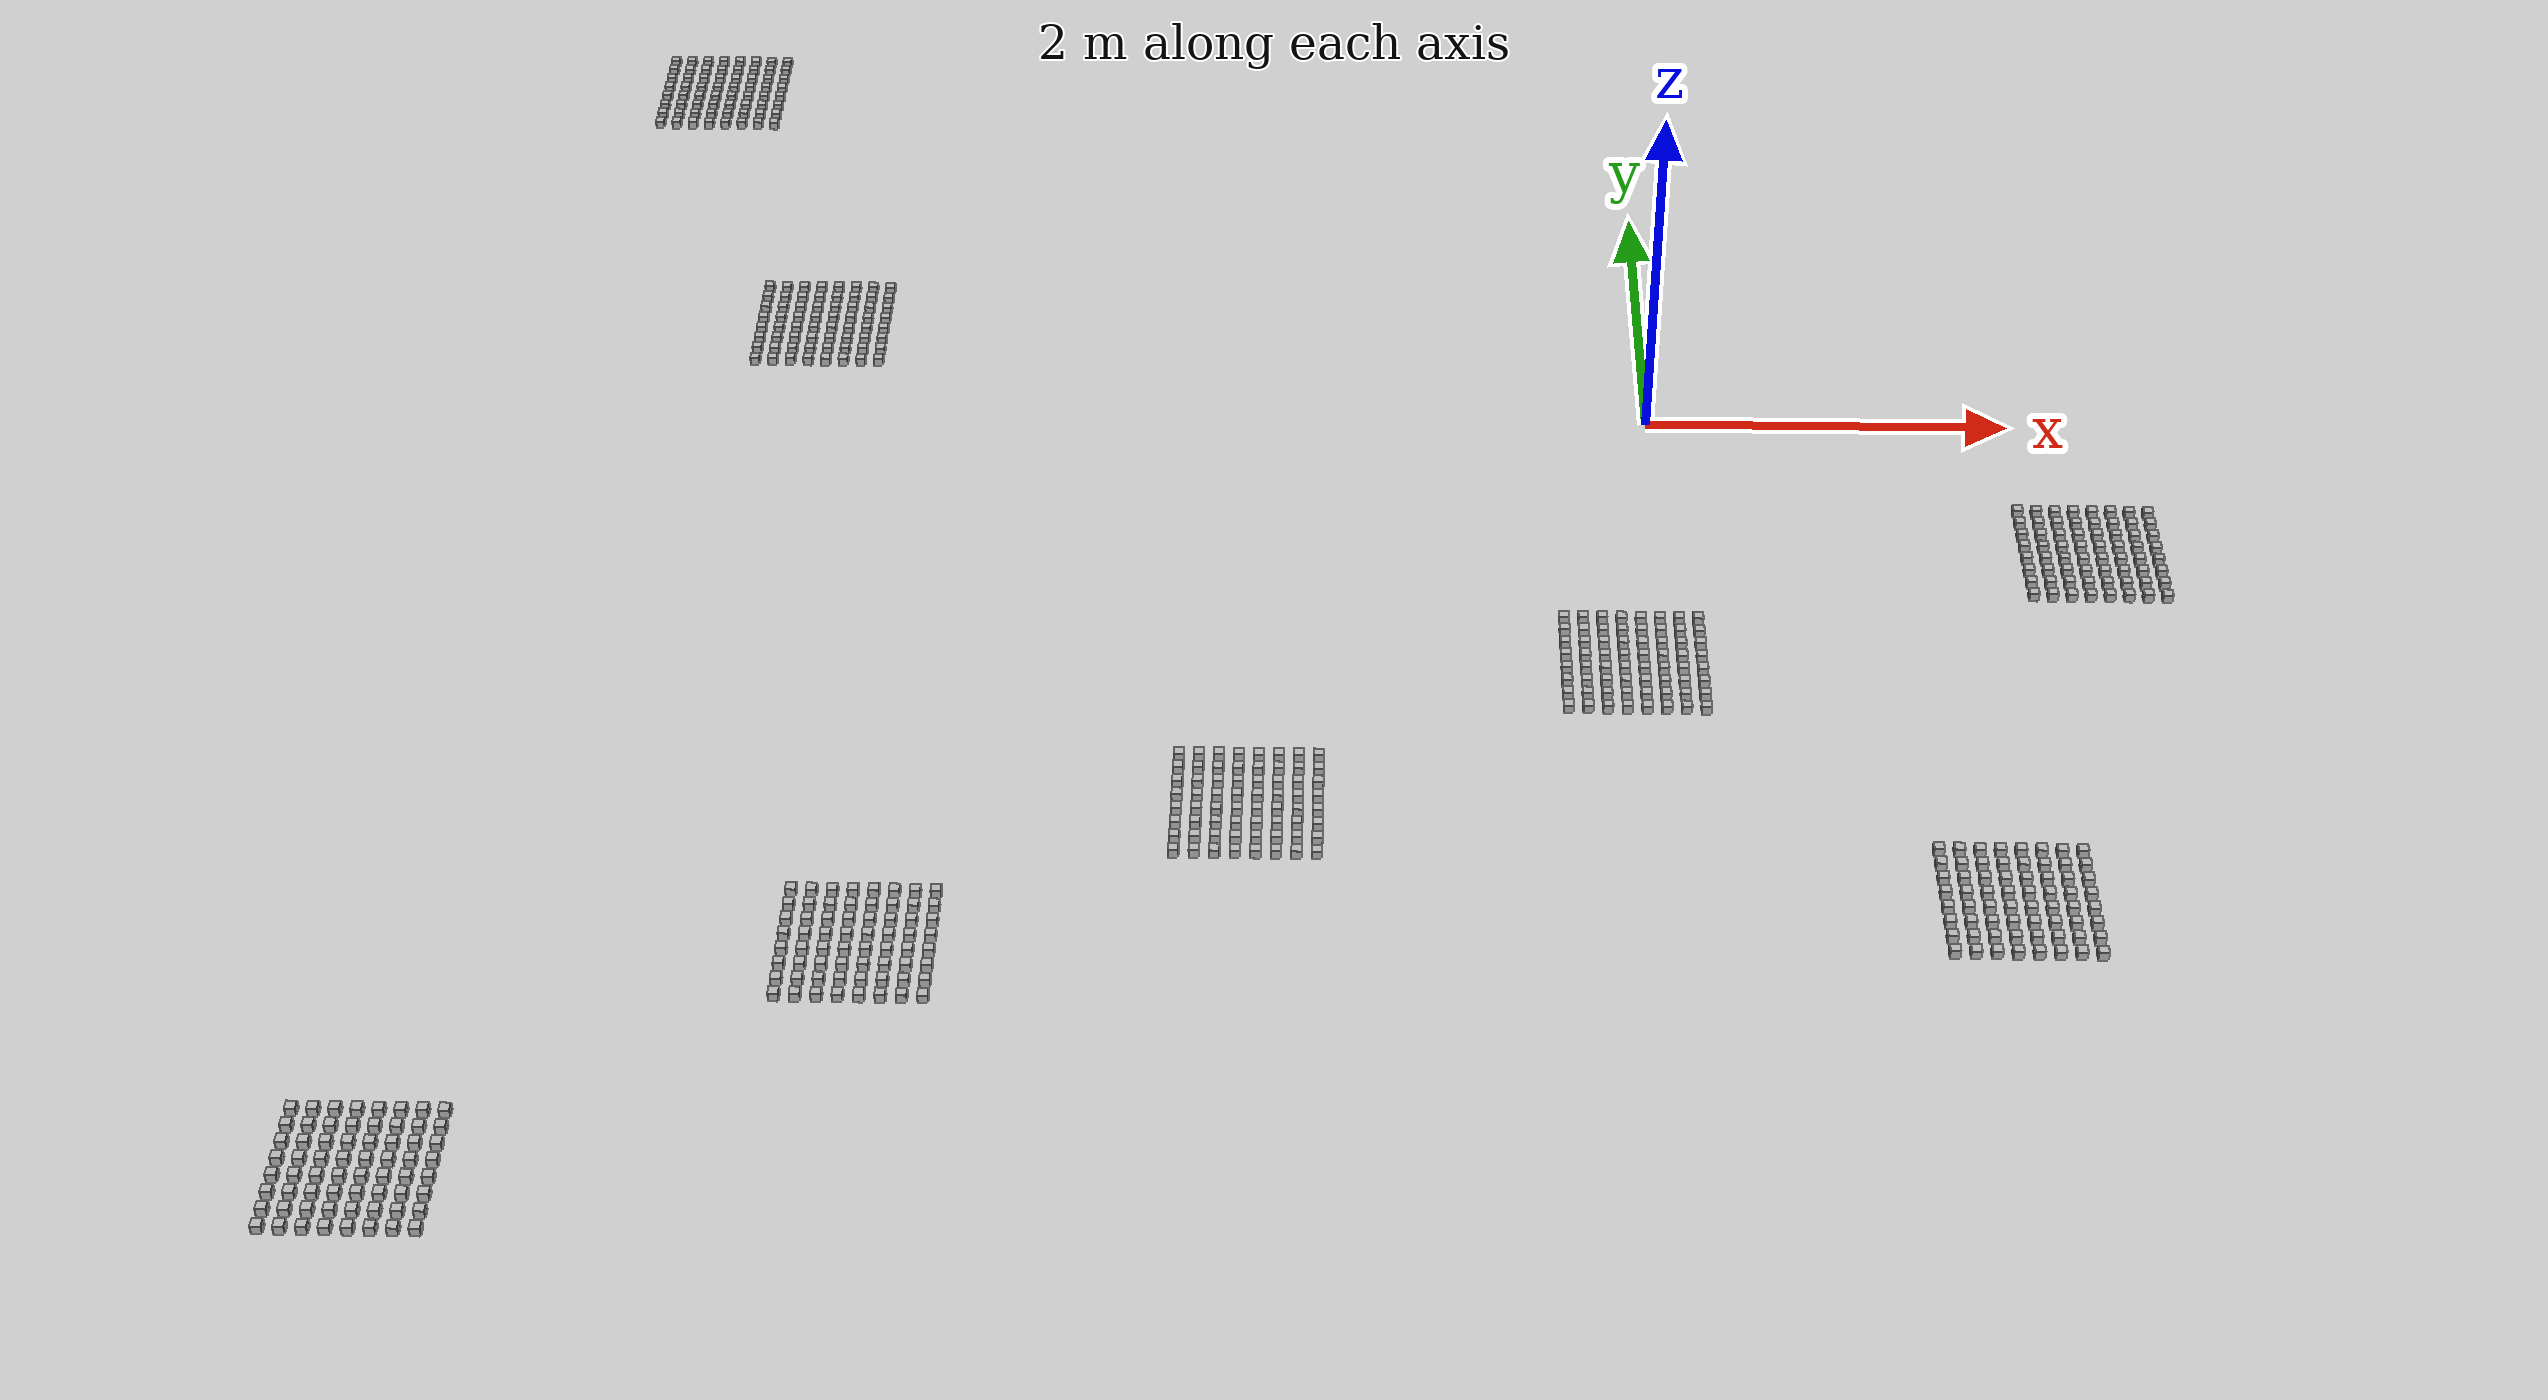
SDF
<sdf version="1.6">
 <world name="default">
  <model name="ground_plane">
   <static>1</static>
   <link name="link">
    <collision name="collision">
     <geometry><plane><normal>0 0 1</normal><size>100 100</size></plane></geometry>
     <surface><friction><ode><mu>100</mu><mu2>50</mu2></ode></friction></surface>
    </collision>
    <visual name="visual">
     <cast_shadows>0</cast_shadows>
     <geometry><plane><normal>0 0 1</normal><size>100 100</size></plane></geometry>
     <material>
      <script><uri>file://media/materials/scripts/gazebo.material</uri><name>Gazebo/Grey</name></script>
     </material>
    </visual>
   </link>
  </model>
  <light name="sun" type="directional">
   <pose>0 0 10 0 -0 0</pose>
   <diffuse>0.8 0.8 0.8 1</diffuse>
   <specular>0.1 0.1 0.1 1</specular>
   <attenuation>
    <range>1000</range>
    <constant>0.9</constant>
    <linear>0.01</linear>
    <quadratic>0.001</quadratic>
   </attenuation>
   <direction>-0.5 0.5 -1</direction>
  </light>
  <plugin name="SetupWorld" filename="libgazebo_plugins.so"/>
  <gravity>0 0 -9.8</gravity>
  <magnetic_field>6e-06 2.3e-05 -4.2e-05</magnetic_field>
  <atmosphere type="adiabatic"/>
  <physics name="default_physics" default="0" type="ode">
   <max_step_size>0.001</max_step_size>
   <real_time_factor>1</real_time_factor>
   <real_time_update_rate>1000</real_time_update_rate>
  </physics>
  <scene><ambient>0.4 0.4 0.4 1</ambient><background>0.7 0.7 0.7 1</background><shadows>1</shadows></scene>
  <spherical_coordinates>
   <surface_model>EARTH_WGS84</surface_model>
   <latitude_deg>0</latitude_deg>
   <longitude_deg>0</longitude_deg>
   <elevation>0</elevation>
   <heading_deg>0</heading_deg>
  </spherical_coordinates>
  <model name="at0">
   <static>0</static>
   <link name="link">
    <inertial>
     <mass>0.01</mass>
     <inertia><ixx>4e-05</ixx><ixy>0</ixy><ixz>0</ixz><iyy>4e-05</iyy><iyz>0</iyz><izz>4e-05</izz></inertia>
    </inertial>
    <visual name="visual">
     <geometry><box><size>0.05 0.05 0.05</size></box></geometry>
     <material>
      <script>
       <uri>model://at0/materials/scripts</uri>
       <uri>model://at0/materials/textures</uri>
       <name>at0/Diffuse</name>
      </script>
     </material>
    </visual>
    <collision name="collision">
     <geometry><box><size>0.05 0.05 0.05</size></box></geometry>
     <surface><friction><ode><mu>0.8</mu><mu2>0.7</mu2></ode></friction></surface>
    </collision>
   </link>
   <pose>-5.01833 0.509652 0.025 0 -0 0</pose>
  </model>
  <model name="at1">
   <static>0</static>
   <link name="link">
    <inertial>
     <mass>0.01</mass>
     <inertia><ixx>4e-05</ixx><ixy>0</ixy><ixz>0</ixz><iyy>4e-05</iyy><iyz>0</iyz><izz>4e-05</izz></inertia>
    </inertial>
    <visual name="visual">
     <geometry><box><size>0.05 0.05 0.05</size></box></geometry>
     <material>
      <script>
       <uri>model://at0/materials/scripts</uri>
       <uri>model://at0/materials/textures</uri>
       <name>at0/Diffuse</name>
      </script>
     </material>
    </visual>
    <collision name="collision">
     <geometry><box><size>0.05 0.05 0.05</size></box></geometry>
     <surface><friction><ode><mu>0.8</mu><mu2>0.7</mu2></ode></friction></surface>
    </collision>
   </link>
   <pose>-4.91833 0.509652 0.025 0 -0 0</pose>
  </model>
  <model name="at2">
   <static>0</static>
   <link name="link">
    <inertial>
     <mass>0.01</mass>
     <inertia><ixx>4e-05</ixx><ixy>0</ixy><ixz>0</ixz><iyy>4e-05</iyy><iyz>0</iyz><izz>4e-05</izz></inertia>
    </inertial>
    <visual name="visual">
     <geometry><box><size>0.05 0.05 0.05</size></box></geometry>
     <material>
      <script>
       <uri>model://at0/materials/scripts</uri>
       <uri>model://at0/materials/textures</uri>
       <name>at0/Diffuse</name>
      </script>
     </material>
    </visual>
    <collision name="collision">
     <geometry><box><size>0.05 0.05 0.05</size></box></geometry>
     <surface><friction><ode><mu>0.8</mu><mu2>0.7</mu2></ode></friction></surface>
    </collision>
   </link>
   <pose>-4.81833 0.509652 0.025 0 -0 0</pose>
  </model>
  <model name="at3">
   <static>0</static>
   <link name="link">
    <inertial>
     <mass>0.01</mass>
     <inertia><ixx>4e-05</ixx><ixy>0</ixy><ixz>0</ixz><iyy>4e-05</iyy><iyz>0</iyz><izz>4e-05</izz></inertia>
    </inertial>
    <visual name="visual">
     <geometry><box><size>0.05 0.05 0.05</size></box></geometry>
     <material>
      <script>
       <uri>model://at0/materials/scripts</uri>
       <uri>model://at0/materials/textures</uri>
       <name>at0/Diffuse</name>
      </script>
     </material>
    </visual>
    <collision name="collision">
     <geometry><box><size>0.05 0.05 0.05</size></box></geometry>
     <surface><friction><ode><mu>0.8</mu><mu2>0.7</mu2></ode></friction></surface>
    </collision>
   </link>
   <pose>-4.71833 0.509652 0.025 0 -0 0</pose>
  </model>
  <model name="at4">
   <static>0</static>
   <link name="link">
    <inertial>
     <mass>0.01</mass>
     <inertia><ixx>4e-05</ixx><ixy>0</ixy><ixz>0</ixz><iyy>4e-05</iyy><iyz>0</iyz><izz>4e-05</izz></inertia>
    </inertial>
    <visual name="visual">
     <geometry><box><size>0.05 0.05 0.05</size></box></geometry>
     <material>
      <script>
       <uri>model://at0/materials/scripts</uri>
       <uri>model://at0/materials/textures</uri>
       <name>at0/Diffuse</name>
      </script>
     </material>
    </visual>
    <collision name="collision">
     <geometry><box><size>0.05 0.05 0.05</size></box></geometry>
     <surface><friction><ode><mu>0.8</mu><mu2>0.7</mu2></ode></friction></surface>
    </collision>
   </link>
   <pose>-4.61833 0.509652 0.025 0 -0 0</pose>
  </model>
  <model name="at5">
   <static>0</static>
   <link name="link">
    <inertial>
     <mass>0.01</mass>
     <inertia><ixx>4e-05</ixx><ixy>0</ixy><ixz>0</ixz><iyy>4e-05</iyy><iyz>0</iyz><izz>4e-05</izz></inertia>
    </inertial>
    <visual name="visual">
     <geometry><box><size>0.05 0.05 0.05</size></box></geometry>
     <material>
      <script>
       <uri>model://at0/materials/scripts</uri>
       <uri>model://at0/materials/textures</uri>
       <name>at0/Diffuse</name>
      </script>
     </material>
    </visual>
    <collision name="collision">
     <geometry><box><size>0.05 0.05 0.05</size></box></geometry>
     <surface><friction><ode><mu>0.8</mu><mu2>0.7</mu2></ode></friction></surface>
    </collision>
   </link>
   <pose>-4.51833 0.509652 0.025 0 -0 0</pose>
  </model>
  <model name="at6">
   <static>0</static>
   <link name="link">
    <inertial>
     <mass>0.01</mass>
     <inertia><ixx>4e-05</ixx><ixy>0</ixy><ixz>0</ixz><iyy>4e-05</iyy><iyz>0</iyz><izz>4e-05</izz></inertia>
    </inertial>
    <visual name="visual">
     <geometry><box><size>0.05 0.05 0.05</size></box></geometry>
     <material>
      <script>
       <uri>model://at0/materials/scripts</uri>
       <uri>model://at0/materials/textures</uri>
       <name>at0/Diffuse</name>
      </script>
     </material>
    </visual>
    <collision name="collision">
     <geometry><box><size>0.05 0.05 0.05</size></box></geometry>
     <surface><friction><ode><mu>0.8</mu><mu2>0.7</mu2></ode></friction></surface>
    </collision>
   </link>
   <pose>-4.41833 0.509652 0.025 0 -0 0</pose>
  </model>
  <model name="at7">
   <static>0</static>
   <link name="link">
    <inertial>
     <mass>0.01</mass>
     <inertia><ixx>4e-05</ixx><ixy>0</ixy><ixz>0</ixz><iyy>4e-05</iyy><iyz>0</iyz><izz>4e-05</izz></inertia>
    </inertial>
    <visual name="visual">
     <geometry><box><size>0.05 0.05 0.05</size></box></geometry>
     <material>
      <script>
       <uri>model://at0/materials/scripts</uri>
       <uri>model://at0/materials/textures</uri>
       <name>at0/Diffuse</name>
      </script>
     </material>
    </visual>
    <collision name="collision">
     <geometry><box><size>0.05 0.05 0.05</size></box></geometry>
     <surface><friction><ode><mu>0.8</mu><mu2>0.7</mu2></ode></friction></surface>
    </collision>
   </link>
   <pose>-4.31833 0.509652 0.025 0 -0 0</pose>
  </model>
  <model name="at8">
   <static>0</static>
   <link name="link">
    <inertial>
     <mass>0.01</mass>
     <inertia><ixx>4e-05</ixx><ixy>0</ixy><ixz>0</ixz><iyy>4e-05</iyy><iyz>0</iyz><izz>4e-05</izz></inertia>
    </inertial>
    <visual name="visual">
     <geometry><box><size>0.05 0.05 0.05</size></box></geometry>
     <material>
      <script>
       <uri>model://at0/materials/scripts</uri>
       <uri>model://at0/materials/textures</uri>
       <name>at0/Diffuse</name>
      </script>
     </material>
    </visual>
    <collision name="collision">
     <geometry><box><size>0.05 0.05 0.05</size></box></geometry>
     <surface><friction><ode><mu>0.8</mu><mu2>0.7</mu2></ode></friction></surface>
    </collision>
   </link>
   <pose>-5.01833 0.609652 0.025 0 -0 0</pose>
  </model>
  <model name="at9">
   <static>0</static>
   <link name="link">
    <inertial>
     <mass>0.01</mass>
     <inertia><ixx>4e-05</ixx><ixy>0</ixy><ixz>0</ixz><iyy>4e-05</iyy><iyz>0</iyz><izz>4e-05</izz></inertia>
    </inertial>
    <visual name="visual">
     <geometry><box><size>0.05 0.05 0.05</size></box></geometry>
     <material>
      <script>
       <uri>model://at0/materials/scripts</uri>
       <uri>model://at0/materials/textures</uri>
       <name>at0/Diffuse</name>
      </script>
     </material>
    </visual>
    <collision name="collision">
     <geometry><box><size>0.05 0.05 0.05</size></box></geometry>
     <surface><friction><ode><mu>0.8</mu><mu2>0.7</mu2></ode></friction></surface>
    </collision>
   </link>
   <pose>-4.91833 0.609652 0.025 0 -0 0</pose>
  </model>
  <model name="at10">
   <static>0</static>
   <link name="link">
    <inertial>
     <mass>0.01</mass>
     <inertia><ixx>4e-05</ixx><ixy>0</ixy><ixz>0</ixz><iyy>4e-05</iyy><iyz>0</iyz><izz>4e-05</izz></inertia>
    </inertial>
    <visual name="visual">
     <geometry><box><size>0.05 0.05 0.05</size></box></geometry>
     <material>
      <script>
       <uri>model://at0/materials/scripts</uri>
       <uri>model://at0/materials/textures</uri>
       <name>at0/Diffuse</name>
      </script>
     </material>
    </visual>
    <collision name="collision">
     <geometry><box><size>0.05 0.05 0.05</size></box></geometry>
     <surface><friction><ode><mu>0.8</mu><mu2>0.7</mu2></ode></friction></surface>
    </collision>
   </link>
   <pose>-4.81833 0.609652 0.025 0 -0 0</pose>
  </model>
  <model name="at11">
   <static>0</static>
   <link name="link">
    <inertial>
     <mass>0.01</mass>
     <inertia><ixx>4e-05</ixx><ixy>0</ixy><ixz>0</ixz><iyy>4e-05</iyy><iyz>0</iyz><izz>4e-05</izz></inertia>
    </inertial>
    <visual name="visual">
     <geometry><box><size>0.05 0.05 0.05</size></box></geometry>
     <material>
      <script>
       <uri>model://at0/materials/scripts</uri>
       <uri>model://at0/materials/textures</uri>
       <name>at0/Diffuse</name>
      </script>
     </material>
    </visual>
    <collision name="collision">
     <geometry><box><size>0.05 0.05 0.05</size></box></geometry>
     <surface><friction><ode><mu>0.8</mu><mu2>0.7</mu2></ode></friction></surface>
    </collision>
   </link>
   <pose>-4.71833 0.609652 0.025 0 -0 0</pose>
  </model>
  <model name="at12">
   <static>0</static>
   <link name="link">
    <inertial>
     <mass>0.01</mass>
     <inertia><ixx>4e-05</ixx><ixy>0</ixy><ixz>0</ixz><iyy>4e-05</iyy><iyz>0</iyz><izz>4e-05</izz></inertia>
    </inertial>
    <visual name="visual">
     <geometry><box><size>0.05 0.05 0.05</size></box></geometry>
     <material>
      <script>
       <uri>model://at0/materials/scripts</uri>
       <uri>model://at0/materials/textures</uri>
       <name>at0/Diffuse</name>
      </script>
     </material>
    </visual>
    <collision name="collision">
     <geometry><box><size>0.05 0.05 0.05</size></box></geometry>
     <surface><friction><ode><mu>0.8</mu><mu2>0.7</mu2></ode></friction></surface>
    </collision>
   </link>
   <pose>-4.61833 0.609652 0.025 0 -0 0</pose>
  </model>
  <model name="at13">
   <static>0</static>
   <link name="link">
    <inertial>
     <mass>0.01</mass>
     <inertia><ixx>4e-05</ixx><ixy>0</ixy><ixz>0</ixz><iyy>4e-05</iyy><iyz>0</iyz><izz>4e-05</izz></inertia>
    </inertial>
    <visual name="visual">
     <geometry><box><size>0.05 0.05 0.05</size></box></geometry>
     <material>
      <script>
       <uri>model://at0/materials/scripts</uri>
       <uri>model://at0/materials/textures</uri>
       <name>at0/Diffuse</name>
      </script>
     </material>
    </visual>
    <collision name="collision">
     <geometry><box><size>0.05 0.05 0.05</size></box></geometry>
     <surface><friction><ode><mu>0.8</mu><mu2>0.7</mu2></ode></friction></surface>
    </collision>
   </link>
   <pose>-4.51833 0.609652 0.025 0 -0 0</pose>
  </model>
  <model name="at14">
   <static>0</static>
   <link name="link">
    <inertial>
     <mass>0.01</mass>
     <inertia><ixx>4e-05</ixx><ixy>0</ixy><ixz>0</ixz><iyy>4e-05</iyy><iyz>0</iyz><izz>4e-05</izz></inertia>
    </inertial>
    <visual name="visual">
     <geometry><box><size>0.05 0.05 0.05</size></box></geometry>
     <material>
      <script>
       <uri>model://at0/materials/scripts</uri>
       <uri>model://at0/materials/textures</uri>
       <name>at0/Diffuse</name>
      </script>
     </material>
    </visual>
    <collision name="collision">
     <geometry><box><size>0.05 0.05 0.05</size></box></geometry>
     <surface><friction><ode><mu>0.8</mu><mu2>0.7</mu2></ode></friction></surface>
    </collision>
   </link>
   <pose>-4.41833 0.609652 0.025 0 -0 0</pose>
  </model>
  <model name="at15">
   <static>0</static>
   <link name="link">
    <inertial>
     <mass>0.01</mass>
     <inertia><ixx>4e-05</ixx><ixy>0</ixy><ixz>0</ixz><iyy>4e-05</iyy><iyz>0</iyz><izz>4e-05</izz></inertia>
    </inertial>
    <visual name="visual">
     <geometry><box><size>0.05 0.05 0.05</size></box></geometry>
     <material>
      <script>
       <uri>model://at0/materials/scripts</uri>
       <uri>model://at0/materials/textures</uri>
       <name>at0/Diffuse</name>
      </script>
     </material>
    </visual>
    <collision name="collision">
     <geometry><box><size>0.05 0.05 0.05</size></box></geometry>
     <surface><friction><ode><mu>0.8</mu><mu2>0.7</mu2></ode></friction></surface>
    </collision>
   </link>
   <pose>-4.31833 0.609652 0.025 0 -0 0</pose>
  </model>
  <model name="at16">
   <static>0</static>
   <link name="link">
    <inertial>
     <mass>0.01</mass>
     <inertia><ixx>4e-05</ixx><ixy>0</ixy><ixz>0</ixz><iyy>4e-05</iyy><iyz>0</iyz><izz>4e-05</izz></inertia>
    </inertial>
    <visual name="visual">
     <geometry><box><size>0.05 0.05 0.05</size></box></geometry>
     <material>
      <script>
       <uri>model://at0/materials/scripts</uri>
       <uri>model://at0/materials/textures</uri>
       <name>at0/Diffuse</name>
      </script>
     </material>
    </visual>
    <collision name="collision">
     <geometry><box><size>0.05 0.05 0.05</size></box></geometry>
     <surface><friction><ode><mu>0.8</mu><mu2>0.7</mu2></ode></friction></surface>
    </collision>
   </link>
   <pose>-5.01833 0.709652 0.025 0 -0 0</pose>
  </model>
  <model name="at17">
   <static>0</static>
   <link name="link">
    <inertial>
     <mass>0.01</mass>
     <inertia><ixx>4e-05</ixx><ixy>0</ixy><ixz>0</ixz><iyy>4e-05</iyy><iyz>0</iyz><izz>4e-05</izz></inertia>
    </inertial>
    <visual name="visual">
     <geometry><box><size>0.05 0.05 0.05</size></box></geometry>
     <material>
      <script>
       <uri>model://at0/materials/scripts</uri>
       <uri>model://at0/materials/textures</uri>
       <name>at0/Diffuse</name>
      </script>
     </material>
    </visual>
    <collision name="collision">
     <geometry><box><size>0.05 0.05 0.05</size></box></geometry>
     <surface><friction><ode><mu>0.8</mu><mu2>0.7</mu2></ode></friction></surface>
    </collision>
   </link>
   <pose>-4.91833 0.709652 0.025 0 -0 0</pose>
  </model>
  <model name="at18">
   <static>0</static>
   <link name="link">
    <inertial>
     <mass>0.01</mass>
     <inertia><ixx>4e-05</ixx><ixy>0</ixy><ixz>0</ixz><iyy>4e-05</iyy><iyz>0</iyz><izz>4e-05</izz></inertia>
    </inertial>
    <visual name="visual">
     <geometry><box><size>0.05 0.05 0.05</size></box></geometry>
     <material>
      <script>
       <uri>model://at0/materials/scripts</uri>
       <uri>model://at0/materials/textures</uri>
       <name>at0/Diffuse</name>
      </script>
     </material>
    </visual>
    <collision name="collision">
     <geometry><box><size>0.05 0.05 0.05</size></box></geometry>
     <surface><friction><ode><mu>0.8</mu><mu2>0.7</mu2></ode></friction></surface>
    </collision>
   </link>
   <pose>-4.81833 0.709652 0.025 0 -0 0</pose>
  </model>
  <model name="at19">
   <static>0</static>
   <link name="link">
    <inertial>
     <mass>0.01</mass>
     <inertia><ixx>4e-05</ixx><ixy>0</ixy><ixz>0</ixz><iyy>4e-05</iyy><iyz>0</iyz><izz>4e-05</izz></inertia>
    </inertial>
    <visual name="visual">
     <geometry><box><size>0.05 0.05 0.05</size></box></geometry>
     <material>
      <script>
       <uri>model://at0/materials/scripts</uri>
       <uri>model://at0/materials/textures</uri>
       <name>at0/Diffuse</name>
      </script>
     </material>
    </visual>
    <collision name="collision">
     <geometry><box><size>0.05 0.05 0.05</size></box></geometry>
     <surface><friction><ode><mu>0.8</mu><mu2>0.7</mu2></ode></friction></surface>
    </collision>
   </link>
   <pose>-4.71833 0.709652 0.025 0 -0 0</pose>
  </model>
  <model name="at20">
   <static>0</static>
   <link name="link">
    <inertial>
     <mass>0.01</mass>
     <inertia><ixx>4e-05</ixx><ixy>0</ixy><ixz>0</ixz><iyy>4e-05</iyy><iyz>0</iyz><izz>4e-05</izz></inertia>
    </inertial>
    <visual name="visual">
     <geometry><box><size>0.05 0.05 0.05</size></box></geometry>
     <material>
      <script>
       <uri>model://at0/materials/scripts</uri>
       <uri>model://at0/materials/textures</uri>
       <name>at0/Diffuse</name>
      </script>
     </material>
    </visual>
    <collision name="collision">
     <geometry><box><size>0.05 0.05 0.05</size></box></geometry>
     <surface><friction><ode><mu>0.8</mu><mu2>0.7</mu2></ode></friction></surface>
    </collision>
   </link>
   <pose>-4.61833 0.709652 0.025 0 -0 0</pose>
  </model>
  <model name="at21">
   <static>0</static>
   <link name="link">
    <inertial>
     <mass>0.01</mass>
     <inertia><ixx>4e-05</ixx><ixy>0</ixy><ixz>0</ixz><iyy>4e-05</iyy><iyz>0</iyz><izz>4e-05</izz></inertia>
    </inertial>
    <visual name="visual">
     <geometry><box><size>0.05 0.05 0.05</size></box></geometry>
     <material>
      <script>
       <uri>model://at0/materials/scripts</uri>
       <uri>model://at0/materials/textures</uri>
       <name>at0/Diffuse</name>
      </script>
     </material>
    </visual>
    <collision name="collision">
     <geometry><box><size>0.05 0.05 0.05</size></box></geometry>
     <surface><friction><ode><mu>0.8</mu><mu2>0.7</mu2></ode></friction></surface>
    </collision>
   </link>
   <pose>-4.51833 0.709652 0.025 0 -0 0</pose>
  </model>
  <model name="at22">
   <static>0</static>
   <link name="link">
    <inertial>
     <mass>0.01</mass>
     <inertia><ixx>4e-05</ixx><ixy>0</ixy><ixz>0</ixz><iyy>4e-05</iyy><iyz>0</iyz><izz>4e-05</izz></inertia>
    </inertial>
    <visual name="visual">
     <geometry><box><size>0.05 0.05 0.05</size></box></geometry>
     <material>
      <script>
       <uri>model://at0/materials/scripts</uri>
       <uri>model://at0/materials/textures</uri>
       <name>at0/Diffuse</name>
      </script>
     </material>
    </visual>
    <collision name="collision">
     <geometry><box><size>0.05 0.05 0.05</size></box></geometry>
     <surface><friction><ode><mu>0.8</mu><mu2>0.7</mu2></ode></friction></surface>
    </collision>
   </link>
   <pose>-4.41833 0.709652 0.025 0 -0 0</pose>
  </model>
  <model name="at23">
   <static>0</static>
   <link name="link">
    <inertial>
     <mass>0.01</mass>
     <inertia><ixx>4e-05</ixx><ixy>0</ixy><ixz>0</ixz><iyy>4e-05</iyy><iyz>0</iyz><izz>4e-05</izz></inertia>
    </inertial>
    <visual name="visual">
     <geometry><box><size>0.05 0.05 0.05</size></box></geometry>
     <material>
      <script>
       <uri>model://at0/materials/scripts</uri>
       <uri>model://at0/materials/textures</uri>
       <name>at0/Diffuse</name>
      </script>
     </material>
    </visual>
    <collision name="collision">
     <geometry><box><size>0.05 0.05 0.05</size></box></geometry>
     <surface><friction><ode><mu>0.8</mu><mu2>0.7</mu2></ode></friction></surface>
    </collision>
   </link>
   <pose>-4.31833 0.709652 0.025 0 -0 0</pose>
  </model>
  <model name="at24">
   <static>0</static>
   <link name="link">
    <inertial>
     <mass>0.01</mass>
     <inertia><ixx>4e-05</ixx><ixy>0</ixy><ixz>0</ixz><iyy>4e-05</iyy><iyz>0</iyz><izz>4e-05</izz></inertia>
    </inertial>
    <visual name="visual">
     <geometry><box><size>0.05 0.05 0.05</size></box></geometry>
     <material>
      <script>
       <uri>model://at0/materials/scripts</uri>
       <uri>model://at0/materials/textures</uri>
       <name>at0/Diffuse</name>
      </script>
     </material>
    </visual>
    <collision name="collision">
     <geometry><box><size>0.05 0.05 0.05</size></box></geometry>
     <surface><friction><ode><mu>0.8</mu><mu2>0.7</mu2></ode></friction></surface>
    </collision>
   </link>
   <pose>-5.01833 0.809652 0.025 0 -0 0</pose>
  </model>
  <model name="at25">
   <static>0</static>
   <link name="link">
    <inertial>
     <mass>0.01</mass>
     <inertia><ixx>4e-05</ixx><ixy>0</ixy><ixz>0</ixz><iyy>4e-05</iyy><iyz>0</iyz><izz>4e-05</izz></inertia>
    </inertial>
    <visual name="visual">
     <geometry><box><size>0.05 0.05 0.05</size></box></geometry>
     <material>
      <script>
       <uri>model://at0/materials/scripts</uri>
       <uri>model://at0/materials/textures</uri>
       <name>at0/Diffuse</name>
      </script>
     </material>
    </visual>
    <collision name="collision">
     <geometry><box><size>0.05 0.05 0.05</size></box></geometry>
     <surface><friction><ode><mu>0.8</mu><mu2>0.7</mu2></ode></friction></surface>
    </collision>
   </link>
   <pose>-4.91833 0.809652 0.025 0 -0 0</pose>
  </model>
  <model name="at26">
   <static>0</static>
   <link name="link">
    <inertial>
     <mass>0.01</mass>
     <inertia><ixx>4e-05</ixx><ixy>0</ixy><ixz>0</ixz><iyy>4e-05</iyy><iyz>0</iyz><izz>4e-05</izz></inertia>
    </inertial>
    <visual name="visual">
     <geometry><box><size>0.05 0.05 0.05</size></box></geometry>
     <material>
      <script>
       <uri>model://at0/materials/scripts</uri>
       <uri>model://at0/materials/textures</uri>
       <name>at0/Diffuse</name>
      </script>
     </material>
    </visual>
    <collision name="collision">
     <geometry><box><size>0.05 0.05 0.05</size></box></geometry>
     <surface><friction><ode><mu>0.8</mu><mu2>0.7</mu2></ode></friction></surface>
    </collision>
   </link>
   <pose>-4.81833 0.809652 0.025 0 -0 0</pose>
  </model>
  <model name="at27">
   <static>0</static>
   <link name="link">
    <inertial>
     <mass>0.01</mass>
     <inertia><ixx>4e-05</ixx><ixy>0</ixy><ixz>0</ixz><iyy>4e-05</iyy><iyz>0</iyz><izz>4e-05</izz></inertia>
    </inertial>
    <visual name="visual">
     <geometry><box><size>0.05 0.05 0.05</size></box></geometry>
     <material>
      <script>
       <uri>model://at0/materials/scripts</uri>
       <uri>model://at0/materials/textures</uri>
       <name>at0/Diffuse</name>
      </script>
     </material>
    </visual>
    <collision name="collision">
     <geometry><box><size>0.05 0.05 0.05</size></box></geometry>
     <surface><friction><ode><mu>0.8</mu><mu2>0.7</mu2></ode></friction></surface>
    </collision>
   </link>
   <pose>-4.71833 0.809652 0.025 0 -0 0</pose>
  </model>
  <model name="at28">
   <static>0</static>
   <link name="link">
    <inertial>
     <mass>0.01</mass>
     <inertia><ixx>4e-05</ixx><ixy>0</ixy><ixz>0</ixz><iyy>4e-05</iyy><iyz>0</iyz><izz>4e-05</izz></inertia>
    </inertial>
    <visual name="visual">
     <geometry><box><size>0.05 0.05 0.05</size></box></geometry>
     <material>
      <script>
       <uri>model://at0/materials/scripts</uri>
       <uri>model://at0/materials/textures</uri>
       <name>at0/Diffuse</name>
      </script>
     </material>
    </visual>
    <collision name="collision">
     <geometry><box><size>0.05 0.05 0.05</size></box></geometry>
     <surface><friction><ode><mu>0.8</mu><mu2>0.7</mu2></ode></friction></surface>
    </collision>
   </link>
   <pose>-4.61833 0.809652 0.025 0 -0 0</pose>
  </model>
  <model name="at29">
   <static>0</static>
   <link name="link">
    <inertial>
     <mass>0.01</mass>
     <inertia><ixx>4e-05</ixx><ixy>0</ixy><ixz>0</ixz><iyy>4e-05</iyy><iyz>0</iyz><izz>4e-05</izz></inertia>
    </inertial>
    <visual name="visual">
     <geometry><box><size>0.05 0.05 0.05</size></box></geometry>
     <material>
      <script>
       <uri>model://at0/materials/scripts</uri>
       <uri>model://at0/materials/textures</uri>
       <name>at0/Diffuse</name>
      </script>
     </material>
    </visual>
    <collision name="collision">
     <geometry><box><size>0.05 0.05 0.05</size></box></geometry>
     <surface><friction><ode><mu>0.8</mu><mu2>0.7</mu2></ode></friction></surface>
    </collision>
   </link>
   <pose>-4.51833 0.809652 0.025 0 -0 0</pose>
  </model>
  <model name="at30">
   <static>0</static>
   <link name="link">
    <inertial>
     <mass>0.01</mass>
     <inertia><ixx>4e-05</ixx><ixy>0</ixy><ixz>0</ixz><iyy>4e-05</iyy><iyz>0</iyz><izz>4e-05</izz></inertia>
    </inertial>
    <visual name="visual">
     <geometry><box><size>0.05 0.05 0.05</size></box></geometry>
     <material>
      <script>
       <uri>model://at0/materials/scripts</uri>
       <uri>model://at0/materials/textures</uri>
       <name>at0/Diffuse</name>
      </script>
     </material>
    </visual>
    <collision name="collision">
     <geometry><box><size>0.05 0.05 0.05</size></box></geometry>
     <surface><friction><ode><mu>0.8</mu><mu2>0.7</mu2></ode></friction></surface>
    </collision>
   </link>
   <pose>-4.41833 0.809652 0.025 0 -0 0</pose>
  </model>
  <model name="at31">
   <static>0</static>
   <link name="link">
    <inertial>
     <mass>0.01</mass>
     <inertia><ixx>4e-05</ixx><ixy>0</ixy><ixz>0</ixz><iyy>4e-05</iyy><iyz>0</iyz><izz>4e-05</izz></inertia>
    </inertial>
    <visual name="visual">
     <geometry><box><size>0.05 0.05 0.05</size></box></geometry>
     <material>
      <script>
       <uri>model://at0/materials/scripts</uri>
       <uri>model://at0/materials/textures</uri>
       <name>at0/Diffuse</name>
      </script>
     </material>
    </visual>
    <collision name="collision">
     <geometry><box><size>0.05 0.05 0.05</size></box></geometry>
     <surface><friction><ode><mu>0.8</mu><mu2>0.7</mu2></ode></friction></surface>
    </collision>
   </link>
   <pose>-4.31833 0.809652 0.025 0 -0 0</pose>
  </model>
  <model name="at32">
   <static>0</static>
   <link name="link">
    <inertial>
     <mass>0.01</mass>
     <inertia><ixx>4e-05</ixx><ixy>0</ixy><ixz>0</ixz><iyy>4e-05</iyy><iyz>0</iyz><izz>4e-05</izz></inertia>
    </inertial>
    <visual name="visual">
     <geometry><box><size>0.05 0.05 0.05</size></box></geometry>
     <material>
      <script>
       <uri>model://at0/materials/scripts</uri>
       <uri>model://at0/materials/textures</uri>
       <name>at0/Diffuse</name>
      </script>
     </material>
    </visual>
    <collision name="collision">
     <geometry><box><size>0.05 0.05 0.05</size></box></geometry>
     <surface><friction><ode><mu>0.8</mu><mu2>0.7</mu2></ode></friction></surface>
    </collision>
   </link>
   <pose>-5.01833 0.909652 0.025 0 -0 0</pose>
  </model>
  <model name="at33">
   <static>0</static>
   <link name="link">
    <inertial>
     <mass>0.01</mass>
     <inertia><ixx>4e-05</ixx><ixy>0</ixy><ixz>0</ixz><iyy>4e-05</iyy><iyz>0</iyz><izz>4e-05</izz></inertia>
    </inertial>
    <visual name="visual">
     <geometry><box><size>0.05 0.05 0.05</size></box></geometry>
     <material>
      <script>
       <uri>model://at0/materials/scripts</uri>
       <uri>model://at0/materials/textures</uri>
       <name>at0/Diffuse</name>
      </script>
     </material>
    </visual>
    <collision name="collision">
     <geometry><box><size>0.05 0.05 0.05</size></box></geometry>
     <surface><friction><ode><mu>0.8</mu><mu2>0.7</mu2></ode></friction></surface>
    </collision>
   </link>
   <pose>-4.91833 0.909652 0.025 0 -0 0</pose>
  </model>
  <model name="at34">
   <static>0</static>
   <link name="link">
    <inertial>
     <mass>0.01</mass>
     <inertia><ixx>4e-05</ixx><ixy>0</ixy><ixz>0</ixz><iyy>4e-05</iyy><iyz>0</iyz><izz>4e-05</izz></inertia>
    </inertial>
    <visual name="visual">
     <geometry><box><size>0.05 0.05 0.05</size></box></geometry>
     <material>
      <script>
       <uri>model://at0/materials/scripts</uri>
       <uri>model://at0/materials/textures</uri>
       <name>at0/Diffuse</name>
      </script>
     </material>
    </visual>
    <collision name="collision">
     <geometry><box><size>0.05 0.05 0.05</size></box></geometry>
     <surface><friction><ode><mu>0.8</mu><mu2>0.7</mu2></ode></friction></surface>
    </collision>
   </link>
   <pose>-4.81833 0.909652 0.025 0 -0 0</pose>
  </model>
  <model name="at35">
   <static>0</static>
   <link name="link">
    <inertial>
     <mass>0.01</mass>
     <inertia><ixx>4e-05</ixx><ixy>0</ixy><ixz>0</ixz><iyy>4e-05</iyy><iyz>0</iyz><izz>4e-05</izz></inertia>
    </inertial>
    <visual name="visual">
     <geometry><box><size>0.05 0.05 0.05</size></box></geometry>
     <material>
      <script>
       <uri>model://at0/materials/scripts</uri>
       <uri>model://at0/materials/textures</uri>
       <name>at0/Diffuse</name>
      </script>
     </material>
    </visual>
    <collision name="collision">
     <geometry><box><size>0.05 0.05 0.05</size></box></geometry>
     <surface><friction><ode><mu>0.8</mu><mu2>0.7</mu2></ode></friction></surface>
    </collision>
   </link>
   <pose>-4.71833 0.909652 0.025 0 -0 0</pose>
  </model>
  <model name="at36">
   <static>0</static>
   <link name="link">
    <inertial>
     <mass>0.01</mass>
     <inertia><ixx>4e-05</ixx><ixy>0</ixy><ixz>0</ixz><iyy>4e-05</iyy><iyz>0</iyz><izz>4e-05</izz></inertia>
    </inertial>
    <visual name="visual">
     <geometry><box><size>0.05 0.05 0.05</size></box></geometry>
     <material>
      <script>
       <uri>model://at0/materials/scripts</uri>
       <uri>model://at0/materials/textures</uri>
       <name>at0/Diffuse</name>
      </script>
     </material>
    </visual>
    <collision name="collision">
     <geometry><box><size>0.05 0.05 0.05</size></box></geometry>
     <surface><friction><ode><mu>0.8</mu><mu2>0.7</mu2></ode></friction></surface>
    </collision>
   </link>
   <pose>-4.61833 0.909652 0.025 0 -0 0</pose>
  </model>
  <model name="at37">
   <static>0</static>
   <link name="link">
    <inertial>
     <mass>0.01</mass>
     <inertia><ixx>4e-05</ixx><ixy>0</ixy><ixz>0</ixz><iyy>4e-05</iyy><iyz>0</iyz><izz>4e-05</izz></inertia>
    </inertial>
    <visual name="visual">
     <geometry><box><size>0.05 0.05 0.05</size></box></geometry>
     <material>
      <script>
       <uri>model://at0/materials/scripts</uri>
       <uri>model://at0/materials/textures</uri>
       <name>at0/Diffuse</name>
      </script>
     </material>
    </visual>
    <collision name="collision">
     <geometry><box><size>0.05 0.05 0.05</size></box></geometry>
     <surface><friction><ode><mu>0.8</mu><mu2>0.7</mu2></ode></friction></surface>
    </collision>
   </link>
   <pose>-4.51833 0.909652 0.025 0 -0 0</pose>
  </model>
  <model name="at38">
   <static>0</static>
   <link name="link">
    <inertial>
     <mass>0.01</mass>
     <inertia><ixx>4e-05</ixx><ixy>0</ixy><ixz>0</ixz><iyy>4e-05</iyy><iyz>0</iyz><izz>4e-05</izz></inertia>
    </inertial>
    <visual name="visual">
     <geometry><box><size>0.05 0.05 0.05</size></box></geometry>
     <material>
      <script>
       <uri>model://at0/materials/scripts</uri>
       <uri>model://at0/materials/textures</uri>
       <name>at0/Diffuse</name>
      </script>
     </material>
    </visual>
    <collision name="collision">
     <geometry><box><size>0.05 0.05 0.05</size></box></geometry>
     <surface><friction><ode><mu>0.8</mu><mu2>0.7</mu2></ode></friction></surface>
    </collision>
   </link>
   <pose>-4.41833 0.909652 0.025 0 -0 0</pose>
  </model>
  <model name="at39">
   <static>0</static>
   <link name="link">
    <inertial>
     <mass>0.01</mass>
     <inertia><ixx>4e-05</ixx><ixy>0</ixy><ixz>0</ixz><iyy>4e-05</iyy><iyz>0</iyz><izz>4e-05</izz></inertia>
    </inertial>
    <visual name="visual">
     <geometry><box><size>0.05 0.05 0.05</size></box></geometry>
     <material>
      <script>
       <uri>model://at0/materials/scripts</uri>
       <uri>model://at0/materials/textures</uri>
       <name>at0/Diffuse</name>
      </script>
     </material>
    </visual>
    <collision name="collision">
     <geometry><box><size>0.05 0.05 0.05</size></box></geometry>
     <surface><friction><ode><mu>0.8</mu><mu2>0.7</mu2></ode></friction></surface>
    </collision>
   </link>
   <pose>-4.31833 0.909652 0.025 0 -0 0</pose>
  </model>
  <model name="at40">
   <static>0</static>
   <link name="link">
    <inertial>
     <mass>0.01</mass>
     <inertia><ixx>4e-05</ixx><ixy>0</ixy><ixz>0</ixz><iyy>4e-05</iyy><iyz>0</iyz><izz>4e-05</izz></inertia>
    </inertial>
    <visual name="visual">
     <geometry><box><size>0.05 0.05 0.05</size></box></geometry>
     <material>
      <script>
       <uri>model://at0/materials/scripts</uri>
       <uri>model://at0/materials/textures</uri>
       <name>at0/Diffuse</name>
      </script>
     </material>
    </visual>
    <collision name="collision">
     <geometry><box><size>0.05 0.05 0.05</size></box></geometry>
     <surface><friction><ode><mu>0.8</mu><mu2>0.7</mu2></ode></friction></surface>
    </collision>
   </link>
   <pose>-5.01833 1.00965 0.025 0 -0 0</pose>
  </model>
  <model name="at41">
   <static>0</static>
   <link name="link">
    <inertial>
     <mass>0.01</mass>
     <inertia><ixx>4e-05</ixx><ixy>0</ixy><ixz>0</ixz><iyy>4e-05</iyy><iyz>0</iyz><izz>4e-05</izz></inertia>
    </inertial>
    <visual name="visual">
     <geometry><box><size>0.05 0.05 0.05</size></box></geometry>
     <material>
      <script>
       <uri>model://at0/materials/scripts</uri>
       <uri>model://at0/materials/textures</uri>
       <name>at0/Diffuse</name>
      </script>
     </material>
    </visual>
    <collision name="collision">
     <geometry><box><size>0.05 0.05 0.05</size></box></geometry>
     <surface><friction><ode><mu>0.8</mu><mu2>0.7</mu2></ode></friction></surface>
    </collision>
   </link>
   <pose>-4.91833 1.00965 0.025 0 -0 0</pose>
  </model>
  <model name="at42">
   <static>0</static>
   <link name="link">
    <inertial>
     <mass>0.01</mass>
     <inertia><ixx>4e-05</ixx><ixy>0</ixy><ixz>0</ixz><iyy>4e-05</iyy><iyz>0</iyz><izz>4e-05</izz></inertia>
    </inertial>
    <visual name="visual">
     <geometry><box><size>0.05 0.05 0.05</size></box></geometry>
     <material>
      <script>
       <uri>model://at0/materials/scripts</uri>
       <uri>model://at0/materials/textures</uri>
       <name>at0/Diffuse</name>
      </script>
     </material>
    </visual>
    <collision name="collision">
     <geometry><box><size>0.05 0.05 0.05</size></box></geometry>
     <surface><friction><ode><mu>0.8</mu><mu2>0.7</mu2></ode></friction></surface>
    </collision>
   </link>
   <pose>-4.81833 1.00965 0.025 0 -0 0</pose>
  </model>
  <model name="at43">
   <static>0</static>
   <link name="link">
    <inertial>
     <mass>0.01</mass>
     <inertia><ixx>4e-05</ixx><ixy>0</ixy><ixz>0</ixz><iyy>4e-05</iyy><iyz>0</iyz><izz>4e-05</izz></inertia>
    </inertial>
    <visual name="visual">
     <geometry><box><size>0.05 0.05 0.05</size></box></geometry>
     <material>
      <script>
       <uri>model://at0/materials/scripts</uri>
       <uri>model://at0/materials/textures</uri>
       <name>at0/Diffuse</name>
      </script>
     </material>
    </visual>
    <collision name="collision">
     <geometry><box><size>0.05 0.05 0.05</size></box></geometry>
     <surface><friction><ode><mu>0.8</mu><mu2>0.7</mu2></ode></friction></surface>
    </collision>
   </link>
   <pose>-4.71833 1.00965 0.025 0 -0 0</pose>
  </model>
  <model name="at44">
   <static>0</static>
   <link name="link">
    <inertial>
     <mass>0.01</mass>
     <inertia><ixx>4e-05</ixx><ixy>0</ixy><ixz>0</ixz><iyy>4e-05</iyy><iyz>0</iyz><izz>4e-05</izz></inertia>
    </inertial>
    <visual name="visual">
     <geometry><box><size>0.05 0.05 0.05</size></box></geometry>
     <material>
      <script>
       <uri>model://at0/materials/scripts</uri>
       <uri>model://at0/materials/textures</uri>
       <name>at0/Diffuse</name>
      </script>
     </material>
    </visual>
    <collision name="collision">
     <geometry><box><size>0.05 0.05 0.05</size></box></geometry>
     <surface><friction><ode><mu>0.8</mu><mu2>0.7</mu2></ode></friction></surface>
    </collision>
   </link>
   <pose>-4.61833 1.00965 0.025 0 -0 0</pose>
  </model>
  <model name="at45">
   <static>0</static>
   <link name="link">
    <inertial>
     <mass>0.01</mass>
     <inertia><ixx>4e-05</ixx><ixy>0</ixy><ixz>0</ixz><iyy>4e-05</iyy><iyz>0</iyz><izz>4e-05</izz></inertia>
    </inertial>
    <visual name="visual">
     <geometry><box><size>0.05 0.05 0.05</size></box></geometry>
     <material>
      <script>
       <uri>model://at0/materials/scripts</uri>
       <uri>model://at0/materials/textures</uri>
       <name>at0/Diffuse</name>
      </script>
     </material>
    </visual>
    <collision name="collision">
     <geometry><box><size>0.05 0.05 0.05</size></box></geometry>
     <surface><friction><ode><mu>0.8</mu><mu2>0.7</mu2></ode></friction></surface>
    </collision>
   </link>
   <pose>-4.51833 1.00965 0.025 0 -0 0</pose>
  </model>
  <model name="at46">
   <static>0</static>
   <link name="link">
    <inertial>
     <mass>0.01</mass>
     <inertia><ixx>4e-05</ixx><ixy>0</ixy><ixz>0</ixz><iyy>4e-05</iyy><iyz>0</iyz><izz>4e-05</izz></inertia>
    </inertial>
    <visual name="visual">
     <geometry><box><size>0.05 0.05 0.05</size></box></geometry>
     <material>
      <script>
       <uri>model://at0/materials/scripts</uri>
       <uri>model://at0/materials/textures</uri>
       <name>at0/Diffuse</name>
      </script>
     </material>
    </visual>
    <collision name="collision">
     <geometry><box><size>0.05 0.05 0.05</size></box></geometry>
     <surface><friction><ode><mu>0.8</mu><mu2>0.7</mu2></ode></friction></surface>
    </collision>
   </link>
   <pose>-4.41833 1.00965 0.025 0 -0 0</pose>
  </model>
  <model name="at47">
   <static>0</static>
   <link name="link">
    <inertial>
     <mass>0.01</mass>
     <inertia><ixx>4e-05</ixx><ixy>0</ixy><ixz>0</ixz><iyy>4e-05</iyy><iyz>0</iyz><izz>4e-05</izz></inertia>
    </inertial>
    <visual name="visual">
     <geometry><box><size>0.05 0.05 0.05</size></box></geometry>
     <material>
      <script>
       <uri>model://at0/materials/scripts</uri>
       <uri>model://at0/materials/textures</uri>
       <name>at0/Diffuse</name>
      </script>
     </material>
    </visual>
    <collision name="collision">
     <geometry><box><size>0.05 0.05 0.05</size></box></geometry>
     <surface><friction><ode><mu>0.8</mu><mu2>0.7</mu2></ode></friction></surface>
    </collision>
   </link>
   <pose>-4.31833 1.00965 0.025 0 -0 0</pose>
  </model>
  <model name="at48">
   <static>0</static>
   <link name="link">
    <inertial>
     <mass>0.01</mass>
     <inertia><ixx>4e-05</ixx><ixy>0</ixy><ixz>0</ixz><iyy>4e-05</iyy><iyz>0</iyz><izz>4e-05</izz></inertia>
    </inertial>
    <visual name="visual">
     <geometry><box><size>0.05 0.05 0.05</size></box></geometry>
     <material>
      <script>
       <uri>model://at0/materials/scripts</uri>
       <uri>model://at0/materials/textures</uri>
       <name>at0/Diffuse</name>
      </script>
     </material>
    </visual>
    <collision name="collision">
     <geometry><box><size>0.05 0.05 0.05</size></box></geometry>
     <surface><friction><ode><mu>0.8</mu><mu2>0.7</mu2></ode></friction></surface>
    </collision>
   </link>
   <pose>-5.01833 1.10965 0.025 0 -0 0</pose>
  </model>
  <model name="at49">
   <static>0</static>
   <link name="link">
    <inertial>
     <mass>0.01</mass>
     <inertia><ixx>4e-05</ixx><ixy>0</ixy><ixz>0</ixz><iyy>4e-05</iyy><iyz>0</iyz><izz>4e-05</izz></inertia>
    </inertial>
    <visual name="visual">
     <geometry><box><size>0.05 0.05 0.05</size></box></geometry>
     <material>
      <script>
       <uri>model://at0/materials/scripts</uri>
       <uri>model://at0/materials/textures</uri>
       <name>at0/Diffuse</name>
      </script>
     </material>
    </visual>
    <collision name="collision">
     <geometry><box><size>0.05 0.05 0.05</size></box></geometry>
     <surface><friction><ode><mu>0.8</mu><mu2>0.7</mu2></ode></friction></surface>
    </collision>
   </link>
   <pose>-4.91833 1.10965 0.025 0 -0 0</pose>
  </model>
  <model name="at50">
   <static>0</static>
   <link name="link">
    <inertial>
     <mass>0.01</mass>
     <inertia><ixx>4e-05</ixx><ixy>0</ixy><ixz>0</ixz><iyy>4e-05</iyy><iyz>0</iyz><izz>4e-05</izz></inertia>
    </inertial>
    <visual name="visual">
     <geometry><box><size>0.05 0.05 0.05</size></box></geometry>
     <material>
      <script>
       <uri>model://at0/materials/scripts</uri>
       <uri>model://at0/materials/textures</uri>
       <name>at0/Diffuse</name>
      </script>
     </material>
    </visual>
    <collision name="collision">
     <geometry><box><size>0.05 0.05 0.05</size></box></geometry>
     <surface><friction><ode><mu>0.8</mu><mu2>0.7</mu2></ode></friction></surface>
    </collision>
   </link>
   <pose>-4.81833 1.10965 0.025 0 -0 0</pose>
  </model>
  <model name="at51">
   <static>0</static>
   <link name="link">
    <inertial>
     <mass>0.01</mass>
     <inertia><ixx>4e-05</ixx><ixy>0</ixy><ixz>0</ixz><iyy>4e-05</iyy><iyz>0</iyz><izz>4e-05</izz></inertia>
    </inertial>
    <visual name="visual">
     <geometry><box><size>0.05 0.05 0.05</size></box></geometry>
     <material>
      <script>
       <uri>model://at0/materials/scripts</uri>
       <uri>model://at0/materials/textures</uri>
       <name>at0/Diffuse</name>
      </script>
     </material>
    </visual>
    <collision name="collision">
     <geometry><box><size>0.05 0.05 0.05</size></box></geometry>
     <surface><friction><ode><mu>0.8</mu><mu2>0.7</mu2></ode></friction></surface>
    </collision>
   </link>
   <pose>-4.71833 1.10965 0.025 0 -0 0</pose>
  </model>
  <model name="at52">
   <static>0</static>
   <link name="link">
    <inertial>
     <mass>0.01</mass>
     <inertia><ixx>4e-05</ixx><ixy>0</ixy><ixz>0</ixz><iyy>4e-05</iyy><iyz>0</iyz><izz>4e-05</izz></inertia>
    </inertial>
    <visual name="visual">
     <geometry><box><size>0.05 0.05 0.05</size></box></geometry>
     <material>
      <script>
       <uri>model://at0/materials/scripts</uri>
       <uri>model://at0/materials/textures</uri>
       <name>at0/Diffuse</name>
      </script>
     </material>
    </visual>
    <collision name="collision">
     <geometry><box><size>0.05 0.05 0.05</size></box></geometry>
     <surface><friction><ode><mu>0.8</mu><mu2>0.7</mu2></ode></friction></surface>
    </collision>
   </link>
   <pose>-4.61833 1.10965 0.025 0 -0 0</pose>
  </model>
  <model name="at53">
   <static>0</static>
   <link name="link">
    <inertial>
     <mass>0.01</mass>
     <inertia><ixx>4e-05</ixx><ixy>0</ixy><ixz>0</ixz><iyy>4e-05</iyy><iyz>0</iyz><izz>4e-05</izz></inertia>
    </inertial>
    <visual name="visual">
     <geometry><box><size>0.05 0.05 0.05</size></box></geometry>
     <material>
      <script>
       <uri>model://at0/materials/scripts</uri>
       <uri>model://at0/materials/textures</uri>
       <name>at0/Diffuse</name>
      </script>
     </material>
    </visual>
    <collision name="collision">
     <geometry><box><size>0.05 0.05 0.05</size></box></geometry>
     <surface><friction><ode><mu>0.8</mu><mu2>0.7</mu2></ode></friction></surface>
    </collision>
   </link>
   <pose>-4.51833 1.10965 0.025 0 -0 0</pose>
  </model>
  <model name="at54">
   <static>0</static>
   <link name="link">
    <inertial>
     <mass>0.01</mass>
     <inertia><ixx>4e-05</ixx><ixy>0</ixy><ixz>0</ixz><iyy>4e-05</iyy><iyz>0</iyz><izz>4e-05</izz></inertia>
    </inertial>
    <visual name="visual">
     <geometry><box><size>0.05 0.05 0.05</size></box></geometry>
     <material>
      <script>
       <uri>model://at0/materials/scripts</uri>
       <uri>model://at0/materials/textures</uri>
       <name>at0/Diffuse</name>
      </script>
     </material>
    </visual>
    <collision name="collision">
     <geometry><box><size>0.05 0.05 0.05</size></box></geometry>
     <surface><friction><ode><mu>0.8</mu><mu2>0.7</mu2></ode></friction></surface>
    </collision>
   </link>
   <pose>-4.41833 1.10965 0.025 0 -0 0</pose>
  </model>
  <model name="at55">
   <static>0</static>
   <link name="link">
    <inertial>
     <mass>0.01</mass>
     <inertia><ixx>4e-05</ixx><ixy>0</ixy><ixz>0</ixz><iyy>4e-05</iyy><iyz>0</iyz><izz>4e-05</izz></inertia>
    </inertial>
    <visual name="visual">
     <geometry><box><size>0.05 0.05 0.05</size></box></geometry>
     <material>
      <script>
       <uri>model://at0/materials/scripts</uri>
       <uri>model://at0/materials/textures</uri>
       <name>at0/Diffuse</name>
      </script>
     </material>
    </visual>
    <collision name="collision">
     <geometry><box><size>0.05 0.05 0.05</size></box></geometry>
     <surface><friction><ode><mu>0.8</mu><mu2>0.7</mu2></ode></friction></surface>
    </collision>
   </link>
   <pose>-4.31833 1.10965 0.025 0 -0 0</pose>
  </model>
  <model name="at56">
   <static>0</static>
   <link name="link">
    <inertial>
     <mass>0.01</mass>
     <inertia><ixx>4e-05</ixx><ixy>0</ixy><ixz>0</ixz><iyy>4e-05</iyy><iyz>0</iyz><izz>4e-05</izz></inertia>
    </inertial>
    <visual name="visual">
     <geometry><box><size>0.05 0.05 0.05</size></box></geometry>
     <material>
      <script>
       <uri>model://at0/materials/scripts</uri>
       <uri>model://at0/materials/textures</uri>
       <name>at0/Diffuse</name>
      </script>
     </material>
    </visual>
    <collision name="collision">
     <geometry><box><size>0.05 0.05 0.05</size></box></geometry>
     <surface><friction><ode><mu>0.8</mu><mu2>0.7</mu2></ode></friction></surface>
    </collision>
   </link>
   <pose>-5.01833 1.20965 0.025 0 -0 0</pose>
  </model>
  <model name="at57">
   <static>0</static>
   <link name="link">
    <inertial>
     <mass>0.01</mass>
     <inertia><ixx>4e-05</ixx><ixy>0</ixy><ixz>0</ixz><iyy>4e-05</iyy><iyz>0</iyz><izz>4e-05</izz></inertia>
    </inertial>
    <visual name="visual">
     <geometry><box><size>0.05 0.05 0.05</size></box></geometry>
     <material>
      <script>
       <uri>model://at0/materials/scripts</uri>
       <uri>model://at0/materials/textures</uri>
       <name>at0/Diffuse</name>
      </script>
     </material>
    </visual>
    <collision name="collision">
     <geometry><box><size>0.05 0.05 0.05</size></box></geometry>
     <surface><friction><ode><mu>0.8</mu><mu2>0.7</mu2></ode></friction></surface>
    </collision>
   </link>
   <pose>-4.91833 1.20965 0.025 0 -0 0</pose>
  </model>
  <model name="at58">
   <static>0</static>
   <link name="link">
    <inertial>
     <mass>0.01</mass>
     <inertia><ixx>4e-05</ixx><ixy>0</ixy><ixz>0</ixz><iyy>4e-05</iyy><iyz>0</iyz><izz>4e-05</izz></inertia>
    </inertial>
    <visual name="visual">
     <geometry><box><size>0.05 0.05 0.05</size></box></geometry>
     <material>
      <script>
       <uri>model://at0/materials/scripts</uri>
       <uri>model://at0/materials/textures</uri>
       <name>at0/Diffuse</name>
      </script>
     </material>
    </visual>
    <collision name="collision">
     <geometry><box><size>0.05 0.05 0.05</size></box></geometry>
     <surface><friction><ode><mu>0.8</mu><mu2>0.7</mu2></ode></friction></surface>
    </collision>
   </link>
   <pose>-4.81833 1.20965 0.025 0 -0 0</pose>
  </model>
  <model name="at59">
   <static>0</static>
   <link name="link">
    <inertial>
     <mass>0.01</mass>
     <inertia><ixx>4e-05</ixx><ixy>0</ixy><ixz>0</ixz><iyy>4e-05</iyy><iyz>0</iyz><izz>4e-05</izz></inertia>
    </inertial>
    <visual name="visual">
     <geometry><box><size>0.05 0.05 0.05</size></box></geometry>
     <material>
      <script>
       <uri>model://at0/materials/scripts</uri>
       <uri>model://at0/materials/textures</uri>
       <name>at0/Diffuse</name>
      </script>
     </material>
    </visual>
    <collision name="collision">
     <geometry><box><size>0.05 0.05 0.05</size></box></geometry>
     <surface><friction><ode><mu>0.8</mu><mu2>0.7</mu2></ode></friction></surface>
    </collision>
   </link>
   <pose>-4.71833 1.20965 0.025 0 -0 0</pose>
  </model>
  <model name="at60">
   <static>0</static>
   <link name="link">
    <inertial>
     <mass>0.01</mass>
     <inertia><ixx>4e-05</ixx><ixy>0</ixy><ixz>0</ixz><iyy>4e-05</iyy><iyz>0</iyz><izz>4e-05</izz></inertia>
    </inertial>
    <visual name="visual">
     <geometry><box><size>0.05 0.05 0.05</size></box></geometry>
     <material>
      <script>
       <uri>model://at0/materials/scripts</uri>
       <uri>model://at0/materials/textures</uri>
       <name>at0/Diffuse</name>
      </script>
     </material>
    </visual>
    <collision name="collision">
     <geometry><box><size>0.05 0.05 0.05</size></box></geometry>
     <surface><friction><ode><mu>0.8</mu><mu2>0.7</mu2></ode></friction></surface>
    </collision>
   </link>
   <pose>-4.61833 1.20965 0.025 0 -0 0</pose>
  </model>
  <model name="at61">
   <static>0</static>
   <link name="link">
    <inertial>
     <mass>0.01</mass>
     <inertia><ixx>4e-05</ixx><ixy>0</ixy><ixz>0</ixz><iyy>4e-05</iyy><iyz>0</iyz><izz>4e-05</izz></inertia>
    </inertial>
    <visual name="visual">
     <geometry><box><size>0.05 0.05 0.05</size></box></geometry>
     <material>
      <script>
       <uri>model://at0/materials/scripts</uri>
       <uri>model://at0/materials/textures</uri>
       <name>at0/Diffuse</name>
      </script>
     </material>
    </visual>
    <collision name="collision">
     <geometry><box><size>0.05 0.05 0.05</size></box></geometry>
     <surface><friction><ode><mu>0.8</mu><mu2>0.7</mu2></ode></friction></surface>
    </collision>
   </link>
   <pose>-4.51833 1.20965 0.025 0 -0 0</pose>
  </model>
  <model name="at62">
   <static>0</static>
   <link name="link">
    <inertial>
     <mass>0.01</mass>
     <inertia><ixx>4e-05</ixx><ixy>0</ixy><ixz>0</ixz><iyy>4e-05</iyy><iyz>0</iyz><izz>4e-05</izz></inertia>
    </inertial>
    <visual name="visual">
     <geometry><box><size>0.05 0.05 0.05</size></box></geometry>
     <material>
      <script>
       <uri>model://at0/materials/scripts</uri>
       <uri>model://at0/materials/textures</uri>
       <name>at0/Diffuse</name>
      </script>
     </material>
    </visual>
    <collision name="collision">
     <geometry><box><size>0.05 0.05 0.05</size></box></geometry>
     <surface><friction><ode><mu>0.8</mu><mu2>0.7</mu2></ode></friction></surface>
    </collision>
   </link>
   <pose>-4.41833 1.20965 0.025 0 -0 0</pose>
  </model>
  <model name="at63">
   <static>0</static>
   <link name="link">
    <inertial>
     <mass>0.01</mass>
     <inertia><ixx>4e-05</ixx><ixy>0</ixy><ixz>0</ixz><iyy>4e-05</iyy><iyz>0</iyz><izz>4e-05</izz></inertia>
    </inertial>
    <visual name="visual">
     <geometry><box><size>0.05 0.05 0.05</size></box></geometry>
     <material>
      <script>
       <uri>model://at0/materials/scripts</uri>
       <uri>model://at0/materials/textures</uri>
       <name>at0/Diffuse</name>
      </script>
     </material>
    </visual>
    <collision name="collision">
     <geometry><box><size>0.05 0.05 0.05</size></box></geometry>
     <surface><friction><ode><mu>0.8</mu><mu2>0.7</mu2></ode></friction></surface>
    </collision>
   </link>
   <pose>-4.31833 1.20965 0.025 0 -0 0</pose>
  </model>
  <model name="at64">
   <static>0</static>
   <link name="link">
    <inertial>
     <mass>0.01</mass>
     <inertia><ixx>4e-05</ixx><ixy>0</ixy><ixz>0</ixz><iyy>4e-05</iyy><iyz>0</iyz><izz>4e-05</izz></inertia>
    </inertial>
    <visual name="visual">
     <geometry><box><size>0.05 0.05 0.05</size></box></geometry>
     <material>
      <script>
       <uri>model://at0/materials/scripts</uri>
       <uri>model://at0/materials/textures</uri>
       <name>at0/Diffuse</name>
      </script>
     </material>
    </visual>
    <collision name="collision">
     <geometry><box><size>0.05 0.05 0.05</size></box></geometry>
     <surface><friction><ode><mu>0.8</mu><mu2>0.7</mu2></ode></friction></surface>
    </collision>
   </link>
   <pose>-4.31043 -4.50066 0.025 0 -0 0</pose>
  </model>
  <model name="at65">
   <static>0</static>
   <link name="link">
    <inertial>
     <mass>0.01</mass>
     <inertia><ixx>4e-05</ixx><ixy>0</ixy><ixz>0</ixz><iyy>4e-05</iyy><iyz>0</iyz><izz>4e-05</izz></inertia>
    </inertial>
    <visual name="visual">
     <geometry><box><size>0.05 0.05 0.05</size></box></geometry>
     <material>
      <script>
       <uri>model://at0/materials/scripts</uri>
       <uri>model://at0/materials/textures</uri>
       <name>at0/Diffuse</name>
      </script>
     </material>
    </visual>
    <collision name="collision">
     <geometry><box><size>0.05 0.05 0.05</size></box></geometry>
     <surface><friction><ode><mu>0.8</mu><mu2>0.7</mu2></ode></friction></surface>
    </collision>
   </link>
   <pose>-4.21043 -4.50066 0.025 0 -0 0</pose>
  </model>
  <model name="at66">
   <static>0</static>
   <link name="link">
    <inertial>
     <mass>0.01</mass>
     <inertia><ixx>4e-05</ixx><ixy>0</ixy><ixz>0</ixz><iyy>4e-05</iyy><iyz>0</iyz><izz>4e-05</izz></inertia>
    </inertial>
    <visual name="visual">
     <geometry><box><size>0.05 0.05 0.05</size></box></geometry>
     <material>
      <script>
       <uri>model://at0/materials/scripts</uri>
       <uri>model://at0/materials/textures</uri>
       <name>at0/Diffuse</name>
      </script>
     </material>
    </visual>
    <collision name="collision">
     <geometry><box><size>0.05 0.05 0.05</size></box></geometry>
     <surface><friction><ode><mu>0.8</mu><mu2>0.7</mu2></ode></friction></surface>
    </collision>
   </link>
   <pose>-4.11043 -4.50066 0.025 0 -0 0</pose>
  </model>
  <model name="at67">
   <static>0</static>
   <link name="link">
    <inertial>
     <mass>0.01</mass>
     <inertia><ixx>4e-05</ixx><ixy>0</ixy><ixz>0</ixz><iyy>4e-05</iyy><iyz>0</iyz><izz>4e-05</izz></inertia>
    </inertial>
    <visual name="visual">
     <geometry><box><size>0.05 0.05 0.05</size></box></geometry>
     <material>
      <script>
       <uri>model://at0/materials/scripts</uri>
       <uri>model://at0/materials/textures</uri>
       <name>at0/Diffuse</name>
      </script>
     </material>
    </visual>
    <collision name="collision">
     <geometry><box><size>0.05 0.05 0.05</size></box></geometry>
     <surface><friction><ode><mu>0.8</mu><mu2>0.7</mu2></ode></friction></surface>
    </collision>
   </link>
   <pose>-4.01043 -4.50066 0.025 0 -0 0</pose>
  </model>
  <model name="at68">
   <static>0</static>
   <link name="link">
    <inertial>
     <mass>0.01</mass>
     <inertia><ixx>4e-05</ixx><ixy>0</ixy><ixz>0</ixz><iyy>4e-05</iyy><iyz>0</iyz><izz>4e-05</izz></inertia>
    </inertial>
    <visual name="visual">
     <geometry><box><size>0.05 0.05 0.05</size></box></geometry>
     <material>
      <script>
       <uri>model://at0/materials/scripts</uri>
       <uri>model://at0/materials/textures</uri>
       <name>at0/Diffuse</name>
      </script>
     </material>
    </visual>
    <collision name="collision">
     <geometry><box><size>0.05 0.05 0.05</size></box></geometry>
     <surface><friction><ode><mu>0.8</mu><mu2>0.7</mu2></ode></friction></surface>
    </collision>
   </link>
   <pose>-3.91043 -4.50066 0.025 0 -0 0</pose>
  </model>
  <model name="at69">
   <static>0</static>
   <link name="link">
    <inertial>
     <mass>0.01</mass>
     <inertia><ixx>4e-05</ixx><ixy>0</ixy><ixz>0</ixz><iyy>4e-05</iyy><iyz>0</iyz><izz>4e-05</izz></inertia>
    </inertial>
    <visual name="visual">
     <geometry><box><size>0.05 0.05 0.05</size></box></geometry>
     <material>
      <script>
       <uri>model://at0/materials/scripts</uri>
       <uri>model://at0/materials/textures</uri>
       <name>at0/Diffuse</name>
      </script>
     </material>
    </visual>
    <collision name="collision">
     <geometry><box><size>0.05 0.05 0.05</size></box></geometry>
     <surface><friction><ode><mu>0.8</mu><mu2>0.7</mu2></ode></friction></surface>
    </collision>
   </link>
   <pose>-3.81043 -4.50066 0.025 0 -0 0</pose>
  </model>
  <model name="at70">
   <static>0</static>
   <link name="link">
    <inertial>
     <mass>0.01</mass>
     <inertia><ixx>4e-05</ixx><ixy>0</ixy><ixz>0</ixz><iyy>4e-05</iyy><iyz>0</iyz><izz>4e-05</izz></inertia>
    </inertial>
    <visual name="visual">
     <geometry><box><size>0.05 0.05 0.05</size></box></geometry>
     <material>
      <script>
       <uri>model://at0/materials/scripts</uri>
       <uri>model://at0/materials/textures</uri>
       <name>at0/Diffuse</name>
      </script>
     </material>
    </visual>
    <collision name="collision">
     <geometry><box><size>0.05 0.05 0.05</size></box></geometry>
     <surface><friction><ode><mu>0.8</mu><mu2>0.7</mu2></ode></friction></surface>
    </collision>
   </link>
   <pose>-3.71043 -4.50066 0.025 0 -0 0</pose>
  </model>
  <model name="at71">
   <static>0</static>
   <link name="link">
    <inertial>
     <mass>0.01</mass>
     <inertia><ixx>4e-05</ixx><ixy>0</ixy><ixz>0</ixz><iyy>4e-05</iyy><iyz>0</iyz><izz>4e-05</izz></inertia>
    </inertial>
    <visual name="visual">
     <geometry><box><size>0.05 0.05 0.05</size></box></geometry>
     <material>
      <script>
       <uri>model://at0/materials/scripts</uri>
       <uri>model://at0/materials/textures</uri>
       <name>at0/Diffuse</name>
      </script>
     </material>
    </visual>
    <collision name="collision">
     <geometry><box><size>0.05 0.05 0.05</size></box></geometry>
     <surface><friction><ode><mu>0.8</mu><mu2>0.7</mu2></ode></friction></surface>
    </collision>
   </link>
   <pose>-3.61043 -4.50066 0.025 0 -0 0</pose>
  </model>
  <model name="at72">
   <static>0</static>
   <link name="link">
    <inertial>
     <mass>0.01</mass>
     <inertia><ixx>4e-05</ixx><ixy>0</ixy><ixz>0</ixz><iyy>4e-05</iyy><iyz>0</iyz><izz>4e-05</izz></inertia>
    </inertial>
    <visual name="visual">
     <geometry><box><size>0.05 0.05 0.05</size></box></geometry>
     <material>
      <script>
       <uri>model://at0/materials/scripts</uri>
       <uri>model://at0/materials/textures</uri>
       <name>at0/Diffuse</name>
      </script>
     </material>
    </visual>
    <collision name="collision">
     <geometry><box><size>0.05 0.05 0.05</size></box></geometry>
     <surface><friction><ode><mu>0.8</mu><mu2>0.7</mu2></ode></friction></surface>
    </collision>
   </link>
   <pose>-4.31043 -4.40066 0.025 0 -0 0</pose>
  </model>
  <model name="at73">
   <static>0</static>
   <link name="link">
    <inertial>
     <mass>0.01</mass>
     <inertia><ixx>4e-05</ixx><ixy>0</ixy><ixz>0</ixz><iyy>4e-05</iyy><iyz>0</iyz><izz>4e-05</izz></inertia>
    </inertial>
    <visual name="visual">
     <geometry><box><size>0.05 0.05 0.05</size></box></geometry>
     <material>
      <script>
       <uri>model://at0/materials/scripts</uri>
       <uri>model://at0/materials/textures</uri>
       <name>at0/Diffuse</name>
      </script>
     </material>
    </visual>
    <collision name="collision">
     <geometry><box><size>0.05 0.05 0.05</size></box></geometry>
     <surface><friction><ode><mu>0.8</mu><mu2>0.7</mu2></ode></friction></surface>
    </collision>
   </link>
   <pose>-4.21043 -4.40066 0.025 0 -0 0</pose>
  </model>
  <model name="at74">
   <static>0</static>
   <link name="link">
    <inertial>
     <mass>0.01</mass>
     <inertia><ixx>4e-05</ixx><ixy>0</ixy><ixz>0</ixz><iyy>4e-05</iyy><iyz>0</iyz><izz>4e-05</izz></inertia>
    </inertial>
    <visual name="visual">
     <geometry><box><size>0.05 0.05 0.05</size></box></geometry>
     <material>
      <script>
       <uri>model://at0/materials/scripts</uri>
       <uri>model://at0/materials/textures</uri>
       <name>at0/Diffuse</name>
      </script>
     </material>
    </visual>
    <collision name="collision">
     <geometry><box><size>0.05 0.05 0.05</size></box></geometry>
     <surface><friction><ode><mu>0.8</mu><mu2>0.7</mu2></ode></friction></surface>
    </collision>
   </link>
   <pose>-4.11043 -4.40066 0.025 0 -0 0</pose>
  </model>
  <model name="at75">
   <static>0</static>
   <link name="link">
    <inertial>
     <mass>0.01</mass>
     <inertia><ixx>4e-05</ixx><ixy>0</ixy><ixz>0</ixz><iyy>4e-05</iyy><iyz>0</iyz><izz>4e-05</izz></inertia>
    </inertial>
    <visual name="visual">
     <geometry><box><size>0.05 0.05 0.05</size></box></geometry>
     <material>
      <script>
       <uri>model://at0/materials/scripts</uri>
       <uri>model://at0/materials/textures</uri>
       <name>at0/Diffuse</name>
      </script>
     </material>
    </visual>
    <collision name="collision">
     <geometry><box><size>0.05 0.05 0.05</size></box></geometry>
     <surface><friction><ode><mu>0.8</mu><mu2>0.7</mu2></ode></friction></surface>
    </collision>
   </link>
   <pose>-4.01043 -4.40066 0.025 0 -0 0</pose>
  </model>
  <model name="at76">
   <static>0</static>
   <link name="link">
    <inertial>
     <mass>0.01</mass>
     <inertia><ixx>4e-05</ixx><ixy>0</ixy><ixz>0</ixz><iyy>4e-05</iyy><iyz>0</iyz><izz>4e-05</izz></inertia>
    </inertial>
    <visual name="visual">
     <geometry><box><size>0.05 0.05 0.05</size></box></geometry>
     <material>
      <script>
       <uri>model://at0/materials/scripts</uri>
       <uri>model://at0/materials/textures</uri>
       <name>at0/Diffuse</name>
      </script>
     </material>
    </visual>
    <collision name="collision">
     <geometry><box><size>0.05 0.05 0.05</size></box></geometry>
     <surface><friction><ode><mu>0.8</mu><mu2>0.7</mu2></ode></friction></surface>
    </collision>
   </link>
   <pose>-3.91043 -4.40066 0.025 0 -0 0</pose>
  </model>
  <model name="at77">
   <static>0</static>
   <link name="link">
    <inertial>
     <mass>0.01</mass>
     <inertia><ixx>4e-05</ixx><ixy>0</ixy><ixz>0</ixz><iyy>4e-05</iyy><iyz>0</iyz><izz>4e-05</izz></inertia>
    </inertial>
    <visual name="visual">
     <geometry><box><size>0.05 0.05 0.05</size></box></geometry>
     <material>
      <script>
       <uri>model://at0/materials/scripts</uri>
       <uri>model://at0/materials/textures</uri>
       <name>at0/Diffuse</name>
      </script>
     </material>
    </visual>
    <collision name="collision">
     <geometry><box><size>0.05 0.05 0.05</size></box></geometry>
     <surface><friction><ode><mu>0.8</mu><mu2>0.7</mu2></ode></friction></surface>
    </collision>
   </link>
   <pose>-3.81043 -4.40066 0.025 0 -0 0</pose>
  </model>
  <model name="at78">
   <static>0</static>
   <link name="link">
    <inertial>
     <mass>0.01</mass>
     <inertia><ixx>4e-05</ixx><ixy>0</ixy><ixz>0</ixz><iyy>4e-05</iyy><iyz>0</iyz><izz>4e-05</izz></inertia>
    </inertial>
    <visual name="visual">
     <geometry><box><size>0.05 0.05 0.05</size></box></geometry>
     <material>
      <script>
       <uri>model://at0/materials/scripts</uri>
       <uri>model://at0/materials/textures</uri>
       <name>at0/Diffuse</name>
      </script>
     </material>
    </visual>
    <collision name="collision">
     <geometry><box><size>0.05 0.05 0.05</size></box></geometry>
     <surface><friction><ode><mu>0.8</mu><mu2>0.7</mu2></ode></friction></surface>
    </collision>
   </link>
   <pose>-3.71043 -4.40066 0.025 0 -0 0</pose>
  </model>
  <model name="at79">
   <static>0</static>
   <link name="link">
    <inertial>
     <mass>0.01</mass>
     <inertia><ixx>4e-05</ixx><ixy>0</ixy><ixz>0</ixz><iyy>4e-05</iyy><iyz>0</iyz><izz>4e-05</izz></inertia>
    </inertial>
    <visual name="visual">
     <geometry><box><size>0.05 0.05 0.05</size></box></geometry>
     <material>
      <script>
       <uri>model://at0/materials/scripts</uri>
       <uri>model://at0/materials/textures</uri>
       <name>at0/Diffuse</name>
      </script>
     </material>
    </visual>
    <collision name="collision">
     <geometry><box><size>0.05 0.05 0.05</size></box></geometry>
     <surface><friction><ode><mu>0.8</mu><mu2>0.7</mu2></ode></friction></surface>
    </collision>
   </link>
   <pose>-3.61043 -4.40066 0.025 0 -0 0</pose>
  </model>
  <model name="at80">
   <static>0</static>
   <link name="link">
    <inertial>
     <mass>0.01</mass>
     <inertia><ixx>4e-05</ixx><ixy>0</ixy><ixz>0</ixz><iyy>4e-05</iyy><iyz>0</iyz><izz>4e-05</izz></inertia>
    </inertial>
    <visual name="visual">
     <geometry><box><size>0.05 0.05 0.05</size></box></geometry>
     <material>
      <script>
       <uri>model://at0/materials/scripts</uri>
       <uri>model://at0/materials/textures</uri>
       <name>at0/Diffuse</name>
      </script>
     </material>
    </visual>
    <collision name="collision">
     <geometry><box><size>0.05 0.05 0.05</size></box></geometry>
     <surface><friction><ode><mu>0.8</mu><mu2>0.7</mu2></ode></friction></surface>
    </collision>
   </link>
   <pose>-4.31043 -4.30066 0.025 0 -0 0</pose>
  </model>
  <model name="at81">
   <static>0</static>
   <link name="link">
    <inertial>
     <mass>0.01</mass>
     <inertia><ixx>4e-05</ixx><ixy>0</ixy><ixz>0</ixz><iyy>4e-05</iyy><iyz>0</iyz><izz>4e-05</izz></inertia>
    </inertial>
    <visual name="visual">
     <geometry><box><size>0.05 0.05 0.05</size></box></geometry>
     <material>
      <script>
       <uri>model://at0/materials/scripts</uri>
       <uri>model://at0/materials/textures</uri>
       <name>at0/Diffuse</name>
      </script>
     </material>
    </visual>
    <collision name="collision">
     <geometry><box><size>0.05 0.05 0.05</size></box></geometry>
     <surface><friction><ode><mu>0.8</mu><mu2>0.7</mu2></ode></friction></surface>
    </collision>
   </link>
   <pose>-4.21043 -4.30066 0.025 0 -0 0</pose>
  </model>
  <model name="at82">
   <static>0</static>
   <link name="link">
    <inertial>
     <mass>0.01</mass>
     <inertia><ixx>4e-05</ixx><ixy>0</ixy><ixz>0</ixz><iyy>4e-05</iyy><iyz>0</iyz><izz>4e-05</izz></inertia>
    </inertial>
    <visual name="visual">
     <geometry><box><size>0.05 0.05 0.05</size></box></geometry>
     <material>
      <script>
       <uri>model://at0/materials/scripts</uri>
       <uri>model://at0/materials/textures</uri>
       <name>at0/Diffuse</name>
      </script>
     </material>
    </visual>
    <collision name="collision">
     <geometry><box><size>0.05 0.05 0.05</size></box></geometry>
     <surface><friction><ode><mu>0.8</mu><mu2>0.7</mu2></ode></friction></surface>
    </collision>
   </link>
   <pose>-4.11043 -4.30066 0.025 0 -0 0</pose>
  </model>
  <model name="at83">
   <static>0</static>
   <link name="link">
    <inertial>
     <mass>0.01</mass>
     <inertia><ixx>4e-05</ixx><ixy>0</ixy><ixz>0</ixz><iyy>4e-05</iyy><iyz>0</iyz><izz>4e-05</izz></inertia>
    </inertial>
    <visual name="visual">
     <geometry><box><size>0.05 0.05 0.05</size></box></geometry>
     <material>
      <script>
       <uri>model://at0/materials/scripts</uri>
       <uri>model://at0/materials/textures</uri>
       <name>at0/Diffuse</name>
      </script>
     </material>
    </visual>
    <collision name="collision">
     <geometry><box><size>0.05 0.05 0.05</size></box></geometry>
     <surface><friction><ode><mu>0.8</mu><mu2>0.7</mu2></ode></friction></surface>
    </collision>
   </link>
   <pose>-4.01043 -4.30066 0.025 0 -0 0</pose>
  </model>
  <model name="at84">
   <static>0</static>
   <link name="link">
    <inertial>
     <mass>0.01</mass>
     <inertia><ixx>4e-05</ixx><ixy>0</ixy><ixz>0</ixz><iyy>4e-05</iyy><iyz>0</iyz><izz>4e-05</izz></inertia>
    </inertial>
    <visual name="visual">
     <geometry><box><size>0.05 0.05 0.05</size></box></geometry>
     <material>
      <script>
       <uri>model://at0/materials/scripts</uri>
       <uri>model://at0/materials/textures</uri>
       <name>at0/Diffuse</name>
      </script>
     </material>
    </visual>
    <collision name="collision">
     <geometry><box><size>0.05 0.05 0.05</size></box></geometry>
     <surface><friction><ode><mu>0.8</mu><mu2>0.7</mu2></ode></friction></surface>
    </collision>
   </link>
   <pose>-3.91043 -4.30066 0.025 0 -0 0</pose>
  </model>
  <model name="at85">
   <static>0</static>
   <link name="link">
    <inertial>
     <mass>0.01</mass>
     <inertia><ixx>4e-05</ixx><ixy>0</ixy><ixz>0</ixz><iyy>4e-05</iyy><iyz>0</iyz><izz>4e-05</izz></inertia>
    </inertial>
    <visual name="visual">
     <geometry><box><size>0.05 0.05 0.05</size></box></geometry>
     <material>
      <script>
       <uri>model://at0/materials/scripts</uri>
       <uri>model://at0/materials/textures</uri>
       <name>at0/Diffuse</name>
      </script>
     </material>
    </visual>
    <collision name="collision">
     <geometry><box><size>0.05 0.05 0.05</size></box></geometry>
     <surface><friction><ode><mu>0.8</mu><mu2>0.7</mu2></ode></friction></surface>
    </collision>
   </link>
   <pose>-3.81043 -4.30066 0.025 0 -0 0</pose>
  </model>
  <model name="at86">
   <static>0</static>
   <link name="link">
    <inertial>
     <mass>0.01</mass>
     <inertia><ixx>4e-05</ixx><ixy>0</ixy><ixz>0</ixz><iyy>4e-05</iyy><iyz>0</iyz><izz>4e-05</izz></inertia>
    </inertial>
    <visual name="visual">
     <geometry><box><size>0.05 0.05 0.05</size></box></geometry>
     <material>
      <script>
       <uri>model://at0/materials/scripts</uri>
       <uri>model://at0/materials/textures</uri>
       <name>at0/Diffuse</name>
      </script>
     </material>
    </visual>
    <collision name="collision">
     <geometry><box><size>0.05 0.05 0.05</size></box></geometry>
     <surface><friction><ode><mu>0.8</mu><mu2>0.7</mu2></ode></friction></surface>
    </collision>
   </link>
   <pose>-3.71043 -4.30066 0.025 0 -0 0</pose>
  </model>
  <model name="at87">
   <static>0</static>
   <link name="link">
    <inertial>
     <mass>0.01</mass>
     <inertia><ixx>4e-05</ixx><ixy>0</ixy><ixz>0</ixz><iyy>4e-05</iyy><iyz>0</iyz><izz>4e-05</izz></inertia>
    </inertial>
    <visual name="visual">
     <geometry><box><size>0.05 0.05 0.05</size></box></geometry>
     <material>
      <script>
       <uri>model://at0/materials/scripts</uri>
       <uri>model://at0/materials/textures</uri>
       <name>at0/Diffuse</name>
      </script>
     </material>
    </visual>
    <collision name="collision">
     <geometry><box><size>0.05 0.05 0.05</size></box></geometry>
     <surface><friction><ode><mu>0.8</mu><mu2>0.7</mu2></ode></friction></surface>
    </collision>
   </link>
   <pose>-3.61043 -4.30066 0.025 0 -0 0</pose>
  </model>
  <model name="at88">
   <static>0</static>
   <link name="link">
    <inertial>
     <mass>0.01</mass>
     <inertia><ixx>4e-05</ixx><ixy>0</ixy><ixz>0</ixz><iyy>4e-05</iyy><iyz>0</iyz><izz>4e-05</izz></inertia>
    </inertial>
    <visual name="visual">
     <geometry><box><size>0.05 0.05 0.05</size></box></geometry>
     <material>
      <script>
       <uri>model://at0/materials/scripts</uri>
       <uri>model://at0/materials/textures</uri>
       <name>at0/Diffuse</name>
      </script>
     </material>
    </visual>
    <collision name="collision">
     <geometry><box><size>0.05 0.05 0.05</size></box></geometry>
     <surface><friction><ode><mu>0.8</mu><mu2>0.7</mu2></ode></friction></surface>
    </collision>
   </link>
   <pose>-4.31043 -4.20066 0.025 0 -0 0</pose>
  </model>
  <model name="at89">
   <static>0</static>
   <link name="link">
    <inertial>
     <mass>0.01</mass>
     <inertia><ixx>4e-05</ixx><ixy>0</ixy><ixz>0</ixz><iyy>4e-05</iyy><iyz>0</iyz><izz>4e-05</izz></inertia>
    </inertial>
    <visual name="visual">
     <geometry><box><size>0.05 0.05 0.05</size></box></geometry>
     <material>
      <script>
       <uri>model://at0/materials/scripts</uri>
       <uri>model://at0/materials/textures</uri>
       <name>at0/Diffuse</name>
      </script>
     </material>
    </visual>
    <collision name="collision">
     <geometry><box><size>0.05 0.05 0.05</size></box></geometry>
     <surface><friction><ode><mu>0.8</mu><mu2>0.7</mu2></ode></friction></surface>
    </collision>
   </link>
   <pose>-4.21043 -4.20066 0.025 0 -0 0</pose>
  </model>
  <model name="at90">
   <static>0</static>
   <link name="link">
    <inertial>
     <mass>0.01</mass>
     <inertia><ixx>4e-05</ixx><ixy>0</ixy><ixz>0</ixz><iyy>4e-05</iyy><iyz>0</iyz><izz>4e-05</izz></inertia>
    </inertial>
    <visual name="visual">
     <geometry><box><size>0.05 0.05 0.05</size></box></geometry>
     <material>
      <script>
       <uri>model://at0/materials/scripts</uri>
       <uri>model://at0/materials/textures</uri>
       <name>at0/Diffuse</name>
      </script>
     </material>
    </visual>
    <collision name="collision">
     <geometry><box><size>0.05 0.05 0.05</size></box></geometry>
     <surface><friction><ode><mu>0.8</mu><mu2>0.7</mu2></ode></friction></surface>
    </collision>
   </link>
   <pose>-4.11043 -4.20066 0.025 0 -0 0</pose>
  </model>
  <model name="at91">
   <static>0</static>
   <link name="link">
    <inertial>
     <mass>0.01</mass>
     <inertia><ixx>4e-05</ixx><ixy>0</ixy><ixz>0</ixz><iyy>4e-05</iyy><iyz>0</iyz><izz>4e-05</izz></inertia>
    </inertial>
    <visual name="visual">
     <geometry><box><size>0.05 0.05 0.05</size></box></geometry>
     <material>
      <script>
       <uri>model://at0/materials/scripts</uri>
       <uri>model://at0/materials/textures</uri>
       <name>at0/Diffuse</name>
      </script>
     </material>
    </visual>
    <collision name="collision">
     <geometry><box><size>0.05 0.05 0.05</size></box></geometry>
     <surface><friction><ode><mu>0.8</mu><mu2>0.7</mu2></ode></friction></surface>
    </collision>
   </link>
   <pose>-4.01043 -4.20066 0.025 0 -0 0</pose>
  </model>
  <model name="at92">
   <static>0</static>
   <link name="link">
    <inertial>
     <mass>0.01</mass>
     <inertia><ixx>4e-05</ixx><ixy>0</ixy><ixz>0</ixz><iyy>4e-05</iyy><iyz>0</iyz><izz>4e-05</izz></inertia>
    </inertial>
    <visual name="visual">
     <geometry><box><size>0.05 0.05 0.05</size></box></geometry>
     <material>
      <script>
       <uri>model://at0/materials/scripts</uri>
       <uri>model://at0/materials/textures</uri>
       <name>at0/Diffuse</name>
      </script>
     </material>
    </visual>
    <collision name="collision">
     <geometry><box><size>0.05 0.05 0.05</size></box></geometry>
     <surface><friction><ode><mu>0.8</mu><mu2>0.7</mu2></ode></friction></surface>
    </collision>
   </link>
   <pose>-3.91043 -4.20066 0.025 0 -0 0</pose>
  </model>
  <model name="at93">
   <static>0</static>
   <link name="link">
    <inertial>
     <mass>0.01</mass>
     <inertia><ixx>4e-05</ixx><ixy>0</ixy><ixz>0</ixz><iyy>4e-05</iyy><iyz>0</iyz><izz>4e-05</izz></inertia>
    </inertial>
    <visual name="visual">
     <geometry><box><size>0.05 0.05 0.05</size></box></geometry>
     <material>
      <script>
       <uri>model://at0/materials/scripts</uri>
       <uri>model://at0/materials/textures</uri>
       <name>at0/Diffuse</name>
      </script>
     </material>
    </visual>
    <collision name="collision">
     <geometry><box><size>0.05 0.05 0.05</size></box></geometry>
     <surface><friction><ode><mu>0.8</mu><mu2>0.7</mu2></ode></friction></surface>
    </collision>
   </link>
   <pose>-3.81043 -4.20066 0.025 0 -0 0</pose>
  </model>
  <model name="at94">
   <static>0</static>
   <link name="link">
    <inertial>
     <mass>0.01</mass>
     <inertia><ixx>4e-05</ixx><ixy>0</ixy><ixz>0</ixz><iyy>4e-05</iyy><iyz>0</iyz><izz>4e-05</izz></inertia>
    </inertial>
    <visual name="visual">
     <geometry><box><size>0.05 0.05 0.05</size></box></geometry>
     <material>
      <script>
       <uri>model://at0/materials/scripts</uri>
       <uri>model://at0/materials/textures</uri>
       <name>at0/Diffuse</name>
      </script>
     </material>
    </visual>
    <collision name="collision">
     <geometry><box><size>0.05 0.05 0.05</size></box></geometry>
     <surface><friction><ode><mu>0.8</mu><mu2>0.7</mu2></ode></friction></surface>
    </collision>
   </link>
   <pose>-3.71043 -4.20066 0.025 0 -0 0</pose>
  </model>
  <model name="at95">
   <static>0</static>
   <link name="link">
    <inertial>
     <mass>0.01</mass>
     <inertia><ixx>4e-05</ixx><ixy>0</ixy><ixz>0</ixz><iyy>4e-05</iyy><iyz>0</iyz><izz>4e-05</izz></inertia>
    </inertial>
    <visual name="visual">
     <geometry><box><size>0.05 0.05 0.05</size></box></geometry>
     <material>
      <script>
       <uri>model://at0/materials/scripts</uri>
       <uri>model://at0/materials/textures</uri>
       <name>at0/Diffuse</name>
      </script>
     </material>
    </visual>
    <collision name="collision">
     <geometry><box><size>0.05 0.05 0.05</size></box></geometry>
     <surface><friction><ode><mu>0.8</mu><mu2>0.7</mu2></ode></friction></surface>
    </collision>
   </link>
   <pose>-3.61043 -4.20066 0.025 0 -0 0</pose>
  </model>
  <model name="at96">
   <static>0</static>
   <link name="link">
    <inertial>
     <mass>0.01</mass>
     <inertia><ixx>4e-05</ixx><ixy>0</ixy><ixz>0</ixz><iyy>4e-05</iyy><iyz>0</iyz><izz>4e-05</izz></inertia>
    </inertial>
    <visual name="visual">
     <geometry><box><size>0.05 0.05 0.05</size></box></geometry>
     <material>
      <script>
       <uri>model://at0/materials/scripts</uri>
       <uri>model://at0/materials/textures</uri>
       <name>at0/Diffuse</name>
      </script>
     </material>
    </visual>
    <collision name="collision">
     <geometry><box><size>0.05 0.05 0.05</size></box></geometry>
     <surface><friction><ode><mu>0.8</mu><mu2>0.7</mu2></ode></friction></surface>
    </collision>
   </link>
   <pose>-4.31043 -4.10066 0.025 0 -0 0</pose>
  </model>
  <model name="at97">
   <static>0</static>
   <link name="link">
    <inertial>
     <mass>0.01</mass>
     <inertia><ixx>4e-05</ixx><ixy>0</ixy><ixz>0</ixz><iyy>4e-05</iyy><iyz>0</iyz><izz>4e-05</izz></inertia>
    </inertial>
    <visual name="visual">
     <geometry><box><size>0.05 0.05 0.05</size></box></geometry>
     <material>
      <script>
       <uri>model://at0/materials/scripts</uri>
       <uri>model://at0/materials/textures</uri>
       <name>at0/Diffuse</name>
      </script>
     </material>
    </visual>
    <collision name="collision">
     <geometry><box><size>0.05 0.05 0.05</size></box></geometry>
     <surface><friction><ode><mu>0.8</mu><mu2>0.7</mu2></ode></friction></surface>
    </collision>
   </link>
   <pose>-4.21043 -4.10066 0.025 0 -0 0</pose>
  </model>
  <model name="at98">
   <static>0</static>
   <link name="link">
    <inertial>
     <mass>0.01</mass>
     <inertia><ixx>4e-05</ixx><ixy>0</ixy><ixz>0</ixz><iyy>4e-05</iyy><iyz>0</iyz><izz>4e-05</izz></inertia>
    </inertial>
    <visual name="visual">
     <geometry><box><size>0.05 0.05 0.05</size></box></geometry>
     <material>
      <script>
       <uri>model://at0/materials/scripts</uri>
       <uri>model://at0/materials/textures</uri>
       <name>at0/Diffuse</name>
      </script>
     </material>
    </visual>
    <collision name="collision">
     <geometry><box><size>0.05 0.05 0.05</size></box></geometry>
     <surface><friction><ode><mu>0.8</mu><mu2>0.7</mu2></ode></friction></surface>
    </collision>
   </link>
   <pose>-4.11043 -4.10066 0.025 0 -0 0</pose>
  </model>
  <model name="at99">
   <static>0</static>
   <link name="link">
    <inertial>
     <mass>0.01</mass>
     <inertia><ixx>4e-05</ixx><ixy>0</ixy><ixz>0</ixz><iyy>4e-05</iyy><iyz>0</iyz><izz>4e-05</izz></inertia>
    </inertial>
    <visual name="visual">
     <geometry><box><size>0.05 0.05 0.05</size></box></geometry>
     <material>
      <script>
       <uri>model://at0/materials/scripts</uri>
       <uri>model://at0/materials/textures</uri>
       <name>at0/Diffuse</name>
      </script>
     </material>
    </visual>
    <collision name="collision">
     <geometry><box><size>0.05 0.05 0.05</size></box></geometry>
     <surface><friction><ode><mu>0.8</mu><mu2>0.7</mu2></ode></friction></surface>
    </collision>
   </link>
   <pose>-4.01043 -4.10066 0.025 0 -0 0</pose>
  </model>
  <model name="at100">
   <static>0</static>
   <link name="link">
    <inertial>
     <mass>0.01</mass>
     <inertia><ixx>4e-05</ixx><ixy>0</ixy><ixz>0</ixz><iyy>4e-05</iyy><iyz>0</iyz><izz>4e-05</izz></inertia>
    </inertial>
    <visual name="visual">
     <geometry><box><size>0.05 0.05 0.05</size></box></geometry>
     <material>
      <script>
       <uri>model://at0/materials/scripts</uri>
       <uri>model://at0/materials/textures</uri>
       <name>at0/Diffuse</name>
      </script>
     </material>
    </visual>
    <collision name="collision">
     <geometry><box><size>0.05 0.05 0.05</size></box></geometry>
     <surface><friction><ode><mu>0.8</mu><mu2>0.7</mu2></ode></friction></surface>
    </collision>
   </link>
   <pose>-3.91043 -4.10066 0.025 0 -0 0</pose>
  </model>
  <model name="at101">
   <static>0</static>
   <link name="link">
    <inertial>
     <mass>0.01</mass>
     <inertia><ixx>4e-05</ixx><ixy>0</ixy><ixz>0</ixz><iyy>4e-05</iyy><iyz>0</iyz><izz>4e-05</izz></inertia>
    </inertial>
    <visual name="visual">
     <geometry><box><size>0.05 0.05 0.05</size></box></geometry>
     <material>
      <script>
       <uri>model://at0/materials/scripts</uri>
       <uri>model://at0/materials/textures</uri>
       <name>at0/Diffuse</name>
      </script>
     </material>
    </visual>
    <collision name="collision">
     <geometry><box><size>0.05 0.05 0.05</size></box></geometry>
     <surface><friction><ode><mu>0.8</mu><mu2>0.7</mu2></ode></friction></surface>
    </collision>
   </link>
   <pose>-3.81043 -4.10066 0.025 0 -0 0</pose>
  </model>
  <model name="at102">
   <static>0</static>
   <link name="link">
    <inertial>
     <mass>0.01</mass>
     <inertia><ixx>4e-05</ixx><ixy>0</ixy><ixz>0</ixz><iyy>4e-05</iyy><iyz>0</iyz><izz>4e-05</izz></inertia>
    </inertial>
    <visual name="visual">
     <geometry><box><size>0.05 0.05 0.05</size></box></geometry>
     <material>
      <script>
       <uri>model://at0/materials/scripts</uri>
       <uri>model://at0/materials/textures</uri>
       <name>at0/Diffuse</name>
      </script>
     </material>
    </visual>
    <collision name="collision">
     <geometry><box><size>0.05 0.05 0.05</size></box></geometry>
     <surface><friction><ode><mu>0.8</mu><mu2>0.7</mu2></ode></friction></surface>
    </collision>
   </link>
   <pose>-3.71043 -4.10066 0.025 0 -0 0</pose>
  </model>
  <model name="at103">
   <static>0</static>
   <link name="link">
    <inertial>
     <mass>0.01</mass>
     <inertia><ixx>4e-05</ixx><ixy>0</ixy><ixz>0</ixz><iyy>4e-05</iyy><iyz>0</iyz><izz>4e-05</izz></inertia>
    </inertial>
    <visual name="visual">
     <geometry><box><size>0.05 0.05 0.05</size></box></geometry>
     <material>
      <script>
       <uri>model://at0/materials/scripts</uri>
       <uri>model://at0/materials/textures</uri>
       <name>at0/Diffuse</name>
      </script>
     </material>
    </visual>
    <collision name="collision">
     <geometry><box><size>0.05 0.05 0.05</size></box></geometry>
     <surface><friction><ode><mu>0.8</mu><mu2>0.7</mu2></ode></friction></surface>
    </collision>
   </link>
   <pose>-3.61043 -4.10066 0.025 0 -0 0</pose>
  </model>
  <model name="at104">
   <static>0</static>
   <link name="link">
    <inertial>
     <mass>0.01</mass>
     <inertia><ixx>4e-05</ixx><ixy>0</ixy><ixz>0</ixz><iyy>4e-05</iyy><iyz>0</iyz><izz>4e-05</izz></inertia>
    </inertial>
    <visual name="visual">
     <geometry><box><size>0.05 0.05 0.05</size></box></geometry>
     <material>
      <script>
       <uri>model://at0/materials/scripts</uri>
       <uri>model://at0/materials/textures</uri>
       <name>at0/Diffuse</name>
      </script>
     </material>
    </visual>
    <collision name="collision">
     <geometry><box><size>0.05 0.05 0.05</size></box></geometry>
     <surface><friction><ode><mu>0.8</mu><mu2>0.7</mu2></ode></friction></surface>
    </collision>
   </link>
   <pose>-4.31043 -4.00066 0.025 0 -0 0</pose>
  </model>
  <model name="at105">
   <static>0</static>
   <link name="link">
    <inertial>
     <mass>0.01</mass>
     <inertia><ixx>4e-05</ixx><ixy>0</ixy><ixz>0</ixz><iyy>4e-05</iyy><iyz>0</iyz><izz>4e-05</izz></inertia>
    </inertial>
    <visual name="visual">
     <geometry><box><size>0.05 0.05 0.05</size></box></geometry>
     <material>
      <script>
       <uri>model://at0/materials/scripts</uri>
       <uri>model://at0/materials/textures</uri>
       <name>at0/Diffuse</name>
      </script>
     </material>
    </visual>
    <collision name="collision">
     <geometry><box><size>0.05 0.05 0.05</size></box></geometry>
     <surface><friction><ode><mu>0.8</mu><mu2>0.7</mu2></ode></friction></surface>
    </collision>
   </link>
   <pose>-4.21043 -4.00066 0.025 0 -0 0</pose>
  </model>
  <model name="at106">
   <static>0</static>
   <link name="link">
    <inertial>
     <mass>0.01</mass>
     <inertia><ixx>4e-05</ixx><ixy>0</ixy><ixz>0</ixz><iyy>4e-05</iyy><iyz>0</iyz><izz>4e-05</izz></inertia>
    </inertial>
    <visual name="visual">
     <geometry><box><size>0.05 0.05 0.05</size></box></geometry>
     <material>
      <script>
       <uri>model://at0/materials/scripts</uri>
       <uri>model://at0/materials/textures</uri>
       <name>at0/Diffuse</name>
      </script>
     </material>
    </visual>
    <collision name="collision">
     <geometry><box><size>0.05 0.05 0.05</size></box></geometry>
     <surface><friction><ode><mu>0.8</mu><mu2>0.7</mu2></ode></friction></surface>
    </collision>
   </link>
   <pose>-4.11043 -4.00066 0.025 0 -0 0</pose>
  </model>
  <model name="at107">
   <static>0</static>
   <link name="link">
    <inertial>
     <mass>0.01</mass>
     <inertia><ixx>4e-05</ixx><ixy>0</ixy><ixz>0</ixz><iyy>4e-05</iyy><iyz>0</iyz><izz>4e-05</izz></inertia>
    </inertial>
    <visual name="visual">
     <geometry><box><size>0.05 0.05 0.05</size></box></geometry>
     <material>
      <script>
       <uri>model://at0/materials/scripts</uri>
       <uri>model://at0/materials/textures</uri>
       <name>at0/Diffuse</name>
      </script>
     </material>
    </visual>
    <collision name="collision">
     <geometry><box><size>0.05 0.05 0.05</size></box></geometry>
     <surface><friction><ode><mu>0.8</mu><mu2>0.7</mu2></ode></friction></surface>
    </collision>
   </link>
   <pose>-4.01043 -4.00066 0.025 0 -0 0</pose>
  </model>
  <model name="at108">
   <static>0</static>
   <link name="link">
    <inertial>
     <mass>0.01</mass>
     <inertia><ixx>4e-05</ixx><ixy>0</ixy><ixz>0</ixz><iyy>4e-05</iyy><iyz>0</iyz><izz>4e-05</izz></inertia>
    </inertial>
    <visual name="visual">
     <geometry><box><size>0.05 0.05 0.05</size></box></geometry>
     <material>
      <script>
       <uri>model://at0/materials/scripts</uri>
       <uri>model://at0/materials/textures</uri>
       <name>at0/Diffuse</name>
      </script>
     </material>
    </visual>
    <collision name="collision">
     <geometry><box><size>0.05 0.05 0.05</size></box></geometry>
     <surface><friction><ode><mu>0.8</mu><mu2>0.7</mu2></ode></friction></surface>
    </collision>
   </link>
   <pose>-3.91043 -4.00066 0.025 0 -0 0</pose>
  </model>
  <model name="at109">
   <static>0</static>
   <link name="link">
    <inertial>
     <mass>0.01</mass>
     <inertia><ixx>4e-05</ixx><ixy>0</ixy><ixz>0</ixz><iyy>4e-05</iyy><iyz>0</iyz><izz>4e-05</izz></inertia>
    </inertial>
    <visual name="visual">
     <geometry><box><size>0.05 0.05 0.05</size></box></geometry>
     <material>
      <script>
       <uri>model://at0/materials/scripts</uri>
       <uri>model://at0/materials/textures</uri>
       <name>at0/Diffuse</name>
      </script>
     </material>
    </visual>
    <collision name="collision">
     <geometry><box><size>0.05 0.05 0.05</size></box></geometry>
     <surface><friction><ode><mu>0.8</mu><mu2>0.7</mu2></ode></friction></surface>
    </collision>
   </link>
   <pose>-3.81043 -4.00066 0.025 0 -0 0</pose>
  </model>
  <model name="at110">
   <static>0</static>
   <link name="link">
    <inertial>
     <mass>0.01</mass>
     <inertia><ixx>4e-05</ixx><ixy>0</ixy><ixz>0</ixz><iyy>4e-05</iyy><iyz>0</iyz><izz>4e-05</izz></inertia>
    </inertial>
    <visual name="visual">
     <geometry><box><size>0.05 0.05 0.05</size></box></geometry>
     <material>
      <script>
       <uri>model://at0/materials/scripts</uri>
       <uri>model://at0/materials/textures</uri>
       <name>at0/Diffuse</name>
      </script>
     </material>
    </visual>
    <collision name="collision">
     <geometry><box><size>0.05 0.05 0.05</size></box></geometry>
     <surface><friction><ode><mu>0.8</mu><mu2>0.7</mu2></ode></friction></surface>
    </collision>
   </link>
   <pose>-3.71043 -4.00066 0.025 0 -0 0</pose>
  </model>
  <model name="at111">
   <static>0</static>
   <link name="link">
    <inertial>
     <mass>0.01</mass>
     <inertia><ixx>4e-05</ixx><ixy>0</ixy><ixz>0</ixz><iyy>4e-05</iyy><iyz>0</iyz><izz>4e-05</izz></inertia>
    </inertial>
    <visual name="visual">
     <geometry><box><size>0.05 0.05 0.05</size></box></geometry>
     <material>
      <script>
       <uri>model://at0/materials/scripts</uri>
       <uri>model://at0/materials/textures</uri>
       <name>at0/Diffuse</name>
      </script>
     </material>
    </visual>
    <collision name="collision">
     <geometry><box><size>0.05 0.05 0.05</size></box></geometry>
     <surface><friction><ode><mu>0.8</mu><mu2>0.7</mu2></ode></friction></surface>
    </collision>
   </link>
   <pose>-3.61043 -4.00066 0.025 0 -0 0</pose>
  </model>
  <model name="at112">
   <static>0</static>
   <link name="link">
    <inertial>
     <mass>0.01</mass>
     <inertia><ixx>4e-05</ixx><ixy>0</ixy><ixz>0</ixz><iyy>4e-05</iyy><iyz>0</iyz><izz>4e-05</izz></inertia>
    </inertial>
    <visual name="visual">
     <geometry><box><size>0.05 0.05 0.05</size></box></geometry>
     <material>
      <script>
       <uri>model://at0/materials/scripts</uri>
       <uri>model://at0/materials/textures</uri>
       <name>at0/Diffuse</name>
      </script>
     </material>
    </visual>
    <collision name="collision">
     <geometry><box><size>0.05 0.05 0.05</size></box></geometry>
     <surface><friction><ode><mu>0.8</mu><mu2>0.7</mu2></ode></friction></surface>
    </collision>
   </link>
   <pose>-4.31043 -3.90066 0.025 0 -0 0</pose>
  </model>
  <model name="at113">
   <static>0</static>
   <link name="link">
    <inertial>
     <mass>0.01</mass>
     <inertia><ixx>4e-05</ixx><ixy>0</ixy><ixz>0</ixz><iyy>4e-05</iyy><iyz>0</iyz><izz>4e-05</izz></inertia>
    </inertial>
    <visual name="visual">
     <geometry><box><size>0.05 0.05 0.05</size></box></geometry>
     <material>
      <script>
       <uri>model://at0/materials/scripts</uri>
       <uri>model://at0/materials/textures</uri>
       <name>at0/Diffuse</name>
      </script>
     </material>
    </visual>
    <collision name="collision">
     <geometry><box><size>0.05 0.05 0.05</size></box></geometry>
     <surface><friction><ode><mu>0.8</mu><mu2>0.7</mu2></ode></friction></surface>
    </collision>
   </link>
   <pose>-4.21043 -3.90066 0.025 0 -0 0</pose>
  </model>
  <model name="at114">
   <static>0</static>
   <link name="link">
    <inertial>
     <mass>0.01</mass>
     <inertia><ixx>4e-05</ixx><ixy>0</ixy><ixz>0</ixz><iyy>4e-05</iyy><iyz>0</iyz><izz>4e-05</izz></inertia>
    </inertial>
    <visual name="visual">
     <geometry><box><size>0.05 0.05 0.05</size></box></geometry>
     <material>
      <script>
       <uri>model://at0/materials/scripts</uri>
       <uri>model://at0/materials/textures</uri>
       <name>at0/Diffuse</name>
      </script>
     </material>
    </visual>
    <collision name="collision">
     <geometry><box><size>0.05 0.05 0.05</size></box></geometry>
     <surface><friction><ode><mu>0.8</mu><mu2>0.7</mu2></ode></friction></surface>
    </collision>
   </link>
   <pose>-4.11043 -3.90066 0.025 0 -0 0</pose>
  </model>
  <model name="at115">
   <static>0</static>
   <link name="link">
    <inertial>
     <mass>0.01</mass>
     <inertia><ixx>4e-05</ixx><ixy>0</ixy><ixz>0</ixz><iyy>4e-05</iyy><iyz>0</iyz><izz>4e-05</izz></inertia>
    </inertial>
    <visual name="visual">
     <geometry><box><size>0.05 0.05 0.05</size></box></geometry>
     <material>
      <script>
       <uri>model://at0/materials/scripts</uri>
       <uri>model://at0/materials/textures</uri>
       <name>at0/Diffuse</name>
      </script>
     </material>
    </visual>
    <collision name="collision">
     <geometry><box><size>0.05 0.05 0.05</size></box></geometry>
     <surface><friction><ode><mu>0.8</mu><mu2>0.7</mu2></ode></friction></surface>
    </collision>
   </link>
   <pose>-4.01043 -3.90066 0.025 0 -0 0</pose>
  </model>
  <model name="at116">
   <static>0</static>
   <link name="link">
    <inertial>
     <mass>0.01</mass>
     <inertia><ixx>4e-05</ixx><ixy>0</ixy><ixz>0</ixz><iyy>4e-05</iyy><iyz>0</iyz><izz>4e-05</izz></inertia>
    </inertial>
    <visual name="visual">
     <geometry><box><size>0.05 0.05 0.05</size></box></geometry>
     <material>
      <script>
       <uri>model://at0/materials/scripts</uri>
       <uri>model://at0/materials/textures</uri>
       <name>at0/Diffuse</name>
      </script>
     </material>
    </visual>
    <collision name="collision">
     <geometry><box><size>0.05 0.05 0.05</size></box></geometry>
     <surface><friction><ode><mu>0.8</mu><mu2>0.7</mu2></ode></friction></surface>
    </collision>
   </link>
   <pose>-3.91043 -3.90066 0.025 0 -0 0</pose>
  </model>
  <model name="at117">
   <static>0</static>
   <link name="link">
    <inertial>
     <mass>0.01</mass>
     <inertia><ixx>4e-05</ixx><ixy>0</ixy><ixz>0</ixz><iyy>4e-05</iyy><iyz>0</iyz><izz>4e-05</izz></inertia>
    </inertial>
    <visual name="visual">
     <geometry><box><size>0.05 0.05 0.05</size></box></geometry>
     <material>
      <script>
       <uri>model://at0/materials/scripts</uri>
       <uri>model://at0/materials/textures</uri>
       <name>at0/Diffuse</name>
      </script>
     </material>
    </visual>
    <collision name="collision">
     <geometry><box><size>0.05 0.05 0.05</size></box></geometry>
     <surface><friction><ode><mu>0.8</mu><mu2>0.7</mu2></ode></friction></surface>
    </collision>
   </link>
   <pose>-3.81043 -3.90066 0.025 0 -0 0</pose>
  </model>
  <model name="at118">
   <static>0</static>
   <link name="link">
    <inertial>
     <mass>0.01</mass>
     <inertia><ixx>4e-05</ixx><ixy>0</ixy><ixz>0</ixz><iyy>4e-05</iyy><iyz>0</iyz><izz>4e-05</izz></inertia>
    </inertial>
    <visual name="visual">
     <geometry><box><size>0.05 0.05 0.05</size></box></geometry>
     <material>
      <script>
       <uri>model://at0/materials/scripts</uri>
       <uri>model://at0/materials/textures</uri>
       <name>at0/Diffuse</name>
      </script>
     </material>
    </visual>
    <collision name="collision">
     <geometry><box><size>0.05 0.05 0.05</size></box></geometry>
     <surface><friction><ode><mu>0.8</mu><mu2>0.7</mu2></ode></friction></surface>
    </collision>
   </link>
   <pose>-3.71043 -3.90066 0.025 0 -0 0</pose>
  </model>
  <model name="at119">
   <static>0</static>
   <link name="link">
    <inertial>
     <mass>0.01</mass>
     <inertia><ixx>4e-05</ixx><ixy>0</ixy><ixz>0</ixz><iyy>4e-05</iyy><iyz>0</iyz><izz>4e-05</izz></inertia>
    </inertial>
    <visual name="visual">
     <geometry><box><size>0.05 0.05 0.05</size></box></geometry>
     <material>
      <script>
       <uri>model://at0/materials/scripts</uri>
       <uri>model://at0/materials/textures</uri>
       <name>at0/Diffuse</name>
      </script>
     </material>
    </visual>
    <collision name="collision">
     <geometry><box><size>0.05 0.05 0.05</size></box></geometry>
     <surface><friction><ode><mu>0.8</mu><mu2>0.7</mu2></ode></friction></surface>
    </collision>
   </link>
   <pose>-3.61043 -3.90066 0.025 0 -0 0</pose>
  </model>
  <model name="at120">
   <static>0</static>
   <link name="link">
    <inertial>
     <mass>0.01</mass>
     <inertia><ixx>4e-05</ixx><ixy>0</ixy><ixz>0</ixz><iyy>4e-05</iyy><iyz>0</iyz><izz>4e-05</izz></inertia>
    </inertial>
    <visual name="visual">
     <geometry><box><size>0.05 0.05 0.05</size></box></geometry>
     <material>
      <script>
       <uri>model://at0/materials/scripts</uri>
       <uri>model://at0/materials/textures</uri>
       <name>at0/Diffuse</name>
      </script>
     </material>
    </visual>
    <collision name="collision">
     <geometry><box><size>0.05 0.05 0.05</size></box></geometry>
     <surface><friction><ode><mu>0.8</mu><mu2>0.7</mu2></ode></friction></surface>
    </collision>
   </link>
   <pose>-4.31043 -3.80066 0.025 0 -0 0</pose>
  </model>
  <model name="at121">
   <static>0</static>
   <link name="link">
    <inertial>
     <mass>0.01</mass>
     <inertia><ixx>4e-05</ixx><ixy>0</ixy><ixz>0</ixz><iyy>4e-05</iyy><iyz>0</iyz><izz>4e-05</izz></inertia>
    </inertial>
    <visual name="visual">
     <geometry><box><size>0.05 0.05 0.05</size></box></geometry>
     <material>
      <script>
       <uri>model://at0/materials/scripts</uri>
       <uri>model://at0/materials/textures</uri>
       <name>at0/Diffuse</name>
      </script>
     </material>
    </visual>
    <collision name="collision">
     <geometry><box><size>0.05 0.05 0.05</size></box></geometry>
     <surface><friction><ode><mu>0.8</mu><mu2>0.7</mu2></ode></friction></surface>
    </collision>
   </link>
   <pose>-4.21043 -3.80066 0.025 0 -0 0</pose>
  </model>
  <model name="at122">
   <static>0</static>
   <link name="link">
    <inertial>
     <mass>0.01</mass>
     <inertia><ixx>4e-05</ixx><ixy>0</ixy><ixz>0</ixz><iyy>4e-05</iyy><iyz>0</iyz><izz>4e-05</izz></inertia>
    </inertial>
    <visual name="visual">
     <geometry><box><size>0.05 0.05 0.05</size></box></geometry>
     <material>
      <script>
       <uri>model://at0/materials/scripts</uri>
       <uri>model://at0/materials/textures</uri>
       <name>at0/Diffuse</name>
      </script>
     </material>
    </visual>
    <collision name="collision">
     <geometry><box><size>0.05 0.05 0.05</size></box></geometry>
     <surface><friction><ode><mu>0.8</mu><mu2>0.7</mu2></ode></friction></surface>
    </collision>
   </link>
   <pose>-4.11043 -3.80066 0.025 0 -0 0</pose>
  </model>
  <model name="at123">
   <static>0</static>
   <link name="link">
    <inertial>
     <mass>0.01</mass>
     <inertia><ixx>4e-05</ixx><ixy>0</ixy><ixz>0</ixz><iyy>4e-05</iyy><iyz>0</iyz><izz>4e-05</izz></inertia>
    </inertial>
    <visual name="visual">
     <geometry><box><size>0.05 0.05 0.05</size></box></geometry>
     <material>
      <script>
       <uri>model://at0/materials/scripts</uri>
       <uri>model://at0/materials/textures</uri>
       <name>at0/Diffuse</name>
      </script>
     </material>
    </visual>
    <collision name="collision">
     <geometry><box><size>0.05 0.05 0.05</size></box></geometry>
     <surface><friction><ode><mu>0.8</mu><mu2>0.7</mu2></ode></friction></surface>
    </collision>
   </link>
   <pose>-4.01043 -3.80066 0.025 0 -0 0</pose>
  </model>
  <model name="at124">
   <static>0</static>
   <link name="link">
    <inertial>
     <mass>0.01</mass>
     <inertia><ixx>4e-05</ixx><ixy>0</ixy><ixz>0</ixz><iyy>4e-05</iyy><iyz>0</iyz><izz>4e-05</izz></inertia>
    </inertial>
    <visual name="visual">
     <geometry><box><size>0.05 0.05 0.05</size></box></geometry>
     <material>
      <script>
       <uri>model://at0/materials/scripts</uri>
       <uri>model://at0/materials/textures</uri>
       <name>at0/Diffuse</name>
      </script>
     </material>
    </visual>
    <collision name="collision">
     <geometry><box><size>0.05 0.05 0.05</size></box></geometry>
     <surface><friction><ode><mu>0.8</mu><mu2>0.7</mu2></ode></friction></surface>
    </collision>
   </link>
   <pose>-3.91043 -3.80066 0.025 0 -0 0</pose>
  </model>
  <model name="at125">
   <static>0</static>
   <link name="link">
    <inertial>
     <mass>0.01</mass>
     <inertia><ixx>4e-05</ixx><ixy>0</ixy><ixz>0</ixz><iyy>4e-05</iyy><iyz>0</iyz><izz>4e-05</izz></inertia>
    </inertial>
    <visual name="visual">
     <geometry><box><size>0.05 0.05 0.05</size></box></geometry>
     <material>
      <script>
       <uri>model://at0/materials/scripts</uri>
       <uri>model://at0/materials/textures</uri>
       <name>at0/Diffuse</name>
      </script>
     </material>
    </visual>
    <collision name="collision">
     <geometry><box><size>0.05 0.05 0.05</size></box></geometry>
     <surface><friction><ode><mu>0.8</mu><mu2>0.7</mu2></ode></friction></surface>
    </collision>
   </link>
   <pose>-3.81043 -3.80066 0.025 0 -0 0</pose>
  </model>
  <model name="at126">
   <static>0</static>
   <link name="link">
    <inertial>
     <mass>0.01</mass>
     <inertia><ixx>4e-05</ixx><ixy>0</ixy><ixz>0</ixz><iyy>4e-05</iyy><iyz>0</iyz><izz>4e-05</izz></inertia>
    </inertial>
    <visual name="visual">
     <geometry><box><size>0.05 0.05 0.05</size></box></geometry>
     <material>
      <script>
       <uri>model://at0/materials/scripts</uri>
       <uri>model://at0/materials/textures</uri>
       <name>at0/Diffuse</name>
      </script>
     </material>
    </visual>
    <collision name="collision">
     <geometry><box><size>0.05 0.05 0.05</size></box></geometry>
     <surface><friction><ode><mu>0.8</mu><mu2>0.7</mu2></ode></friction></surface>
    </collision>
   </link>
   <pose>-3.71043 -3.80066 0.025 0 -0 0</pose>
  </model>
  <model name="at127">
   <static>0</static>
   <link name="link">
    <inertial>
     <mass>0.01</mass>
     <inertia><ixx>4e-05</ixx><ixy>0</ixy><ixz>0</ixz><iyy>4e-05</iyy><iyz>0</iyz><izz>4e-05</izz></inertia>
    </inertial>
    <visual name="visual">
     <geometry><box><size>0.05 0.05 0.05</size></box></geometry>
     <material>
      <script>
       <uri>model://at0/materials/scripts</uri>
       <uri>model://at0/materials/textures</uri>
       <name>at0/Diffuse</name>
      </script>
     </material>
    </visual>
    <collision name="collision">
     <geometry><box><size>0.05 0.05 0.05</size></box></geometry>
     <surface><friction><ode><mu>0.8</mu><mu2>0.7</mu2></ode></friction></surface>
    </collision>
   </link>
   <pose>-3.61043 -3.80066 0.025 0 -0 0</pose>
  </model>
  <model name="at128">
   <static>0</static>
   <link name="link">
    <inertial>
     <mass>0.01</mass>
     <inertia><ixx>4e-05</ixx><ixy>0</ixy><ixz>0</ixz><iyy>4e-05</iyy><iyz>0</iyz><izz>4e-05</izz></inertia>
    </inertial>
    <visual name="visual">
     <geometry><box><size>0.05 0.05 0.05</size></box></geometry>
     <material>
      <script>
       <uri>model://at0/materials/scripts</uri>
       <uri>model://at0/materials/textures</uri>
       <name>at0/Diffuse</name>
      </script>
     </material>
    </visual>
    <collision name="collision">
     <geometry><box><size>0.05 0.05 0.05</size></box></geometry>
     <surface><friction><ode><mu>0.8</mu><mu2>0.7</mu2></ode></friction></surface>
    </collision>
   </link>
   <pose>-5.90443 2.95036 0.025 0 -0 0</pose>
  </model>
  <model name="at129">
   <static>0</static>
   <link name="link">
    <inertial>
     <mass>0.01</mass>
     <inertia><ixx>4e-05</ixx><ixy>0</ixy><ixz>0</ixz><iyy>4e-05</iyy><iyz>0</iyz><izz>4e-05</izz></inertia>
    </inertial>
    <visual name="visual">
     <geometry><box><size>0.05 0.05 0.05</size></box></geometry>
     <material>
      <script>
       <uri>model://at0/materials/scripts</uri>
       <uri>model://at0/materials/textures</uri>
       <name>at0/Diffuse</name>
      </script>
     </material>
    </visual>
    <collision name="collision">
     <geometry><box><size>0.05 0.05 0.05</size></box></geometry>
     <surface><friction><ode><mu>0.8</mu><mu2>0.7</mu2></ode></friction></surface>
    </collision>
   </link>
   <pose>-5.80443 2.95036 0.025 0 -0 0</pose>
  </model>
  <model name="at130">
   <static>0</static>
   <link name="link">
    <inertial>
     <mass>0.01</mass>
     <inertia><ixx>4e-05</ixx><ixy>0</ixy><ixz>0</ixz><iyy>4e-05</iyy><iyz>0</iyz><izz>4e-05</izz></inertia>
    </inertial>
    <visual name="visual">
     <geometry><box><size>0.05 0.05 0.05</size></box></geometry>
     <material>
      <script>
       <uri>model://at0/materials/scripts</uri>
       <uri>model://at0/materials/textures</uri>
       <name>at0/Diffuse</name>
      </script>
     </material>
    </visual>
    <collision name="collision">
     <geometry><box><size>0.05 0.05 0.05</size></box></geometry>
     <surface><friction><ode><mu>0.8</mu><mu2>0.7</mu2></ode></friction></surface>
    </collision>
   </link>
   <pose>-5.70443 2.95036 0.025 0 -0 0</pose>
  </model>
  <model name="at131">
   <static>0</static>
   <link name="link">
    <inertial>
     <mass>0.01</mass>
     <inertia><ixx>4e-05</ixx><ixy>0</ixy><ixz>0</ixz><iyy>4e-05</iyy><iyz>0</iyz><izz>4e-05</izz></inertia>
    </inertial>
    <visual name="visual">
     <geometry><box><size>0.05 0.05 0.05</size></box></geometry>
     <material>
      <script>
       <uri>model://at0/materials/scripts</uri>
       <uri>model://at0/materials/textures</uri>
       <name>at0/Diffuse</name>
      </script>
     </material>
    </visual>
    <collision name="collision">
     <geometry><box><size>0.05 0.05 0.05</size></box></geometry>
     <surface><friction><ode><mu>0.8</mu><mu2>0.7</mu2></ode></friction></surface>
    </collision>
   </link>
   <pose>-5.60443 2.95036 0.025 0 -0 0</pose>
  </model>
  <model name="at132">
   <static>0</static>
   <link name="link">
    <inertial>
     <mass>0.01</mass>
     <inertia><ixx>4e-05</ixx><ixy>0</ixy><ixz>0</ixz><iyy>4e-05</iyy><iyz>0</iyz><izz>4e-05</izz></inertia>
    </inertial>
    <visual name="visual">
     <geometry><box><size>0.05 0.05 0.05</size></box></geometry>
     <material>
      <script>
       <uri>model://at0/materials/scripts</uri>
       <uri>model://at0/materials/textures</uri>
       <name>at0/Diffuse</name>
      </script>
     </material>
    </visual>
    <collision name="collision">
     <geometry><box><size>0.05 0.05 0.05</size></box></geometry>
     <surface><friction><ode><mu>0.8</mu><mu2>0.7</mu2></ode></friction></surface>
    </collision>
   </link>
   <pose>-5.50443 2.95036 0.025 0 -0 0</pose>
  </model>
  <model name="at133">
   <static>0</static>
   <link name="link">
    <inertial>
     <mass>0.01</mass>
     <inertia><ixx>4e-05</ixx><ixy>0</ixy><ixz>0</ixz><iyy>4e-05</iyy><iyz>0</iyz><izz>4e-05</izz></inertia>
    </inertial>
    <visual name="visual">
     <geometry><box><size>0.05 0.05 0.05</size></box></geometry>
     <material>
      <script>
       <uri>model://at0/materials/scripts</uri>
       <uri>model://at0/materials/textures</uri>
       <name>at0/Diffuse</name>
      </script>
     </material>
    </visual>
    <collision name="collision">
     <geometry><box><size>0.05 0.05 0.05</size></box></geometry>
     <surface><friction><ode><mu>0.8</mu><mu2>0.7</mu2></ode></friction></surface>
    </collision>
   </link>
   <pose>-5.40443 2.95036 0.025 0 -0 0</pose>
  </model>
  <model name="at134">
   <static>0</static>
   <link name="link">
    <inertial>
     <mass>0.01</mass>
     <inertia><ixx>4e-05</ixx><ixy>0</ixy><ixz>0</ixz><iyy>4e-05</iyy><iyz>0</iyz><izz>4e-05</izz></inertia>
    </inertial>
    <visual name="visual">
     <geometry><box><size>0.05 0.05 0.05</size></box></geometry>
     <material>
      <script>
       <uri>model://at0/materials/scripts</uri>
       <uri>model://at0/materials/textures</uri>
       <name>at0/Diffuse</name>
      </script>
     </material>
    </visual>
    <collision name="collision">
     <geometry><box><size>0.05 0.05 0.05</size></box></geometry>
     <surface><friction><ode><mu>0.8</mu><mu2>0.7</mu2></ode></friction></surface>
    </collision>
   </link>
   <pose>-5.30443 2.95036 0.025 0 -0 0</pose>
  </model>
  <model name="at135">
   <static>0</static>
   <link name="link">
    <inertial>
     <mass>0.01</mass>
     <inertia><ixx>4e-05</ixx><ixy>0</ixy><ixz>0</ixz><iyy>4e-05</iyy><iyz>0</iyz><izz>4e-05</izz></inertia>
    </inertial>
    <visual name="visual">
     <geometry><box><size>0.05 0.05 0.05</size></box></geometry>
     <material>
      <script>
       <uri>model://at0/materials/scripts</uri>
       <uri>model://at0/materials/textures</uri>
       <name>at0/Diffuse</name>
      </script>
     </material>
    </visual>
    <collision name="collision">
     <geometry><box><size>0.05 0.05 0.05</size></box></geometry>
     <surface><friction><ode><mu>0.8</mu><mu2>0.7</mu2></ode></friction></surface>
    </collision>
   </link>
   <pose>-5.20443 2.95036 0.025 0 -0 0</pose>
  </model>
  <model name="at136">
   <static>0</static>
   <link name="link">
    <inertial>
     <mass>0.01</mass>
     <inertia><ixx>4e-05</ixx><ixy>0</ixy><ixz>0</ixz><iyy>4e-05</iyy><iyz>0</iyz><izz>4e-05</izz></inertia>
    </inertial>
    <visual name="visual">
     <geometry><box><size>0.05 0.05 0.05</size></box></geometry>
     <material>
      <script>
       <uri>model://at0/materials/scripts</uri>
       <uri>model://at0/materials/textures</uri>
       <name>at0/Diffuse</name>
      </script>
     </material>
    </visual>
    <collision name="collision">
     <geometry><box><size>0.05 0.05 0.05</size></box></geometry>
     <surface><friction><ode><mu>0.8</mu><mu2>0.7</mu2></ode></friction></surface>
    </collision>
   </link>
   <pose>-5.90443 3.05036 0.025 0 -0 0</pose>
  </model>
  <model name="at137">
   <static>0</static>
   <link name="link">
    <inertial>
     <mass>0.01</mass>
     <inertia><ixx>4e-05</ixx><ixy>0</ixy><ixz>0</ixz><iyy>4e-05</iyy><iyz>0</iyz><izz>4e-05</izz></inertia>
    </inertial>
    <visual name="visual">
     <geometry><box><size>0.05 0.05 0.05</size></box></geometry>
     <material>
      <script>
       <uri>model://at0/materials/scripts</uri>
       <uri>model://at0/materials/textures</uri>
       <name>at0/Diffuse</name>
      </script>
     </material>
    </visual>
    <collision name="collision">
     <geometry><box><size>0.05 0.05 0.05</size></box></geometry>
     <surface><friction><ode><mu>0.8</mu><mu2>0.7</mu2></ode></friction></surface>
    </collision>
   </link>
   <pose>-5.80443 3.05036 0.025 0 -0 0</pose>
  </model>
  <model name="at138">
   <static>0</static>
   <link name="link">
    <inertial>
     <mass>0.01</mass>
     <inertia><ixx>4e-05</ixx><ixy>0</ixy><ixz>0</ixz><iyy>4e-05</iyy><iyz>0</iyz><izz>4e-05</izz></inertia>
    </inertial>
    <visual name="visual">
     <geometry><box><size>0.05 0.05 0.05</size></box></geometry>
     <material>
      <script>
       <uri>model://at0/materials/scripts</uri>
       <uri>model://at0/materials/textures</uri>
       <name>at0/Diffuse</name>
      </script>
     </material>
    </visual>
    <collision name="collision">
     <geometry><box><size>0.05 0.05 0.05</size></box></geometry>
     <surface><friction><ode><mu>0.8</mu><mu2>0.7</mu2></ode></friction></surface>
    </collision>
   </link>
   <pose>-5.70443 3.05036 0.025 0 -0 0</pose>
  </model>
  <model name="at139">
   <static>0</static>
   <link name="link">
    <inertial>
     <mass>0.01</mass>
     <inertia><ixx>4e-05</ixx><ixy>0</ixy><ixz>0</ixz><iyy>4e-05</iyy><iyz>0</iyz><izz>4e-05</izz></inertia>
    </inertial>
    <visual name="visual">
     <geometry><box><size>0.05 0.05 0.05</size></box></geometry>
     <material>
      <script>
       <uri>model://at0/materials/scripts</uri>
       <uri>model://at0/materials/textures</uri>
       <name>at0/Diffuse</name>
      </script>
     </material>
    </visual>
    <collision name="collision">
     <geometry><box><size>0.05 0.05 0.05</size></box></geometry>
     <surface><friction><ode><mu>0.8</mu><mu2>0.7</mu2></ode></friction></surface>
    </collision>
   </link>
   <pose>-5.60443 3.05036 0.025 0 -0 0</pose>
  </model>
  <model name="at140">
   <static>0</static>
   <link name="link">
    <inertial>
     <mass>0.01</mass>
     <inertia><ixx>4e-05</ixx><ixy>0</ixy><ixz>0</ixz><iyy>4e-05</iyy><iyz>0</iyz><izz>4e-05</izz></inertia>
    </inertial>
    <visual name="visual">
     <geometry><box><size>0.05 0.05 0.05</size></box></geometry>
     <material>
      <script>
       <uri>model://at0/materials/scripts</uri>
       <uri>model://at0/materials/textures</uri>
       <name>at0/Diffuse</name>
      </script>
     </material>
    </visual>
    <collision name="collision">
     <geometry><box><size>0.05 0.05 0.05</size></box></geometry>
     <surface><friction><ode><mu>0.8</mu><mu2>0.7</mu2></ode></friction></surface>
    </collision>
   </link>
   <pose>-5.50443 3.05036 0.025 0 -0 0</pose>
  </model>
  <model name="at141">
   <static>0</static>
   <link name="link">
    <inertial>
     <mass>0.01</mass>
     <inertia><ixx>4e-05</ixx><ixy>0</ixy><ixz>0</ixz><iyy>4e-05</iyy><iyz>0</iyz><izz>4e-05</izz></inertia>
    </inertial>
    <visual name="visual">
     <geometry><box><size>0.05 0.05 0.05</size></box></geometry>
     <material>
      <script>
       <uri>model://at0/materials/scripts</uri>
       <uri>model://at0/materials/textures</uri>
       <name>at0/Diffuse</name>
      </script>
     </material>
    </visual>
    <collision name="collision">
     <geometry><box><size>0.05 0.05 0.05</size></box></geometry>
     <surface><friction><ode><mu>0.8</mu><mu2>0.7</mu2></ode></friction></surface>
    </collision>
   </link>
   <pose>-5.40443 3.05036 0.025 0 -0 0</pose>
  </model>
  <model name="at142">
   <static>0</static>
   <link name="link">
    <inertial>
     <mass>0.01</mass>
     <inertia><ixx>4e-05</ixx><ixy>0</ixy><ixz>0</ixz><iyy>4e-05</iyy><iyz>0</iyz><izz>4e-05</izz></inertia>
    </inertial>
    <visual name="visual">
     <geometry><box><size>0.05 0.05 0.05</size></box></geometry>
     <material>
      <script>
       <uri>model://at0/materials/scripts</uri>
       <uri>model://at0/materials/textures</uri>
       <name>at0/Diffuse</name>
      </script>
     </material>
    </visual>
    <collision name="collision">
     <geometry><box><size>0.05 0.05 0.05</size></box></geometry>
     <surface><friction><ode><mu>0.8</mu><mu2>0.7</mu2></ode></friction></surface>
    </collision>
   </link>
   <pose>-5.30443 3.05036 0.025 0 -0 0</pose>
  </model>
  <model name="at143">
   <static>0</static>
   <link name="link">
    <inertial>
     <mass>0.01</mass>
     <inertia><ixx>4e-05</ixx><ixy>0</ixy><ixz>0</ixz><iyy>4e-05</iyy><iyz>0</iyz><izz>4e-05</izz></inertia>
    </inertial>
    <visual name="visual">
     <geometry><box><size>0.05 0.05 0.05</size></box></geometry>
     <material>
      <script>
       <uri>model://at0/materials/scripts</uri>
       <uri>model://at0/materials/textures</uri>
       <name>at0/Diffuse</name>
      </script>
     </material>
    </visual>
    <collision name="collision">
     <geometry><box><size>0.05 0.05 0.05</size></box></geometry>
     <surface><friction><ode><mu>0.8</mu><mu2>0.7</mu2></ode></friction></surface>
    </collision>
   </link>
   <pose>-5.20443 3.05036 0.025 0 -0 0</pose>
  </model>
  <model name="at144">
   <static>0</static>
   <link name="link">
    <inertial>
     <mass>0.01</mass>
     <inertia><ixx>4e-05</ixx><ixy>0</ixy><ixz>0</ixz><iyy>4e-05</iyy><iyz>0</iyz><izz>4e-05</izz></inertia>
    </inertial>
    <visual name="visual">
     <geometry><box><size>0.05 0.05 0.05</size></box></geometry>
     <material>
      <script>
       <uri>model://at0/materials/scripts</uri>
       <uri>model://at0/materials/textures</uri>
       <name>at0/Diffuse</name>
      </script>
     </material>
    </visual>
    <collision name="collision">
     <geometry><box><size>0.05 0.05 0.05</size></box></geometry>
     <surface><friction><ode><mu>0.8</mu><mu2>0.7</mu2></ode></friction></surface>
    </collision>
   </link>
   <pose>-5.90443 3.15036 0.025 0 -0 0</pose>
  </model>
  <model name="at145">
   <static>0</static>
   <link name="link">
    <inertial>
     <mass>0.01</mass>
     <inertia><ixx>4e-05</ixx><ixy>0</ixy><ixz>0</ixz><iyy>4e-05</iyy><iyz>0</iyz><izz>4e-05</izz></inertia>
    </inertial>
    <visual name="visual">
     <geometry><box><size>0.05 0.05 0.05</size></box></geometry>
     <material>
      <script>
       <uri>model://at0/materials/scripts</uri>
       <uri>model://at0/materials/textures</uri>
       <name>at0/Diffuse</name>
      </script>
     </material>
    </visual>
    <collision name="collision">
     <geometry><box><size>0.05 0.05 0.05</size></box></geometry>
     <surface><friction><ode><mu>0.8</mu><mu2>0.7</mu2></ode></friction></surface>
    </collision>
   </link>
   <pose>-5.80443 3.15036 0.025 0 -0 0</pose>
  </model>
  <model name="at146">
   <static>0</static>
   <link name="link">
    <inertial>
     <mass>0.01</mass>
     <inertia><ixx>4e-05</ixx><ixy>0</ixy><ixz>0</ixz><iyy>4e-05</iyy><iyz>0</iyz><izz>4e-05</izz></inertia>
    </inertial>
    <visual name="visual">
     <geometry><box><size>0.05 0.05 0.05</size></box></geometry>
     <material>
      <script>
       <uri>model://at0/materials/scripts</uri>
       <uri>model://at0/materials/textures</uri>
       <name>at0/Diffuse</name>
      </script>
     </material>
    </visual>
    <collision name="collision">
     <geometry><box><size>0.05 0.05 0.05</size></box></geometry>
     <surface><friction><ode><mu>0.8</mu><mu2>0.7</mu2></ode></friction></surface>
    </collision>
   </link>
   <pose>-5.70443 3.15036 0.025 0 -0 0</pose>
  </model>
  <model name="at147">
   <static>0</static>
   <link name="link">
    <inertial>
     <mass>0.01</mass>
     <inertia><ixx>4e-05</ixx><ixy>0</ixy><ixz>0</ixz><iyy>4e-05</iyy><iyz>0</iyz><izz>4e-05</izz></inertia>
    </inertial>
    <visual name="visual">
     <geometry><box><size>0.05 0.05 0.05</size></box></geometry>
     <material>
      <script>
       <uri>model://at0/materials/scripts</uri>
       <uri>model://at0/materials/textures</uri>
       <name>at0/Diffuse</name>
      </script>
     </material>
    </visual>
    <collision name="collision">
     <geometry><box><size>0.05 0.05 0.05</size></box></geometry>
     <surface><friction><ode><mu>0.8</mu><mu2>0.7</mu2></ode></friction></surface>
    </collision>
   </link>
   <pose>-5.60443 3.15036 0.025 0 -0 0</pose>
  </model>
  <model name="at148">
   <static>0</static>
   <link name="link">
    <inertial>
     <mass>0.01</mass>
     <inertia><ixx>4e-05</ixx><ixy>0</ixy><ixz>0</ixz><iyy>4e-05</iyy><iyz>0</iyz><izz>4e-05</izz></inertia>
    </inertial>
    <visual name="visual">
     <geometry><box><size>0.05 0.05 0.05</size></box></geometry>
     <material>
      <script>
       <uri>model://at0/materials/scripts</uri>
       <uri>model://at0/materials/textures</uri>
       <name>at0/Diffuse</name>
      </script>
     </material>
    </visual>
    <collision name="collision">
     <geometry><box><size>0.05 0.05 0.05</size></box></geometry>
     <surface><friction><ode><mu>0.8</mu><mu2>0.7</mu2></ode></friction></surface>
    </collision>
   </link>
   <pose>-5.50443 3.15036 0.025 0 -0 0</pose>
  </model>
  <model name="at149">
   <static>0</static>
   <link name="link">
    <inertial>
     <mass>0.01</mass>
     <inertia><ixx>4e-05</ixx><ixy>0</ixy><ixz>0</ixz><iyy>4e-05</iyy><iyz>0</iyz><izz>4e-05</izz></inertia>
    </inertial>
    <visual name="visual">
     <geometry><box><size>0.05 0.05 0.05</size></box></geometry>
     <material>
      <script>
       <uri>model://at0/materials/scripts</uri>
       <uri>model://at0/materials/textures</uri>
       <name>at0/Diffuse</name>
      </script>
     </material>
    </visual>
    <collision name="collision">
     <geometry><box><size>0.05 0.05 0.05</size></box></geometry>
     <surface><friction><ode><mu>0.8</mu><mu2>0.7</mu2></ode></friction></surface>
    </collision>
   </link>
   <pose>-5.40443 3.15036 0.025 0 -0 0</pose>
  </model>
  <model name="at150">
   <static>0</static>
   <link name="link">
    <inertial>
     <mass>0.01</mass>
     <inertia><ixx>4e-05</ixx><ixy>0</ixy><ixz>0</ixz><iyy>4e-05</iyy><iyz>0</iyz><izz>4e-05</izz></inertia>
    </inertial>
    <visual name="visual">
     <geometry><box><size>0.05 0.05 0.05</size></box></geometry>
     <material>
      <script>
       <uri>model://at0/materials/scripts</uri>
       <uri>model://at0/materials/textures</uri>
       <name>at0/Diffuse</name>
      </script>
     </material>
    </visual>
    <collision name="collision">
     <geometry><box><size>0.05 0.05 0.05</size></box></geometry>
     <surface><friction><ode><mu>0.8</mu><mu2>0.7</mu2></ode></friction></surface>
    </collision>
   </link>
   <pose>-5.30443 3.15036 0.025 0 -0 0</pose>
  </model>
  <model name="at151">
   <static>0</static>
   <link name="link">
    <inertial>
     <mass>0.01</mass>
     <inertia><ixx>4e-05</ixx><ixy>0</ixy><ixz>0</ixz><iyy>4e-05</iyy><iyz>0</iyz><izz>4e-05</izz></inertia>
    </inertial>
    <visual name="visual">
     <geometry><box><size>0.05 0.05 0.05</size></box></geometry>
     <material>
      <script>
       <uri>model://at0/materials/scripts</uri>
       <uri>model://at0/materials/textures</uri>
       <name>at0/Diffuse</name>
      </script>
     </material>
    </visual>
    <collision name="collision">
     <geometry><box><size>0.05 0.05 0.05</size></box></geometry>
     <surface><friction><ode><mu>0.8</mu><mu2>0.7</mu2></ode></friction></surface>
    </collision>
   </link>
   <pose>-5.20443 3.15036 0.025 0 -0 0</pose>
  </model>
  <model name="at152">
   <static>0</static>
   <link name="link">
    <inertial>
     <mass>0.01</mass>
     <inertia><ixx>4e-05</ixx><ixy>0</ixy><ixz>0</ixz><iyy>4e-05</iyy><iyz>0</iyz><izz>4e-05</izz></inertia>
    </inertial>
    <visual name="visual">
     <geometry><box><size>0.05 0.05 0.05</size></box></geometry>
     <material>
      <script>
       <uri>model://at0/materials/scripts</uri>
       <uri>model://at0/materials/textures</uri>
       <name>at0/Diffuse</name>
      </script>
     </material>
    </visual>
    <collision name="collision">
     <geometry><box><size>0.05 0.05 0.05</size></box></geometry>
     <surface><friction><ode><mu>0.8</mu><mu2>0.7</mu2></ode></friction></surface>
    </collision>
   </link>
   <pose>-5.90443 3.25036 0.025 0 -0 0</pose>
  </model>
  <model name="at153">
   <static>0</static>
   <link name="link">
    <inertial>
     <mass>0.01</mass>
     <inertia><ixx>4e-05</ixx><ixy>0</ixy><ixz>0</ixz><iyy>4e-05</iyy><iyz>0</iyz><izz>4e-05</izz></inertia>
    </inertial>
    <visual name="visual">
     <geometry><box><size>0.05 0.05 0.05</size></box></geometry>
     <material>
      <script>
       <uri>model://at0/materials/scripts</uri>
       <uri>model://at0/materials/textures</uri>
       <name>at0/Diffuse</name>
      </script>
     </material>
    </visual>
    <collision name="collision">
     <geometry><box><size>0.05 0.05 0.05</size></box></geometry>
     <surface><friction><ode><mu>0.8</mu><mu2>0.7</mu2></ode></friction></surface>
    </collision>
   </link>
   <pose>-5.80443 3.25036 0.025 0 -0 0</pose>
  </model>
  <model name="at154">
   <static>0</static>
   <link name="link">
    <inertial>
     <mass>0.01</mass>
     <inertia><ixx>4e-05</ixx><ixy>0</ixy><ixz>0</ixz><iyy>4e-05</iyy><iyz>0</iyz><izz>4e-05</izz></inertia>
    </inertial>
    <visual name="visual">
     <geometry><box><size>0.05 0.05 0.05</size></box></geometry>
     <material>
      <script>
       <uri>model://at0/materials/scripts</uri>
       <uri>model://at0/materials/textures</uri>
       <name>at0/Diffuse</name>
      </script>
     </material>
    </visual>
    <collision name="collision">
     <geometry><box><size>0.05 0.05 0.05</size></box></geometry>
     <surface><friction><ode><mu>0.8</mu><mu2>0.7</mu2></ode></friction></surface>
    </collision>
   </link>
   <pose>-5.70443 3.25036 0.025 0 -0 0</pose>
  </model>
  <model name="at155">
   <static>0</static>
   <link name="link">
    <inertial>
     <mass>0.01</mass>
     <inertia><ixx>4e-05</ixx><ixy>0</ixy><ixz>0</ixz><iyy>4e-05</iyy><iyz>0</iyz><izz>4e-05</izz></inertia>
    </inertial>
    <visual name="visual">
     <geometry><box><size>0.05 0.05 0.05</size></box></geometry>
     <material>
      <script>
       <uri>model://at0/materials/scripts</uri>
       <uri>model://at0/materials/textures</uri>
       <name>at0/Diffuse</name>
      </script>
     </material>
    </visual>
    <collision name="collision">
     <geometry><box><size>0.05 0.05 0.05</size></box></geometry>
     <surface><friction><ode><mu>0.8</mu><mu2>0.7</mu2></ode></friction></surface>
    </collision>
   </link>
   <pose>-5.60443 3.25036 0.025 0 -0 0</pose>
  </model>
  <model name="at156">
   <static>0</static>
   <link name="link">
    <inertial>
     <mass>0.01</mass>
     <inertia><ixx>4e-05</ixx><ixy>0</ixy><ixz>0</ixz><iyy>4e-05</iyy><iyz>0</iyz><izz>4e-05</izz></inertia>
    </inertial>
    <visual name="visual">
     <geometry><box><size>0.05 0.05 0.05</size></box></geometry>
     <material>
      <script>
       <uri>model://at0/materials/scripts</uri>
       <uri>model://at0/materials/textures</uri>
       <name>at0/Diffuse</name>
      </script>
     </material>
    </visual>
    <collision name="collision">
     <geometry><box><size>0.05 0.05 0.05</size></box></geometry>
     <surface><friction><ode><mu>0.8</mu><mu2>0.7</mu2></ode></friction></surface>
    </collision>
   </link>
   <pose>-5.50443 3.25036 0.025 0 -0 0</pose>
  </model>
  <model name="at157">
   <static>0</static>
   <link name="link">
    <inertial>
     <mass>0.01</mass>
     <inertia><ixx>4e-05</ixx><ixy>0</ixy><ixz>0</ixz><iyy>4e-05</iyy><iyz>0</iyz><izz>4e-05</izz></inertia>
    </inertial>
    <visual name="visual">
     <geometry><box><size>0.05 0.05 0.05</size></box></geometry>
     <material>
      <script>
       <uri>model://at0/materials/scripts</uri>
       <uri>model://at0/materials/textures</uri>
       <name>at0/Diffuse</name>
      </script>
     </material>
    </visual>
    <collision name="collision">
     <geometry><box><size>0.05 0.05 0.05</size></box></geometry>
     <surface><friction><ode><mu>0.8</mu><mu2>0.7</mu2></ode></friction></surface>
    </collision>
   </link>
   <pose>-5.40443 3.25036 0.025 0 -0 0</pose>
  </model>
  <model name="at158">
   <static>0</static>
   <link name="link">
    <inertial>
     <mass>0.01</mass>
     <inertia><ixx>4e-05</ixx><ixy>0</ixy><ixz>0</ixz><iyy>4e-05</iyy><iyz>0</iyz><izz>4e-05</izz></inertia>
    </inertial>
    <visual name="visual">
     <geometry><box><size>0.05 0.05 0.05</size></box></geometry>
     <material>
      <script>
       <uri>model://at0/materials/scripts</uri>
       <uri>model://at0/materials/textures</uri>
       <name>at0/Diffuse</name>
      </script>
     </material>
    </visual>
    <collision name="collision">
     <geometry><box><size>0.05 0.05 0.05</size></box></geometry>
     <surface><friction><ode><mu>0.8</mu><mu2>0.7</mu2></ode></friction></surface>
    </collision>
   </link>
   <pose>-5.30443 3.25036 0.025 0 -0 0</pose>
  </model>
  <model name="at159">
   <static>0</static>
   <link name="link">
    <inertial>
     <mass>0.01</mass>
     <inertia><ixx>4e-05</ixx><ixy>0</ixy><ixz>0</ixz><iyy>4e-05</iyy><iyz>0</iyz><izz>4e-05</izz></inertia>
    </inertial>
    <visual name="visual">
     <geometry><box><size>0.05 0.05 0.05</size></box></geometry>
     <material>
      <script>
       <uri>model://at0/materials/scripts</uri>
       <uri>model://at0/materials/textures</uri>
       <name>at0/Diffuse</name>
      </script>
     </material>
    </visual>
    <collision name="collision">
     <geometry><box><size>0.05 0.05 0.05</size></box></geometry>
     <surface><friction><ode><mu>0.8</mu><mu2>0.7</mu2></ode></friction></surface>
    </collision>
   </link>
   <pose>-5.20443 3.25036 0.025 0 -0 0</pose>
  </model>
  <model name="at160">
   <static>0</static>
   <link name="link">
    <inertial>
     <mass>0.01</mass>
     <inertia><ixx>4e-05</ixx><ixy>0</ixy><ixz>0</ixz><iyy>4e-05</iyy><iyz>0</iyz><izz>4e-05</izz></inertia>
    </inertial>
    <visual name="visual">
     <geometry><box><size>0.05 0.05 0.05</size></box></geometry>
     <material>
      <script>
       <uri>model://at0/materials/scripts</uri>
       <uri>model://at0/materials/textures</uri>
       <name>at0/Diffuse</name>
      </script>
     </material>
    </visual>
    <collision name="collision">
     <geometry><box><size>0.05 0.05 0.05</size></box></geometry>
     <surface><friction><ode><mu>0.8</mu><mu2>0.7</mu2></ode></friction></surface>
    </collision>
   </link>
   <pose>-5.90443 3.35036 0.025 0 -0 0</pose>
  </model>
  <model name="at161">
   <static>0</static>
   <link name="link">
    <inertial>
     <mass>0.01</mass>
     <inertia><ixx>4e-05</ixx><ixy>0</ixy><ixz>0</ixz><iyy>4e-05</iyy><iyz>0</iyz><izz>4e-05</izz></inertia>
    </inertial>
    <visual name="visual">
     <geometry><box><size>0.05 0.05 0.05</size></box></geometry>
     <material>
      <script>
       <uri>model://at0/materials/scripts</uri>
       <uri>model://at0/materials/textures</uri>
       <name>at0/Diffuse</name>
      </script>
     </material>
    </visual>
    <collision name="collision">
     <geometry><box><size>0.05 0.05 0.05</size></box></geometry>
     <surface><friction><ode><mu>0.8</mu><mu2>0.7</mu2></ode></friction></surface>
    </collision>
   </link>
   <pose>-5.80443 3.35036 0.025 0 -0 0</pose>
  </model>
  <model name="at162">
   <static>0</static>
   <link name="link">
    <inertial>
     <mass>0.01</mass>
     <inertia><ixx>4e-05</ixx><ixy>0</ixy><ixz>0</ixz><iyy>4e-05</iyy><iyz>0</iyz><izz>4e-05</izz></inertia>
    </inertial>
    <visual name="visual">
     <geometry><box><size>0.05 0.05 0.05</size></box></geometry>
     <material>
      <script>
       <uri>model://at0/materials/scripts</uri>
       <uri>model://at0/materials/textures</uri>
       <name>at0/Diffuse</name>
      </script>
     </material>
    </visual>
    <collision name="collision">
     <geometry><box><size>0.05 0.05 0.05</size></box></geometry>
     <surface><friction><ode><mu>0.8</mu><mu2>0.7</mu2></ode></friction></surface>
    </collision>
   </link>
   <pose>-5.70443 3.35036 0.025 0 -0 0</pose>
  </model>
  <model name="at163">
   <static>0</static>
   <link name="link">
    <inertial>
     <mass>0.01</mass>
     <inertia><ixx>4e-05</ixx><ixy>0</ixy><ixz>0</ixz><iyy>4e-05</iyy><iyz>0</iyz><izz>4e-05</izz></inertia>
    </inertial>
    <visual name="visual">
     <geometry><box><size>0.05 0.05 0.05</size></box></geometry>
     <material>
      <script>
       <uri>model://at0/materials/scripts</uri>
       <uri>model://at0/materials/textures</uri>
       <name>at0/Diffuse</name>
      </script>
     </material>
    </visual>
    <collision name="collision">
     <geometry><box><size>0.05 0.05 0.05</size></box></geometry>
     <surface><friction><ode><mu>0.8</mu><mu2>0.7</mu2></ode></friction></surface>
    </collision>
   </link>
   <pose>-5.60443 3.35036 0.025 0 -0 0</pose>
  </model>
  <model name="at164">
   <static>0</static>
   <link name="link">
    <inertial>
     <mass>0.01</mass>
     <inertia><ixx>4e-05</ixx><ixy>0</ixy><ixz>0</ixz><iyy>4e-05</iyy><iyz>0</iyz><izz>4e-05</izz></inertia>
    </inertial>
    <visual name="visual">
     <geometry><box><size>0.05 0.05 0.05</size></box></geometry>
     <material>
      <script>
       <uri>model://at0/materials/scripts</uri>
       <uri>model://at0/materials/textures</uri>
       <name>at0/Diffuse</name>
      </script>
     </material>
    </visual>
    <collision name="collision">
     <geometry><box><size>0.05 0.05 0.05</size></box></geometry>
     <surface><friction><ode><mu>0.8</mu><mu2>0.7</mu2></ode></friction></surface>
    </collision>
   </link>
   <pose>-5.50443 3.35036 0.025 0 -0 0</pose>
  </model>
  <model name="at165">
   <static>0</static>
   <link name="link">
    <inertial>
     <mass>0.01</mass>
     <inertia><ixx>4e-05</ixx><ixy>0</ixy><ixz>0</ixz><iyy>4e-05</iyy><iyz>0</iyz><izz>4e-05</izz></inertia>
    </inertial>
    <visual name="visual">
     <geometry><box><size>0.05 0.05 0.05</size></box></geometry>
     <material>
      <script>
       <uri>model://at0/materials/scripts</uri>
       <uri>model://at0/materials/textures</uri>
       <name>at0/Diffuse</name>
      </script>
     </material>
    </visual>
    <collision name="collision">
     <geometry><box><size>0.05 0.05 0.05</size></box></geometry>
     <surface><friction><ode><mu>0.8</mu><mu2>0.7</mu2></ode></friction></surface>
    </collision>
   </link>
   <pose>-5.40443 3.35036 0.025 0 -0 0</pose>
  </model>
  <model name="at166">
   <static>0</static>
   <link name="link">
    <inertial>
     <mass>0.01</mass>
     <inertia><ixx>4e-05</ixx><ixy>0</ixy><ixz>0</ixz><iyy>4e-05</iyy><iyz>0</iyz><izz>4e-05</izz></inertia>
    </inertial>
    <visual name="visual">
     <geometry><box><size>0.05 0.05 0.05</size></box></geometry>
     <material>
      <script>
       <uri>model://at0/materials/scripts</uri>
       <uri>model://at0/materials/textures</uri>
       <name>at0/Diffuse</name>
      </script>
     </material>
    </visual>
    <collision name="collision">
     <geometry><box><size>0.05 0.05 0.05</size></box></geometry>
     <surface><friction><ode><mu>0.8</mu><mu2>0.7</mu2></ode></friction></surface>
    </collision>
   </link>
   <pose>-5.30443 3.35036 0.025 0 -0 0</pose>
  </model>
  <model name="at167">
   <static>0</static>
   <link name="link">
    <inertial>
     <mass>0.01</mass>
     <inertia><ixx>4e-05</ixx><ixy>0</ixy><ixz>0</ixz><iyy>4e-05</iyy><iyz>0</iyz><izz>4e-05</izz></inertia>
    </inertial>
    <visual name="visual">
     <geometry><box><size>0.05 0.05 0.05</size></box></geometry>
     <material>
      <script>
       <uri>model://at0/materials/scripts</uri>
       <uri>model://at0/materials/textures</uri>
       <name>at0/Diffuse</name>
      </script>
     </material>
    </visual>
    <collision name="collision">
     <geometry><box><size>0.05 0.05 0.05</size></box></geometry>
     <surface><friction><ode><mu>0.8</mu><mu2>0.7</mu2></ode></friction></surface>
    </collision>
   </link>
   <pose>-5.20443 3.35036 0.025 0 -0 0</pose>
  </model>
  <model name="at168">
   <static>0</static>
   <link name="link">
    <inertial>
     <mass>0.01</mass>
     <inertia><ixx>4e-05</ixx><ixy>0</ixy><ixz>0</ixz><iyy>4e-05</iyy><iyz>0</iyz><izz>4e-05</izz></inertia>
    </inertial>
    <visual name="visual">
     <geometry><box><size>0.05 0.05 0.05</size></box></geometry>
     <material>
      <script>
       <uri>model://at0/materials/scripts</uri>
       <uri>model://at0/materials/textures</uri>
       <name>at0/Diffuse</name>
      </script>
     </material>
    </visual>
    <collision name="collision">
     <geometry><box><size>0.05 0.05 0.05</size></box></geometry>
     <surface><friction><ode><mu>0.8</mu><mu2>0.7</mu2></ode></friction></surface>
    </collision>
   </link>
   <pose>-5.90443 3.45036 0.025 0 -0 0</pose>
  </model>
  <model name="at169">
   <static>0</static>
   <link name="link">
    <inertial>
     <mass>0.01</mass>
     <inertia><ixx>4e-05</ixx><ixy>0</ixy><ixz>0</ixz><iyy>4e-05</iyy><iyz>0</iyz><izz>4e-05</izz></inertia>
    </inertial>
    <visual name="visual">
     <geometry><box><size>0.05 0.05 0.05</size></box></geometry>
     <material>
      <script>
       <uri>model://at0/materials/scripts</uri>
       <uri>model://at0/materials/textures</uri>
       <name>at0/Diffuse</name>
      </script>
     </material>
    </visual>
    <collision name="collision">
     <geometry><box><size>0.05 0.05 0.05</size></box></geometry>
     <surface><friction><ode><mu>0.8</mu><mu2>0.7</mu2></ode></friction></surface>
    </collision>
   </link>
   <pose>-5.80443 3.45036 0.025 0 -0 0</pose>
  </model>
  <model name="at170">
   <static>0</static>
   <link name="link">
    <inertial>
     <mass>0.01</mass>
     <inertia><ixx>4e-05</ixx><ixy>0</ixy><ixz>0</ixz><iyy>4e-05</iyy><iyz>0</iyz><izz>4e-05</izz></inertia>
    </inertial>
    <visual name="visual">
     <geometry><box><size>0.05 0.05 0.05</size></box></geometry>
     <material>
      <script>
       <uri>model://at0/materials/scripts</uri>
       <uri>model://at0/materials/textures</uri>
       <name>at0/Diffuse</name>
      </script>
     </material>
    </visual>
    <collision name="collision">
     <geometry><box><size>0.05 0.05 0.05</size></box></geometry>
     <surface><friction><ode><mu>0.8</mu><mu2>0.7</mu2></ode></friction></surface>
    </collision>
   </link>
   <pose>-5.70443 3.45036 0.025 0 -0 0</pose>
  </model>
  <model name="at171">
   <static>0</static>
   <link name="link">
    <inertial>
     <mass>0.01</mass>
     <inertia><ixx>4e-05</ixx><ixy>0</ixy><ixz>0</ixz><iyy>4e-05</iyy><iyz>0</iyz><izz>4e-05</izz></inertia>
    </inertial>
    <visual name="visual">
     <geometry><box><size>0.05 0.05 0.05</size></box></geometry>
     <material>
      <script>
       <uri>model://at0/materials/scripts</uri>
       <uri>model://at0/materials/textures</uri>
       <name>at0/Diffuse</name>
      </script>
     </material>
    </visual>
    <collision name="collision">
     <geometry><box><size>0.05 0.05 0.05</size></box></geometry>
     <surface><friction><ode><mu>0.8</mu><mu2>0.7</mu2></ode></friction></surface>
    </collision>
   </link>
   <pose>-5.60443 3.45036 0.025 0 -0 0</pose>
  </model>
  <model name="at172">
   <static>0</static>
   <link name="link">
    <inertial>
     <mass>0.01</mass>
     <inertia><ixx>4e-05</ixx><ixy>0</ixy><ixz>0</ixz><iyy>4e-05</iyy><iyz>0</iyz><izz>4e-05</izz></inertia>
    </inertial>
    <visual name="visual">
     <geometry><box><size>0.05 0.05 0.05</size></box></geometry>
     <material>
      <script>
       <uri>model://at0/materials/scripts</uri>
       <uri>model://at0/materials/textures</uri>
       <name>at0/Diffuse</name>
      </script>
     </material>
    </visual>
    <collision name="collision">
     <geometry><box><size>0.05 0.05 0.05</size></box></geometry>
     <surface><friction><ode><mu>0.8</mu><mu2>0.7</mu2></ode></friction></surface>
    </collision>
   </link>
   <pose>-5.50443 3.45036 0.025 0 -0 0</pose>
  </model>
  <model name="at173">
   <static>0</static>
   <link name="link">
    <inertial>
     <mass>0.01</mass>
     <inertia><ixx>4e-05</ixx><ixy>0</ixy><ixz>0</ixz><iyy>4e-05</iyy><iyz>0</iyz><izz>4e-05</izz></inertia>
    </inertial>
    <visual name="visual">
     <geometry><box><size>0.05 0.05 0.05</size></box></geometry>
     <material>
      <script>
       <uri>model://at0/materials/scripts</uri>
       <uri>model://at0/materials/textures</uri>
       <name>at0/Diffuse</name>
      </script>
     </material>
    </visual>
    <collision name="collision">
     <geometry><box><size>0.05 0.05 0.05</size></box></geometry>
     <surface><friction><ode><mu>0.8</mu><mu2>0.7</mu2></ode></friction></surface>
    </collision>
   </link>
   <pose>-5.40443 3.45036 0.025 0 -0 0</pose>
  </model>
  <model name="at174">
   <static>0</static>
   <link name="link">
    <inertial>
     <mass>0.01</mass>
     <inertia><ixx>4e-05</ixx><ixy>0</ixy><ixz>0</ixz><iyy>4e-05</iyy><iyz>0</iyz><izz>4e-05</izz></inertia>
    </inertial>
    <visual name="visual">
     <geometry><box><size>0.05 0.05 0.05</size></box></geometry>
     <material>
      <script>
       <uri>model://at0/materials/scripts</uri>
       <uri>model://at0/materials/textures</uri>
       <name>at0/Diffuse</name>
      </script>
     </material>
    </visual>
    <collision name="collision">
     <geometry><box><size>0.05 0.05 0.05</size></box></geometry>
     <surface><friction><ode><mu>0.8</mu><mu2>0.7</mu2></ode></friction></surface>
    </collision>
   </link>
   <pose>-5.30443 3.45036 0.025 0 -0 0</pose>
  </model>
  <model name="at175">
   <static>0</static>
   <link name="link">
    <inertial>
     <mass>0.01</mass>
     <inertia><ixx>4e-05</ixx><ixy>0</ixy><ixz>0</ixz><iyy>4e-05</iyy><iyz>0</iyz><izz>4e-05</izz></inertia>
    </inertial>
    <visual name="visual">
     <geometry><box><size>0.05 0.05 0.05</size></box></geometry>
     <material>
      <script>
       <uri>model://at0/materials/scripts</uri>
       <uri>model://at0/materials/textures</uri>
       <name>at0/Diffuse</name>
      </script>
     </material>
    </visual>
    <collision name="collision">
     <geometry><box><size>0.05 0.05 0.05</size></box></geometry>
     <surface><friction><ode><mu>0.8</mu><mu2>0.7</mu2></ode></friction></surface>
    </collision>
   </link>
   <pose>-5.20443 3.45036 0.025 0 -0 0</pose>
  </model>
  <model name="at176">
   <static>0</static>
   <link name="link">
    <inertial>
     <mass>0.01</mass>
     <inertia><ixx>4e-05</ixx><ixy>0</ixy><ixz>0</ixz><iyy>4e-05</iyy><iyz>0</iyz><izz>4e-05</izz></inertia>
    </inertial>
    <visual name="visual">
     <geometry><box><size>0.05 0.05 0.05</size></box></geometry>
     <material>
      <script>
       <uri>model://at0/materials/scripts</uri>
       <uri>model://at0/materials/textures</uri>
       <name>at0/Diffuse</name>
      </script>
     </material>
    </visual>
    <collision name="collision">
     <geometry><box><size>0.05 0.05 0.05</size></box></geometry>
     <surface><friction><ode><mu>0.8</mu><mu2>0.7</mu2></ode></friction></surface>
    </collision>
   </link>
   <pose>-5.90443 3.55036 0.025 0 -0 0</pose>
  </model>
  <model name="at177">
   <static>0</static>
   <link name="link">
    <inertial>
     <mass>0.01</mass>
     <inertia><ixx>4e-05</ixx><ixy>0</ixy><ixz>0</ixz><iyy>4e-05</iyy><iyz>0</iyz><izz>4e-05</izz></inertia>
    </inertial>
    <visual name="visual">
     <geometry><box><size>0.05 0.05 0.05</size></box></geometry>
     <material>
      <script>
       <uri>model://at0/materials/scripts</uri>
       <uri>model://at0/materials/textures</uri>
       <name>at0/Diffuse</name>
      </script>
     </material>
    </visual>
    <collision name="collision">
     <geometry><box><size>0.05 0.05 0.05</size></box></geometry>
     <surface><friction><ode><mu>0.8</mu><mu2>0.7</mu2></ode></friction></surface>
    </collision>
   </link>
   <pose>-5.80443 3.55036 0.025 0 -0 0</pose>
  </model>
  <model name="at178">
   <static>0</static>
   <link name="link">
    <inertial>
     <mass>0.01</mass>
     <inertia><ixx>4e-05</ixx><ixy>0</ixy><ixz>0</ixz><iyy>4e-05</iyy><iyz>0</iyz><izz>4e-05</izz></inertia>
    </inertial>
    <visual name="visual">
     <geometry><box><size>0.05 0.05 0.05</size></box></geometry>
     <material>
      <script>
       <uri>model://at0/materials/scripts</uri>
       <uri>model://at0/materials/textures</uri>
       <name>at0/Diffuse</name>
      </script>
     </material>
    </visual>
    <collision name="collision">
     <geometry><box><size>0.05 0.05 0.05</size></box></geometry>
     <surface><friction><ode><mu>0.8</mu><mu2>0.7</mu2></ode></friction></surface>
    </collision>
   </link>
   <pose>-5.70443 3.55036 0.025 0 -0 0</pose>
  </model>
  <model name="at179">
   <static>0</static>
   <link name="link">
    <inertial>
     <mass>0.01</mass>
     <inertia><ixx>4e-05</ixx><ixy>0</ixy><ixz>0</ixz><iyy>4e-05</iyy><iyz>0</iyz><izz>4e-05</izz></inertia>
    </inertial>
    <visual name="visual">
     <geometry><box><size>0.05 0.05 0.05</size></box></geometry>
     <material>
      <script>
       <uri>model://at0/materials/scripts</uri>
       <uri>model://at0/materials/textures</uri>
       <name>at0/Diffuse</name>
      </script>
     </material>
    </visual>
    <collision name="collision">
     <geometry><box><size>0.05 0.05 0.05</size></box></geometry>
     <surface><friction><ode><mu>0.8</mu><mu2>0.7</mu2></ode></friction></surface>
    </collision>
   </link>
   <pose>-5.60443 3.55036 0.025 0 -0 0</pose>
  </model>
  <model name="at180">
   <static>0</static>
   <link name="link">
    <inertial>
     <mass>0.01</mass>
     <inertia><ixx>4e-05</ixx><ixy>0</ixy><ixz>0</ixz><iyy>4e-05</iyy><iyz>0</iyz><izz>4e-05</izz></inertia>
    </inertial>
    <visual name="visual">
     <geometry><box><size>0.05 0.05 0.05</size></box></geometry>
     <material>
      <script>
       <uri>model://at0/materials/scripts</uri>
       <uri>model://at0/materials/textures</uri>
       <name>at0/Diffuse</name>
      </script>
     </material>
    </visual>
    <collision name="collision">
     <geometry><box><size>0.05 0.05 0.05</size></box></geometry>
     <surface><friction><ode><mu>0.8</mu><mu2>0.7</mu2></ode></friction></surface>
    </collision>
   </link>
   <pose>-5.50443 3.55036 0.025 0 -0 0</pose>
  </model>
  <model name="at181">
   <static>0</static>
   <link name="link">
    <inertial>
     <mass>0.01</mass>
     <inertia><ixx>4e-05</ixx><ixy>0</ixy><ixz>0</ixz><iyy>4e-05</iyy><iyz>0</iyz><izz>4e-05</izz></inertia>
    </inertial>
    <visual name="visual">
     <geometry><box><size>0.05 0.05 0.05</size></box></geometry>
     <material>
      <script>
       <uri>model://at0/materials/scripts</uri>
       <uri>model://at0/materials/textures</uri>
       <name>at0/Diffuse</name>
      </script>
     </material>
    </visual>
    <collision name="collision">
     <geometry><box><size>0.05 0.05 0.05</size></box></geometry>
     <surface><friction><ode><mu>0.8</mu><mu2>0.7</mu2></ode></friction></surface>
    </collision>
   </link>
   <pose>-5.40443 3.55036 0.025 0 -0 0</pose>
  </model>
  <model name="at182">
   <static>0</static>
   <link name="link">
    <inertial>
     <mass>0.01</mass>
     <inertia><ixx>4e-05</ixx><ixy>0</ixy><ixz>0</ixz><iyy>4e-05</iyy><iyz>0</iyz><izz>4e-05</izz></inertia>
    </inertial>
    <visual name="visual">
     <geometry><box><size>0.05 0.05 0.05</size></box></geometry>
     <material>
      <script>
       <uri>model://at0/materials/scripts</uri>
       <uri>model://at0/materials/textures</uri>
       <name>at0/Diffuse</name>
      </script>
     </material>
    </visual>
    <collision name="collision">
     <geometry><box><size>0.05 0.05 0.05</size></box></geometry>
     <surface><friction><ode><mu>0.8</mu><mu2>0.7</mu2></ode></friction></surface>
    </collision>
   </link>
   <pose>-5.30443 3.55036 0.025 0 -0 0</pose>
  </model>
  <model name="at183">
   <static>0</static>
   <link name="link">
    <inertial>
     <mass>0.01</mass>
     <inertia><ixx>4e-05</ixx><ixy>0</ixy><ixz>0</ixz><iyy>4e-05</iyy><iyz>0</iyz><izz>4e-05</izz></inertia>
    </inertial>
    <visual name="visual">
     <geometry><box><size>0.05 0.05 0.05</size></box></geometry>
     <material>
      <script>
       <uri>model://at0/materials/scripts</uri>
       <uri>model://at0/materials/textures</uri>
       <name>at0/Diffuse</name>
      </script>
     </material>
    </visual>
    <collision name="collision">
     <geometry><box><size>0.05 0.05 0.05</size></box></geometry>
     <surface><friction><ode><mu>0.8</mu><mu2>0.7</mu2></ode></friction></surface>
    </collision>
   </link>
   <pose>-5.20443 3.55036 0.025 0 -0 0</pose>
  </model>
  <model name="at184">
   <static>0</static>
   <link name="link">
    <inertial>
     <mass>0.01</mass>
     <inertia><ixx>4e-05</ixx><ixy>0</ixy><ixz>0</ixz><iyy>4e-05</iyy><iyz>0</iyz><izz>4e-05</izz></inertia>
    </inertial>
    <visual name="visual">
     <geometry><box><size>0.05 0.05 0.05</size></box></geometry>
     <material>
      <script>
       <uri>model://at0/materials/scripts</uri>
       <uri>model://at0/materials/textures</uri>
       <name>at0/Diffuse</name>
      </script>
     </material>
    </visual>
    <collision name="collision">
     <geometry><box><size>0.05 0.05 0.05</size></box></geometry>
     <surface><friction><ode><mu>0.8</mu><mu2>0.7</mu2></ode></friction></surface>
    </collision>
   </link>
   <pose>-5.90443 3.65036 0.025 0 -0 0</pose>
  </model>
  <model name="at185">
   <static>0</static>
   <link name="link">
    <inertial>
     <mass>0.01</mass>
     <inertia><ixx>4e-05</ixx><ixy>0</ixy><ixz>0</ixz><iyy>4e-05</iyy><iyz>0</iyz><izz>4e-05</izz></inertia>
    </inertial>
    <visual name="visual">
     <geometry><box><size>0.05 0.05 0.05</size></box></geometry>
     <material>
      <script>
       <uri>model://at0/materials/scripts</uri>
       <uri>model://at0/materials/textures</uri>
       <name>at0/Diffuse</name>
      </script>
     </material>
    </visual>
    <collision name="collision">
     <geometry><box><size>0.05 0.05 0.05</size></box></geometry>
     <surface><friction><ode><mu>0.8</mu><mu2>0.7</mu2></ode></friction></surface>
    </collision>
   </link>
   <pose>-5.80443 3.65036 0.025 0 -0 0</pose>
  </model>
  <model name="at186">
   <static>0</static>
   <link name="link">
    <inertial>
     <mass>0.01</mass>
     <inertia><ixx>4e-05</ixx><ixy>0</ixy><ixz>0</ixz><iyy>4e-05</iyy><iyz>0</iyz><izz>4e-05</izz></inertia>
    </inertial>
    <visual name="visual">
     <geometry><box><size>0.05 0.05 0.05</size></box></geometry>
     <material>
      <script>
       <uri>model://at0/materials/scripts</uri>
       <uri>model://at0/materials/textures</uri>
       <name>at0/Diffuse</name>
      </script>
     </material>
    </visual>
    <collision name="collision">
     <geometry><box><size>0.05 0.05 0.05</size></box></geometry>
     <surface><friction><ode><mu>0.8</mu><mu2>0.7</mu2></ode></friction></surface>
    </collision>
   </link>
   <pose>-5.70443 3.65036 0.025 0 -0 0</pose>
  </model>
  <model name="at187">
   <static>0</static>
   <link name="link">
    <inertial>
     <mass>0.01</mass>
     <inertia><ixx>4e-05</ixx><ixy>0</ixy><ixz>0</ixz><iyy>4e-05</iyy><iyz>0</iyz><izz>4e-05</izz></inertia>
    </inertial>
    <visual name="visual">
     <geometry><box><size>0.05 0.05 0.05</size></box></geometry>
     <material>
      <script>
       <uri>model://at0/materials/scripts</uri>
       <uri>model://at0/materials/textures</uri>
       <name>at0/Diffuse</name>
      </script>
     </material>
    </visual>
    <collision name="collision">
     <geometry><box><size>0.05 0.05 0.05</size></box></geometry>
     <surface><friction><ode><mu>0.8</mu><mu2>0.7</mu2></ode></friction></surface>
    </collision>
   </link>
   <pose>-5.60443 3.65036 0.025 0 -0 0</pose>
  </model>
  <model name="at188">
   <static>0</static>
   <link name="link">
    <inertial>
     <mass>0.01</mass>
     <inertia><ixx>4e-05</ixx><ixy>0</ixy><ixz>0</ixz><iyy>4e-05</iyy><iyz>0</iyz><izz>4e-05</izz></inertia>
    </inertial>
    <visual name="visual">
     <geometry><box><size>0.05 0.05 0.05</size></box></geometry>
     <material>
      <script>
       <uri>model://at0/materials/scripts</uri>
       <uri>model://at0/materials/textures</uri>
       <name>at0/Diffuse</name>
      </script>
     </material>
    </visual>
    <collision name="collision">
     <geometry><box><size>0.05 0.05 0.05</size></box></geometry>
     <surface><friction><ode><mu>0.8</mu><mu2>0.7</mu2></ode></friction></surface>
    </collision>
   </link>
   <pose>-5.50443 3.65036 0.025 0 -0 0</pose>
  </model>
  <model name="at189">
   <static>0</static>
   <link name="link">
    <inertial>
     <mass>0.01</mass>
     <inertia><ixx>4e-05</ixx><ixy>0</ixy><ixz>0</ixz><iyy>4e-05</iyy><iyz>0</iyz><izz>4e-05</izz></inertia>
    </inertial>
    <visual name="visual">
     <geometry><box><size>0.05 0.05 0.05</size></box></geometry>
     <material>
      <script>
       <uri>model://at0/materials/scripts</uri>
       <uri>model://at0/materials/textures</uri>
       <name>at0/Diffuse</name>
      </script>
     </material>
    </visual>
    <collision name="collision">
     <geometry><box><size>0.05 0.05 0.05</size></box></geometry>
     <surface><friction><ode><mu>0.8</mu><mu2>0.7</mu2></ode></friction></surface>
    </collision>
   </link>
   <pose>-5.40443 3.65036 0.025 0 -0 0</pose>
  </model>
  <model name="at190">
   <static>0</static>
   <link name="link">
    <inertial>
     <mass>0.01</mass>
     <inertia><ixx>4e-05</ixx><ixy>0</ixy><ixz>0</ixz><iyy>4e-05</iyy><iyz>0</iyz><izz>4e-05</izz></inertia>
    </inertial>
    <visual name="visual">
     <geometry><box><size>0.05 0.05 0.05</size></box></geometry>
     <material>
      <script>
       <uri>model://at0/materials/scripts</uri>
       <uri>model://at0/materials/textures</uri>
       <name>at0/Diffuse</name>
      </script>
     </material>
    </visual>
    <collision name="collision">
     <geometry><box><size>0.05 0.05 0.05</size></box></geometry>
     <surface><friction><ode><mu>0.8</mu><mu2>0.7</mu2></ode></friction></surface>
    </collision>
   </link>
   <pose>-5.30443 3.65036 0.025 0 -0 0</pose>
  </model>
  <model name="at191">
   <static>0</static>
   <link name="link">
    <inertial>
     <mass>0.01</mass>
     <inertia><ixx>4e-05</ixx><ixy>0</ixy><ixz>0</ixz><iyy>4e-05</iyy><iyz>0</iyz><izz>4e-05</izz></inertia>
    </inertial>
    <visual name="visual">
     <geometry><box><size>0.05 0.05 0.05</size></box></geometry>
     <material>
      <script>
       <uri>model://at0/materials/scripts</uri>
       <uri>model://at0/materials/textures</uri>
       <name>at0/Diffuse</name>
      </script>
     </material>
    </visual>
    <collision name="collision">
     <geometry><box><size>0.05 0.05 0.05</size></box></geometry>
     <surface><friction><ode><mu>0.8</mu><mu2>0.7</mu2></ode></friction></surface>
    </collision>
   </link>
   <pose>-5.20443 3.65036 0.025 0 -0 0</pose>
  </model>
  <model name="at192">
   <static>0</static>
   <link name="link">
    <inertial>
     <mass>0.01</mass>
     <inertia><ixx>4e-05</ixx><ixy>0</ixy><ixz>0</ixz><iyy>4e-05</iyy><iyz>0</iyz><izz>4e-05</izz></inertia>
    </inertial>
    <visual name="visual">
     <geometry><box><size>0.05 0.05 0.05</size></box></geometry>
     <material>
      <script>
       <uri>model://at0/materials/scripts</uri>
       <uri>model://at0/materials/textures</uri>
       <name>at0/Diffuse</name>
      </script>
     </material>
    </visual>
    <collision name="collision">
     <geometry><box><size>0.05 0.05 0.05</size></box></geometry>
     <surface><friction><ode><mu>0.8</mu><mu2>0.7</mu2></ode></friction></surface>
    </collision>
   </link>
   <pose>1.24324 -4.12605 0.025 0 -0 0</pose>
  </model>
  <model name="at193">
   <static>0</static>
   <link name="link">
    <inertial>
     <mass>0.01</mass>
     <inertia><ixx>4e-05</ixx><ixy>0</ixy><ixz>0</ixz><iyy>4e-05</iyy><iyz>0</iyz><izz>4e-05</izz></inertia>
    </inertial>
    <visual name="visual">
     <geometry><box><size>0.05 0.05 0.05</size></box></geometry>
     <material>
      <script>
       <uri>model://at0/materials/scripts</uri>
       <uri>model://at0/materials/textures</uri>
       <name>at0/Diffuse</name>
      </script>
     </material>
    </visual>
    <collision name="collision">
     <geometry><box><size>0.05 0.05 0.05</size></box></geometry>
     <surface><friction><ode><mu>0.8</mu><mu2>0.7</mu2></ode></friction></surface>
    </collision>
   </link>
   <pose>1.34324 -4.12605 0.025 0 -0 0</pose>
  </model>
  <model name="at194">
   <static>0</static>
   <link name="link">
    <inertial>
     <mass>0.01</mass>
     <inertia><ixx>4e-05</ixx><ixy>0</ixy><ixz>0</ixz><iyy>4e-05</iyy><iyz>0</iyz><izz>4e-05</izz></inertia>
    </inertial>
    <visual name="visual">
     <geometry><box><size>0.05 0.05 0.05</size></box></geometry>
     <material>
      <script>
       <uri>model://at0/materials/scripts</uri>
       <uri>model://at0/materials/textures</uri>
       <name>at0/Diffuse</name>
      </script>
     </material>
    </visual>
    <collision name="collision">
     <geometry><box><size>0.05 0.05 0.05</size></box></geometry>
     <surface><friction><ode><mu>0.8</mu><mu2>0.7</mu2></ode></friction></surface>
    </collision>
   </link>
   <pose>1.44324 -4.12605 0.025 0 -0 0</pose>
  </model>
  <model name="at195">
   <static>0</static>
   <link name="link">
    <inertial>
     <mass>0.01</mass>
     <inertia><ixx>4e-05</ixx><ixy>0</ixy><ixz>0</ixz><iyy>4e-05</iyy><iyz>0</iyz><izz>4e-05</izz></inertia>
    </inertial>
    <visual name="visual">
     <geometry><box><size>0.05 0.05 0.05</size></box></geometry>
     <material>
      <script>
       <uri>model://at0/materials/scripts</uri>
       <uri>model://at0/materials/textures</uri>
       <name>at0/Diffuse</name>
      </script>
     </material>
    </visual>
    <collision name="collision">
     <geometry><box><size>0.05 0.05 0.05</size></box></geometry>
     <surface><friction><ode><mu>0.8</mu><mu2>0.7</mu2></ode></friction></surface>
    </collision>
   </link>
   <pose>1.54324 -4.12605 0.025 0 -0 0</pose>
  </model>
  <model name="at196">
   <static>0</static>
   <link name="link">
    <inertial>
     <mass>0.01</mass>
     <inertia><ixx>4e-05</ixx><ixy>0</ixy><ixz>0</ixz><iyy>4e-05</iyy><iyz>0</iyz><izz>4e-05</izz></inertia>
    </inertial>
    <visual name="visual">
     <geometry><box><size>0.05 0.05 0.05</size></box></geometry>
     <material>
      <script>
       <uri>model://at0/materials/scripts</uri>
       <uri>model://at0/materials/textures</uri>
       <name>at0/Diffuse</name>
      </script>
     </material>
    </visual>
    <collision name="collision">
     <geometry><box><size>0.05 0.05 0.05</size></box></geometry>
     <surface><friction><ode><mu>0.8</mu><mu2>0.7</mu2></ode></friction></surface>
    </collision>
   </link>
   <pose>1.64324 -4.12605 0.025 0 -0 0</pose>
  </model>
  <model name="at197">
   <static>0</static>
   <link name="link">
    <inertial>
     <mass>0.01</mass>
     <inertia><ixx>4e-05</ixx><ixy>0</ixy><ixz>0</ixz><iyy>4e-05</iyy><iyz>0</iyz><izz>4e-05</izz></inertia>
    </inertial>
    <visual name="visual">
     <geometry><box><size>0.05 0.05 0.05</size></box></geometry>
     <material>
      <script>
       <uri>model://at0/materials/scripts</uri>
       <uri>model://at0/materials/textures</uri>
       <name>at0/Diffuse</name>
      </script>
     </material>
    </visual>
    <collision name="collision">
     <geometry><box><size>0.05 0.05 0.05</size></box></geometry>
     <surface><friction><ode><mu>0.8</mu><mu2>0.7</mu2></ode></friction></surface>
    </collision>
   </link>
   <pose>1.74324 -4.12605 0.025 0 -0 0</pose>
  </model>
  <model name="at198">
   <static>0</static>
   <link name="link">
    <inertial>
     <mass>0.01</mass>
     <inertia><ixx>4e-05</ixx><ixy>0</ixy><ixz>0</ixz><iyy>4e-05</iyy><iyz>0</iyz><izz>4e-05</izz></inertia>
    </inertial>
    <visual name="visual">
     <geometry><box><size>0.05 0.05 0.05</size></box></geometry>
     <material>
      <script>
       <uri>model://at0/materials/scripts</uri>
       <uri>model://at0/materials/textures</uri>
       <name>at0/Diffuse</name>
      </script>
     </material>
    </visual>
    <collision name="collision">
     <geometry><box><size>0.05 0.05 0.05</size></box></geometry>
     <surface><friction><ode><mu>0.8</mu><mu2>0.7</mu2></ode></friction></surface>
    </collision>
   </link>
   <pose>1.84324 -4.12605 0.025 0 -0 0</pose>
  </model>
  <model name="at199">
   <static>0</static>
   <link name="link">
    <inertial>
     <mass>0.01</mass>
     <inertia><ixx>4e-05</ixx><ixy>0</ixy><ixz>0</ixz><iyy>4e-05</iyy><iyz>0</iyz><izz>4e-05</izz></inertia>
    </inertial>
    <visual name="visual">
     <geometry><box><size>0.05 0.05 0.05</size></box></geometry>
     <material>
      <script>
       <uri>model://at0/materials/scripts</uri>
       <uri>model://at0/materials/textures</uri>
       <name>at0/Diffuse</name>
      </script>
     </material>
    </visual>
    <collision name="collision">
     <geometry><box><size>0.05 0.05 0.05</size></box></geometry>
     <surface><friction><ode><mu>0.8</mu><mu2>0.7</mu2></ode></friction></surface>
    </collision>
   </link>
   <pose>1.94324 -4.12605 0.025 0 -0 0</pose>
  </model>
  <model name="at200">
   <static>0</static>
   <link name="link">
    <inertial>
     <mass>0.01</mass>
     <inertia><ixx>4e-05</ixx><ixy>0</ixy><ixz>0</ixz><iyy>4e-05</iyy><iyz>0</iyz><izz>4e-05</izz></inertia>
    </inertial>
    <visual name="visual">
     <geometry><box><size>0.05 0.05 0.05</size></box></geometry>
     <material>
      <script>
       <uri>model://at0/materials/scripts</uri>
       <uri>model://at0/materials/textures</uri>
       <name>at0/Diffuse</name>
      </script>
     </material>
    </visual>
    <collision name="collision">
     <geometry><box><size>0.05 0.05 0.05</size></box></geometry>
     <surface><friction><ode><mu>0.8</mu><mu2>0.7</mu2></ode></friction></surface>
    </collision>
   </link>
   <pose>1.24324 -4.02605 0.025 0 -0 0</pose>
  </model>
  <model name="at201">
   <static>0</static>
   <link name="link">
    <inertial>
     <mass>0.01</mass>
     <inertia><ixx>4e-05</ixx><ixy>0</ixy><ixz>0</ixz><iyy>4e-05</iyy><iyz>0</iyz><izz>4e-05</izz></inertia>
    </inertial>
    <visual name="visual">
     <geometry><box><size>0.05 0.05 0.05</size></box></geometry>
     <material>
      <script>
       <uri>model://at0/materials/scripts</uri>
       <uri>model://at0/materials/textures</uri>
       <name>at0/Diffuse</name>
      </script>
     </material>
    </visual>
    <collision name="collision">
     <geometry><box><size>0.05 0.05 0.05</size></box></geometry>
     <surface><friction><ode><mu>0.8</mu><mu2>0.7</mu2></ode></friction></surface>
    </collision>
   </link>
   <pose>1.34324 -4.02605 0.025 0 -0 0</pose>
  </model>
  <model name="at202">
   <static>0</static>
   <link name="link">
    <inertial>
     <mass>0.01</mass>
     <inertia><ixx>4e-05</ixx><ixy>0</ixy><ixz>0</ixz><iyy>4e-05</iyy><iyz>0</iyz><izz>4e-05</izz></inertia>
    </inertial>
    <visual name="visual">
     <geometry><box><size>0.05 0.05 0.05</size></box></geometry>
     <material>
      <script>
       <uri>model://at0/materials/scripts</uri>
       <uri>model://at0/materials/textures</uri>
       <name>at0/Diffuse</name>
      </script>
     </material>
    </visual>
    <collision name="collision">
     <geometry><box><size>0.05 0.05 0.05</size></box></geometry>
     <surface><friction><ode><mu>0.8</mu><mu2>0.7</mu2></ode></friction></surface>
    </collision>
   </link>
   <pose>1.44324 -4.02605 0.025 0 -0 0</pose>
  </model>
  <model name="at203">
   <static>0</static>
   <link name="link">
    <inertial>
     <mass>0.01</mass>
     <inertia><ixx>4e-05</ixx><ixy>0</ixy><ixz>0</ixz><iyy>4e-05</iyy><iyz>0</iyz><izz>4e-05</izz></inertia>
    </inertial>
    <visual name="visual">
     <geometry><box><size>0.05 0.05 0.05</size></box></geometry>
     <material>
      <script>
       <uri>model://at0/materials/scripts</uri>
       <uri>model://at0/materials/textures</uri>
       <name>at0/Diffuse</name>
      </script>
     </material>
    </visual>
    <collision name="collision">
     <geometry><box><size>0.05 0.05 0.05</size></box></geometry>
     <surface><friction><ode><mu>0.8</mu><mu2>0.7</mu2></ode></friction></surface>
    </collision>
   </link>
   <pose>1.54324 -4.02605 0.025 0 -0 0</pose>
  </model>
  <model name="at204">
   <static>0</static>
   <link name="link">
    <inertial>
     <mass>0.01</mass>
     <inertia><ixx>4e-05</ixx><ixy>0</ixy><ixz>0</ixz><iyy>4e-05</iyy><iyz>0</iyz><izz>4e-05</izz></inertia>
    </inertial>
    <visual name="visual">
     <geometry><box><size>0.05 0.05 0.05</size></box></geometry>
     <material>
      <script>
       <uri>model://at0/materials/scripts</uri>
       <uri>model://at0/materials/textures</uri>
       <name>at0/Diffuse</name>
      </script>
     </material>
    </visual>
    <collision name="collision">
     <geometry><box><size>0.05 0.05 0.05</size></box></geometry>
     <surface><friction><ode><mu>0.8</mu><mu2>0.7</mu2></ode></friction></surface>
    </collision>
   </link>
   <pose>1.64324 -4.02605 0.025 0 -0 0</pose>
  </model>
  <model name="at205">
   <static>0</static>
   <link name="link">
    <inertial>
     <mass>0.01</mass>
     <inertia><ixx>4e-05</ixx><ixy>0</ixy><ixz>0</ixz><iyy>4e-05</iyy><iyz>0</iyz><izz>4e-05</izz></inertia>
    </inertial>
    <visual name="visual">
     <geometry><box><size>0.05 0.05 0.05</size></box></geometry>
     <material>
      <script>
       <uri>model://at0/materials/scripts</uri>
       <uri>model://at0/materials/textures</uri>
       <name>at0/Diffuse</name>
      </script>
     </material>
    </visual>
    <collision name="collision">
     <geometry><box><size>0.05 0.05 0.05</size></box></geometry>
     <surface><friction><ode><mu>0.8</mu><mu2>0.7</mu2></ode></friction></surface>
    </collision>
   </link>
   <pose>1.74324 -4.02605 0.025 0 -0 0</pose>
  </model>
  <model name="at206">
   <static>0</static>
   <link name="link">
    <inertial>
     <mass>0.01</mass>
     <inertia><ixx>4e-05</ixx><ixy>0</ixy><ixz>0</ixz><iyy>4e-05</iyy><iyz>0</iyz><izz>4e-05</izz></inertia>
    </inertial>
    <visual name="visual">
     <geometry><box><size>0.05 0.05 0.05</size></box></geometry>
     <material>
      <script>
       <uri>model://at0/materials/scripts</uri>
       <uri>model://at0/materials/textures</uri>
       <name>at0/Diffuse</name>
      </script>
     </material>
    </visual>
    <collision name="collision">
     <geometry><box><size>0.05 0.05 0.05</size></box></geometry>
     <surface><friction><ode><mu>0.8</mu><mu2>0.7</mu2></ode></friction></surface>
    </collision>
   </link>
   <pose>1.84324 -4.02605 0.025 0 -0 0</pose>
  </model>
  <model name="at207">
   <static>0</static>
   <link name="link">
    <inertial>
     <mass>0.01</mass>
     <inertia><ixx>4e-05</ixx><ixy>0</ixy><ixz>0</ixz><iyy>4e-05</iyy><iyz>0</iyz><izz>4e-05</izz></inertia>
    </inertial>
    <visual name="visual">
     <geometry><box><size>0.05 0.05 0.05</size></box></geometry>
     <material>
      <script>
       <uri>model://at0/materials/scripts</uri>
       <uri>model://at0/materials/textures</uri>
       <name>at0/Diffuse</name>
      </script>
     </material>
    </visual>
    <collision name="collision">
     <geometry><box><size>0.05 0.05 0.05</size></box></geometry>
     <surface><friction><ode><mu>0.8</mu><mu2>0.7</mu2></ode></friction></surface>
    </collision>
   </link>
   <pose>1.94324 -4.02605 0.025 0 -0 0</pose>
  </model>
  <model name="at208">
   <static>0</static>
   <link name="link">
    <inertial>
     <mass>0.01</mass>
     <inertia><ixx>4e-05</ixx><ixy>0</ixy><ixz>0</ixz><iyy>4e-05</iyy><iyz>0</iyz><izz>4e-05</izz></inertia>
    </inertial>
    <visual name="visual">
     <geometry><box><size>0.05 0.05 0.05</size></box></geometry>
     <material>
      <script>
       <uri>model://at0/materials/scripts</uri>
       <uri>model://at0/materials/textures</uri>
       <name>at0/Diffuse</name>
      </script>
     </material>
    </visual>
    <collision name="collision">
     <geometry><box><size>0.05 0.05 0.05</size></box></geometry>
     <surface><friction><ode><mu>0.8</mu><mu2>0.7</mu2></ode></friction></surface>
    </collision>
   </link>
   <pose>1.24324 -3.92605 0.025 0 -0 0</pose>
  </model>
  <model name="at209">
   <static>0</static>
   <link name="link">
    <inertial>
     <mass>0.01</mass>
     <inertia><ixx>4e-05</ixx><ixy>0</ixy><ixz>0</ixz><iyy>4e-05</iyy><iyz>0</iyz><izz>4e-05</izz></inertia>
    </inertial>
    <visual name="visual">
     <geometry><box><size>0.05 0.05 0.05</size></box></geometry>
     <material>
      <script>
       <uri>model://at0/materials/scripts</uri>
       <uri>model://at0/materials/textures</uri>
       <name>at0/Diffuse</name>
      </script>
     </material>
    </visual>
    <collision name="collision">
     <geometry><box><size>0.05 0.05 0.05</size></box></geometry>
     <surface><friction><ode><mu>0.8</mu><mu2>0.7</mu2></ode></friction></surface>
    </collision>
   </link>
   <pose>1.34324 -3.92605 0.025 0 -0 0</pose>
  </model>
  <model name="at210">
   <static>0</static>
   <link name="link">
    <inertial>
     <mass>0.01</mass>
     <inertia><ixx>4e-05</ixx><ixy>0</ixy><ixz>0</ixz><iyy>4e-05</iyy><iyz>0</iyz><izz>4e-05</izz></inertia>
    </inertial>
    <visual name="visual">
     <geometry><box><size>0.05 0.05 0.05</size></box></geometry>
     <material>
      <script>
       <uri>model://at0/materials/scripts</uri>
       <uri>model://at0/materials/textures</uri>
       <name>at0/Diffuse</name>
      </script>
     </material>
    </visual>
    <collision name="collision">
     <geometry><box><size>0.05 0.05 0.05</size></box></geometry>
     <surface><friction><ode><mu>0.8</mu><mu2>0.7</mu2></ode></friction></surface>
    </collision>
   </link>
   <pose>1.44324 -3.92605 0.025 0 -0 0</pose>
  </model>
  <model name="at211">
   <static>0</static>
   <link name="link">
    <inertial>
     <mass>0.01</mass>
     <inertia><ixx>4e-05</ixx><ixy>0</ixy><ixz>0</ixz><iyy>4e-05</iyy><iyz>0</iyz><izz>4e-05</izz></inertia>
    </inertial>
    <visual name="visual">
     <geometry><box><size>0.05 0.05 0.05</size></box></geometry>
     <material>
      <script>
       <uri>model://at0/materials/scripts</uri>
       <uri>model://at0/materials/textures</uri>
       <name>at0/Diffuse</name>
      </script>
     </material>
    </visual>
    <collision name="collision">
     <geometry><box><size>0.05 0.05 0.05</size></box></geometry>
     <surface><friction><ode><mu>0.8</mu><mu2>0.7</mu2></ode></friction></surface>
    </collision>
   </link>
   <pose>1.54324 -3.92605 0.025 0 -0 0</pose>
  </model>
  <model name="at212">
   <static>0</static>
   <link name="link">
    <inertial>
     <mass>0.01</mass>
     <inertia><ixx>4e-05</ixx><ixy>0</ixy><ixz>0</ixz><iyy>4e-05</iyy><iyz>0</iyz><izz>4e-05</izz></inertia>
    </inertial>
    <visual name="visual">
     <geometry><box><size>0.05 0.05 0.05</size></box></geometry>
     <material>
      <script>
       <uri>model://at0/materials/scripts</uri>
       <uri>model://at0/materials/textures</uri>
       <name>at0/Diffuse</name>
      </script>
     </material>
    </visual>
    <collision name="collision">
     <geometry><box><size>0.05 0.05 0.05</size></box></geometry>
     <surface><friction><ode><mu>0.8</mu><mu2>0.7</mu2></ode></friction></surface>
    </collision>
   </link>
   <pose>1.64324 -3.92605 0.025 0 -0 0</pose>
  </model>
  <model name="at213">
   <static>0</static>
   <link name="link">
    <inertial>
     <mass>0.01</mass>
     <inertia><ixx>4e-05</ixx><ixy>0</ixy><ixz>0</ixz><iyy>4e-05</iyy><iyz>0</iyz><izz>4e-05</izz></inertia>
    </inertial>
    <visual name="visual">
     <geometry><box><size>0.05 0.05 0.05</size></box></geometry>
     <material>
      <script>
       <uri>model://at0/materials/scripts</uri>
       <uri>model://at0/materials/textures</uri>
       <name>at0/Diffuse</name>
      </script>
     </material>
    </visual>
    <collision name="collision">
     <geometry><box><size>0.05 0.05 0.05</size></box></geometry>
     <surface><friction><ode><mu>0.8</mu><mu2>0.7</mu2></ode></friction></surface>
    </collision>
   </link>
   <pose>1.74324 -3.92605 0.025 0 -0 0</pose>
  </model>
  <model name="at214">
   <static>0</static>
   <link name="link">
    <inertial>
     <mass>0.01</mass>
     <inertia><ixx>4e-05</ixx><ixy>0</ixy><ixz>0</ixz><iyy>4e-05</iyy><iyz>0</iyz><izz>4e-05</izz></inertia>
    </inertial>
    <visual name="visual">
     <geometry><box><size>0.05 0.05 0.05</size></box></geometry>
     <material>
      <script>
       <uri>model://at0/materials/scripts</uri>
       <uri>model://at0/materials/textures</uri>
       <name>at0/Diffuse</name>
      </script>
     </material>
    </visual>
    <collision name="collision">
     <geometry><box><size>0.05 0.05 0.05</size></box></geometry>
     <surface><friction><ode><mu>0.8</mu><mu2>0.7</mu2></ode></friction></surface>
    </collision>
   </link>
   <pose>1.84324 -3.92605 0.025 0 -0 0</pose>
  </model>
  <model name="at215">
   <static>0</static>
   <link name="link">
    <inertial>
     <mass>0.01</mass>
     <inertia><ixx>4e-05</ixx><ixy>0</ixy><ixz>0</ixz><iyy>4e-05</iyy><iyz>0</iyz><izz>4e-05</izz></inertia>
    </inertial>
    <visual name="visual">
     <geometry><box><size>0.05 0.05 0.05</size></box></geometry>
     <material>
      <script>
       <uri>model://at0/materials/scripts</uri>
       <uri>model://at0/materials/textures</uri>
       <name>at0/Diffuse</name>
      </script>
     </material>
    </visual>
    <collision name="collision">
     <geometry><box><size>0.05 0.05 0.05</size></box></geometry>
     <surface><friction><ode><mu>0.8</mu><mu2>0.7</mu2></ode></friction></surface>
    </collision>
   </link>
   <pose>1.94324 -3.92605 0.025 0 -0 0</pose>
  </model>
  <model name="at216">
   <static>0</static>
   <link name="link">
    <inertial>
     <mass>0.01</mass>
     <inertia><ixx>4e-05</ixx><ixy>0</ixy><ixz>0</ixz><iyy>4e-05</iyy><iyz>0</iyz><izz>4e-05</izz></inertia>
    </inertial>
    <visual name="visual">
     <geometry><box><size>0.05 0.05 0.05</size></box></geometry>
     <material>
      <script>
       <uri>model://at0/materials/scripts</uri>
       <uri>model://at0/materials/textures</uri>
       <name>at0/Diffuse</name>
      </script>
     </material>
    </visual>
    <collision name="collision">
     <geometry><box><size>0.05 0.05 0.05</size></box></geometry>
     <surface><friction><ode><mu>0.8</mu><mu2>0.7</mu2></ode></friction></surface>
    </collision>
   </link>
   <pose>1.24324 -3.82605 0.025 0 -0 0</pose>
  </model>
  <model name="at217">
   <static>0</static>
   <link name="link">
    <inertial>
     <mass>0.01</mass>
     <inertia><ixx>4e-05</ixx><ixy>0</ixy><ixz>0</ixz><iyy>4e-05</iyy><iyz>0</iyz><izz>4e-05</izz></inertia>
    </inertial>
    <visual name="visual">
     <geometry><box><size>0.05 0.05 0.05</size></box></geometry>
     <material>
      <script>
       <uri>model://at0/materials/scripts</uri>
       <uri>model://at0/materials/textures</uri>
       <name>at0/Diffuse</name>
      </script>
     </material>
    </visual>
    <collision name="collision">
     <geometry><box><size>0.05 0.05 0.05</size></box></geometry>
     <surface><friction><ode><mu>0.8</mu><mu2>0.7</mu2></ode></friction></surface>
    </collision>
   </link>
   <pose>1.34324 -3.82605 0.025 0 -0 0</pose>
  </model>
  <model name="at218">
   <static>0</static>
   <link name="link">
    <inertial>
     <mass>0.01</mass>
     <inertia><ixx>4e-05</ixx><ixy>0</ixy><ixz>0</ixz><iyy>4e-05</iyy><iyz>0</iyz><izz>4e-05</izz></inertia>
    </inertial>
    <visual name="visual">
     <geometry><box><size>0.05 0.05 0.05</size></box></geometry>
     <material>
      <script>
       <uri>model://at0/materials/scripts</uri>
       <uri>model://at0/materials/textures</uri>
       <name>at0/Diffuse</name>
      </script>
     </material>
    </visual>
    <collision name="collision">
     <geometry><box><size>0.05 0.05 0.05</size></box></geometry>
     <surface><friction><ode><mu>0.8</mu><mu2>0.7</mu2></ode></friction></surface>
    </collision>
   </link>
   <pose>1.44324 -3.82605 0.025 0 -0 0</pose>
  </model>
  <model name="at219">
   <static>0</static>
   <link name="link">
    <inertial>
     <mass>0.01</mass>
     <inertia><ixx>4e-05</ixx><ixy>0</ixy><ixz>0</ixz><iyy>4e-05</iyy><iyz>0</iyz><izz>4e-05</izz></inertia>
    </inertial>
    <visual name="visual">
     <geometry><box><size>0.05 0.05 0.05</size></box></geometry>
     <material>
      <script>
       <uri>model://at0/materials/scripts</uri>
       <uri>model://at0/materials/textures</uri>
       <name>at0/Diffuse</name>
      </script>
     </material>
    </visual>
    <collision name="collision">
     <geometry><box><size>0.05 0.05 0.05</size></box></geometry>
     <surface><friction><ode><mu>0.8</mu><mu2>0.7</mu2></ode></friction></surface>
    </collision>
   </link>
   <pose>1.54324 -3.82605 0.025 0 -0 0</pose>
  </model>
  <model name="at220">
   <static>0</static>
   <link name="link">
    <inertial>
     <mass>0.01</mass>
     <inertia><ixx>4e-05</ixx><ixy>0</ixy><ixz>0</ixz><iyy>4e-05</iyy><iyz>0</iyz><izz>4e-05</izz></inertia>
    </inertial>
    <visual name="visual">
     <geometry><box><size>0.05 0.05 0.05</size></box></geometry>
     <material>
      <script>
       <uri>model://at0/materials/scripts</uri>
       <uri>model://at0/materials/textures</uri>
       <name>at0/Diffuse</name>
      </script>
     </material>
    </visual>
    <collision name="collision">
     <geometry><box><size>0.05 0.05 0.05</size></box></geometry>
     <surface><friction><ode><mu>0.8</mu><mu2>0.7</mu2></ode></friction></surface>
    </collision>
   </link>
   <pose>1.64324 -3.82605 0.025 0 -0 0</pose>
  </model>
  <model name="at221">
   <static>0</static>
   <link name="link">
    <inertial>
     <mass>0.01</mass>
     <inertia><ixx>4e-05</ixx><ixy>0</ixy><ixz>0</ixz><iyy>4e-05</iyy><iyz>0</iyz><izz>4e-05</izz></inertia>
    </inertial>
    <visual name="visual">
     <geometry><box><size>0.05 0.05 0.05</size></box></geometry>
     <material>
      <script>
       <uri>model://at0/materials/scripts</uri>
       <uri>model://at0/materials/textures</uri>
       <name>at0/Diffuse</name>
      </script>
     </material>
    </visual>
    <collision name="collision">
     <geometry><box><size>0.05 0.05 0.05</size></box></geometry>
     <surface><friction><ode><mu>0.8</mu><mu2>0.7</mu2></ode></friction></surface>
    </collision>
   </link>
   <pose>1.74324 -3.82605 0.025 0 -0 0</pose>
  </model>
  <model name="at222">
   <static>0</static>
   <link name="link">
    <inertial>
     <mass>0.01</mass>
     <inertia><ixx>4e-05</ixx><ixy>0</ixy><ixz>0</ixz><iyy>4e-05</iyy><iyz>0</iyz><izz>4e-05</izz></inertia>
    </inertial>
    <visual name="visual">
     <geometry><box><size>0.05 0.05 0.05</size></box></geometry>
     <material>
      <script>
       <uri>model://at0/materials/scripts</uri>
       <uri>model://at0/materials/textures</uri>
       <name>at0/Diffuse</name>
      </script>
     </material>
    </visual>
    <collision name="collision">
     <geometry><box><size>0.05 0.05 0.05</size></box></geometry>
     <surface><friction><ode><mu>0.8</mu><mu2>0.7</mu2></ode></friction></surface>
    </collision>
   </link>
   <pose>1.84324 -3.82605 0.025 0 -0 0</pose>
  </model>
  <model name="at223">
   <static>0</static>
   <link name="link">
    <inertial>
     <mass>0.01</mass>
     <inertia><ixx>4e-05</ixx><ixy>0</ixy><ixz>0</ixz><iyy>4e-05</iyy><iyz>0</iyz><izz>4e-05</izz></inertia>
    </inertial>
    <visual name="visual">
     <geometry><box><size>0.05 0.05 0.05</size></box></geometry>
     <material>
      <script>
       <uri>model://at0/materials/scripts</uri>
       <uri>model://at0/materials/textures</uri>
       <name>at0/Diffuse</name>
      </script>
     </material>
    </visual>
    <collision name="collision">
     <geometry><box><size>0.05 0.05 0.05</size></box></geometry>
     <surface><friction><ode><mu>0.8</mu><mu2>0.7</mu2></ode></friction></surface>
    </collision>
   </link>
   <pose>1.94324 -3.82605 0.025 0 -0 0</pose>
  </model>
  <model name="at224">
   <static>0</static>
   <link name="link">
    <inertial>
     <mass>0.01</mass>
     <inertia><ixx>4e-05</ixx><ixy>0</ixy><ixz>0</ixz><iyy>4e-05</iyy><iyz>0</iyz><izz>4e-05</izz></inertia>
    </inertial>
    <visual name="visual">
     <geometry><box><size>0.05 0.05 0.05</size></box></geometry>
     <material>
      <script>
       <uri>model://at0/materials/scripts</uri>
       <uri>model://at0/materials/textures</uri>
       <name>at0/Diffuse</name>
      </script>
     </material>
    </visual>
    <collision name="collision">
     <geometry><box><size>0.05 0.05 0.05</size></box></geometry>
     <surface><friction><ode><mu>0.8</mu><mu2>0.7</mu2></ode></friction></surface>
    </collision>
   </link>
   <pose>1.24324 -3.72605 0.025 0 -0 0</pose>
  </model>
  <model name="at225">
   <static>0</static>
   <link name="link">
    <inertial>
     <mass>0.01</mass>
     <inertia><ixx>4e-05</ixx><ixy>0</ixy><ixz>0</ixz><iyy>4e-05</iyy><iyz>0</iyz><izz>4e-05</izz></inertia>
    </inertial>
    <visual name="visual">
     <geometry><box><size>0.05 0.05 0.05</size></box></geometry>
     <material>
      <script>
       <uri>model://at0/materials/scripts</uri>
       <uri>model://at0/materials/textures</uri>
       <name>at0/Diffuse</name>
      </script>
     </material>
    </visual>
    <collision name="collision">
     <geometry><box><size>0.05 0.05 0.05</size></box></geometry>
     <surface><friction><ode><mu>0.8</mu><mu2>0.7</mu2></ode></friction></surface>
    </collision>
   </link>
   <pose>1.34324 -3.72605 0.025 0 -0 0</pose>
  </model>
  <model name="at226">
   <static>0</static>
   <link name="link">
    <inertial>
     <mass>0.01</mass>
     <inertia><ixx>4e-05</ixx><ixy>0</ixy><ixz>0</ixz><iyy>4e-05</iyy><iyz>0</iyz><izz>4e-05</izz></inertia>
    </inertial>
    <visual name="visual">
     <geometry><box><size>0.05 0.05 0.05</size></box></geometry>
     <material>
      <script>
       <uri>model://at0/materials/scripts</uri>
       <uri>model://at0/materials/textures</uri>
       <name>at0/Diffuse</name>
      </script>
     </material>
    </visual>
    <collision name="collision">
     <geometry><box><size>0.05 0.05 0.05</size></box></geometry>
     <surface><friction><ode><mu>0.8</mu><mu2>0.7</mu2></ode></friction></surface>
    </collision>
   </link>
   <pose>1.44324 -3.72605 0.025 0 -0 0</pose>
  </model>
  <model name="at227">
   <static>0</static>
   <link name="link">
    <inertial>
     <mass>0.01</mass>
     <inertia><ixx>4e-05</ixx><ixy>0</ixy><ixz>0</ixz><iyy>4e-05</iyy><iyz>0</iyz><izz>4e-05</izz></inertia>
    </inertial>
    <visual name="visual">
     <geometry><box><size>0.05 0.05 0.05</size></box></geometry>
     <material>
      <script>
       <uri>model://at0/materials/scripts</uri>
       <uri>model://at0/materials/textures</uri>
       <name>at0/Diffuse</name>
      </script>
     </material>
    </visual>
    <collision name="collision">
     <geometry><box><size>0.05 0.05 0.05</size></box></geometry>
     <surface><friction><ode><mu>0.8</mu><mu2>0.7</mu2></ode></friction></surface>
    </collision>
   </link>
   <pose>1.54324 -3.72605 0.025 0 -0 0</pose>
  </model>
  <model name="at228">
   <static>0</static>
   <link name="link">
    <inertial>
     <mass>0.01</mass>
     <inertia><ixx>4e-05</ixx><ixy>0</ixy><ixz>0</ixz><iyy>4e-05</iyy><iyz>0</iyz><izz>4e-05</izz></inertia>
    </inertial>
    <visual name="visual">
     <geometry><box><size>0.05 0.05 0.05</size></box></geometry>
     <material>
      <script>
       <uri>model://at0/materials/scripts</uri>
       <uri>model://at0/materials/textures</uri>
       <name>at0/Diffuse</name>
      </script>
     </material>
    </visual>
    <collision name="collision">
     <geometry><box><size>0.05 0.05 0.05</size></box></geometry>
     <surface><friction><ode><mu>0.8</mu><mu2>0.7</mu2></ode></friction></surface>
    </collision>
   </link>
   <pose>1.64324 -3.72605 0.025 0 -0 0</pose>
  </model>
  <model name="at229">
   <static>0</static>
   <link name="link">
    <inertial>
     <mass>0.01</mass>
     <inertia><ixx>4e-05</ixx><ixy>0</ixy><ixz>0</ixz><iyy>4e-05</iyy><iyz>0</iyz><izz>4e-05</izz></inertia>
    </inertial>
    <visual name="visual">
     <geometry><box><size>0.05 0.05 0.05</size></box></geometry>
     <material>
      <script>
       <uri>model://at0/materials/scripts</uri>
       <uri>model://at0/materials/textures</uri>
       <name>at0/Diffuse</name>
      </script>
     </material>
    </visual>
    <collision name="collision">
     <geometry><box><size>0.05 0.05 0.05</size></box></geometry>
     <surface><friction><ode><mu>0.8</mu><mu2>0.7</mu2></ode></friction></surface>
    </collision>
   </link>
   <pose>1.74324 -3.72605 0.025 0 -0 0</pose>
  </model>
  <model name="at230">
   <static>0</static>
   <link name="link">
    <inertial>
     <mass>0.01</mass>
     <inertia><ixx>4e-05</ixx><ixy>0</ixy><ixz>0</ixz><iyy>4e-05</iyy><iyz>0</iyz><izz>4e-05</izz></inertia>
    </inertial>
    <visual name="visual">
     <geometry><box><size>0.05 0.05 0.05</size></box></geometry>
     <material>
      <script>
       <uri>model://at0/materials/scripts</uri>
       <uri>model://at0/materials/textures</uri>
       <name>at0/Diffuse</name>
      </script>
     </material>
    </visual>
    <collision name="collision">
     <geometry><box><size>0.05 0.05 0.05</size></box></geometry>
     <surface><friction><ode><mu>0.8</mu><mu2>0.7</mu2></ode></friction></surface>
    </collision>
   </link>
   <pose>1.84324 -3.72605 0.025 0 -0 0</pose>
  </model>
  <model name="at231">
   <static>0</static>
   <link name="link">
    <inertial>
     <mass>0.01</mass>
     <inertia><ixx>4e-05</ixx><ixy>0</ixy><ixz>0</ixz><iyy>4e-05</iyy><iyz>0</iyz><izz>4e-05</izz></inertia>
    </inertial>
    <visual name="visual">
     <geometry><box><size>0.05 0.05 0.05</size></box></geometry>
     <material>
      <script>
       <uri>model://at0/materials/scripts</uri>
       <uri>model://at0/materials/textures</uri>
       <name>at0/Diffuse</name>
      </script>
     </material>
    </visual>
    <collision name="collision">
     <geometry><box><size>0.05 0.05 0.05</size></box></geometry>
     <surface><friction><ode><mu>0.8</mu><mu2>0.7</mu2></ode></friction></surface>
    </collision>
   </link>
   <pose>1.94324 -3.72605 0.025 0 -0 0</pose>
  </model>
  <model name="at232">
   <static>0</static>
   <link name="link">
    <inertial>
     <mass>0.01</mass>
     <inertia><ixx>4e-05</ixx><ixy>0</ixy><ixz>0</ixz><iyy>4e-05</iyy><iyz>0</iyz><izz>4e-05</izz></inertia>
    </inertial>
    <visual name="visual">
     <geometry><box><size>0.05 0.05 0.05</size></box></geometry>
     <material>
      <script>
       <uri>model://at0/materials/scripts</uri>
       <uri>model://at0/materials/textures</uri>
       <name>at0/Diffuse</name>
      </script>
     </material>
    </visual>
    <collision name="collision">
     <geometry><box><size>0.05 0.05 0.05</size></box></geometry>
     <surface><friction><ode><mu>0.8</mu><mu2>0.7</mu2></ode></friction></surface>
    </collision>
   </link>
   <pose>1.24324 -3.62605 0.025 0 -0 0</pose>
  </model>
  <model name="at233">
   <static>0</static>
   <link name="link">
    <inertial>
     <mass>0.01</mass>
     <inertia><ixx>4e-05</ixx><ixy>0</ixy><ixz>0</ixz><iyy>4e-05</iyy><iyz>0</iyz><izz>4e-05</izz></inertia>
    </inertial>
    <visual name="visual">
     <geometry><box><size>0.05 0.05 0.05</size></box></geometry>
     <material>
      <script>
       <uri>model://at0/materials/scripts</uri>
       <uri>model://at0/materials/textures</uri>
       <name>at0/Diffuse</name>
      </script>
     </material>
    </visual>
    <collision name="collision">
     <geometry><box><size>0.05 0.05 0.05</size></box></geometry>
     <surface><friction><ode><mu>0.8</mu><mu2>0.7</mu2></ode></friction></surface>
    </collision>
   </link>
   <pose>1.34324 -3.62605 0.025 0 -0 0</pose>
  </model>
  <model name="at234">
   <static>0</static>
   <link name="link">
    <inertial>
     <mass>0.01</mass>
     <inertia><ixx>4e-05</ixx><ixy>0</ixy><ixz>0</ixz><iyy>4e-05</iyy><iyz>0</iyz><izz>4e-05</izz></inertia>
    </inertial>
    <visual name="visual">
     <geometry><box><size>0.05 0.05 0.05</size></box></geometry>
     <material>
      <script>
       <uri>model://at0/materials/scripts</uri>
       <uri>model://at0/materials/textures</uri>
       <name>at0/Diffuse</name>
      </script>
     </material>
    </visual>
    <collision name="collision">
     <geometry><box><size>0.05 0.05 0.05</size></box></geometry>
     <surface><friction><ode><mu>0.8</mu><mu2>0.7</mu2></ode></friction></surface>
    </collision>
   </link>
   <pose>1.44324 -3.62605 0.025 0 -0 0</pose>
  </model>
  <model name="at235">
   <static>0</static>
   <link name="link">
    <inertial>
     <mass>0.01</mass>
     <inertia><ixx>4e-05</ixx><ixy>0</ixy><ixz>0</ixz><iyy>4e-05</iyy><iyz>0</iyz><izz>4e-05</izz></inertia>
    </inertial>
    <visual name="visual">
     <geometry><box><size>0.05 0.05 0.05</size></box></geometry>
     <material>
      <script>
       <uri>model://at0/materials/scripts</uri>
       <uri>model://at0/materials/textures</uri>
       <name>at0/Diffuse</name>
      </script>
     </material>
    </visual>
    <collision name="collision">
     <geometry><box><size>0.05 0.05 0.05</size></box></geometry>
     <surface><friction><ode><mu>0.8</mu><mu2>0.7</mu2></ode></friction></surface>
    </collision>
   </link>
   <pose>1.54324 -3.62605 0.025 0 -0 0</pose>
  </model>
  <model name="at236">
   <static>0</static>
   <link name="link">
    <inertial>
     <mass>0.01</mass>
     <inertia><ixx>4e-05</ixx><ixy>0</ixy><ixz>0</ixz><iyy>4e-05</iyy><iyz>0</iyz><izz>4e-05</izz></inertia>
    </inertial>
    <visual name="visual">
     <geometry><box><size>0.05 0.05 0.05</size></box></geometry>
     <material>
      <script>
       <uri>model://at0/materials/scripts</uri>
       <uri>model://at0/materials/textures</uri>
       <name>at0/Diffuse</name>
      </script>
     </material>
    </visual>
    <collision name="collision">
     <geometry><box><size>0.05 0.05 0.05</size></box></geometry>
     <surface><friction><ode><mu>0.8</mu><mu2>0.7</mu2></ode></friction></surface>
    </collision>
   </link>
   <pose>1.64324 -3.62605 0.025 0 -0 0</pose>
  </model>
  <model name="at237">
   <static>0</static>
   <link name="link">
    <inertial>
     <mass>0.01</mass>
     <inertia><ixx>4e-05</ixx><ixy>0</ixy><ixz>0</ixz><iyy>4e-05</iyy><iyz>0</iyz><izz>4e-05</izz></inertia>
    </inertial>
    <visual name="visual">
     <geometry><box><size>0.05 0.05 0.05</size></box></geometry>
     <material>
      <script>
       <uri>model://at0/materials/scripts</uri>
       <uri>model://at0/materials/textures</uri>
       <name>at0/Diffuse</name>
      </script>
     </material>
    </visual>
    <collision name="collision">
     <geometry><box><size>0.05 0.05 0.05</size></box></geometry>
     <surface><friction><ode><mu>0.8</mu><mu2>0.7</mu2></ode></friction></surface>
    </collision>
   </link>
   <pose>1.74324 -3.62605 0.025 0 -0 0</pose>
  </model>
  <model name="at238">
   <static>0</static>
   <link name="link">
    <inertial>
     <mass>0.01</mass>
     <inertia><ixx>4e-05</ixx><ixy>0</ixy><ixz>0</ixz><iyy>4e-05</iyy><iyz>0</iyz><izz>4e-05</izz></inertia>
    </inertial>
    <visual name="visual">
     <geometry><box><size>0.05 0.05 0.05</size></box></geometry>
     <material>
      <script>
       <uri>model://at0/materials/scripts</uri>
       <uri>model://at0/materials/textures</uri>
       <name>at0/Diffuse</name>
      </script>
     </material>
    </visual>
    <collision name="collision">
     <geometry><box><size>0.05 0.05 0.05</size></box></geometry>
     <surface><friction><ode><mu>0.8</mu><mu2>0.7</mu2></ode></friction></surface>
    </collision>
   </link>
   <pose>1.84324 -3.62605 0.025 0 -0 0</pose>
  </model>
  <model name="at239">
   <static>0</static>
   <link name="link">
    <inertial>
     <mass>0.01</mass>
     <inertia><ixx>4e-05</ixx><ixy>0</ixy><ixz>0</ixz><iyy>4e-05</iyy><iyz>0</iyz><izz>4e-05</izz></inertia>
    </inertial>
    <visual name="visual">
     <geometry><box><size>0.05 0.05 0.05</size></box></geometry>
     <material>
      <script>
       <uri>model://at0/materials/scripts</uri>
       <uri>model://at0/materials/textures</uri>
       <name>at0/Diffuse</name>
      </script>
     </material>
    </visual>
    <collision name="collision">
     <geometry><box><size>0.05 0.05 0.05</size></box></geometry>
     <surface><friction><ode><mu>0.8</mu><mu2>0.7</mu2></ode></friction></surface>
    </collision>
   </link>
   <pose>1.94324 -3.62605 0.025 0 -0 0</pose>
  </model>
  <model name="at240">
   <static>0</static>
   <link name="link">
    <inertial>
     <mass>0.01</mass>
     <inertia><ixx>4e-05</ixx><ixy>0</ixy><ixz>0</ixz><iyy>4e-05</iyy><iyz>0</iyz><izz>4e-05</izz></inertia>
    </inertial>
    <visual name="visual">
     <geometry><box><size>0.05 0.05 0.05</size></box></geometry>
     <material>
      <script>
       <uri>model://at0/materials/scripts</uri>
       <uri>model://at0/materials/textures</uri>
       <name>at0/Diffuse</name>
      </script>
     </material>
    </visual>
    <collision name="collision">
     <geometry><box><size>0.05 0.05 0.05</size></box></geometry>
     <surface><friction><ode><mu>0.8</mu><mu2>0.7</mu2></ode></friction></surface>
    </collision>
   </link>
   <pose>1.24324 -3.52605 0.025 0 -0 0</pose>
  </model>
  <model name="at241">
   <static>0</static>
   <link name="link">
    <inertial>
     <mass>0.01</mass>
     <inertia><ixx>4e-05</ixx><ixy>0</ixy><ixz>0</ixz><iyy>4e-05</iyy><iyz>0</iyz><izz>4e-05</izz></inertia>
    </inertial>
    <visual name="visual">
     <geometry><box><size>0.05 0.05 0.05</size></box></geometry>
     <material>
      <script>
       <uri>model://at0/materials/scripts</uri>
       <uri>model://at0/materials/textures</uri>
       <name>at0/Diffuse</name>
      </script>
     </material>
    </visual>
    <collision name="collision">
     <geometry><box><size>0.05 0.05 0.05</size></box></geometry>
     <surface><friction><ode><mu>0.8</mu><mu2>0.7</mu2></ode></friction></surface>
    </collision>
   </link>
   <pose>1.34324 -3.52605 0.025 0 -0 0</pose>
  </model>
  <model name="at242">
   <static>0</static>
   <link name="link">
    <inertial>
     <mass>0.01</mass>
     <inertia><ixx>4e-05</ixx><ixy>0</ixy><ixz>0</ixz><iyy>4e-05</iyy><iyz>0</iyz><izz>4e-05</izz></inertia>
    </inertial>
    <visual name="visual">
     <geometry><box><size>0.05 0.05 0.05</size></box></geometry>
     <material>
      <script>
       <uri>model://at0/materials/scripts</uri>
       <uri>model://at0/materials/textures</uri>
       <name>at0/Diffuse</name>
      </script>
     </material>
    </visual>
    <collision name="collision">
     <geometry><box><size>0.05 0.05 0.05</size></box></geometry>
     <surface><friction><ode><mu>0.8</mu><mu2>0.7</mu2></ode></friction></surface>
    </collision>
   </link>
   <pose>1.44324 -3.52605 0.025 0 -0 0</pose>
  </model>
  <model name="at243">
   <static>0</static>
   <link name="link">
    <inertial>
     <mass>0.01</mass>
     <inertia><ixx>4e-05</ixx><ixy>0</ixy><ixz>0</ixz><iyy>4e-05</iyy><iyz>0</iyz><izz>4e-05</izz></inertia>
    </inertial>
    <visual name="visual">
     <geometry><box><size>0.05 0.05 0.05</size></box></geometry>
     <material>
      <script>
       <uri>model://at0/materials/scripts</uri>
       <uri>model://at0/materials/textures</uri>
       <name>at0/Diffuse</name>
      </script>
     </material>
    </visual>
    <collision name="collision">
     <geometry><box><size>0.05 0.05 0.05</size></box></geometry>
     <surface><friction><ode><mu>0.8</mu><mu2>0.7</mu2></ode></friction></surface>
    </collision>
   </link>
   <pose>1.54324 -3.52605 0.025 0 -0 0</pose>
  </model>
  <model name="at244">
   <static>0</static>
   <link name="link">
    <inertial>
     <mass>0.01</mass>
     <inertia><ixx>4e-05</ixx><ixy>0</ixy><ixz>0</ixz><iyy>4e-05</iyy><iyz>0</iyz><izz>4e-05</izz></inertia>
    </inertial>
    <visual name="visual">
     <geometry><box><size>0.05 0.05 0.05</size></box></geometry>
     <material>
      <script>
       <uri>model://at0/materials/scripts</uri>
       <uri>model://at0/materials/textures</uri>
       <name>at0/Diffuse</name>
      </script>
     </material>
    </visual>
    <collision name="collision">
     <geometry><box><size>0.05 0.05 0.05</size></box></geometry>
     <surface><friction><ode><mu>0.8</mu><mu2>0.7</mu2></ode></friction></surface>
    </collision>
   </link>
   <pose>1.64324 -3.52605 0.025 0 -0 0</pose>
  </model>
  <model name="at245">
   <static>0</static>
   <link name="link">
    <inertial>
     <mass>0.01</mass>
     <inertia><ixx>4e-05</ixx><ixy>0</ixy><ixz>0</ixz><iyy>4e-05</iyy><iyz>0</iyz><izz>4e-05</izz></inertia>
    </inertial>
    <visual name="visual">
     <geometry><box><size>0.05 0.05 0.05</size></box></geometry>
     <material>
      <script>
       <uri>model://at0/materials/scripts</uri>
       <uri>model://at0/materials/textures</uri>
       <name>at0/Diffuse</name>
      </script>
     </material>
    </visual>
    <collision name="collision">
     <geometry><box><size>0.05 0.05 0.05</size></box></geometry>
     <surface><friction><ode><mu>0.8</mu><mu2>0.7</mu2></ode></friction></surface>
    </collision>
   </link>
   <pose>1.74324 -3.52605 0.025 0 -0 0</pose>
  </model>
  <model name="at246">
   <static>0</static>
   <link name="link">
    <inertial>
     <mass>0.01</mass>
     <inertia><ixx>4e-05</ixx><ixy>0</ixy><ixz>0</ixz><iyy>4e-05</iyy><iyz>0</iyz><izz>4e-05</izz></inertia>
    </inertial>
    <visual name="visual">
     <geometry><box><size>0.05 0.05 0.05</size></box></geometry>
     <material>
      <script>
       <uri>model://at0/materials/scripts</uri>
       <uri>model://at0/materials/textures</uri>
       <name>at0/Diffuse</name>
      </script>
     </material>
    </visual>
    <collision name="collision">
     <geometry><box><size>0.05 0.05 0.05</size></box></geometry>
     <surface><friction><ode><mu>0.8</mu><mu2>0.7</mu2></ode></friction></surface>
    </collision>
   </link>
   <pose>1.84324 -3.52605 0.025 0 -0 0</pose>
  </model>
  <model name="at247">
   <static>0</static>
   <link name="link">
    <inertial>
     <mass>0.01</mass>
     <inertia><ixx>4e-05</ixx><ixy>0</ixy><ixz>0</ixz><iyy>4e-05</iyy><iyz>0</iyz><izz>4e-05</izz></inertia>
    </inertial>
    <visual name="visual">
     <geometry><box><size>0.05 0.05 0.05</size></box></geometry>
     <material>
      <script>
       <uri>model://at0/materials/scripts</uri>
       <uri>model://at0/materials/textures</uri>
       <name>at0/Diffuse</name>
      </script>
     </material>
    </visual>
    <collision name="collision">
     <geometry><box><size>0.05 0.05 0.05</size></box></geometry>
     <surface><friction><ode><mu>0.8</mu><mu2>0.7</mu2></ode></friction></surface>
    </collision>
   </link>
   <pose>1.94324 -3.52605 0.025 0 -0 0</pose>
  </model>
  <model name="at248">
   <static>0</static>
   <link name="link">
    <inertial>
     <mass>0.01</mass>
     <inertia><ixx>4e-05</ixx><ixy>0</ixy><ixz>0</ixz><iyy>4e-05</iyy><iyz>0</iyz><izz>4e-05</izz></inertia>
    </inertial>
    <visual name="visual">
     <geometry><box><size>0.05 0.05 0.05</size></box></geometry>
     <material>
      <script>
       <uri>model://at0/materials/scripts</uri>
       <uri>model://at0/materials/textures</uri>
       <name>at0/Diffuse</name>
      </script>
     </material>
    </visual>
    <collision name="collision">
     <geometry><box><size>0.05 0.05 0.05</size></box></geometry>
     <surface><friction><ode><mu>0.8</mu><mu2>0.7</mu2></ode></friction></surface>
    </collision>
   </link>
   <pose>1.24324 -3.42605 0.025 0 -0 0</pose>
  </model>
  <model name="at249">
   <static>0</static>
   <link name="link">
    <inertial>
     <mass>0.01</mass>
     <inertia><ixx>4e-05</ixx><ixy>0</ixy><ixz>0</ixz><iyy>4e-05</iyy><iyz>0</iyz><izz>4e-05</izz></inertia>
    </inertial>
    <visual name="visual">
     <geometry><box><size>0.05 0.05 0.05</size></box></geometry>
     <material>
      <script>
       <uri>model://at0/materials/scripts</uri>
       <uri>model://at0/materials/textures</uri>
       <name>at0/Diffuse</name>
      </script>
     </material>
    </visual>
    <collision name="collision">
     <geometry><box><size>0.05 0.05 0.05</size></box></geometry>
     <surface><friction><ode><mu>0.8</mu><mu2>0.7</mu2></ode></friction></surface>
    </collision>
   </link>
   <pose>1.34324 -3.42605 0.025 0 -0 0</pose>
  </model>
  <model name="at250">
   <static>0</static>
   <link name="link">
    <inertial>
     <mass>0.01</mass>
     <inertia><ixx>4e-05</ixx><ixy>0</ixy><ixz>0</ixz><iyy>4e-05</iyy><iyz>0</iyz><izz>4e-05</izz></inertia>
    </inertial>
    <visual name="visual">
     <geometry><box><size>0.05 0.05 0.05</size></box></geometry>
     <material>
      <script>
       <uri>model://at0/materials/scripts</uri>
       <uri>model://at0/materials/textures</uri>
       <name>at0/Diffuse</name>
      </script>
     </material>
    </visual>
    <collision name="collision">
     <geometry><box><size>0.05 0.05 0.05</size></box></geometry>
     <surface><friction><ode><mu>0.8</mu><mu2>0.7</mu2></ode></friction></surface>
    </collision>
   </link>
   <pose>1.44324 -3.42605 0.025 0 -0 0</pose>
  </model>
  <model name="at251">
   <static>0</static>
   <link name="link">
    <inertial>
     <mass>0.01</mass>
     <inertia><ixx>4e-05</ixx><ixy>0</ixy><ixz>0</ixz><iyy>4e-05</iyy><iyz>0</iyz><izz>4e-05</izz></inertia>
    </inertial>
    <visual name="visual">
     <geometry><box><size>0.05 0.05 0.05</size></box></geometry>
     <material>
      <script>
       <uri>model://at0/materials/scripts</uri>
       <uri>model://at0/materials/textures</uri>
       <name>at0/Diffuse</name>
      </script>
     </material>
    </visual>
    <collision name="collision">
     <geometry><box><size>0.05 0.05 0.05</size></box></geometry>
     <surface><friction><ode><mu>0.8</mu><mu2>0.7</mu2></ode></friction></surface>
    </collision>
   </link>
   <pose>1.54324 -3.42605 0.025 0 -0 0</pose>
  </model>
  <model name="at252">
   <static>0</static>
   <link name="link">
    <inertial>
     <mass>0.01</mass>
     <inertia><ixx>4e-05</ixx><ixy>0</ixy><ixz>0</ixz><iyy>4e-05</iyy><iyz>0</iyz><izz>4e-05</izz></inertia>
    </inertial>
    <visual name="visual">
     <geometry><box><size>0.05 0.05 0.05</size></box></geometry>
     <material>
      <script>
       <uri>model://at0/materials/scripts</uri>
       <uri>model://at0/materials/textures</uri>
       <name>at0/Diffuse</name>
      </script>
     </material>
    </visual>
    <collision name="collision">
     <geometry><box><size>0.05 0.05 0.05</size></box></geometry>
     <surface><friction><ode><mu>0.8</mu><mu2>0.7</mu2></ode></friction></surface>
    </collision>
   </link>
   <pose>1.64324 -3.42605 0.025 0 -0 0</pose>
  </model>
  <model name="at253">
   <static>0</static>
   <link name="link">
    <inertial>
     <mass>0.01</mass>
     <inertia><ixx>4e-05</ixx><ixy>0</ixy><ixz>0</ixz><iyy>4e-05</iyy><iyz>0</iyz><izz>4e-05</izz></inertia>
    </inertial>
    <visual name="visual">
     <geometry><box><size>0.05 0.05 0.05</size></box></geometry>
     <material>
      <script>
       <uri>model://at0/materials/scripts</uri>
       <uri>model://at0/materials/textures</uri>
       <name>at0/Diffuse</name>
      </script>
     </material>
    </visual>
    <collision name="collision">
     <geometry><box><size>0.05 0.05 0.05</size></box></geometry>
     <surface><friction><ode><mu>0.8</mu><mu2>0.7</mu2></ode></friction></surface>
    </collision>
   </link>
   <pose>1.74324 -3.42605 0.025 0 -0 0</pose>
  </model>
  <model name="at254">
   <static>0</static>
   <link name="link">
    <inertial>
     <mass>0.01</mass>
     <inertia><ixx>4e-05</ixx><ixy>0</ixy><ixz>0</ixz><iyy>4e-05</iyy><iyz>0</iyz><izz>4e-05</izz></inertia>
    </inertial>
    <visual name="visual">
     <geometry><box><size>0.05 0.05 0.05</size></box></geometry>
     <material>
      <script>
       <uri>model://at0/materials/scripts</uri>
       <uri>model://at0/materials/textures</uri>
       <name>at0/Diffuse</name>
      </script>
     </material>
    </visual>
    <collision name="collision">
     <geometry><box><size>0.05 0.05 0.05</size></box></geometry>
     <surface><friction><ode><mu>0.8</mu><mu2>0.7</mu2></ode></friction></surface>
    </collision>
   </link>
   <pose>1.84324 -3.42605 0.025 0 -0 0</pose>
  </model>
  <model name="at255">
   <static>0</static>
   <link name="link">
    <inertial>
     <mass>0.01</mass>
     <inertia><ixx>4e-05</ixx><ixy>0</ixy><ixz>0</ixz><iyy>4e-05</iyy><iyz>0</iyz><izz>4e-05</izz></inertia>
    </inertial>
    <visual name="visual">
     <geometry><box><size>0.05 0.05 0.05</size></box></geometry>
     <material>
      <script>
       <uri>model://at0/materials/scripts</uri>
       <uri>model://at0/materials/textures</uri>
       <name>at0/Diffuse</name>
      </script>
     </material>
    </visual>
    <collision name="collision">
     <geometry><box><size>0.05 0.05 0.05</size></box></geometry>
     <surface><friction><ode><mu>0.8</mu><mu2>0.7</mu2></ode></friction></surface>
    </collision>
   </link>
   <pose>1.94324 -3.42605 0.025 0 -0 0</pose>
  </model>
  <model name="at256">
   <static>0</static>
   <link name="link">
    <inertial>
     <mass>0.01</mass>
     <inertia><ixx>4e-05</ixx><ixy>0</ixy><ixz>0</ixz><iyy>4e-05</iyy><iyz>0</iyz><izz>4e-05</izz></inertia>
    </inertial>
    <visual name="visual">
     <geometry><box><size>0.05 0.05 0.05</size></box></geometry>
     <material>
      <script>
       <uri>model://at0/materials/scripts</uri>
       <uri>model://at0/materials/textures</uri>
       <name>at0/Diffuse</name>
      </script>
     </material>
    </visual>
    <collision name="collision">
     <geometry><box><size>0.05 0.05 0.05</size></box></geometry>
     <surface><friction><ode><mu>0.8</mu><mu2>0.7</mu2></ode></friction></surface>
    </collision>
   </link>
   <pose>1.95559 -1.46923 0.025 0 -0 0</pose>
  </model>
  <model name="at257">
   <static>0</static>
   <link name="link">
    <inertial>
     <mass>0.01</mass>
     <inertia><ixx>4e-05</ixx><ixy>0</ixy><ixz>0</ixz><iyy>4e-05</iyy><iyz>0</iyz><izz>4e-05</izz></inertia>
    </inertial>
    <visual name="visual">
     <geometry><box><size>0.05 0.05 0.05</size></box></geometry>
     <material>
      <script>
       <uri>model://at0/materials/scripts</uri>
       <uri>model://at0/materials/textures</uri>
       <name>at0/Diffuse</name>
      </script>
     </material>
    </visual>
    <collision name="collision">
     <geometry><box><size>0.05 0.05 0.05</size></box></geometry>
     <surface><friction><ode><mu>0.8</mu><mu2>0.7</mu2></ode></friction></surface>
    </collision>
   </link>
   <pose>2.05559 -1.46923 0.025 0 -0 0</pose>
  </model>
  <model name="at258">
   <static>0</static>
   <link name="link">
    <inertial>
     <mass>0.01</mass>
     <inertia><ixx>4e-05</ixx><ixy>0</ixy><ixz>0</ixz><iyy>4e-05</iyy><iyz>0</iyz><izz>4e-05</izz></inertia>
    </inertial>
    <visual name="visual">
     <geometry><box><size>0.05 0.05 0.05</size></box></geometry>
     <material>
      <script>
       <uri>model://at0/materials/scripts</uri>
       <uri>model://at0/materials/textures</uri>
       <name>at0/Diffuse</name>
      </script>
     </material>
    </visual>
    <collision name="collision">
     <geometry><box><size>0.05 0.05 0.05</size></box></geometry>
     <surface><friction><ode><mu>0.8</mu><mu2>0.7</mu2></ode></friction></surface>
    </collision>
   </link>
   <pose>2.15559 -1.46923 0.025 0 -0 0</pose>
  </model>
  <model name="at259">
   <static>0</static>
   <link name="link">
    <inertial>
     <mass>0.01</mass>
     <inertia><ixx>4e-05</ixx><ixy>0</ixy><ixz>0</ixz><iyy>4e-05</iyy><iyz>0</iyz><izz>4e-05</izz></inertia>
    </inertial>
    <visual name="visual">
     <geometry><box><size>0.05 0.05 0.05</size></box></geometry>
     <material>
      <script>
       <uri>model://at0/materials/scripts</uri>
       <uri>model://at0/materials/textures</uri>
       <name>at0/Diffuse</name>
      </script>
     </material>
    </visual>
    <collision name="collision">
     <geometry><box><size>0.05 0.05 0.05</size></box></geometry>
     <surface><friction><ode><mu>0.8</mu><mu2>0.7</mu2></ode></friction></surface>
    </collision>
   </link>
   <pose>2.25559 -1.46923 0.025 0 -0 0</pose>
  </model>
  <model name="at260">
   <static>0</static>
   <link name="link">
    <inertial>
     <mass>0.01</mass>
     <inertia><ixx>4e-05</ixx><ixy>0</ixy><ixz>0</ixz><iyy>4e-05</iyy><iyz>0</iyz><izz>4e-05</izz></inertia>
    </inertial>
    <visual name="visual">
     <geometry><box><size>0.05 0.05 0.05</size></box></geometry>
     <material>
      <script>
       <uri>model://at0/materials/scripts</uri>
       <uri>model://at0/materials/textures</uri>
       <name>at0/Diffuse</name>
      </script>
     </material>
    </visual>
    <collision name="collision">
     <geometry><box><size>0.05 0.05 0.05</size></box></geometry>
     <surface><friction><ode><mu>0.8</mu><mu2>0.7</mu2></ode></friction></surface>
    </collision>
   </link>
   <pose>2.35559 -1.46923 0.025 0 -0 0</pose>
  </model>
  <model name="at261">
   <static>0</static>
   <link name="link">
    <inertial>
     <mass>0.01</mass>
     <inertia><ixx>4e-05</ixx><ixy>0</ixy><ixz>0</ixz><iyy>4e-05</iyy><iyz>0</iyz><izz>4e-05</izz></inertia>
    </inertial>
    <visual name="visual">
     <geometry><box><size>0.05 0.05 0.05</size></box></geometry>
     <material>
      <script>
       <uri>model://at0/materials/scripts</uri>
       <uri>model://at0/materials/textures</uri>
       <name>at0/Diffuse</name>
      </script>
     </material>
    </visual>
    <collision name="collision">
     <geometry><box><size>0.05 0.05 0.05</size></box></geometry>
     <surface><friction><ode><mu>0.8</mu><mu2>0.7</mu2></ode></friction></surface>
    </collision>
   </link>
   <pose>2.45559 -1.46923 0.025 0 -0 0</pose>
  </model>
  <model name="at262">
   <static>0</static>
   <link name="link">
    <inertial>
     <mass>0.01</mass>
     <inertia><ixx>4e-05</ixx><ixy>0</ixy><ixz>0</ixz><iyy>4e-05</iyy><iyz>0</iyz><izz>4e-05</izz></inertia>
    </inertial>
    <visual name="visual">
     <geometry><box><size>0.05 0.05 0.05</size></box></geometry>
     <material>
      <script>
       <uri>model://at0/materials/scripts</uri>
       <uri>model://at0/materials/textures</uri>
       <name>at0/Diffuse</name>
      </script>
     </material>
    </visual>
    <collision name="collision">
     <geometry><box><size>0.05 0.05 0.05</size></box></geometry>
     <surface><friction><ode><mu>0.8</mu><mu2>0.7</mu2></ode></friction></surface>
    </collision>
   </link>
   <pose>2.55559 -1.46923 0.025 0 -0 0</pose>
  </model>
  <model name="at263">
   <static>0</static>
   <link name="link">
    <inertial>
     <mass>0.01</mass>
     <inertia><ixx>4e-05</ixx><ixy>0</ixy><ixz>0</ixz><iyy>4e-05</iyy><iyz>0</iyz><izz>4e-05</izz></inertia>
    </inertial>
    <visual name="visual">
     <geometry><box><size>0.05 0.05 0.05</size></box></geometry>
     <material>
      <script>
       <uri>model://at0/materials/scripts</uri>
       <uri>model://at0/materials/textures</uri>
       <name>at0/Diffuse</name>
      </script>
     </material>
    </visual>
    <collision name="collision">
     <geometry><box><size>0.05 0.05 0.05</size></box></geometry>
     <surface><friction><ode><mu>0.8</mu><mu2>0.7</mu2></ode></friction></surface>
    </collision>
   </link>
   <pose>2.65559 -1.46923 0.025 0 -0 0</pose>
  </model>
  <model name="at264">
   <static>0</static>
   <link name="link">
    <inertial>
     <mass>0.01</mass>
     <inertia><ixx>4e-05</ixx><ixy>0</ixy><ixz>0</ixz><iyy>4e-05</iyy><iyz>0</iyz><izz>4e-05</izz></inertia>
    </inertial>
    <visual name="visual">
     <geometry><box><size>0.05 0.05 0.05</size></box></geometry>
     <material>
      <script>
       <uri>model://at0/materials/scripts</uri>
       <uri>model://at0/materials/textures</uri>
       <name>at0/Diffuse</name>
      </script>
     </material>
    </visual>
    <collision name="collision">
     <geometry><box><size>0.05 0.05 0.05</size></box></geometry>
     <surface><friction><ode><mu>0.8</mu><mu2>0.7</mu2></ode></friction></surface>
    </collision>
   </link>
   <pose>1.95559 -1.36923 0.025 0 -0 0</pose>
  </model>
  <model name="at265">
   <static>0</static>
   <link name="link">
    <inertial>
     <mass>0.01</mass>
     <inertia><ixx>4e-05</ixx><ixy>0</ixy><ixz>0</ixz><iyy>4e-05</iyy><iyz>0</iyz><izz>4e-05</izz></inertia>
    </inertial>
    <visual name="visual">
     <geometry><box><size>0.05 0.05 0.05</size></box></geometry>
     <material>
      <script>
       <uri>model://at0/materials/scripts</uri>
       <uri>model://at0/materials/textures</uri>
       <name>at0/Diffuse</name>
      </script>
     </material>
    </visual>
    <collision name="collision">
     <geometry><box><size>0.05 0.05 0.05</size></box></geometry>
     <surface><friction><ode><mu>0.8</mu><mu2>0.7</mu2></ode></friction></surface>
    </collision>
   </link>
   <pose>2.05559 -1.36923 0.025 0 -0 0</pose>
  </model>
  <model name="at266">
   <static>0</static>
   <link name="link">
    <inertial>
     <mass>0.01</mass>
     <inertia><ixx>4e-05</ixx><ixy>0</ixy><ixz>0</ixz><iyy>4e-05</iyy><iyz>0</iyz><izz>4e-05</izz></inertia>
    </inertial>
    <visual name="visual">
     <geometry><box><size>0.05 0.05 0.05</size></box></geometry>
     <material>
      <script>
       <uri>model://at0/materials/scripts</uri>
       <uri>model://at0/materials/textures</uri>
       <name>at0/Diffuse</name>
      </script>
     </material>
    </visual>
    <collision name="collision">
     <geometry><box><size>0.05 0.05 0.05</size></box></geometry>
     <surface><friction><ode><mu>0.8</mu><mu2>0.7</mu2></ode></friction></surface>
    </collision>
   </link>
   <pose>2.15559 -1.36923 0.025 0 -0 0</pose>
  </model>
  <model name="at267">
   <static>0</static>
   <link name="link">
    <inertial>
     <mass>0.01</mass>
     <inertia><ixx>4e-05</ixx><ixy>0</ixy><ixz>0</ixz><iyy>4e-05</iyy><iyz>0</iyz><izz>4e-05</izz></inertia>
    </inertial>
    <visual name="visual">
     <geometry><box><size>0.05 0.05 0.05</size></box></geometry>
     <material>
      <script>
       <uri>model://at0/materials/scripts</uri>
       <uri>model://at0/materials/textures</uri>
       <name>at0/Diffuse</name>
      </script>
     </material>
    </visual>
    <collision name="collision">
     <geometry><box><size>0.05 0.05 0.05</size></box></geometry>
     <surface><friction><ode><mu>0.8</mu><mu2>0.7</mu2></ode></friction></surface>
    </collision>
   </link>
   <pose>2.25559 -1.36923 0.025 0 -0 0</pose>
  </model>
  <model name="at268">
   <static>0</static>
   <link name="link">
    <inertial>
     <mass>0.01</mass>
     <inertia><ixx>4e-05</ixx><ixy>0</ixy><ixz>0</ixz><iyy>4e-05</iyy><iyz>0</iyz><izz>4e-05</izz></inertia>
    </inertial>
    <visual name="visual">
     <geometry><box><size>0.05 0.05 0.05</size></box></geometry>
     <material>
      <script>
       <uri>model://at0/materials/scripts</uri>
       <uri>model://at0/materials/textures</uri>
       <name>at0/Diffuse</name>
      </script>
     </material>
    </visual>
    <collision name="collision">
     <geometry><box><size>0.05 0.05 0.05</size></box></geometry>
     <surface><friction><ode><mu>0.8</mu><mu2>0.7</mu2></ode></friction></surface>
    </collision>
   </link>
   <pose>2.35559 -1.36923 0.025 0 -0 0</pose>
  </model>
  <model name="at269">
   <static>0</static>
   <link name="link">
    <inertial>
     <mass>0.01</mass>
     <inertia><ixx>4e-05</ixx><ixy>0</ixy><ixz>0</ixz><iyy>4e-05</iyy><iyz>0</iyz><izz>4e-05</izz></inertia>
    </inertial>
    <visual name="visual">
     <geometry><box><size>0.05 0.05 0.05</size></box></geometry>
     <material>
      <script>
       <uri>model://at0/materials/scripts</uri>
       <uri>model://at0/materials/textures</uri>
       <name>at0/Diffuse</name>
      </script>
     </material>
    </visual>
    <collision name="collision">
     <geometry><box><size>0.05 0.05 0.05</size></box></geometry>
     <surface><friction><ode><mu>0.8</mu><mu2>0.7</mu2></ode></friction></surface>
    </collision>
   </link>
   <pose>2.45559 -1.36923 0.025 0 -0 0</pose>
  </model>
  <model name="at270">
   <static>0</static>
   <link name="link">
    <inertial>
     <mass>0.01</mass>
     <inertia><ixx>4e-05</ixx><ixy>0</ixy><ixz>0</ixz><iyy>4e-05</iyy><iyz>0</iyz><izz>4e-05</izz></inertia>
    </inertial>
    <visual name="visual">
     <geometry><box><size>0.05 0.05 0.05</size></box></geometry>
     <material>
      <script>
       <uri>model://at0/materials/scripts</uri>
       <uri>model://at0/materials/textures</uri>
       <name>at0/Diffuse</name>
      </script>
     </material>
    </visual>
    <collision name="collision">
     <geometry><box><size>0.05 0.05 0.05</size></box></geometry>
     <surface><friction><ode><mu>0.8</mu><mu2>0.7</mu2></ode></friction></surface>
    </collision>
   </link>
   <pose>2.55559 -1.36923 0.025 0 -0 0</pose>
  </model>
  <model name="at271">
   <static>0</static>
   <link name="link">
    <inertial>
     <mass>0.01</mass>
     <inertia><ixx>4e-05</ixx><ixy>0</ixy><ixz>0</ixz><iyy>4e-05</iyy><iyz>0</iyz><izz>4e-05</izz></inertia>
    </inertial>
    <visual name="visual">
     <geometry><box><size>0.05 0.05 0.05</size></box></geometry>
     <material>
      <script>
       <uri>model://at0/materials/scripts</uri>
       <uri>model://at0/materials/textures</uri>
       <name>at0/Diffuse</name>
      </script>
     </material>
    </visual>
    <collision name="collision">
     <geometry><box><size>0.05 0.05 0.05</size></box></geometry>
     <surface><friction><ode><mu>0.8</mu><mu2>0.7</mu2></ode></friction></surface>
    </collision>
   </link>
   <pose>2.65559 -1.36923 0.025 0 -0 0</pose>
  </model>
  <model name="at272">
   <static>0</static>
   <link name="link">
    <inertial>
     <mass>0.01</mass>
     <inertia><ixx>4e-05</ixx><ixy>0</ixy><ixz>0</ixz><iyy>4e-05</iyy><iyz>0</iyz><izz>4e-05</izz></inertia>
    </inertial>
    <visual name="visual">
     <geometry><box><size>0.05 0.05 0.05</size></box></geometry>
     <material>
      <script>
       <uri>model://at0/materials/scripts</uri>
       <uri>model://at0/materials/textures</uri>
       <name>at0/Diffuse</name>
      </script>
     </material>
    </visual>
    <collision name="collision">
     <geometry><box><size>0.05 0.05 0.05</size></box></geometry>
     <surface><friction><ode><mu>0.8</mu><mu2>0.7</mu2></ode></friction></surface>
    </collision>
   </link>
   <pose>1.95559 -1.26923 0.025 0 -0 0</pose>
  </model>
  <model name="at273">
   <static>0</static>
   <link name="link">
    <inertial>
     <mass>0.01</mass>
     <inertia><ixx>4e-05</ixx><ixy>0</ixy><ixz>0</ixz><iyy>4e-05</iyy><iyz>0</iyz><izz>4e-05</izz></inertia>
    </inertial>
    <visual name="visual">
     <geometry><box><size>0.05 0.05 0.05</size></box></geometry>
     <material>
      <script>
       <uri>model://at0/materials/scripts</uri>
       <uri>model://at0/materials/textures</uri>
       <name>at0/Diffuse</name>
      </script>
     </material>
    </visual>
    <collision name="collision">
     <geometry><box><size>0.05 0.05 0.05</size></box></geometry>
     <surface><friction><ode><mu>0.8</mu><mu2>0.7</mu2></ode></friction></surface>
    </collision>
   </link>
   <pose>2.05559 -1.26923 0.025 0 -0 0</pose>
  </model>
  <model name="at274">
   <static>0</static>
   <link name="link">
    <inertial>
     <mass>0.01</mass>
     <inertia><ixx>4e-05</ixx><ixy>0</ixy><ixz>0</ixz><iyy>4e-05</iyy><iyz>0</iyz><izz>4e-05</izz></inertia>
    </inertial>
    <visual name="visual">
     <geometry><box><size>0.05 0.05 0.05</size></box></geometry>
     <material>
      <script>
       <uri>model://at0/materials/scripts</uri>
       <uri>model://at0/materials/textures</uri>
       <name>at0/Diffuse</name>
      </script>
     </material>
    </visual>
    <collision name="collision">
     <geometry><box><size>0.05 0.05 0.05</size></box></geometry>
     <surface><friction><ode><mu>0.8</mu><mu2>0.7</mu2></ode></friction></surface>
    </collision>
   </link>
   <pose>2.15559 -1.26923 0.025 0 -0 0</pose>
  </model>
  <model name="at275">
   <static>0</static>
   <link name="link">
    <inertial>
     <mass>0.01</mass>
     <inertia><ixx>4e-05</ixx><ixy>0</ixy><ixz>0</ixz><iyy>4e-05</iyy><iyz>0</iyz><izz>4e-05</izz></inertia>
    </inertial>
    <visual name="visual">
     <geometry><box><size>0.05 0.05 0.05</size></box></geometry>
     <material>
      <script>
       <uri>model://at0/materials/scripts</uri>
       <uri>model://at0/materials/textures</uri>
       <name>at0/Diffuse</name>
      </script>
     </material>
    </visual>
    <collision name="collision">
     <geometry><box><size>0.05 0.05 0.05</size></box></geometry>
     <surface><friction><ode><mu>0.8</mu><mu2>0.7</mu2></ode></friction></surface>
    </collision>
   </link>
   <pose>2.25559 -1.26923 0.025 0 -0 0</pose>
  </model>
  <model name="at276">
   <static>0</static>
   <link name="link">
    <inertial>
     <mass>0.01</mass>
     <inertia><ixx>4e-05</ixx><ixy>0</ixy><ixz>0</ixz><iyy>4e-05</iyy><iyz>0</iyz><izz>4e-05</izz></inertia>
    </inertial>
    <visual name="visual">
     <geometry><box><size>0.05 0.05 0.05</size></box></geometry>
     <material>
      <script>
       <uri>model://at0/materials/scripts</uri>
       <uri>model://at0/materials/textures</uri>
       <name>at0/Diffuse</name>
      </script>
     </material>
    </visual>
    <collision name="collision">
     <geometry><box><size>0.05 0.05 0.05</size></box></geometry>
     <surface><friction><ode><mu>0.8</mu><mu2>0.7</mu2></ode></friction></surface>
    </collision>
   </link>
   <pose>2.35559 -1.26923 0.025 0 -0 0</pose>
  </model>
  <model name="at277">
   <static>0</static>
   <link name="link">
    <inertial>
     <mass>0.01</mass>
     <inertia><ixx>4e-05</ixx><ixy>0</ixy><ixz>0</ixz><iyy>4e-05</iyy><iyz>0</iyz><izz>4e-05</izz></inertia>
    </inertial>
    <visual name="visual">
     <geometry><box><size>0.05 0.05 0.05</size></box></geometry>
     <material>
      <script>
       <uri>model://at0/materials/scripts</uri>
       <uri>model://at0/materials/textures</uri>
       <name>at0/Diffuse</name>
      </script>
     </material>
    </visual>
    <collision name="collision">
     <geometry><box><size>0.05 0.05 0.05</size></box></geometry>
     <surface><friction><ode><mu>0.8</mu><mu2>0.7</mu2></ode></friction></surface>
    </collision>
   </link>
   <pose>2.45559 -1.26923 0.025 0 -0 0</pose>
  </model>
  <model name="at278">
   <static>0</static>
   <link name="link">
    <inertial>
     <mass>0.01</mass>
     <inertia><ixx>4e-05</ixx><ixy>0</ixy><ixz>0</ixz><iyy>4e-05</iyy><iyz>0</iyz><izz>4e-05</izz></inertia>
    </inertial>
    <visual name="visual">
     <geometry><box><size>0.05 0.05 0.05</size></box></geometry>
     <material>
      <script>
       <uri>model://at0/materials/scripts</uri>
       <uri>model://at0/materials/textures</uri>
       <name>at0/Diffuse</name>
      </script>
     </material>
    </visual>
    <collision name="collision">
     <geometry><box><size>0.05 0.05 0.05</size></box></geometry>
     <surface><friction><ode><mu>0.8</mu><mu2>0.7</mu2></ode></friction></surface>
    </collision>
   </link>
   <pose>2.55559 -1.26923 0.025 0 -0 0</pose>
  </model>
  <model name="at279">
   <static>0</static>
   <link name="link">
    <inertial>
     <mass>0.01</mass>
     <inertia><ixx>4e-05</ixx><ixy>0</ixy><ixz>0</ixz><iyy>4e-05</iyy><iyz>0</iyz><izz>4e-05</izz></inertia>
    </inertial>
    <visual name="visual">
     <geometry><box><size>0.05 0.05 0.05</size></box></geometry>
     <material>
      <script>
       <uri>model://at0/materials/scripts</uri>
       <uri>model://at0/materials/textures</uri>
       <name>at0/Diffuse</name>
      </script>
     </material>
    </visual>
    <collision name="collision">
     <geometry><box><size>0.05 0.05 0.05</size></box></geometry>
     <surface><friction><ode><mu>0.8</mu><mu2>0.7</mu2></ode></friction></surface>
    </collision>
   </link>
   <pose>2.65559 -1.26923 0.025 0 -0 0</pose>
  </model>
  <model name="at280">
   <static>0</static>
   <link name="link">
    <inertial>
     <mass>0.01</mass>
     <inertia><ixx>4e-05</ixx><ixy>0</ixy><ixz>0</ixz><iyy>4e-05</iyy><iyz>0</iyz><izz>4e-05</izz></inertia>
    </inertial>
    <visual name="visual">
     <geometry><box><size>0.05 0.05 0.05</size></box></geometry>
     <material>
      <script>
       <uri>model://at0/materials/scripts</uri>
       <uri>model://at0/materials/textures</uri>
       <name>at0/Diffuse</name>
      </script>
     </material>
    </visual>
    <collision name="collision">
     <geometry><box><size>0.05 0.05 0.05</size></box></geometry>
     <surface><friction><ode><mu>0.8</mu><mu2>0.7</mu2></ode></friction></surface>
    </collision>
   </link>
   <pose>1.95559 -1.16923 0.025 0 -0 0</pose>
  </model>
  <model name="at281">
   <static>0</static>
   <link name="link">
    <inertial>
     <mass>0.01</mass>
     <inertia><ixx>4e-05</ixx><ixy>0</ixy><ixz>0</ixz><iyy>4e-05</iyy><iyz>0</iyz><izz>4e-05</izz></inertia>
    </inertial>
    <visual name="visual">
     <geometry><box><size>0.05 0.05 0.05</size></box></geometry>
     <material>
      <script>
       <uri>model://at0/materials/scripts</uri>
       <uri>model://at0/materials/textures</uri>
       <name>at0/Diffuse</name>
      </script>
     </material>
    </visual>
    <collision name="collision">
     <geometry><box><size>0.05 0.05 0.05</size></box></geometry>
     <surface><friction><ode><mu>0.8</mu><mu2>0.7</mu2></ode></friction></surface>
    </collision>
   </link>
   <pose>2.05559 -1.16923 0.025 0 -0 0</pose>
  </model>
  <model name="at282">
   <static>0</static>
   <link name="link">
    <inertial>
     <mass>0.01</mass>
     <inertia><ixx>4e-05</ixx><ixy>0</ixy><ixz>0</ixz><iyy>4e-05</iyy><iyz>0</iyz><izz>4e-05</izz></inertia>
    </inertial>
    <visual name="visual">
     <geometry><box><size>0.05 0.05 0.05</size></box></geometry>
     <material>
      <script>
       <uri>model://at0/materials/scripts</uri>
       <uri>model://at0/materials/textures</uri>
       <name>at0/Diffuse</name>
      </script>
     </material>
    </visual>
    <collision name="collision">
     <geometry><box><size>0.05 0.05 0.05</size></box></geometry>
     <surface><friction><ode><mu>0.8</mu><mu2>0.7</mu2></ode></friction></surface>
    </collision>
   </link>
   <pose>2.15559 -1.16923 0.025 0 -0 0</pose>
  </model>
  <model name="at283">
   <static>0</static>
   <link name="link">
    <inertial>
     <mass>0.01</mass>
     <inertia><ixx>4e-05</ixx><ixy>0</ixy><ixz>0</ixz><iyy>4e-05</iyy><iyz>0</iyz><izz>4e-05</izz></inertia>
    </inertial>
    <visual name="visual">
     <geometry><box><size>0.05 0.05 0.05</size></box></geometry>
     <material>
      <script>
       <uri>model://at0/materials/scripts</uri>
       <uri>model://at0/materials/textures</uri>
       <name>at0/Diffuse</name>
      </script>
     </material>
    </visual>
    <collision name="collision">
     <geometry><box><size>0.05 0.05 0.05</size></box></geometry>
     <surface><friction><ode><mu>0.8</mu><mu2>0.7</mu2></ode></friction></surface>
    </collision>
   </link>
   <pose>2.25559 -1.16923 0.025 0 -0 0</pose>
  </model>
  <model name="at284">
   <static>0</static>
   <link name="link">
    <inertial>
     <mass>0.01</mass>
     <inertia><ixx>4e-05</ixx><ixy>0</ixy><ixz>0</ixz><iyy>4e-05</iyy><iyz>0</iyz><izz>4e-05</izz></inertia>
    </inertial>
    <visual name="visual">
     <geometry><box><size>0.05 0.05 0.05</size></box></geometry>
     <material>
      <script>
       <uri>model://at0/materials/scripts</uri>
       <uri>model://at0/materials/textures</uri>
       <name>at0/Diffuse</name>
      </script>
     </material>
    </visual>
    <collision name="collision">
     <geometry><box><size>0.05 0.05 0.05</size></box></geometry>
     <surface><friction><ode><mu>0.8</mu><mu2>0.7</mu2></ode></friction></surface>
    </collision>
   </link>
   <pose>2.35559 -1.16923 0.025 0 -0 0</pose>
  </model>
  <model name="at285">
   <static>0</static>
   <link name="link">
    <inertial>
     <mass>0.01</mass>
     <inertia><ixx>4e-05</ixx><ixy>0</ixy><ixz>0</ixz><iyy>4e-05</iyy><iyz>0</iyz><izz>4e-05</izz></inertia>
    </inertial>
    <visual name="visual">
     <geometry><box><size>0.05 0.05 0.05</size></box></geometry>
     <material>
      <script>
       <uri>model://at0/materials/scripts</uri>
       <uri>model://at0/materials/textures</uri>
       <name>at0/Diffuse</name>
      </script>
     </material>
    </visual>
    <collision name="collision">
     <geometry><box><size>0.05 0.05 0.05</size></box></geometry>
     <surface><friction><ode><mu>0.8</mu><mu2>0.7</mu2></ode></friction></surface>
    </collision>
   </link>
   <pose>2.45559 -1.16923 0.025 0 -0 0</pose>
  </model>
  <model name="at286">
   <static>0</static>
   <link name="link">
    <inertial>
     <mass>0.01</mass>
     <inertia><ixx>4e-05</ixx><ixy>0</ixy><ixz>0</ixz><iyy>4e-05</iyy><iyz>0</iyz><izz>4e-05</izz></inertia>
    </inertial>
    <visual name="visual">
     <geometry><box><size>0.05 0.05 0.05</size></box></geometry>
     <material>
      <script>
       <uri>model://at0/materials/scripts</uri>
       <uri>model://at0/materials/textures</uri>
       <name>at0/Diffuse</name>
      </script>
     </material>
    </visual>
    <collision name="collision">
     <geometry><box><size>0.05 0.05 0.05</size></box></geometry>
     <surface><friction><ode><mu>0.8</mu><mu2>0.7</mu2></ode></friction></surface>
    </collision>
   </link>
   <pose>2.55559 -1.16923 0.025 0 -0 0</pose>
  </model>
  <model name="at287">
   <static>0</static>
   <link name="link">
    <inertial>
     <mass>0.01</mass>
     <inertia><ixx>4e-05</ixx><ixy>0</ixy><ixz>0</ixz><iyy>4e-05</iyy><iyz>0</iyz><izz>4e-05</izz></inertia>
    </inertial>
    <visual name="visual">
     <geometry><box><size>0.05 0.05 0.05</size></box></geometry>
     <material>
      <script>
       <uri>model://at0/materials/scripts</uri>
       <uri>model://at0/materials/textures</uri>
       <name>at0/Diffuse</name>
      </script>
     </material>
    </visual>
    <collision name="collision">
     <geometry><box><size>0.05 0.05 0.05</size></box></geometry>
     <surface><friction><ode><mu>0.8</mu><mu2>0.7</mu2></ode></friction></surface>
    </collision>
   </link>
   <pose>2.65559 -1.16923 0.025 0 -0 0</pose>
  </model>
  <model name="at288">
   <static>0</static>
   <link name="link">
    <inertial>
     <mass>0.01</mass>
     <inertia><ixx>4e-05</ixx><ixy>0</ixy><ixz>0</ixz><iyy>4e-05</iyy><iyz>0</iyz><izz>4e-05</izz></inertia>
    </inertial>
    <visual name="visual">
     <geometry><box><size>0.05 0.05 0.05</size></box></geometry>
     <material>
      <script>
       <uri>model://at0/materials/scripts</uri>
       <uri>model://at0/materials/textures</uri>
       <name>at0/Diffuse</name>
      </script>
     </material>
    </visual>
    <collision name="collision">
     <geometry><box><size>0.05 0.05 0.05</size></box></geometry>
     <surface><friction><ode><mu>0.8</mu><mu2>0.7</mu2></ode></friction></surface>
    </collision>
   </link>
   <pose>1.95559 -1.06923 0.025 0 -0 0</pose>
  </model>
  <model name="at289">
   <static>0</static>
   <link name="link">
    <inertial>
     <mass>0.01</mass>
     <inertia><ixx>4e-05</ixx><ixy>0</ixy><ixz>0</ixz><iyy>4e-05</iyy><iyz>0</iyz><izz>4e-05</izz></inertia>
    </inertial>
    <visual name="visual">
     <geometry><box><size>0.05 0.05 0.05</size></box></geometry>
     <material>
      <script>
       <uri>model://at0/materials/scripts</uri>
       <uri>model://at0/materials/textures</uri>
       <name>at0/Diffuse</name>
      </script>
     </material>
    </visual>
    <collision name="collision">
     <geometry><box><size>0.05 0.05 0.05</size></box></geometry>
     <surface><friction><ode><mu>0.8</mu><mu2>0.7</mu2></ode></friction></surface>
    </collision>
   </link>
   <pose>2.05559 -1.06923 0.025 0 -0 0</pose>
  </model>
  <model name="at290">
   <static>0</static>
   <link name="link">
    <inertial>
     <mass>0.01</mass>
     <inertia><ixx>4e-05</ixx><ixy>0</ixy><ixz>0</ixz><iyy>4e-05</iyy><iyz>0</iyz><izz>4e-05</izz></inertia>
    </inertial>
    <visual name="visual">
     <geometry><box><size>0.05 0.05 0.05</size></box></geometry>
     <material>
      <script>
       <uri>model://at0/materials/scripts</uri>
       <uri>model://at0/materials/textures</uri>
       <name>at0/Diffuse</name>
      </script>
     </material>
    </visual>
    <collision name="collision">
     <geometry><box><size>0.05 0.05 0.05</size></box></geometry>
     <surface><friction><ode><mu>0.8</mu><mu2>0.7</mu2></ode></friction></surface>
    </collision>
   </link>
   <pose>2.15559 -1.06923 0.025 0 -0 0</pose>
  </model>
  <model name="at291">
   <static>0</static>
   <link name="link">
    <inertial>
     <mass>0.01</mass>
     <inertia><ixx>4e-05</ixx><ixy>0</ixy><ixz>0</ixz><iyy>4e-05</iyy><iyz>0</iyz><izz>4e-05</izz></inertia>
    </inertial>
    <visual name="visual">
     <geometry><box><size>0.05 0.05 0.05</size></box></geometry>
     <material>
      <script>
       <uri>model://at0/materials/scripts</uri>
       <uri>model://at0/materials/textures</uri>
       <name>at0/Diffuse</name>
      </script>
     </material>
    </visual>
    <collision name="collision">
     <geometry><box><size>0.05 0.05 0.05</size></box></geometry>
     <surface><friction><ode><mu>0.8</mu><mu2>0.7</mu2></ode></friction></surface>
    </collision>
   </link>
   <pose>2.25559 -1.06923 0.025 0 -0 0</pose>
  </model>
  <model name="at292">
   <static>0</static>
   <link name="link">
    <inertial>
     <mass>0.01</mass>
     <inertia><ixx>4e-05</ixx><ixy>0</ixy><ixz>0</ixz><iyy>4e-05</iyy><iyz>0</iyz><izz>4e-05</izz></inertia>
    </inertial>
    <visual name="visual">
     <geometry><box><size>0.05 0.05 0.05</size></box></geometry>
     <material>
      <script>
       <uri>model://at0/materials/scripts</uri>
       <uri>model://at0/materials/textures</uri>
       <name>at0/Diffuse</name>
      </script>
     </material>
    </visual>
    <collision name="collision">
     <geometry><box><size>0.05 0.05 0.05</size></box></geometry>
     <surface><friction><ode><mu>0.8</mu><mu2>0.7</mu2></ode></friction></surface>
    </collision>
   </link>
   <pose>2.35559 -1.06923 0.025 0 -0 0</pose>
  </model>
  <model name="at293">
   <static>0</static>
   <link name="link">
    <inertial>
     <mass>0.01</mass>
     <inertia><ixx>4e-05</ixx><ixy>0</ixy><ixz>0</ixz><iyy>4e-05</iyy><iyz>0</iyz><izz>4e-05</izz></inertia>
    </inertial>
    <visual name="visual">
     <geometry><box><size>0.05 0.05 0.05</size></box></geometry>
     <material>
      <script>
       <uri>model://at0/materials/scripts</uri>
       <uri>model://at0/materials/textures</uri>
       <name>at0/Diffuse</name>
      </script>
     </material>
    </visual>
    <collision name="collision">
     <geometry><box><size>0.05 0.05 0.05</size></box></geometry>
     <surface><friction><ode><mu>0.8</mu><mu2>0.7</mu2></ode></friction></surface>
    </collision>
   </link>
   <pose>2.45559 -1.06923 0.025 0 -0 0</pose>
  </model>
  <model name="at294">
   <static>0</static>
   <link name="link">
    <inertial>
     <mass>0.01</mass>
     <inertia><ixx>4e-05</ixx><ixy>0</ixy><ixz>0</ixz><iyy>4e-05</iyy><iyz>0</iyz><izz>4e-05</izz></inertia>
    </inertial>
    <visual name="visual">
     <geometry><box><size>0.05 0.05 0.05</size></box></geometry>
     <material>
      <script>
       <uri>model://at0/materials/scripts</uri>
       <uri>model://at0/materials/textures</uri>
       <name>at0/Diffuse</name>
      </script>
     </material>
    </visual>
    <collision name="collision">
     <geometry><box><size>0.05 0.05 0.05</size></box></geometry>
     <surface><friction><ode><mu>0.8</mu><mu2>0.7</mu2></ode></friction></surface>
    </collision>
   </link>
   <pose>2.55559 -1.06923 0.025 0 -0 0</pose>
  </model>
  <model name="at295">
   <static>0</static>
   <link name="link">
    <inertial>
     <mass>0.01</mass>
     <inertia><ixx>4e-05</ixx><ixy>0</ixy><ixz>0</ixz><iyy>4e-05</iyy><iyz>0</iyz><izz>4e-05</izz></inertia>
    </inertial>
    <visual name="visual">
     <geometry><box><size>0.05 0.05 0.05</size></box></geometry>
     <material>
      <script>
       <uri>model://at0/materials/scripts</uri>
       <uri>model://at0/materials/textures</uri>
       <name>at0/Diffuse</name>
      </script>
     </material>
    </visual>
    <collision name="collision">
     <geometry><box><size>0.05 0.05 0.05</size></box></geometry>
     <surface><friction><ode><mu>0.8</mu><mu2>0.7</mu2></ode></friction></surface>
    </collision>
   </link>
   <pose>2.65559 -1.06923 0.025 0 -0 0</pose>
  </model>
  <model name="at296">
   <static>0</static>
   <link name="link">
    <inertial>
     <mass>0.01</mass>
     <inertia><ixx>4e-05</ixx><ixy>0</ixy><ixz>0</ixz><iyy>4e-05</iyy><iyz>0</iyz><izz>4e-05</izz></inertia>
    </inertial>
    <visual name="visual">
     <geometry><box><size>0.05 0.05 0.05</size></box></geometry>
     <material>
      <script>
       <uri>model://at0/materials/scripts</uri>
       <uri>model://at0/materials/textures</uri>
       <name>at0/Diffuse</name>
      </script>
     </material>
    </visual>
    <collision name="collision">
     <geometry><box><size>0.05 0.05 0.05</size></box></geometry>
     <surface><friction><ode><mu>0.8</mu><mu2>0.7</mu2></ode></friction></surface>
    </collision>
   </link>
   <pose>1.95559 -0.969227 0.025 0 -0 0</pose>
  </model>
  <model name="at297">
   <static>0</static>
   <link name="link">
    <inertial>
     <mass>0.01</mass>
     <inertia><ixx>4e-05</ixx><ixy>0</ixy><ixz>0</ixz><iyy>4e-05</iyy><iyz>0</iyz><izz>4e-05</izz></inertia>
    </inertial>
    <visual name="visual">
     <geometry><box><size>0.05 0.05 0.05</size></box></geometry>
     <material>
      <script>
       <uri>model://at0/materials/scripts</uri>
       <uri>model://at0/materials/textures</uri>
       <name>at0/Diffuse</name>
      </script>
     </material>
    </visual>
    <collision name="collision">
     <geometry><box><size>0.05 0.05 0.05</size></box></geometry>
     <surface><friction><ode><mu>0.8</mu><mu2>0.7</mu2></ode></friction></surface>
    </collision>
   </link>
   <pose>2.05559 -0.969227 0.025 0 -0 0</pose>
  </model>
  <model name="at298">
   <static>0</static>
   <link name="link">
    <inertial>
     <mass>0.01</mass>
     <inertia><ixx>4e-05</ixx><ixy>0</ixy><ixz>0</ixz><iyy>4e-05</iyy><iyz>0</iyz><izz>4e-05</izz></inertia>
    </inertial>
    <visual name="visual">
     <geometry><box><size>0.05 0.05 0.05</size></box></geometry>
     <material>
      <script>
       <uri>model://at0/materials/scripts</uri>
       <uri>model://at0/materials/textures</uri>
       <name>at0/Diffuse</name>
      </script>
     </material>
    </visual>
    <collision name="collision">
     <geometry><box><size>0.05 0.05 0.05</size></box></geometry>
     <surface><friction><ode><mu>0.8</mu><mu2>0.7</mu2></ode></friction></surface>
    </collision>
   </link>
   <pose>2.15559 -0.969227 0.025 0 -0 0</pose>
  </model>
  <model name="at299">
   <static>0</static>
   <link name="link">
    <inertial>
     <mass>0.01</mass>
     <inertia><ixx>4e-05</ixx><ixy>0</ixy><ixz>0</ixz><iyy>4e-05</iyy><iyz>0</iyz><izz>4e-05</izz></inertia>
    </inertial>
    <visual name="visual">
     <geometry><box><size>0.05 0.05 0.05</size></box></geometry>
     <material>
      <script>
       <uri>model://at0/materials/scripts</uri>
       <uri>model://at0/materials/textures</uri>
       <name>at0/Diffuse</name>
      </script>
     </material>
    </visual>
    <collision name="collision">
     <geometry><box><size>0.05 0.05 0.05</size></box></geometry>
     <surface><friction><ode><mu>0.8</mu><mu2>0.7</mu2></ode></friction></surface>
    </collision>
   </link>
   <pose>2.25559 -0.969227 0.025 0 -0 0</pose>
  </model>
  <model name="at300">
   <static>0</static>
   <link name="link">
    <inertial>
     <mass>0.01</mass>
     <inertia><ixx>4e-05</ixx><ixy>0</ixy><ixz>0</ixz><iyy>4e-05</iyy><iyz>0</iyz><izz>4e-05</izz></inertia>
    </inertial>
    <visual name="visual">
     <geometry><box><size>0.05 0.05 0.05</size></box></geometry>
     <material>
      <script>
       <uri>model://at0/materials/scripts</uri>
       <uri>model://at0/materials/textures</uri>
       <name>at0/Diffuse</name>
      </script>
     </material>
    </visual>
    <collision name="collision">
     <geometry><box><size>0.05 0.05 0.05</size></box></geometry>
     <surface><friction><ode><mu>0.8</mu><mu2>0.7</mu2></ode></friction></surface>
    </collision>
   </link>
   <pose>2.35559 -0.969227 0.025 0 -0 0</pose>
  </model>
  <model name="at301">
   <static>0</static>
   <link name="link">
    <inertial>
     <mass>0.01</mass>
     <inertia><ixx>4e-05</ixx><ixy>0</ixy><ixz>0</ixz><iyy>4e-05</iyy><iyz>0</iyz><izz>4e-05</izz></inertia>
    </inertial>
    <visual name="visual">
     <geometry><box><size>0.05 0.05 0.05</size></box></geometry>
     <material>
      <script>
       <uri>model://at0/materials/scripts</uri>
       <uri>model://at0/materials/textures</uri>
       <name>at0/Diffuse</name>
      </script>
     </material>
    </visual>
    <collision name="collision">
     <geometry><box><size>0.05 0.05 0.05</size></box></geometry>
     <surface><friction><ode><mu>0.8</mu><mu2>0.7</mu2></ode></friction></surface>
    </collision>
   </link>
   <pose>2.45559 -0.969227 0.025 0 -0 0</pose>
  </model>
  <model name="at302">
   <static>0</static>
   <link name="link">
    <inertial>
     <mass>0.01</mass>
     <inertia><ixx>4e-05</ixx><ixy>0</ixy><ixz>0</ixz><iyy>4e-05</iyy><iyz>0</iyz><izz>4e-05</izz></inertia>
    </inertial>
    <visual name="visual">
     <geometry><box><size>0.05 0.05 0.05</size></box></geometry>
     <material>
      <script>
       <uri>model://at0/materials/scripts</uri>
       <uri>model://at0/materials/textures</uri>
       <name>at0/Diffuse</name>
      </script>
     </material>
    </visual>
    <collision name="collision">
     <geometry><box><size>0.05 0.05 0.05</size></box></geometry>
     <surface><friction><ode><mu>0.8</mu><mu2>0.7</mu2></ode></friction></surface>
    </collision>
   </link>
   <pose>2.55559 -0.969227 0.025 0 -0 0</pose>
  </model>
  <model name="at303">
   <static>0</static>
   <link name="link">
    <inertial>
     <mass>0.01</mass>
     <inertia><ixx>4e-05</ixx><ixy>0</ixy><ixz>0</ixz><iyy>4e-05</iyy><iyz>0</iyz><izz>4e-05</izz></inertia>
    </inertial>
    <visual name="visual">
     <geometry><box><size>0.05 0.05 0.05</size></box></geometry>
     <material>
      <script>
       <uri>model://at0/materials/scripts</uri>
       <uri>model://at0/materials/textures</uri>
       <name>at0/Diffuse</name>
      </script>
     </material>
    </visual>
    <collision name="collision">
     <geometry><box><size>0.05 0.05 0.05</size></box></geometry>
     <surface><friction><ode><mu>0.8</mu><mu2>0.7</mu2></ode></friction></surface>
    </collision>
   </link>
   <pose>2.65559 -0.969227 0.025 0 -0 0</pose>
  </model>
  <model name="at304">
   <static>0</static>
   <link name="link">
    <inertial>
     <mass>0.01</mass>
     <inertia><ixx>4e-05</ixx><ixy>0</ixy><ixz>0</ixz><iyy>4e-05</iyy><iyz>0</iyz><izz>4e-05</izz></inertia>
    </inertial>
    <visual name="visual">
     <geometry><box><size>0.05 0.05 0.05</size></box></geometry>
     <material>
      <script>
       <uri>model://at0/materials/scripts</uri>
       <uri>model://at0/materials/textures</uri>
       <name>at0/Diffuse</name>
      </script>
     </material>
    </visual>
    <collision name="collision">
     <geometry><box><size>0.05 0.05 0.05</size></box></geometry>
     <surface><friction><ode><mu>0.8</mu><mu2>0.7</mu2></ode></friction></surface>
    </collision>
   </link>
   <pose>1.95559 -0.869227 0.025 0 -0 0</pose>
  </model>
  <model name="at305">
   <static>0</static>
   <link name="link">
    <inertial>
     <mass>0.01</mass>
     <inertia><ixx>4e-05</ixx><ixy>0</ixy><ixz>0</ixz><iyy>4e-05</iyy><iyz>0</iyz><izz>4e-05</izz></inertia>
    </inertial>
    <visual name="visual">
     <geometry><box><size>0.05 0.05 0.05</size></box></geometry>
     <material>
      <script>
       <uri>model://at0/materials/scripts</uri>
       <uri>model://at0/materials/textures</uri>
       <name>at0/Diffuse</name>
      </script>
     </material>
    </visual>
    <collision name="collision">
     <geometry><box><size>0.05 0.05 0.05</size></box></geometry>
     <surface><friction><ode><mu>0.8</mu><mu2>0.7</mu2></ode></friction></surface>
    </collision>
   </link>
   <pose>2.05559 -0.869227 0.025 0 -0 0</pose>
  </model>
  <model name="at306">
   <static>0</static>
   <link name="link">
    <inertial>
     <mass>0.01</mass>
     <inertia><ixx>4e-05</ixx><ixy>0</ixy><ixz>0</ixz><iyy>4e-05</iyy><iyz>0</iyz><izz>4e-05</izz></inertia>
    </inertial>
    <visual name="visual">
     <geometry><box><size>0.05 0.05 0.05</size></box></geometry>
     <material>
      <script>
       <uri>model://at0/materials/scripts</uri>
       <uri>model://at0/materials/textures</uri>
       <name>at0/Diffuse</name>
      </script>
     </material>
    </visual>
    <collision name="collision">
     <geometry><box><size>0.05 0.05 0.05</size></box></geometry>
     <surface><friction><ode><mu>0.8</mu><mu2>0.7</mu2></ode></friction></surface>
    </collision>
   </link>
   <pose>2.15559 -0.869227 0.025 0 -0 0</pose>
  </model>
  <model name="at307">
   <static>0</static>
   <link name="link">
    <inertial>
     <mass>0.01</mass>
     <inertia><ixx>4e-05</ixx><ixy>0</ixy><ixz>0</ixz><iyy>4e-05</iyy><iyz>0</iyz><izz>4e-05</izz></inertia>
    </inertial>
    <visual name="visual">
     <geometry><box><size>0.05 0.05 0.05</size></box></geometry>
     <material>
      <script>
       <uri>model://at0/materials/scripts</uri>
       <uri>model://at0/materials/textures</uri>
       <name>at0/Diffuse</name>
      </script>
     </material>
    </visual>
    <collision name="collision">
     <geometry><box><size>0.05 0.05 0.05</size></box></geometry>
     <surface><friction><ode><mu>0.8</mu><mu2>0.7</mu2></ode></friction></surface>
    </collision>
   </link>
   <pose>2.25559 -0.869227 0.025 0 -0 0</pose>
  </model>
  <model name="at308">
   <static>0</static>
   <link name="link">
    <inertial>
     <mass>0.01</mass>
     <inertia><ixx>4e-05</ixx><ixy>0</ixy><ixz>0</ixz><iyy>4e-05</iyy><iyz>0</iyz><izz>4e-05</izz></inertia>
    </inertial>
    <visual name="visual">
     <geometry><box><size>0.05 0.05 0.05</size></box></geometry>
     <material>
      <script>
       <uri>model://at0/materials/scripts</uri>
       <uri>model://at0/materials/textures</uri>
       <name>at0/Diffuse</name>
      </script>
     </material>
    </visual>
    <collision name="collision">
     <geometry><box><size>0.05 0.05 0.05</size></box></geometry>
     <surface><friction><ode><mu>0.8</mu><mu2>0.7</mu2></ode></friction></surface>
    </collision>
   </link>
   <pose>2.35559 -0.869227 0.025 0 -0 0</pose>
  </model>
  <model name="at309">
   <static>0</static>
   <link name="link">
    <inertial>
     <mass>0.01</mass>
     <inertia><ixx>4e-05</ixx><ixy>0</ixy><ixz>0</ixz><iyy>4e-05</iyy><iyz>0</iyz><izz>4e-05</izz></inertia>
    </inertial>
    <visual name="visual">
     <geometry><box><size>0.05 0.05 0.05</size></box></geometry>
     <material>
      <script>
       <uri>model://at0/materials/scripts</uri>
       <uri>model://at0/materials/textures</uri>
       <name>at0/Diffuse</name>
      </script>
     </material>
    </visual>
    <collision name="collision">
     <geometry><box><size>0.05 0.05 0.05</size></box></geometry>
     <surface><friction><ode><mu>0.8</mu><mu2>0.7</mu2></ode></friction></surface>
    </collision>
   </link>
   <pose>2.45559 -0.869227 0.025 0 -0 0</pose>
  </model>
  <model name="at310">
   <static>0</static>
   <link name="link">
    <inertial>
     <mass>0.01</mass>
     <inertia><ixx>4e-05</ixx><ixy>0</ixy><ixz>0</ixz><iyy>4e-05</iyy><iyz>0</iyz><izz>4e-05</izz></inertia>
    </inertial>
    <visual name="visual">
     <geometry><box><size>0.05 0.05 0.05</size></box></geometry>
     <material>
      <script>
       <uri>model://at0/materials/scripts</uri>
       <uri>model://at0/materials/textures</uri>
       <name>at0/Diffuse</name>
      </script>
     </material>
    </visual>
    <collision name="collision">
     <geometry><box><size>0.05 0.05 0.05</size></box></geometry>
     <surface><friction><ode><mu>0.8</mu><mu2>0.7</mu2></ode></friction></surface>
    </collision>
   </link>
   <pose>2.55559 -0.869227 0.025 0 -0 0</pose>
  </model>
  <model name="at311">
   <static>0</static>
   <link name="link">
    <inertial>
     <mass>0.01</mass>
     <inertia><ixx>4e-05</ixx><ixy>0</ixy><ixz>0</ixz><iyy>4e-05</iyy><iyz>0</iyz><izz>4e-05</izz></inertia>
    </inertial>
    <visual name="visual">
     <geometry><box><size>0.05 0.05 0.05</size></box></geometry>
     <material>
      <script>
       <uri>model://at0/materials/scripts</uri>
       <uri>model://at0/materials/textures</uri>
       <name>at0/Diffuse</name>
      </script>
     </material>
    </visual>
    <collision name="collision">
     <geometry><box><size>0.05 0.05 0.05</size></box></geometry>
     <surface><friction><ode><mu>0.8</mu><mu2>0.7</mu2></ode></friction></surface>
    </collision>
   </link>
   <pose>2.65559 -0.869227 0.025 0 -0 0</pose>
  </model>
  <model name="at312">
   <static>0</static>
   <link name="link">
    <inertial>
     <mass>0.01</mass>
     <inertia><ixx>4e-05</ixx><ixy>0</ixy><ixz>0</ixz><iyy>4e-05</iyy><iyz>0</iyz><izz>4e-05</izz></inertia>
    </inertial>
    <visual name="visual">
     <geometry><box><size>0.05 0.05 0.05</size></box></geometry>
     <material>
      <script>
       <uri>model://at0/materials/scripts</uri>
       <uri>model://at0/materials/textures</uri>
       <name>at0/Diffuse</name>
      </script>
     </material>
    </visual>
    <collision name="collision">
     <geometry><box><size>0.05 0.05 0.05</size></box></geometry>
     <surface><friction><ode><mu>0.8</mu><mu2>0.7</mu2></ode></friction></surface>
    </collision>
   </link>
   <pose>1.95559 -0.769227 0.025 0 -0 0</pose>
  </model>
  <model name="at313">
   <static>0</static>
   <link name="link">
    <inertial>
     <mass>0.01</mass>
     <inertia><ixx>4e-05</ixx><ixy>0</ixy><ixz>0</ixz><iyy>4e-05</iyy><iyz>0</iyz><izz>4e-05</izz></inertia>
    </inertial>
    <visual name="visual">
     <geometry><box><size>0.05 0.05 0.05</size></box></geometry>
     <material>
      <script>
       <uri>model://at0/materials/scripts</uri>
       <uri>model://at0/materials/textures</uri>
       <name>at0/Diffuse</name>
      </script>
     </material>
    </visual>
    <collision name="collision">
     <geometry><box><size>0.05 0.05 0.05</size></box></geometry>
     <surface><friction><ode><mu>0.8</mu><mu2>0.7</mu2></ode></friction></surface>
    </collision>
   </link>
   <pose>2.05559 -0.769227 0.025 0 -0 0</pose>
  </model>
  <model name="at314">
   <static>0</static>
   <link name="link">
    <inertial>
     <mass>0.01</mass>
     <inertia><ixx>4e-05</ixx><ixy>0</ixy><ixz>0</ixz><iyy>4e-05</iyy><iyz>0</iyz><izz>4e-05</izz></inertia>
    </inertial>
    <visual name="visual">
     <geometry><box><size>0.05 0.05 0.05</size></box></geometry>
     <material>
      <script>
       <uri>model://at0/materials/scripts</uri>
       <uri>model://at0/materials/textures</uri>
       <name>at0/Diffuse</name>
      </script>
     </material>
    </visual>
    <collision name="collision">
     <geometry><box><size>0.05 0.05 0.05</size></box></geometry>
     <surface><friction><ode><mu>0.8</mu><mu2>0.7</mu2></ode></friction></surface>
    </collision>
   </link>
   <pose>2.15559 -0.769227 0.025 0 -0 0</pose>
  </model>
  <model name="at315">
   <static>0</static>
   <link name="link">
    <inertial>
     <mass>0.01</mass>
     <inertia><ixx>4e-05</ixx><ixy>0</ixy><ixz>0</ixz><iyy>4e-05</iyy><iyz>0</iyz><izz>4e-05</izz></inertia>
    </inertial>
    <visual name="visual">
     <geometry><box><size>0.05 0.05 0.05</size></box></geometry>
     <material>
      <script>
       <uri>model://at0/materials/scripts</uri>
       <uri>model://at0/materials/textures</uri>
       <name>at0/Diffuse</name>
      </script>
     </material>
    </visual>
    <collision name="collision">
     <geometry><box><size>0.05 0.05 0.05</size></box></geometry>
     <surface><friction><ode><mu>0.8</mu><mu2>0.7</mu2></ode></friction></surface>
    </collision>
   </link>
   <pose>2.25559 -0.769227 0.025 0 -0 0</pose>
  </model>
  <model name="at316">
   <static>0</static>
   <link name="link">
    <inertial>
     <mass>0.01</mass>
     <inertia><ixx>4e-05</ixx><ixy>0</ixy><ixz>0</ixz><iyy>4e-05</iyy><iyz>0</iyz><izz>4e-05</izz></inertia>
    </inertial>
    <visual name="visual">
     <geometry><box><size>0.05 0.05 0.05</size></box></geometry>
     <material>
      <script>
       <uri>model://at0/materials/scripts</uri>
       <uri>model://at0/materials/textures</uri>
       <name>at0/Diffuse</name>
      </script>
     </material>
    </visual>
    <collision name="collision">
     <geometry><box><size>0.05 0.05 0.05</size></box></geometry>
     <surface><friction><ode><mu>0.8</mu><mu2>0.7</mu2></ode></friction></surface>
    </collision>
   </link>
   <pose>2.35559 -0.769227 0.025 0 -0 0</pose>
  </model>
  <model name="at317">
   <static>0</static>
   <link name="link">
    <inertial>
     <mass>0.01</mass>
     <inertia><ixx>4e-05</ixx><ixy>0</ixy><ixz>0</ixz><iyy>4e-05</iyy><iyz>0</iyz><izz>4e-05</izz></inertia>
    </inertial>
    <visual name="visual">
     <geometry><box><size>0.05 0.05 0.05</size></box></geometry>
     <material>
      <script>
       <uri>model://at0/materials/scripts</uri>
       <uri>model://at0/materials/textures</uri>
       <name>at0/Diffuse</name>
      </script>
     </material>
    </visual>
    <collision name="collision">
     <geometry><box><size>0.05 0.05 0.05</size></box></geometry>
     <surface><friction><ode><mu>0.8</mu><mu2>0.7</mu2></ode></friction></surface>
    </collision>
   </link>
   <pose>2.45559 -0.769227 0.025 0 -0 0</pose>
  </model>
  <model name="at318">
   <static>0</static>
   <link name="link">
    <inertial>
     <mass>0.01</mass>
     <inertia><ixx>4e-05</ixx><ixy>0</ixy><ixz>0</ixz><iyy>4e-05</iyy><iyz>0</iyz><izz>4e-05</izz></inertia>
    </inertial>
    <visual name="visual">
     <geometry><box><size>0.05 0.05 0.05</size></box></geometry>
     <material>
      <script>
       <uri>model://at0/materials/scripts</uri>
       <uri>model://at0/materials/textures</uri>
       <name>at0/Diffuse</name>
      </script>
     </material>
    </visual>
    <collision name="collision">
     <geometry><box><size>0.05 0.05 0.05</size></box></geometry>
     <surface><friction><ode><mu>0.8</mu><mu2>0.7</mu2></ode></friction></surface>
    </collision>
   </link>
   <pose>2.55559 -0.769227 0.025 0 -0 0</pose>
  </model>
  <model name="at319">
   <static>0</static>
   <link name="link">
    <inertial>
     <mass>0.01</mass>
     <inertia><ixx>4e-05</ixx><ixy>0</ixy><ixz>0</ixz><iyy>4e-05</iyy><iyz>0</iyz><izz>4e-05</izz></inertia>
    </inertial>
    <visual name="visual">
     <geometry><box><size>0.05 0.05 0.05</size></box></geometry>
     <material>
      <script>
       <uri>model://at0/materials/scripts</uri>
       <uri>model://at0/materials/textures</uri>
       <name>at0/Diffuse</name>
      </script>
     </material>
    </visual>
    <collision name="collision">
     <geometry><box><size>0.05 0.05 0.05</size></box></geometry>
     <surface><friction><ode><mu>0.8</mu><mu2>0.7</mu2></ode></friction></surface>
    </collision>
   </link>
   <pose>2.65559 -0.769227 0.025 0 -0 0</pose>
  </model>
  <model name="at320">
   <static>0</static>
   <link name="link">
    <inertial>
     <mass>0.01</mass>
     <inertia><ixx>4e-05</ixx><ixy>0</ixy><ixz>0</ixz><iyy>4e-05</iyy><iyz>0</iyz><izz>4e-05</izz></inertia>
    </inertial>
    <visual name="visual">
     <geometry><box><size>0.05 0.05 0.05</size></box></geometry>
     <material>
      <script>
       <uri>model://at0/materials/scripts</uri>
       <uri>model://at0/materials/textures</uri>
       <name>at0/Diffuse</name>
      </script>
     </material>
    </visual>
    <collision name="collision">
     <geometry><box><size>0.05 0.05 0.05</size></box></geometry>
     <surface><friction><ode><mu>0.8</mu><mu2>0.7</mu2></ode></friction></surface>
    </collision>
   </link>
   <pose>-0.519724 -2.398 0.025 0 -0 0</pose>
  </model>
  <model name="at321">
   <static>0</static>
   <link name="link">
    <inertial>
     <mass>0.01</mass>
     <inertia><ixx>4e-05</ixx><ixy>0</ixy><ixz>0</ixz><iyy>4e-05</iyy><iyz>0</iyz><izz>4e-05</izz></inertia>
    </inertial>
    <visual name="visual">
     <geometry><box><size>0.05 0.05 0.05</size></box></geometry>
     <material>
      <script>
       <uri>model://at0/materials/scripts</uri>
       <uri>model://at0/materials/textures</uri>
       <name>at0/Diffuse</name>
      </script>
     </material>
    </visual>
    <collision name="collision">
     <geometry><box><size>0.05 0.05 0.05</size></box></geometry>
     <surface><friction><ode><mu>0.8</mu><mu2>0.7</mu2></ode></friction></surface>
    </collision>
   </link>
   <pose>-0.419724 -2.398 0.025 0 -0 0</pose>
  </model>
  <model name="at322">
   <static>0</static>
   <link name="link">
    <inertial>
     <mass>0.01</mass>
     <inertia><ixx>4e-05</ixx><ixy>0</ixy><ixz>0</ixz><iyy>4e-05</iyy><iyz>0</iyz><izz>4e-05</izz></inertia>
    </inertial>
    <visual name="visual">
     <geometry><box><size>0.05 0.05 0.05</size></box></geometry>
     <material>
      <script>
       <uri>model://at0/materials/scripts</uri>
       <uri>model://at0/materials/textures</uri>
       <name>at0/Diffuse</name>
      </script>
     </material>
    </visual>
    <collision name="collision">
     <geometry><box><size>0.05 0.05 0.05</size></box></geometry>
     <surface><friction><ode><mu>0.8</mu><mu2>0.7</mu2></ode></friction></surface>
    </collision>
   </link>
   <pose>-0.319724 -2.398 0.025 0 -0 0</pose>
  </model>
  <model name="at323">
   <static>0</static>
   <link name="link">
    <inertial>
     <mass>0.01</mass>
     <inertia><ixx>4e-05</ixx><ixy>0</ixy><ixz>0</ixz><iyy>4e-05</iyy><iyz>0</iyz><izz>4e-05</izz></inertia>
    </inertial>
    <visual name="visual">
     <geometry><box><size>0.05 0.05 0.05</size></box></geometry>
     <material>
      <script>
       <uri>model://at0/materials/scripts</uri>
       <uri>model://at0/materials/textures</uri>
       <name>at0/Diffuse</name>
      </script>
     </material>
    </visual>
    <collision name="collision">
     <geometry><box><size>0.05 0.05 0.05</size></box></geometry>
     <surface><friction><ode><mu>0.8</mu><mu2>0.7</mu2></ode></friction></surface>
    </collision>
   </link>
   <pose>-0.219724 -2.398 0.025 0 -0 0</pose>
  </model>
  <model name="at324">
   <static>0</static>
   <link name="link">
    <inertial>
     <mass>0.01</mass>
     <inertia><ixx>4e-05</ixx><ixy>0</ixy><ixz>0</ixz><iyy>4e-05</iyy><iyz>0</iyz><izz>4e-05</izz></inertia>
    </inertial>
    <visual name="visual">
     <geometry><box><size>0.05 0.05 0.05</size></box></geometry>
     <material>
      <script>
       <uri>model://at0/materials/scripts</uri>
       <uri>model://at0/materials/textures</uri>
       <name>at0/Diffuse</name>
      </script>
     </material>
    </visual>
    <collision name="collision">
     <geometry><box><size>0.05 0.05 0.05</size></box></geometry>
     <surface><friction><ode><mu>0.8</mu><mu2>0.7</mu2></ode></friction></surface>
    </collision>
   </link>
   <pose>-0.119724 -2.398 0.025 0 -0 0</pose>
  </model>
  <model name="at325">
   <static>0</static>
   <link name="link">
    <inertial>
     <mass>0.01</mass>
     <inertia><ixx>4e-05</ixx><ixy>0</ixy><ixz>0</ixz><iyy>4e-05</iyy><iyz>0</iyz><izz>4e-05</izz></inertia>
    </inertial>
    <visual name="visual">
     <geometry><box><size>0.05 0.05 0.05</size></box></geometry>
     <material>
      <script>
       <uri>model://at0/materials/scripts</uri>
       <uri>model://at0/materials/textures</uri>
       <name>at0/Diffuse</name>
      </script>
     </material>
    </visual>
    <collision name="collision">
     <geometry><box><size>0.05 0.05 0.05</size></box></geometry>
     <surface><friction><ode><mu>0.8</mu><mu2>0.7</mu2></ode></friction></surface>
    </collision>
   </link>
   <pose>-0.019724 -2.398 0.025 0 -0 0</pose>
  </model>
  <model name="at326">
   <static>0</static>
   <link name="link">
    <inertial>
     <mass>0.01</mass>
     <inertia><ixx>4e-05</ixx><ixy>0</ixy><ixz>0</ixz><iyy>4e-05</iyy><iyz>0</iyz><izz>4e-05</izz></inertia>
    </inertial>
    <visual name="visual">
     <geometry><box><size>0.05 0.05 0.05</size></box></geometry>
     <material>
      <script>
       <uri>model://at0/materials/scripts</uri>
       <uri>model://at0/materials/textures</uri>
       <name>at0/Diffuse</name>
      </script>
     </material>
    </visual>
    <collision name="collision">
     <geometry><box><size>0.05 0.05 0.05</size></box></geometry>
     <surface><friction><ode><mu>0.8</mu><mu2>0.7</mu2></ode></friction></surface>
    </collision>
   </link>
   <pose>0.080276 -2.398 0.025 0 -0 0</pose>
  </model>
  <model name="at327">
   <static>0</static>
   <link name="link">
    <inertial>
     <mass>0.01</mass>
     <inertia><ixx>4e-05</ixx><ixy>0</ixy><ixz>0</ixz><iyy>4e-05</iyy><iyz>0</iyz><izz>4e-05</izz></inertia>
    </inertial>
    <visual name="visual">
     <geometry><box><size>0.05 0.05 0.05</size></box></geometry>
     <material>
      <script>
       <uri>model://at0/materials/scripts</uri>
       <uri>model://at0/materials/textures</uri>
       <name>at0/Diffuse</name>
      </script>
     </material>
    </visual>
    <collision name="collision">
     <geometry><box><size>0.05 0.05 0.05</size></box></geometry>
     <surface><friction><ode><mu>0.8</mu><mu2>0.7</mu2></ode></friction></surface>
    </collision>
   </link>
   <pose>0.180276 -2.398 0.025 0 -0 0</pose>
  </model>
  <model name="at328">
   <static>0</static>
   <link name="link">
    <inertial>
     <mass>0.01</mass>
     <inertia><ixx>4e-05</ixx><ixy>0</ixy><ixz>0</ixz><iyy>4e-05</iyy><iyz>0</iyz><izz>4e-05</izz></inertia>
    </inertial>
    <visual name="visual">
     <geometry><box><size>0.05 0.05 0.05</size></box></geometry>
     <material>
      <script>
       <uri>model://at0/materials/scripts</uri>
       <uri>model://at0/materials/textures</uri>
       <name>at0/Diffuse</name>
      </script>
     </material>
    </visual>
    <collision name="collision">
     <geometry><box><size>0.05 0.05 0.05</size></box></geometry>
     <surface><friction><ode><mu>0.8</mu><mu2>0.7</mu2></ode></friction></surface>
    </collision>
   </link>
   <pose>-0.519724 -2.298 0.025 0 -0 0</pose>
  </model>
  <model name="at329">
   <static>0</static>
   <link name="link">
    <inertial>
     <mass>0.01</mass>
     <inertia><ixx>4e-05</ixx><ixy>0</ixy><ixz>0</ixz><iyy>4e-05</iyy><iyz>0</iyz><izz>4e-05</izz></inertia>
    </inertial>
    <visual name="visual">
     <geometry><box><size>0.05 0.05 0.05</size></box></geometry>
     <material>
      <script>
       <uri>model://at0/materials/scripts</uri>
       <uri>model://at0/materials/textures</uri>
       <name>at0/Diffuse</name>
      </script>
     </material>
    </visual>
    <collision name="collision">
     <geometry><box><size>0.05 0.05 0.05</size></box></geometry>
     <surface><friction><ode><mu>0.8</mu><mu2>0.7</mu2></ode></friction></surface>
    </collision>
   </link>
   <pose>-0.419724 -2.298 0.025 0 -0 0</pose>
  </model>
  <model name="at330">
   <static>0</static>
   <link name="link">
    <inertial>
     <mass>0.01</mass>
     <inertia><ixx>4e-05</ixx><ixy>0</ixy><ixz>0</ixz><iyy>4e-05</iyy><iyz>0</iyz><izz>4e-05</izz></inertia>
    </inertial>
    <visual name="visual">
     <geometry><box><size>0.05 0.05 0.05</size></box></geometry>
     <material>
      <script>
       <uri>model://at0/materials/scripts</uri>
       <uri>model://at0/materials/textures</uri>
       <name>at0/Diffuse</name>
      </script>
     </material>
    </visual>
    <collision name="collision">
     <geometry><box><size>0.05 0.05 0.05</size></box></geometry>
     <surface><friction><ode><mu>0.8</mu><mu2>0.7</mu2></ode></friction></surface>
    </collision>
   </link>
   <pose>-0.319724 -2.298 0.025 0 -0 0</pose>
  </model>
  <model name="at331">
   <static>0</static>
   <link name="link">
    <inertial>
     <mass>0.01</mass>
     <inertia><ixx>4e-05</ixx><ixy>0</ixy><ixz>0</ixz><iyy>4e-05</iyy><iyz>0</iyz><izz>4e-05</izz></inertia>
    </inertial>
    <visual name="visual">
     <geometry><box><size>0.05 0.05 0.05</size></box></geometry>
     <material>
      <script>
       <uri>model://at0/materials/scripts</uri>
       <uri>model://at0/materials/textures</uri>
       <name>at0/Diffuse</name>
      </script>
     </material>
    </visual>
    <collision name="collision">
     <geometry><box><size>0.05 0.05 0.05</size></box></geometry>
     <surface><friction><ode><mu>0.8</mu><mu2>0.7</mu2></ode></friction></surface>
    </collision>
   </link>
   <pose>-0.219724 -2.298 0.025 0 -0 0</pose>
  </model>
  <model name="at332">
   <static>0</static>
   <link name="link">
    <inertial>
     <mass>0.01</mass>
     <inertia><ixx>4e-05</ixx><ixy>0</ixy><ixz>0</ixz><iyy>4e-05</iyy><iyz>0</iyz><izz>4e-05</izz></inertia>
    </inertial>
    <visual name="visual">
     <geometry><box><size>0.05 0.05 0.05</size></box></geometry>
     <material>
      <script>
       <uri>model://at0/materials/scripts</uri>
       <uri>model://at0/materials/textures</uri>
       <name>at0/Diffuse</name>
      </script>
     </material>
    </visual>
    <collision name="collision">
     <geometry><box><size>0.05 0.05 0.05</size></box></geometry>
     <surface><friction><ode><mu>0.8</mu><mu2>0.7</mu2></ode></friction></surface>
    </collision>
   </link>
   <pose>-0.119724 -2.298 0.025 0 -0 0</pose>
  </model>
  <model name="at333">
   <static>0</static>
   <link name="link">
    <inertial>
     <mass>0.01</mass>
     <inertia><ixx>4e-05</ixx><ixy>0</ixy><ixz>0</ixz><iyy>4e-05</iyy><iyz>0</iyz><izz>4e-05</izz></inertia>
    </inertial>
    <visual name="visual">
     <geometry><box><size>0.05 0.05 0.05</size></box></geometry>
     <material>
      <script>
       <uri>model://at0/materials/scripts</uri>
       <uri>model://at0/materials/textures</uri>
       <name>at0/Diffuse</name>
      </script>
     </material>
    </visual>
    <collision name="collision">
     <geometry><box><size>0.05 0.05 0.05</size></box></geometry>
     <surface><friction><ode><mu>0.8</mu><mu2>0.7</mu2></ode></friction></surface>
    </collision>
   </link>
   <pose>-0.019724 -2.298 0.025 0 -0 0</pose>
  </model>
  <model name="at334">
   <static>0</static>
   <link name="link">
    <inertial>
     <mass>0.01</mass>
     <inertia><ixx>4e-05</ixx><ixy>0</ixy><ixz>0</ixz><iyy>4e-05</iyy><iyz>0</iyz><izz>4e-05</izz></inertia>
    </inertial>
    <visual name="visual">
     <geometry><box><size>0.05 0.05 0.05</size></box></geometry>
     <material>
      <script>
       <uri>model://at0/materials/scripts</uri>
       <uri>model://at0/materials/textures</uri>
       <name>at0/Diffuse</name>
      </script>
     </material>
    </visual>
    <collision name="collision">
     <geometry><box><size>0.05 0.05 0.05</size></box></geometry>
     <surface><friction><ode><mu>0.8</mu><mu2>0.7</mu2></ode></friction></surface>
    </collision>
   </link>
   <pose>0.080276 -2.298 0.025 0 -0 0</pose>
  </model>
  <model name="at335">
   <static>0</static>
   <link name="link">
    <inertial>
     <mass>0.01</mass>
     <inertia><ixx>4e-05</ixx><ixy>0</ixy><ixz>0</ixz><iyy>4e-05</iyy><iyz>0</iyz><izz>4e-05</izz></inertia>
    </inertial>
    <visual name="visual">
     <geometry><box><size>0.05 0.05 0.05</size></box></geometry>
     <material>
      <script>
       <uri>model://at0/materials/scripts</uri>
       <uri>model://at0/materials/textures</uri>
       <name>at0/Diffuse</name>
      </script>
     </material>
    </visual>
    <collision name="collision">
     <geometry><box><size>0.05 0.05 0.05</size></box></geometry>
     <surface><friction><ode><mu>0.8</mu><mu2>0.7</mu2></ode></friction></surface>
    </collision>
   </link>
   <pose>0.180276 -2.298 0.025 0 -0 0</pose>
  </model>
  <model name="at336">
   <static>0</static>
   <link name="link">
    <inertial>
     <mass>0.01</mass>
     <inertia><ixx>4e-05</ixx><ixy>0</ixy><ixz>0</ixz><iyy>4e-05</iyy><iyz>0</iyz><izz>4e-05</izz></inertia>
    </inertial>
    <visual name="visual">
     <geometry><box><size>0.05 0.05 0.05</size></box></geometry>
     <material>
      <script>
       <uri>model://at0/materials/scripts</uri>
       <uri>model://at0/materials/textures</uri>
       <name>at0/Diffuse</name>
      </script>
     </material>
    </visual>
    <collision name="collision">
     <geometry><box><size>0.05 0.05 0.05</size></box></geometry>
     <surface><friction><ode><mu>0.8</mu><mu2>0.7</mu2></ode></friction></surface>
    </collision>
   </link>
   <pose>-0.519724 -2.198 0.025 0 -0 0</pose>
  </model>
  <model name="at337">
   <static>0</static>
   <link name="link">
    <inertial>
     <mass>0.01</mass>
     <inertia><ixx>4e-05</ixx><ixy>0</ixy><ixz>0</ixz><iyy>4e-05</iyy><iyz>0</iyz><izz>4e-05</izz></inertia>
    </inertial>
    <visual name="visual">
     <geometry><box><size>0.05 0.05 0.05</size></box></geometry>
     <material>
      <script>
       <uri>model://at0/materials/scripts</uri>
       <uri>model://at0/materials/textures</uri>
       <name>at0/Diffuse</name>
      </script>
     </material>
    </visual>
    <collision name="collision">
     <geometry><box><size>0.05 0.05 0.05</size></box></geometry>
     <surface><friction><ode><mu>0.8</mu><mu2>0.7</mu2></ode></friction></surface>
    </collision>
   </link>
   <pose>-0.419724 -2.198 0.025 0 -0 0</pose>
  </model>
  <model name="at338">
   <static>0</static>
   <link name="link">
    <inertial>
     <mass>0.01</mass>
     <inertia><ixx>4e-05</ixx><ixy>0</ixy><ixz>0</ixz><iyy>4e-05</iyy><iyz>0</iyz><izz>4e-05</izz></inertia>
    </inertial>
    <visual name="visual">
     <geometry><box><size>0.05 0.05 0.05</size></box></geometry>
     <material>
      <script>
       <uri>model://at0/materials/scripts</uri>
       <uri>model://at0/materials/textures</uri>
       <name>at0/Diffuse</name>
      </script>
     </material>
    </visual>
    <collision name="collision">
     <geometry><box><size>0.05 0.05 0.05</size></box></geometry>
     <surface><friction><ode><mu>0.8</mu><mu2>0.7</mu2></ode></friction></surface>
    </collision>
   </link>
   <pose>-0.319724 -2.198 0.025 0 -0 0</pose>
  </model>
  <model name="at339">
   <static>0</static>
   <link name="link">
    <inertial>
     <mass>0.01</mass>
     <inertia><ixx>4e-05</ixx><ixy>0</ixy><ixz>0</ixz><iyy>4e-05</iyy><iyz>0</iyz><izz>4e-05</izz></inertia>
    </inertial>
    <visual name="visual">
     <geometry><box><size>0.05 0.05 0.05</size></box></geometry>
     <material>
      <script>
       <uri>model://at0/materials/scripts</uri>
       <uri>model://at0/materials/textures</uri>
       <name>at0/Diffuse</name>
      </script>
     </material>
    </visual>
    <collision name="collision">
     <geometry><box><size>0.05 0.05 0.05</size></box></geometry>
     <surface><friction><ode><mu>0.8</mu><mu2>0.7</mu2></ode></friction></surface>
    </collision>
   </link>
   <pose>-0.219724 -2.198 0.025 0 -0 0</pose>
  </model>
  <model name="at340">
   <static>0</static>
   <link name="link">
    <inertial>
     <mass>0.01</mass>
     <inertia><ixx>4e-05</ixx><ixy>0</ixy><ixz>0</ixz><iyy>4e-05</iyy><iyz>0</iyz><izz>4e-05</izz></inertia>
    </inertial>
    <visual name="visual">
     <geometry><box><size>0.05 0.05 0.05</size></box></geometry>
     <material>
      <script>
       <uri>model://at0/materials/scripts</uri>
       <uri>model://at0/materials/textures</uri>
       <name>at0/Diffuse</name>
      </script>
     </material>
    </visual>
    <collision name="collision">
     <geometry><box><size>0.05 0.05 0.05</size></box></geometry>
     <surface><friction><ode><mu>0.8</mu><mu2>0.7</mu2></ode></friction></surface>
    </collision>
   </link>
   <pose>-0.119724 -2.198 0.025 0 -0 0</pose>
  </model>
  <model name="at341">
   <static>0</static>
   <link name="link">
    <inertial>
     <mass>0.01</mass>
     <inertia><ixx>4e-05</ixx><ixy>0</ixy><ixz>0</ixz><iyy>4e-05</iyy><iyz>0</iyz><izz>4e-05</izz></inertia>
    </inertial>
    <visual name="visual">
     <geometry><box><size>0.05 0.05 0.05</size></box></geometry>
     <material>
      <script>
       <uri>model://at0/materials/scripts</uri>
       <uri>model://at0/materials/textures</uri>
       <name>at0/Diffuse</name>
      </script>
     </material>
    </visual>
    <collision name="collision">
     <geometry><box><size>0.05 0.05 0.05</size></box></geometry>
     <surface><friction><ode><mu>0.8</mu><mu2>0.7</mu2></ode></friction></surface>
    </collision>
   </link>
   <pose>-0.019724 -2.198 0.025 0 -0 0</pose>
  </model>
  <model name="at342">
   <static>0</static>
   <link name="link">
    <inertial>
     <mass>0.01</mass>
     <inertia><ixx>4e-05</ixx><ixy>0</ixy><ixz>0</ixz><iyy>4e-05</iyy><iyz>0</iyz><izz>4e-05</izz></inertia>
    </inertial>
    <visual name="visual">
     <geometry><box><size>0.05 0.05 0.05</size></box></geometry>
     <material>
      <script>
       <uri>model://at0/materials/scripts</uri>
       <uri>model://at0/materials/textures</uri>
       <name>at0/Diffuse</name>
      </script>
     </material>
    </visual>
    <collision name="collision">
     <geometry><box><size>0.05 0.05 0.05</size></box></geometry>
     <surface><friction><ode><mu>0.8</mu><mu2>0.7</mu2></ode></friction></surface>
    </collision>
   </link>
   <pose>0.080276 -2.198 0.025 0 -0 0</pose>
  </model>
  <model name="at343">
   <static>0</static>
   <link name="link">
    <inertial>
     <mass>0.01</mass>
     <inertia><ixx>4e-05</ixx><ixy>0</ixy><ixz>0</ixz><iyy>4e-05</iyy><iyz>0</iyz><izz>4e-05</izz></inertia>
    </inertial>
    <visual name="visual">
     <geometry><box><size>0.05 0.05 0.05</size></box></geometry>
     <material>
      <script>
       <uri>model://at0/materials/scripts</uri>
       <uri>model://at0/materials/textures</uri>
       <name>at0/Diffuse</name>
      </script>
     </material>
    </visual>
    <collision name="collision">
     <geometry><box><size>0.05 0.05 0.05</size></box></geometry>
     <surface><friction><ode><mu>0.8</mu><mu2>0.7</mu2></ode></friction></surface>
    </collision>
   </link>
   <pose>0.180276 -2.198 0.025 0 -0 0</pose>
  </model>
  <model name="at344">
   <static>0</static>
   <link name="link">
    <inertial>
     <mass>0.01</mass>
     <inertia><ixx>4e-05</ixx><ixy>0</ixy><ixz>0</ixz><iyy>4e-05</iyy><iyz>0</iyz><izz>4e-05</izz></inertia>
    </inertial>
    <visual name="visual">
     <geometry><box><size>0.05 0.05 0.05</size></box></geometry>
     <material>
      <script>
       <uri>model://at0/materials/scripts</uri>
       <uri>model://at0/materials/textures</uri>
       <name>at0/Diffuse</name>
      </script>
     </material>
    </visual>
    <collision name="collision">
     <geometry><box><size>0.05 0.05 0.05</size></box></geometry>
     <surface><friction><ode><mu>0.8</mu><mu2>0.7</mu2></ode></friction></surface>
    </collision>
   </link>
   <pose>-0.519724 -2.098 0.025 0 -0 0</pose>
  </model>
  <model name="at345">
   <static>0</static>
   <link name="link">
    <inertial>
     <mass>0.01</mass>
     <inertia><ixx>4e-05</ixx><ixy>0</ixy><ixz>0</ixz><iyy>4e-05</iyy><iyz>0</iyz><izz>4e-05</izz></inertia>
    </inertial>
    <visual name="visual">
     <geometry><box><size>0.05 0.05 0.05</size></box></geometry>
     <material>
      <script>
       <uri>model://at0/materials/scripts</uri>
       <uri>model://at0/materials/textures</uri>
       <name>at0/Diffuse</name>
      </script>
     </material>
    </visual>
    <collision name="collision">
     <geometry><box><size>0.05 0.05 0.05</size></box></geometry>
     <surface><friction><ode><mu>0.8</mu><mu2>0.7</mu2></ode></friction></surface>
    </collision>
   </link>
   <pose>-0.419724 -2.098 0.025 0 -0 0</pose>
  </model>
  <model name="at346">
   <static>0</static>
   <link name="link">
    <inertial>
     <mass>0.01</mass>
     <inertia><ixx>4e-05</ixx><ixy>0</ixy><ixz>0</ixz><iyy>4e-05</iyy><iyz>0</iyz><izz>4e-05</izz></inertia>
    </inertial>
    <visual name="visual">
     <geometry><box><size>0.05 0.05 0.05</size></box></geometry>
     <material>
      <script>
       <uri>model://at0/materials/scripts</uri>
       <uri>model://at0/materials/textures</uri>
       <name>at0/Diffuse</name>
      </script>
     </material>
    </visual>
    <collision name="collision">
     <geometry><box><size>0.05 0.05 0.05</size></box></geometry>
     <surface><friction><ode><mu>0.8</mu><mu2>0.7</mu2></ode></friction></surface>
    </collision>
   </link>
   <pose>-0.319724 -2.098 0.025 0 -0 0</pose>
  </model>
  <model name="at347">
   <static>0</static>
   <link name="link">
    <inertial>
     <mass>0.01</mass>
     <inertia><ixx>4e-05</ixx><ixy>0</ixy><ixz>0</ixz><iyy>4e-05</iyy><iyz>0</iyz><izz>4e-05</izz></inertia>
    </inertial>
    <visual name="visual">
     <geometry><box><size>0.05 0.05 0.05</size></box></geometry>
     <material>
      <script>
       <uri>model://at0/materials/scripts</uri>
       <uri>model://at0/materials/textures</uri>
       <name>at0/Diffuse</name>
      </script>
     </material>
    </visual>
    <collision name="collision">
     <geometry><box><size>0.05 0.05 0.05</size></box></geometry>
     <surface><friction><ode><mu>0.8</mu><mu2>0.7</mu2></ode></friction></surface>
    </collision>
   </link>
   <pose>-0.219724 -2.098 0.025 0 -0 0</pose>
  </model>
  <model name="at348">
   <static>0</static>
   <link name="link">
    <inertial>
     <mass>0.01</mass>
     <inertia><ixx>4e-05</ixx><ixy>0</ixy><ixz>0</ixz><iyy>4e-05</iyy><iyz>0</iyz><izz>4e-05</izz></inertia>
    </inertial>
    <visual name="visual">
     <geometry><box><size>0.05 0.05 0.05</size></box></geometry>
     <material>
      <script>
       <uri>model://at0/materials/scripts</uri>
       <uri>model://at0/materials/textures</uri>
       <name>at0/Diffuse</name>
      </script>
     </material>
    </visual>
    <collision name="collision">
     <geometry><box><size>0.05 0.05 0.05</size></box></geometry>
     <surface><friction><ode><mu>0.8</mu><mu2>0.7</mu2></ode></friction></surface>
    </collision>
   </link>
   <pose>-0.119724 -2.098 0.025 0 -0 0</pose>
  </model>
  <model name="at349">
   <static>0</static>
   <link name="link">
    <inertial>
     <mass>0.01</mass>
     <inertia><ixx>4e-05</ixx><ixy>0</ixy><ixz>0</ixz><iyy>4e-05</iyy><iyz>0</iyz><izz>4e-05</izz></inertia>
    </inertial>
    <visual name="visual">
     <geometry><box><size>0.05 0.05 0.05</size></box></geometry>
     <material>
      <script>
       <uri>model://at0/materials/scripts</uri>
       <uri>model://at0/materials/textures</uri>
       <name>at0/Diffuse</name>
      </script>
     </material>
    </visual>
    <collision name="collision">
     <geometry><box><size>0.05 0.05 0.05</size></box></geometry>
     <surface><friction><ode><mu>0.8</mu><mu2>0.7</mu2></ode></friction></surface>
    </collision>
   </link>
   <pose>-0.019724 -2.098 0.025 0 -0 0</pose>
  </model>
  <model name="at350">
   <static>0</static>
   <link name="link">
    <inertial>
     <mass>0.01</mass>
     <inertia><ixx>4e-05</ixx><ixy>0</ixy><ixz>0</ixz><iyy>4e-05</iyy><iyz>0</iyz><izz>4e-05</izz></inertia>
    </inertial>
    <visual name="visual">
     <geometry><box><size>0.05 0.05 0.05</size></box></geometry>
     <material>
      <script>
       <uri>model://at0/materials/scripts</uri>
       <uri>model://at0/materials/textures</uri>
       <name>at0/Diffuse</name>
      </script>
     </material>
    </visual>
    <collision name="collision">
     <geometry><box><size>0.05 0.05 0.05</size></box></geometry>
     <surface><friction><ode><mu>0.8</mu><mu2>0.7</mu2></ode></friction></surface>
    </collision>
   </link>
   <pose>0.080276 -2.098 0.025 0 -0 0</pose>
  </model>
  <model name="at351">
   <static>0</static>
   <link name="link">
    <inertial>
     <mass>0.01</mass>
     <inertia><ixx>4e-05</ixx><ixy>0</ixy><ixz>0</ixz><iyy>4e-05</iyy><iyz>0</iyz><izz>4e-05</izz></inertia>
    </inertial>
    <visual name="visual">
     <geometry><box><size>0.05 0.05 0.05</size></box></geometry>
     <material>
      <script>
       <uri>model://at0/materials/scripts</uri>
       <uri>model://at0/materials/textures</uri>
       <name>at0/Diffuse</name>
      </script>
     </material>
    </visual>
    <collision name="collision">
     <geometry><box><size>0.05 0.05 0.05</size></box></geometry>
     <surface><friction><ode><mu>0.8</mu><mu2>0.7</mu2></ode></friction></surface>
    </collision>
   </link>
   <pose>0.180276 -2.098 0.025 0 -0 0</pose>
  </model>
  <model name="at352">
   <static>0</static>
   <link name="link">
    <inertial>
     <mass>0.01</mass>
     <inertia><ixx>4e-05</ixx><ixy>0</ixy><ixz>0</ixz><iyy>4e-05</iyy><iyz>0</iyz><izz>4e-05</izz></inertia>
    </inertial>
    <visual name="visual">
     <geometry><box><size>0.05 0.05 0.05</size></box></geometry>
     <material>
      <script>
       <uri>model://at0/materials/scripts</uri>
       <uri>model://at0/materials/textures</uri>
       <name>at0/Diffuse</name>
      </script>
     </material>
    </visual>
    <collision name="collision">
     <geometry><box><size>0.05 0.05 0.05</size></box></geometry>
     <surface><friction><ode><mu>0.8</mu><mu2>0.7</mu2></ode></friction></surface>
    </collision>
   </link>
   <pose>-0.519724 -1.998 0.025 0 -0 0</pose>
  </model>
  <model name="at353">
   <static>0</static>
   <link name="link">
    <inertial>
     <mass>0.01</mass>
     <inertia><ixx>4e-05</ixx><ixy>0</ixy><ixz>0</ixz><iyy>4e-05</iyy><iyz>0</iyz><izz>4e-05</izz></inertia>
    </inertial>
    <visual name="visual">
     <geometry><box><size>0.05 0.05 0.05</size></box></geometry>
     <material>
      <script>
       <uri>model://at0/materials/scripts</uri>
       <uri>model://at0/materials/textures</uri>
       <name>at0/Diffuse</name>
      </script>
     </material>
    </visual>
    <collision name="collision">
     <geometry><box><size>0.05 0.05 0.05</size></box></geometry>
     <surface><friction><ode><mu>0.8</mu><mu2>0.7</mu2></ode></friction></surface>
    </collision>
   </link>
   <pose>-0.419724 -1.998 0.025 0 -0 0</pose>
  </model>
  <model name="at354">
   <static>0</static>
   <link name="link">
    <inertial>
     <mass>0.01</mass>
     <inertia><ixx>4e-05</ixx><ixy>0</ixy><ixz>0</ixz><iyy>4e-05</iyy><iyz>0</iyz><izz>4e-05</izz></inertia>
    </inertial>
    <visual name="visual">
     <geometry><box><size>0.05 0.05 0.05</size></box></geometry>
     <material>
      <script>
       <uri>model://at0/materials/scripts</uri>
       <uri>model://at0/materials/textures</uri>
       <name>at0/Diffuse</name>
      </script>
     </material>
    </visual>
    <collision name="collision">
     <geometry><box><size>0.05 0.05 0.05</size></box></geometry>
     <surface><friction><ode><mu>0.8</mu><mu2>0.7</mu2></ode></friction></surface>
    </collision>
   </link>
   <pose>-0.319724 -1.998 0.025 0 -0 0</pose>
  </model>
  <model name="at355">
   <static>0</static>
   <link name="link">
    <inertial>
     <mass>0.01</mass>
     <inertia><ixx>4e-05</ixx><ixy>0</ixy><ixz>0</ixz><iyy>4e-05</iyy><iyz>0</iyz><izz>4e-05</izz></inertia>
    </inertial>
    <visual name="visual">
     <geometry><box><size>0.05 0.05 0.05</size></box></geometry>
     <material>
      <script>
       <uri>model://at0/materials/scripts</uri>
       <uri>model://at0/materials/textures</uri>
       <name>at0/Diffuse</name>
      </script>
     </material>
    </visual>
    <collision name="collision">
     <geometry><box><size>0.05 0.05 0.05</size></box></geometry>
     <surface><friction><ode><mu>0.8</mu><mu2>0.7</mu2></ode></friction></surface>
    </collision>
   </link>
   <pose>-0.219724 -1.998 0.025 0 -0 0</pose>
  </model>
  <model name="at356">
   <static>0</static>
   <link name="link">
    <inertial>
     <mass>0.01</mass>
     <inertia><ixx>4e-05</ixx><ixy>0</ixy><ixz>0</ixz><iyy>4e-05</iyy><iyz>0</iyz><izz>4e-05</izz></inertia>
    </inertial>
    <visual name="visual">
     <geometry><box><size>0.05 0.05 0.05</size></box></geometry>
     <material>
      <script>
       <uri>model://at0/materials/scripts</uri>
       <uri>model://at0/materials/textures</uri>
       <name>at0/Diffuse</name>
      </script>
     </material>
    </visual>
    <collision name="collision">
     <geometry><box><size>0.05 0.05 0.05</size></box></geometry>
     <surface><friction><ode><mu>0.8</mu><mu2>0.7</mu2></ode></friction></surface>
    </collision>
   </link>
   <pose>-0.119724 -1.998 0.025 0 -0 0</pose>
  </model>
  <model name="at357">
   <static>0</static>
   <link name="link">
    <inertial>
     <mass>0.01</mass>
     <inertia><ixx>4e-05</ixx><ixy>0</ixy><ixz>0</ixz><iyy>4e-05</iyy><iyz>0</iyz><izz>4e-05</izz></inertia>
    </inertial>
    <visual name="visual">
     <geometry><box><size>0.05 0.05 0.05</size></box></geometry>
     <material>
      <script>
       <uri>model://at0/materials/scripts</uri>
       <uri>model://at0/materials/textures</uri>
       <name>at0/Diffuse</name>
      </script>
     </material>
    </visual>
    <collision name="collision">
     <geometry><box><size>0.05 0.05 0.05</size></box></geometry>
     <surface><friction><ode><mu>0.8</mu><mu2>0.7</mu2></ode></friction></surface>
    </collision>
   </link>
   <pose>-0.019724 -1.998 0.025 0 -0 0</pose>
  </model>
  <model name="at358">
   <static>0</static>
   <link name="link">
    <inertial>
     <mass>0.01</mass>
     <inertia><ixx>4e-05</ixx><ixy>0</ixy><ixz>0</ixz><iyy>4e-05</iyy><iyz>0</iyz><izz>4e-05</izz></inertia>
    </inertial>
    <visual name="visual">
     <geometry><box><size>0.05 0.05 0.05</size></box></geometry>
     <material>
      <script>
       <uri>model://at0/materials/scripts</uri>
       <uri>model://at0/materials/textures</uri>
       <name>at0/Diffuse</name>
      </script>
     </material>
    </visual>
    <collision name="collision">
     <geometry><box><size>0.05 0.05 0.05</size></box></geometry>
     <surface><friction><ode><mu>0.8</mu><mu2>0.7</mu2></ode></friction></surface>
    </collision>
   </link>
   <pose>0.080276 -1.998 0.025 0 -0 0</pose>
  </model>
  <model name="at359">
   <static>0</static>
   <link name="link">
    <inertial>
     <mass>0.01</mass>
     <inertia><ixx>4e-05</ixx><ixy>0</ixy><ixz>0</ixz><iyy>4e-05</iyy><iyz>0</iyz><izz>4e-05</izz></inertia>
    </inertial>
    <visual name="visual">
     <geometry><box><size>0.05 0.05 0.05</size></box></geometry>
     <material>
      <script>
       <uri>model://at0/materials/scripts</uri>
       <uri>model://at0/materials/textures</uri>
       <name>at0/Diffuse</name>
      </script>
     </material>
    </visual>
    <collision name="collision">
     <geometry><box><size>0.05 0.05 0.05</size></box></geometry>
     <surface><friction><ode><mu>0.8</mu><mu2>0.7</mu2></ode></friction></surface>
    </collision>
   </link>
   <pose>0.180276 -1.998 0.025 0 -0 0</pose>
  </model>
  <model name="at360">
   <static>0</static>
   <link name="link">
    <inertial>
     <mass>0.01</mass>
     <inertia><ixx>4e-05</ixx><ixy>0</ixy><ixz>0</ixz><iyy>4e-05</iyy><iyz>0</iyz><izz>4e-05</izz></inertia>
    </inertial>
    <visual name="visual">
     <geometry><box><size>0.05 0.05 0.05</size></box></geometry>
     <material>
      <script>
       <uri>model://at0/materials/scripts</uri>
       <uri>model://at0/materials/textures</uri>
       <name>at0/Diffuse</name>
      </script>
     </material>
    </visual>
    <collision name="collision">
     <geometry><box><size>0.05 0.05 0.05</size></box></geometry>
     <surface><friction><ode><mu>0.8</mu><mu2>0.7</mu2></ode></friction></surface>
    </collision>
   </link>
   <pose>-0.519724 -1.898 0.025 0 -0 0</pose>
  </model>
  <model name="at361">
   <static>0</static>
   <link name="link">
    <inertial>
     <mass>0.01</mass>
     <inertia><ixx>4e-05</ixx><ixy>0</ixy><ixz>0</ixz><iyy>4e-05</iyy><iyz>0</iyz><izz>4e-05</izz></inertia>
    </inertial>
    <visual name="visual">
     <geometry><box><size>0.05 0.05 0.05</size></box></geometry>
     <material>
      <script>
       <uri>model://at0/materials/scripts</uri>
       <uri>model://at0/materials/textures</uri>
       <name>at0/Diffuse</name>
      </script>
     </material>
    </visual>
    <collision name="collision">
     <geometry><box><size>0.05 0.05 0.05</size></box></geometry>
     <surface><friction><ode><mu>0.8</mu><mu2>0.7</mu2></ode></friction></surface>
    </collision>
   </link>
   <pose>-0.419724 -1.898 0.025 0 -0 0</pose>
  </model>
  <model name="at362">
   <static>0</static>
   <link name="link">
    <inertial>
     <mass>0.01</mass>
     <inertia><ixx>4e-05</ixx><ixy>0</ixy><ixz>0</ixz><iyy>4e-05</iyy><iyz>0</iyz><izz>4e-05</izz></inertia>
    </inertial>
    <visual name="visual">
     <geometry><box><size>0.05 0.05 0.05</size></box></geometry>
     <material>
      <script>
       <uri>model://at0/materials/scripts</uri>
       <uri>model://at0/materials/textures</uri>
       <name>at0/Diffuse</name>
      </script>
     </material>
    </visual>
    <collision name="collision">
     <geometry><box><size>0.05 0.05 0.05</size></box></geometry>
     <surface><friction><ode><mu>0.8</mu><mu2>0.7</mu2></ode></friction></surface>
    </collision>
   </link>
   <pose>-0.319724 -1.898 0.025 0 -0 0</pose>
  </model>
  <model name="at363">
   <static>0</static>
   <link name="link">
    <inertial>
     <mass>0.01</mass>
     <inertia><ixx>4e-05</ixx><ixy>0</ixy><ixz>0</ixz><iyy>4e-05</iyy><iyz>0</iyz><izz>4e-05</izz></inertia>
    </inertial>
    <visual name="visual">
     <geometry><box><size>0.05 0.05 0.05</size></box></geometry>
     <material>
      <script>
       <uri>model://at0/materials/scripts</uri>
       <uri>model://at0/materials/textures</uri>
       <name>at0/Diffuse</name>
      </script>
     </material>
    </visual>
    <collision name="collision">
     <geometry><box><size>0.05 0.05 0.05</size></box></geometry>
     <surface><friction><ode><mu>0.8</mu><mu2>0.7</mu2></ode></friction></surface>
    </collision>
   </link>
   <pose>-0.219724 -1.898 0.025 0 -0 0</pose>
  </model>
  <model name="at364">
   <static>0</static>
   <link name="link">
    <inertial>
     <mass>0.01</mass>
     <inertia><ixx>4e-05</ixx><ixy>0</ixy><ixz>0</ixz><iyy>4e-05</iyy><iyz>0</iyz><izz>4e-05</izz></inertia>
    </inertial>
    <visual name="visual">
     <geometry><box><size>0.05 0.05 0.05</size></box></geometry>
     <material>
      <script>
       <uri>model://at0/materials/scripts</uri>
       <uri>model://at0/materials/textures</uri>
       <name>at0/Diffuse</name>
      </script>
     </material>
    </visual>
    <collision name="collision">
     <geometry><box><size>0.05 0.05 0.05</size></box></geometry>
     <surface><friction><ode><mu>0.8</mu><mu2>0.7</mu2></ode></friction></surface>
    </collision>
   </link>
   <pose>-0.119724 -1.898 0.025 0 -0 0</pose>
  </model>
  <model name="at365">
   <static>0</static>
   <link name="link">
    <inertial>
     <mass>0.01</mass>
     <inertia><ixx>4e-05</ixx><ixy>0</ixy><ixz>0</ixz><iyy>4e-05</iyy><iyz>0</iyz><izz>4e-05</izz></inertia>
    </inertial>
    <visual name="visual">
     <geometry><box><size>0.05 0.05 0.05</size></box></geometry>
     <material>
      <script>
       <uri>model://at0/materials/scripts</uri>
       <uri>model://at0/materials/textures</uri>
       <name>at0/Diffuse</name>
      </script>
     </material>
    </visual>
    <collision name="collision">
     <geometry><box><size>0.05 0.05 0.05</size></box></geometry>
     <surface><friction><ode><mu>0.8</mu><mu2>0.7</mu2></ode></friction></surface>
    </collision>
   </link>
   <pose>-0.019724 -1.898 0.025 0 -0 0</pose>
  </model>
  <model name="at366">
   <static>0</static>
   <link name="link">
    <inertial>
     <mass>0.01</mass>
     <inertia><ixx>4e-05</ixx><ixy>0</ixy><ixz>0</ixz><iyy>4e-05</iyy><iyz>0</iyz><izz>4e-05</izz></inertia>
    </inertial>
    <visual name="visual">
     <geometry><box><size>0.05 0.05 0.05</size></box></geometry>
     <material>
      <script>
       <uri>model://at0/materials/scripts</uri>
       <uri>model://at0/materials/textures</uri>
       <name>at0/Diffuse</name>
      </script>
     </material>
    </visual>
    <collision name="collision">
     <geometry><box><size>0.05 0.05 0.05</size></box></geometry>
     <surface><friction><ode><mu>0.8</mu><mu2>0.7</mu2></ode></friction></surface>
    </collision>
   </link>
   <pose>0.080276 -1.898 0.025 0 -0 0</pose>
  </model>
  <model name="at367">
   <static>0</static>
   <link name="link">
    <inertial>
     <mass>0.01</mass>
     <inertia><ixx>4e-05</ixx><ixy>0</ixy><ixz>0</ixz><iyy>4e-05</iyy><iyz>0</iyz><izz>4e-05</izz></inertia>
    </inertial>
    <visual name="visual">
     <geometry><box><size>0.05 0.05 0.05</size></box></geometry>
     <material>
      <script>
       <uri>model://at0/materials/scripts</uri>
       <uri>model://at0/materials/textures</uri>
       <name>at0/Diffuse</name>
      </script>
     </material>
    </visual>
    <collision name="collision">
     <geometry><box><size>0.05 0.05 0.05</size></box></geometry>
     <surface><friction><ode><mu>0.8</mu><mu2>0.7</mu2></ode></friction></surface>
    </collision>
   </link>
   <pose>0.180276 -1.898 0.025 0 -0 0</pose>
  </model>
  <model name="at368">
   <static>0</static>
   <link name="link">
    <inertial>
     <mass>0.01</mass>
     <inertia><ixx>4e-05</ixx><ixy>0</ixy><ixz>0</ixz><iyy>4e-05</iyy><iyz>0</iyz><izz>4e-05</izz></inertia>
    </inertial>
    <visual name="visual">
     <geometry><box><size>0.05 0.05 0.05</size></box></geometry>
     <material>
      <script>
       <uri>model://at0/materials/scripts</uri>
       <uri>model://at0/materials/textures</uri>
       <name>at0/Diffuse</name>
      </script>
     </material>
    </visual>
    <collision name="collision">
     <geometry><box><size>0.05 0.05 0.05</size></box></geometry>
     <surface><friction><ode><mu>0.8</mu><mu2>0.7</mu2></ode></friction></surface>
    </collision>
   </link>
   <pose>-0.519724 -1.798 0.025 0 -0 0</pose>
  </model>
  <model name="at369">
   <static>0</static>
   <link name="link">
    <inertial>
     <mass>0.01</mass>
     <inertia><ixx>4e-05</ixx><ixy>0</ixy><ixz>0</ixz><iyy>4e-05</iyy><iyz>0</iyz><izz>4e-05</izz></inertia>
    </inertial>
    <visual name="visual">
     <geometry><box><size>0.05 0.05 0.05</size></box></geometry>
     <material>
      <script>
       <uri>model://at0/materials/scripts</uri>
       <uri>model://at0/materials/textures</uri>
       <name>at0/Diffuse</name>
      </script>
     </material>
    </visual>
    <collision name="collision">
     <geometry><box><size>0.05 0.05 0.05</size></box></geometry>
     <surface><friction><ode><mu>0.8</mu><mu2>0.7</mu2></ode></friction></surface>
    </collision>
   </link>
   <pose>-0.419724 -1.798 0.025 0 -0 0</pose>
  </model>
  <model name="at370">
   <static>0</static>
   <link name="link">
    <inertial>
     <mass>0.01</mass>
     <inertia><ixx>4e-05</ixx><ixy>0</ixy><ixz>0</ixz><iyy>4e-05</iyy><iyz>0</iyz><izz>4e-05</izz></inertia>
    </inertial>
    <visual name="visual">
     <geometry><box><size>0.05 0.05 0.05</size></box></geometry>
     <material>
      <script>
       <uri>model://at0/materials/scripts</uri>
       <uri>model://at0/materials/textures</uri>
       <name>at0/Diffuse</name>
      </script>
     </material>
    </visual>
    <collision name="collision">
     <geometry><box><size>0.05 0.05 0.05</size></box></geometry>
     <surface><friction><ode><mu>0.8</mu><mu2>0.7</mu2></ode></friction></surface>
    </collision>
   </link>
   <pose>-0.319724 -1.798 0.025 0 -0 0</pose>
  </model>
  <model name="at371">
   <static>0</static>
   <link name="link">
    <inertial>
     <mass>0.01</mass>
     <inertia><ixx>4e-05</ixx><ixy>0</ixy><ixz>0</ixz><iyy>4e-05</iyy><iyz>0</iyz><izz>4e-05</izz></inertia>
    </inertial>
    <visual name="visual">
     <geometry><box><size>0.05 0.05 0.05</size></box></geometry>
     <material>
      <script>
       <uri>model://at0/materials/scripts</uri>
       <uri>model://at0/materials/textures</uri>
       <name>at0/Diffuse</name>
      </script>
     </material>
    </visual>
    <collision name="collision">
     <geometry><box><size>0.05 0.05 0.05</size></box></geometry>
     <surface><friction><ode><mu>0.8</mu><mu2>0.7</mu2></ode></friction></surface>
    </collision>
   </link>
   <pose>-0.219724 -1.798 0.025 0 -0 0</pose>
  </model>
  <model name="at372">
   <static>0</static>
   <link name="link">
    <inertial>
     <mass>0.01</mass>
     <inertia><ixx>4e-05</ixx><ixy>0</ixy><ixz>0</ixz><iyy>4e-05</iyy><iyz>0</iyz><izz>4e-05</izz></inertia>
    </inertial>
    <visual name="visual">
     <geometry><box><size>0.05 0.05 0.05</size></box></geometry>
     <material>
      <script>
       <uri>model://at0/materials/scripts</uri>
       <uri>model://at0/materials/textures</uri>
       <name>at0/Diffuse</name>
      </script>
     </material>
    </visual>
    <collision name="collision">
     <geometry><box><size>0.05 0.05 0.05</size></box></geometry>
     <surface><friction><ode><mu>0.8</mu><mu2>0.7</mu2></ode></friction></surface>
    </collision>
   </link>
   <pose>-0.119724 -1.798 0.025 0 -0 0</pose>
  </model>
  <model name="at373">
   <static>0</static>
   <link name="link">
    <inertial>
     <mass>0.01</mass>
     <inertia><ixx>4e-05</ixx><ixy>0</ixy><ixz>0</ixz><iyy>4e-05</iyy><iyz>0</iyz><izz>4e-05</izz></inertia>
    </inertial>
    <visual name="visual">
     <geometry><box><size>0.05 0.05 0.05</size></box></geometry>
     <material>
      <script>
       <uri>model://at0/materials/scripts</uri>
       <uri>model://at0/materials/textures</uri>
       <name>at0/Diffuse</name>
      </script>
     </material>
    </visual>
    <collision name="collision">
     <geometry><box><size>0.05 0.05 0.05</size></box></geometry>
     <surface><friction><ode><mu>0.8</mu><mu2>0.7</mu2></ode></friction></surface>
    </collision>
   </link>
   <pose>-0.019724 -1.798 0.025 0 -0 0</pose>
  </model>
  <model name="at374">
   <static>0</static>
   <link name="link">
    <inertial>
     <mass>0.01</mass>
     <inertia><ixx>4e-05</ixx><ixy>0</ixy><ixz>0</ixz><iyy>4e-05</iyy><iyz>0</iyz><izz>4e-05</izz></inertia>
    </inertial>
    <visual name="visual">
     <geometry><box><size>0.05 0.05 0.05</size></box></geometry>
     <material>
      <script>
       <uri>model://at0/materials/scripts</uri>
       <uri>model://at0/materials/textures</uri>
       <name>at0/Diffuse</name>
      </script>
     </material>
    </visual>
    <collision name="collision">
     <geometry><box><size>0.05 0.05 0.05</size></box></geometry>
     <surface><friction><ode><mu>0.8</mu><mu2>0.7</mu2></ode></friction></surface>
    </collision>
   </link>
   <pose>0.080276 -1.798 0.025 0 -0 0</pose>
  </model>
  <model name="at375">
   <static>0</static>
   <link name="link">
    <inertial>
     <mass>0.01</mass>
     <inertia><ixx>4e-05</ixx><ixy>0</ixy><ixz>0</ixz><iyy>4e-05</iyy><iyz>0</iyz><izz>4e-05</izz></inertia>
    </inertial>
    <visual name="visual">
     <geometry><box><size>0.05 0.05 0.05</size></box></geometry>
     <material>
      <script>
       <uri>model://at0/materials/scripts</uri>
       <uri>model://at0/materials/textures</uri>
       <name>at0/Diffuse</name>
      </script>
     </material>
    </visual>
    <collision name="collision">
     <geometry><box><size>0.05 0.05 0.05</size></box></geometry>
     <surface><friction><ode><mu>0.8</mu><mu2>0.7</mu2></ode></friction></surface>
    </collision>
   </link>
   <pose>0.180276 -1.798 0.025 0 -0 0</pose>
  </model>
  <model name="at376">
   <static>0</static>
   <link name="link">
    <inertial>
     <mass>0.01</mass>
     <inertia><ixx>4e-05</ixx><ixy>0</ixy><ixz>0</ixz><iyy>4e-05</iyy><iyz>0</iyz><izz>4e-05</izz></inertia>
    </inertial>
    <visual name="visual">
     <geometry><box><size>0.05 0.05 0.05</size></box></geometry>
     <material>
      <script>
       <uri>model://at0/materials/scripts</uri>
       <uri>model://at0/materials/textures</uri>
       <name>at0/Diffuse</name>
      </script>
     </material>
    </visual>
    <collision name="collision">
     <geometry><box><size>0.05 0.05 0.05</size></box></geometry>
     <surface><friction><ode><mu>0.8</mu><mu2>0.7</mu2></ode></friction></surface>
    </collision>
   </link>
   <pose>-0.519724 -1.698 0.025 0 -0 0</pose>
  </model>
  <model name="at377">
   <static>0</static>
   <link name="link">
    <inertial>
     <mass>0.01</mass>
     <inertia><ixx>4e-05</ixx><ixy>0</ixy><ixz>0</ixz><iyy>4e-05</iyy><iyz>0</iyz><izz>4e-05</izz></inertia>
    </inertial>
    <visual name="visual">
     <geometry><box><size>0.05 0.05 0.05</size></box></geometry>
     <material>
      <script>
       <uri>model://at0/materials/scripts</uri>
       <uri>model://at0/materials/textures</uri>
       <name>at0/Diffuse</name>
      </script>
     </material>
    </visual>
    <collision name="collision">
     <geometry><box><size>0.05 0.05 0.05</size></box></geometry>
     <surface><friction><ode><mu>0.8</mu><mu2>0.7</mu2></ode></friction></surface>
    </collision>
   </link>
   <pose>-0.419724 -1.698 0.025 0 -0 0</pose>
  </model>
  <model name="at378">
   <static>0</static>
   <link name="link">
    <inertial>
     <mass>0.01</mass>
     <inertia><ixx>4e-05</ixx><ixy>0</ixy><ixz>0</ixz><iyy>4e-05</iyy><iyz>0</iyz><izz>4e-05</izz></inertia>
    </inertial>
    <visual name="visual">
     <geometry><box><size>0.05 0.05 0.05</size></box></geometry>
     <material>
      <script>
       <uri>model://at0/materials/scripts</uri>
       <uri>model://at0/materials/textures</uri>
       <name>at0/Diffuse</name>
      </script>
     </material>
    </visual>
    <collision name="collision">
     <geometry><box><size>0.05 0.05 0.05</size></box></geometry>
     <surface><friction><ode><mu>0.8</mu><mu2>0.7</mu2></ode></friction></surface>
    </collision>
   </link>
   <pose>-0.319724 -1.698 0.025 0 -0 0</pose>
  </model>
  <model name="at379">
   <static>0</static>
   <link name="link">
    <inertial>
     <mass>0.01</mass>
     <inertia><ixx>4e-05</ixx><ixy>0</ixy><ixz>0</ixz><iyy>4e-05</iyy><iyz>0</iyz><izz>4e-05</izz></inertia>
    </inertial>
    <visual name="visual">
     <geometry><box><size>0.05 0.05 0.05</size></box></geometry>
     <material>
      <script>
       <uri>model://at0/materials/scripts</uri>
       <uri>model://at0/materials/textures</uri>
       <name>at0/Diffuse</name>
      </script>
     </material>
    </visual>
    <collision name="collision">
     <geometry><box><size>0.05 0.05 0.05</size></box></geometry>
     <surface><friction><ode><mu>0.8</mu><mu2>0.7</mu2></ode></friction></surface>
    </collision>
   </link>
   <pose>-0.219724 -1.698 0.025 0 -0 0</pose>
  </model>
  <model name="at380">
   <static>0</static>
   <link name="link">
    <inertial>
     <mass>0.01</mass>
     <inertia><ixx>4e-05</ixx><ixy>0</ixy><ixz>0</ixz><iyy>4e-05</iyy><iyz>0</iyz><izz>4e-05</izz></inertia>
    </inertial>
    <visual name="visual">
     <geometry><box><size>0.05 0.05 0.05</size></box></geometry>
     <material>
      <script>
       <uri>model://at0/materials/scripts</uri>
       <uri>model://at0/materials/textures</uri>
       <name>at0/Diffuse</name>
      </script>
     </material>
    </visual>
    <collision name="collision">
     <geometry><box><size>0.05 0.05 0.05</size></box></geometry>
     <surface><friction><ode><mu>0.8</mu><mu2>0.7</mu2></ode></friction></surface>
    </collision>
   </link>
   <pose>-0.119724 -1.698 0.025 0 -0 0</pose>
  </model>
  <model name="at381">
   <static>0</static>
   <link name="link">
    <inertial>
     <mass>0.01</mass>
     <inertia><ixx>4e-05</ixx><ixy>0</ixy><ixz>0</ixz><iyy>4e-05</iyy><iyz>0</iyz><izz>4e-05</izz></inertia>
    </inertial>
    <visual name="visual">
     <geometry><box><size>0.05 0.05 0.05</size></box></geometry>
     <material>
      <script>
       <uri>model://at0/materials/scripts</uri>
       <uri>model://at0/materials/textures</uri>
       <name>at0/Diffuse</name>
      </script>
     </material>
    </visual>
    <collision name="collision">
     <geometry><box><size>0.05 0.05 0.05</size></box></geometry>
     <surface><friction><ode><mu>0.8</mu><mu2>0.7</mu2></ode></friction></surface>
    </collision>
   </link>
   <pose>-0.019724 -1.698 0.025 0 -0 0</pose>
  </model>
  <model name="at382">
   <static>0</static>
   <link name="link">
    <inertial>
     <mass>0.01</mass>
     <inertia><ixx>4e-05</ixx><ixy>0</ixy><ixz>0</ixz><iyy>4e-05</iyy><iyz>0</iyz><izz>4e-05</izz></inertia>
    </inertial>
    <visual name="visual">
     <geometry><box><size>0.05 0.05 0.05</size></box></geometry>
     <material>
      <script>
       <uri>model://at0/materials/scripts</uri>
       <uri>model://at0/materials/textures</uri>
       <name>at0/Diffuse</name>
      </script>
     </material>
    </visual>
    <collision name="collision">
     <geometry><box><size>0.05 0.05 0.05</size></box></geometry>
     <surface><friction><ode><mu>0.8</mu><mu2>0.7</mu2></ode></friction></surface>
    </collision>
   </link>
   <pose>0.080276 -1.698 0.025 0 -0 0</pose>
  </model>
  <model name="at383">
   <static>0</static>
   <link name="link">
    <inertial>
     <mass>0.01</mass>
     <inertia><ixx>4e-05</ixx><ixy>0</ixy><ixz>0</ixz><iyy>4e-05</iyy><iyz>0</iyz><izz>4e-05</izz></inertia>
    </inertial>
    <visual name="visual">
     <geometry><box><size>0.05 0.05 0.05</size></box></geometry>
     <material>
      <script>
       <uri>model://at0/materials/scripts</uri>
       <uri>model://at0/materials/textures</uri>
       <name>at0/Diffuse</name>
      </script>
     </material>
    </visual>
    <collision name="collision">
     <geometry><box><size>0.05 0.05 0.05</size></box></geometry>
     <surface><friction><ode><mu>0.8</mu><mu2>0.7</mu2></ode></friction></surface>
    </collision>
   </link>
   <pose>0.180276 -1.698 0.025 0 -0 0</pose>
  </model>
  <model name="at384">
   <static>0</static>
   <link name="link">
    <inertial>
     <mass>0.01</mass>
     <inertia><ixx>4e-05</ixx><ixy>0</ixy><ixz>0</ixz><iyy>4e-05</iyy><iyz>0</iyz><izz>4e-05</izz></inertia>
    </inertial>
    <visual name="visual">
     <geometry><box><size>0.05 0.05 0.05</size></box></geometry>
     <material>
      <script>
       <uri>model://at0/materials/scripts</uri>
       <uri>model://at0/materials/textures</uri>
       <name>at0/Diffuse</name>
      </script>
     </material>
    </visual>
    <collision name="collision">
     <geometry><box><size>0.05 0.05 0.05</size></box></geometry>
     <surface><friction><ode><mu>0.8</mu><mu2>0.7</mu2></ode></friction></surface>
    </collision>
   </link>
   <pose>-6.40765 -5.96082 0.025 0 -0 0</pose>
  </model>
  <model name="at385">
   <static>0</static>
   <link name="link">
    <inertial>
     <mass>0.01</mass>
     <inertia><ixx>4e-05</ixx><ixy>0</ixy><ixz>0</ixz><iyy>4e-05</iyy><iyz>0</iyz><izz>4e-05</izz></inertia>
    </inertial>
    <visual name="visual">
     <geometry><box><size>0.05 0.05 0.05</size></box></geometry>
     <material>
      <script>
       <uri>model://at0/materials/scripts</uri>
       <uri>model://at0/materials/textures</uri>
       <name>at0/Diffuse</name>
      </script>
     </material>
    </visual>
    <collision name="collision">
     <geometry><box><size>0.05 0.05 0.05</size></box></geometry>
     <surface><friction><ode><mu>0.8</mu><mu2>0.7</mu2></ode></friction></surface>
    </collision>
   </link>
   <pose>-6.30765 -5.96082 0.025 0 -0 0</pose>
  </model>
  <model name="at386">
   <static>0</static>
   <link name="link">
    <inertial>
     <mass>0.01</mass>
     <inertia><ixx>4e-05</ixx><ixy>0</ixy><ixz>0</ixz><iyy>4e-05</iyy><iyz>0</iyz><izz>4e-05</izz></inertia>
    </inertial>
    <visual name="visual">
     <geometry><box><size>0.05 0.05 0.05</size></box></geometry>
     <material>
      <script>
       <uri>model://at0/materials/scripts</uri>
       <uri>model://at0/materials/textures</uri>
       <name>at0/Diffuse</name>
      </script>
     </material>
    </visual>
    <collision name="collision">
     <geometry><box><size>0.05 0.05 0.05</size></box></geometry>
     <surface><friction><ode><mu>0.8</mu><mu2>0.7</mu2></ode></friction></surface>
    </collision>
   </link>
   <pose>-6.20765 -5.96082 0.025 0 -0 0</pose>
  </model>
  <model name="at387">
   <static>0</static>
   <link name="link">
    <inertial>
     <mass>0.01</mass>
     <inertia><ixx>4e-05</ixx><ixy>0</ixy><ixz>0</ixz><iyy>4e-05</iyy><iyz>0</iyz><izz>4e-05</izz></inertia>
    </inertial>
    <visual name="visual">
     <geometry><box><size>0.05 0.05 0.05</size></box></geometry>
     <material>
      <script>
       <uri>model://at0/materials/scripts</uri>
       <uri>model://at0/materials/textures</uri>
       <name>at0/Diffuse</name>
      </script>
     </material>
    </visual>
    <collision name="collision">
     <geometry><box><size>0.05 0.05 0.05</size></box></geometry>
     <surface><friction><ode><mu>0.8</mu><mu2>0.7</mu2></ode></friction></surface>
    </collision>
   </link>
   <pose>-6.10765 -5.96082 0.025 0 -0 0</pose>
  </model>
  <model name="at388">
   <static>0</static>
   <link name="link">
    <inertial>
     <mass>0.01</mass>
     <inertia><ixx>4e-05</ixx><ixy>0</ixy><ixz>0</ixz><iyy>4e-05</iyy><iyz>0</iyz><izz>4e-05</izz></inertia>
    </inertial>
    <visual name="visual">
     <geometry><box><size>0.05 0.05 0.05</size></box></geometry>
     <material>
      <script>
       <uri>model://at0/materials/scripts</uri>
       <uri>model://at0/materials/textures</uri>
       <name>at0/Diffuse</name>
      </script>
     </material>
    </visual>
    <collision name="collision">
     <geometry><box><size>0.05 0.05 0.05</size></box></geometry>
     <surface><friction><ode><mu>0.8</mu><mu2>0.7</mu2></ode></friction></surface>
    </collision>
   </link>
   <pose>-6.00765 -5.96082 0.025 0 -0 0</pose>
  </model>
  <model name="at389">
   <static>0</static>
   <link name="link">
    <inertial>
     <mass>0.01</mass>
     <inertia><ixx>4e-05</ixx><ixy>0</ixy><ixz>0</ixz><iyy>4e-05</iyy><iyz>0</iyz><izz>4e-05</izz></inertia>
    </inertial>
    <visual name="visual">
     <geometry><box><size>0.05 0.05 0.05</size></box></geometry>
     <material>
      <script>
       <uri>model://at0/materials/scripts</uri>
       <uri>model://at0/materials/textures</uri>
       <name>at0/Diffuse</name>
      </script>
     </material>
    </visual>
    <collision name="collision">
     <geometry><box><size>0.05 0.05 0.05</size></box></geometry>
     <surface><friction><ode><mu>0.8</mu><mu2>0.7</mu2></ode></friction></surface>
    </collision>
   </link>
   <pose>-5.90765 -5.96082 0.025 0 -0 0</pose>
  </model>
  <model name="at390">
   <static>0</static>
   <link name="link">
    <inertial>
     <mass>0.01</mass>
     <inertia><ixx>4e-05</ixx><ixy>0</ixy><ixz>0</ixz><iyy>4e-05</iyy><iyz>0</iyz><izz>4e-05</izz></inertia>
    </inertial>
    <visual name="visual">
     <geometry><box><size>0.05 0.05 0.05</size></box></geometry>
     <material>
      <script>
       <uri>model://at0/materials/scripts</uri>
       <uri>model://at0/materials/textures</uri>
       <name>at0/Diffuse</name>
      </script>
     </material>
    </visual>
    <collision name="collision">
     <geometry><box><size>0.05 0.05 0.05</size></box></geometry>
     <surface><friction><ode><mu>0.8</mu><mu2>0.7</mu2></ode></friction></surface>
    </collision>
   </link>
   <pose>-5.80765 -5.96082 0.025 0 -0 0</pose>
  </model>
  <model name="at391">
   <static>0</static>
   <link name="link">
    <inertial>
     <mass>0.01</mass>
     <inertia><ixx>4e-05</ixx><ixy>0</ixy><ixz>0</ixz><iyy>4e-05</iyy><iyz>0</iyz><izz>4e-05</izz></inertia>
    </inertial>
    <visual name="visual">
     <geometry><box><size>0.05 0.05 0.05</size></box></geometry>
     <material>
      <script>
       <uri>model://at0/materials/scripts</uri>
       <uri>model://at0/materials/textures</uri>
       <name>at0/Diffuse</name>
      </script>
     </material>
    </visual>
    <collision name="collision">
     <geometry><box><size>0.05 0.05 0.05</size></box></geometry>
     <surface><friction><ode><mu>0.8</mu><mu2>0.7</mu2></ode></friction></surface>
    </collision>
   </link>
   <pose>-5.70765 -5.96082 0.025 0 -0 0</pose>
  </model>
  <model name="at392">
   <static>0</static>
   <link name="link">
    <inertial>
     <mass>0.01</mass>
     <inertia><ixx>4e-05</ixx><ixy>0</ixy><ixz>0</ixz><iyy>4e-05</iyy><iyz>0</iyz><izz>4e-05</izz></inertia>
    </inertial>
    <visual name="visual">
     <geometry><box><size>0.05 0.05 0.05</size></box></geometry>
     <material>
      <script>
       <uri>model://at0/materials/scripts</uri>
       <uri>model://at0/materials/textures</uri>
       <name>at0/Diffuse</name>
      </script>
     </material>
    </visual>
    <collision name="collision">
     <geometry><box><size>0.05 0.05 0.05</size></box></geometry>
     <surface><friction><ode><mu>0.8</mu><mu2>0.7</mu2></ode></friction></surface>
    </collision>
   </link>
   <pose>-6.40765 -5.86082 0.025 0 -0 0</pose>
  </model>
  <model name="at393">
   <static>0</static>
   <link name="link">
    <inertial>
     <mass>0.01</mass>
     <inertia><ixx>4e-05</ixx><ixy>0</ixy><ixz>0</ixz><iyy>4e-05</iyy><iyz>0</iyz><izz>4e-05</izz></inertia>
    </inertial>
    <visual name="visual">
     <geometry><box><size>0.05 0.05 0.05</size></box></geometry>
     <material>
      <script>
       <uri>model://at0/materials/scripts</uri>
       <uri>model://at0/materials/textures</uri>
       <name>at0/Diffuse</name>
      </script>
     </material>
    </visual>
    <collision name="collision">
     <geometry><box><size>0.05 0.05 0.05</size></box></geometry>
     <surface><friction><ode><mu>0.8</mu><mu2>0.7</mu2></ode></friction></surface>
    </collision>
   </link>
   <pose>-6.30765 -5.86082 0.025 0 -0 0</pose>
  </model>
  <model name="at394">
   <static>0</static>
   <link name="link">
    <inertial>
     <mass>0.01</mass>
     <inertia><ixx>4e-05</ixx><ixy>0</ixy><ixz>0</ixz><iyy>4e-05</iyy><iyz>0</iyz><izz>4e-05</izz></inertia>
    </inertial>
    <visual name="visual">
     <geometry><box><size>0.05 0.05 0.05</size></box></geometry>
     <material>
      <script>
       <uri>model://at0/materials/scripts</uri>
       <uri>model://at0/materials/textures</uri>
       <name>at0/Diffuse</name>
      </script>
     </material>
    </visual>
    <collision name="collision">
     <geometry><box><size>0.05 0.05 0.05</size></box></geometry>
     <surface><friction><ode><mu>0.8</mu><mu2>0.7</mu2></ode></friction></surface>
    </collision>
   </link>
   <pose>-6.20765 -5.86082 0.025 0 -0 0</pose>
  </model>
  <model name="at395">
   <static>0</static>
   <link name="link">
    <inertial>
     <mass>0.01</mass>
     <inertia><ixx>4e-05</ixx><ixy>0</ixy><ixz>0</ixz><iyy>4e-05</iyy><iyz>0</iyz><izz>4e-05</izz></inertia>
    </inertial>
    <visual name="visual">
     <geometry><box><size>0.05 0.05 0.05</size></box></geometry>
     <material>
      <script>
       <uri>model://at0/materials/scripts</uri>
       <uri>model://at0/materials/textures</uri>
       <name>at0/Diffuse</name>
      </script>
     </material>
    </visual>
    <collision name="collision">
     <geometry><box><size>0.05 0.05 0.05</size></box></geometry>
     <surface><friction><ode><mu>0.8</mu><mu2>0.7</mu2></ode></friction></surface>
    </collision>
   </link>
   <pose>-6.10765 -5.86082 0.025 0 -0 0</pose>
  </model>
  <model name="at396">
   <static>0</static>
   <link name="link">
    <inertial>
     <mass>0.01</mass>
     <inertia><ixx>4e-05</ixx><ixy>0</ixy><ixz>0</ixz><iyy>4e-05</iyy><iyz>0</iyz><izz>4e-05</izz></inertia>
    </inertial>
    <visual name="visual">
     <geometry><box><size>0.05 0.05 0.05</size></box></geometry>
     <material>
      <script>
       <uri>model://at0/materials/scripts</uri>
       <uri>model://at0/materials/textures</uri>
       <name>at0/Diffuse</name>
      </script>
     </material>
    </visual>
    <collision name="collision">
     <geometry><box><size>0.05 0.05 0.05</size></box></geometry>
     <surface><friction><ode><mu>0.8</mu><mu2>0.7</mu2></ode></friction></surface>
    </collision>
   </link>
   <pose>-6.00765 -5.86082 0.025 0 -0 0</pose>
  </model>
  <model name="at397">
   <static>0</static>
   <link name="link">
    <inertial>
     <mass>0.01</mass>
     <inertia><ixx>4e-05</ixx><ixy>0</ixy><ixz>0</ixz><iyy>4e-05</iyy><iyz>0</iyz><izz>4e-05</izz></inertia>
    </inertial>
    <visual name="visual">
     <geometry><box><size>0.05 0.05 0.05</size></box></geometry>
     <material>
      <script>
       <uri>model://at0/materials/scripts</uri>
       <uri>model://at0/materials/textures</uri>
       <name>at0/Diffuse</name>
      </script>
     </material>
    </visual>
    <collision name="collision">
     <geometry><box><size>0.05 0.05 0.05</size></box></geometry>
     <surface><friction><ode><mu>0.8</mu><mu2>0.7</mu2></ode></friction></surface>
    </collision>
   </link>
   <pose>-5.90765 -5.86082 0.025 0 -0 0</pose>
  </model>
  <model name="at398">
   <static>0</static>
   <link name="link">
    <inertial>
     <mass>0.01</mass>
     <inertia><ixx>4e-05</ixx><ixy>0</ixy><ixz>0</ixz><iyy>4e-05</iyy><iyz>0</iyz><izz>4e-05</izz></inertia>
    </inertial>
    <visual name="visual">
     <geometry><box><size>0.05 0.05 0.05</size></box></geometry>
     <material>
      <script>
       <uri>model://at0/materials/scripts</uri>
       <uri>model://at0/materials/textures</uri>
       <name>at0/Diffuse</name>
      </script>
     </material>
    </visual>
    <collision name="collision">
     <geometry><box><size>0.05 0.05 0.05</size></box></geometry>
     <surface><friction><ode><mu>0.8</mu><mu2>0.7</mu2></ode></friction></surface>
    </collision>
   </link>
   <pose>-5.80765 -5.86082 0.025 0 -0 0</pose>
  </model>
  <model name="at399">
   <static>0</static>
   <link name="link">
    <inertial>
     <mass>0.01</mass>
     <inertia><ixx>4e-05</ixx><ixy>0</ixy><ixz>0</ixz><iyy>4e-05</iyy><iyz>0</iyz><izz>4e-05</izz></inertia>
    </inertial>
    <visual name="visual">
     <geometry><box><size>0.05 0.05 0.05</size></box></geometry>
     <material>
      <script>
       <uri>model://at0/materials/scripts</uri>
       <uri>model://at0/materials/textures</uri>
       <name>at0/Diffuse</name>
      </script>
     </material>
    </visual>
    <collision name="collision">
     <geometry><box><size>0.05 0.05 0.05</size></box></geometry>
     <surface><friction><ode><mu>0.8</mu><mu2>0.7</mu2></ode></friction></surface>
    </collision>
   </link>
   <pose>-5.70765 -5.86082 0.025 0 -0 0</pose>
  </model>
  <model name="at400">
   <static>0</static>
   <link name="link">
    <inertial>
     <mass>0.01</mass>
     <inertia><ixx>4e-05</ixx><ixy>0</ixy><ixz>0</ixz><iyy>4e-05</iyy><iyz>0</iyz><izz>4e-05</izz></inertia>
    </inertial>
    <visual name="visual">
     <geometry><box><size>0.05 0.05 0.05</size></box></geometry>
     <material>
      <script>
       <uri>model://at0/materials/scripts</uri>
       <uri>model://at0/materials/textures</uri>
       <name>at0/Diffuse</name>
      </script>
     </material>
    </visual>
    <collision name="collision">
     <geometry><box><size>0.05 0.05 0.05</size></box></geometry>
     <surface><friction><ode><mu>0.8</mu><mu2>0.7</mu2></ode></friction></surface>
    </collision>
   </link>
   <pose>-6.40765 -5.76082 0.025 0 -0 0</pose>
  </model>
  <model name="at401">
   <static>0</static>
   <link name="link">
    <inertial>
     <mass>0.01</mass>
     <inertia><ixx>4e-05</ixx><ixy>0</ixy><ixz>0</ixz><iyy>4e-05</iyy><iyz>0</iyz><izz>4e-05</izz></inertia>
    </inertial>
    <visual name="visual">
     <geometry><box><size>0.05 0.05 0.05</size></box></geometry>
     <material>
      <script>
       <uri>model://at0/materials/scripts</uri>
       <uri>model://at0/materials/textures</uri>
       <name>at0/Diffuse</name>
      </script>
     </material>
    </visual>
    <collision name="collision">
     <geometry><box><size>0.05 0.05 0.05</size></box></geometry>
     <surface><friction><ode><mu>0.8</mu><mu2>0.7</mu2></ode></friction></surface>
    </collision>
   </link>
   <pose>-6.30765 -5.76082 0.025 0 -0 0</pose>
  </model>
  <model name="at402">
   <static>0</static>
   <link name="link">
    <inertial>
     <mass>0.01</mass>
     <inertia><ixx>4e-05</ixx><ixy>0</ixy><ixz>0</ixz><iyy>4e-05</iyy><iyz>0</iyz><izz>4e-05</izz></inertia>
    </inertial>
    <visual name="visual">
     <geometry><box><size>0.05 0.05 0.05</size></box></geometry>
     <material>
      <script>
       <uri>model://at0/materials/scripts</uri>
       <uri>model://at0/materials/textures</uri>
       <name>at0/Diffuse</name>
      </script>
     </material>
    </visual>
    <collision name="collision">
     <geometry><box><size>0.05 0.05 0.05</size></box></geometry>
     <surface><friction><ode><mu>0.8</mu><mu2>0.7</mu2></ode></friction></surface>
    </collision>
   </link>
   <pose>-6.20765 -5.76082 0.025 0 -0 0</pose>
  </model>
  <model name="at403">
   <static>0</static>
   <link name="link">
    <inertial>
     <mass>0.01</mass>
     <inertia><ixx>4e-05</ixx><ixy>0</ixy><ixz>0</ixz><iyy>4e-05</iyy><iyz>0</iyz><izz>4e-05</izz></inertia>
    </inertial>
    <visual name="visual">
     <geometry><box><size>0.05 0.05 0.05</size></box></geometry>
     <material>
      <script>
       <uri>model://at0/materials/scripts</uri>
       <uri>model://at0/materials/textures</uri>
       <name>at0/Diffuse</name>
      </script>
     </material>
    </visual>
    <collision name="collision">
     <geometry><box><size>0.05 0.05 0.05</size></box></geometry>
     <surface><friction><ode><mu>0.8</mu><mu2>0.7</mu2></ode></friction></surface>
    </collision>
   </link>
   <pose>-6.10765 -5.76082 0.025 0 -0 0</pose>
  </model>
  <model name="at404">
   <static>0</static>
   <link name="link">
    <inertial>
     <mass>0.01</mass>
     <inertia><ixx>4e-05</ixx><ixy>0</ixy><ixz>0</ixz><iyy>4e-05</iyy><iyz>0</iyz><izz>4e-05</izz></inertia>
    </inertial>
    <visual name="visual">
     <geometry><box><size>0.05 0.05 0.05</size></box></geometry>
     <material>
      <script>
       <uri>model://at0/materials/scripts</uri>
       <uri>model://at0/materials/textures</uri>
       <name>at0/Diffuse</name>
      </script>
     </material>
    </visual>
    <collision name="collision">
     <geometry><box><size>0.05 0.05 0.05</size></box></geometry>
     <surface><friction><ode><mu>0.8</mu><mu2>0.7</mu2></ode></friction></surface>
    </collision>
   </link>
   <pose>-6.00765 -5.76082 0.025 0 -0 0</pose>
  </model>
  <model name="at405">
   <static>0</static>
   <link name="link">
    <inertial>
     <mass>0.01</mass>
     <inertia><ixx>4e-05</ixx><ixy>0</ixy><ixz>0</ixz><iyy>4e-05</iyy><iyz>0</iyz><izz>4e-05</izz></inertia>
    </inertial>
    <visual name="visual">
     <geometry><box><size>0.05 0.05 0.05</size></box></geometry>
     <material>
      <script>
       <uri>model://at0/materials/scripts</uri>
       <uri>model://at0/materials/textures</uri>
       <name>at0/Diffuse</name>
      </script>
     </material>
    </visual>
    <collision name="collision">
     <geometry><box><size>0.05 0.05 0.05</size></box></geometry>
     <surface><friction><ode><mu>0.8</mu><mu2>0.7</mu2></ode></friction></surface>
    </collision>
   </link>
   <pose>-5.90765 -5.76082 0.025 0 -0 0</pose>
  </model>
  <model name="at406">
   <static>0</static>
   <link name="link">
    <inertial>
     <mass>0.01</mass>
     <inertia><ixx>4e-05</ixx><ixy>0</ixy><ixz>0</ixz><iyy>4e-05</iyy><iyz>0</iyz><izz>4e-05</izz></inertia>
    </inertial>
    <visual name="visual">
     <geometry><box><size>0.05 0.05 0.05</size></box></geometry>
     <material>
      <script>
       <uri>model://at0/materials/scripts</uri>
       <uri>model://at0/materials/textures</uri>
       <name>at0/Diffuse</name>
      </script>
     </material>
    </visual>
    <collision name="collision">
     <geometry><box><size>0.05 0.05 0.05</size></box></geometry>
     <surface><friction><ode><mu>0.8</mu><mu2>0.7</mu2></ode></friction></surface>
    </collision>
   </link>
   <pose>-5.80765 -5.76082 0.025 0 -0 0</pose>
  </model>
  <model name="at407">
   <static>0</static>
   <link name="link">
    <inertial>
     <mass>0.01</mass>
     <inertia><ixx>4e-05</ixx><ixy>0</ixy><ixz>0</ixz><iyy>4e-05</iyy><iyz>0</iyz><izz>4e-05</izz></inertia>
    </inertial>
    <visual name="visual">
     <geometry><box><size>0.05 0.05 0.05</size></box></geometry>
     <material>
      <script>
       <uri>model://at0/materials/scripts</uri>
       <uri>model://at0/materials/textures</uri>
       <name>at0/Diffuse</name>
      </script>
     </material>
    </visual>
    <collision name="collision">
     <geometry><box><size>0.05 0.05 0.05</size></box></geometry>
     <surface><friction><ode><mu>0.8</mu><mu2>0.7</mu2></ode></friction></surface>
    </collision>
   </link>
   <pose>-5.70765 -5.76082 0.025 0 -0 0</pose>
  </model>
  <model name="at408">
   <static>0</static>
   <link name="link">
    <inertial>
     <mass>0.01</mass>
     <inertia><ixx>4e-05</ixx><ixy>0</ixy><ixz>0</ixz><iyy>4e-05</iyy><iyz>0</iyz><izz>4e-05</izz></inertia>
    </inertial>
    <visual name="visual">
     <geometry><box><size>0.05 0.05 0.05</size></box></geometry>
     <material>
      <script>
       <uri>model://at0/materials/scripts</uri>
       <uri>model://at0/materials/textures</uri>
       <name>at0/Diffuse</name>
      </script>
     </material>
    </visual>
    <collision name="collision">
     <geometry><box><size>0.05 0.05 0.05</size></box></geometry>
     <surface><friction><ode><mu>0.8</mu><mu2>0.7</mu2></ode></friction></surface>
    </collision>
   </link>
   <pose>-6.40765 -5.66082 0.025 0 -0 0</pose>
  </model>
  <model name="at409">
   <static>0</static>
   <link name="link">
    <inertial>
     <mass>0.01</mass>
     <inertia><ixx>4e-05</ixx><ixy>0</ixy><ixz>0</ixz><iyy>4e-05</iyy><iyz>0</iyz><izz>4e-05</izz></inertia>
    </inertial>
    <visual name="visual">
     <geometry><box><size>0.05 0.05 0.05</size></box></geometry>
     <material>
      <script>
       <uri>model://at0/materials/scripts</uri>
       <uri>model://at0/materials/textures</uri>
       <name>at0/Diffuse</name>
      </script>
     </material>
    </visual>
    <collision name="collision">
     <geometry><box><size>0.05 0.05 0.05</size></box></geometry>
     <surface><friction><ode><mu>0.8</mu><mu2>0.7</mu2></ode></friction></surface>
    </collision>
   </link>
   <pose>-6.30765 -5.66082 0.025 0 -0 0</pose>
  </model>
  <model name="at410">
   <static>0</static>
   <link name="link">
    <inertial>
     <mass>0.01</mass>
     <inertia><ixx>4e-05</ixx><ixy>0</ixy><ixz>0</ixz><iyy>4e-05</iyy><iyz>0</iyz><izz>4e-05</izz></inertia>
    </inertial>
    <visual name="visual">
     <geometry><box><size>0.05 0.05 0.05</size></box></geometry>
     <material>
      <script>
       <uri>model://at0/materials/scripts</uri>
       <uri>model://at0/materials/textures</uri>
       <name>at0/Diffuse</name>
      </script>
     </material>
    </visual>
    <collision name="collision">
     <geometry><box><size>0.05 0.05 0.05</size></box></geometry>
     <surface><friction><ode><mu>0.8</mu><mu2>0.7</mu2></ode></friction></surface>
    </collision>
   </link>
   <pose>-6.20765 -5.66082 0.025 0 -0 0</pose>
  </model>
  <model name="at411">
   <static>0</static>
   <link name="link">
    <inertial>
     <mass>0.01</mass>
     <inertia><ixx>4e-05</ixx><ixy>0</ixy><ixz>0</ixz><iyy>4e-05</iyy><iyz>0</iyz><izz>4e-05</izz></inertia>
    </inertial>
    <visual name="visual">
     <geometry><box><size>0.05 0.05 0.05</size></box></geometry>
     <material>
      <script>
       <uri>model://at0/materials/scripts</uri>
       <uri>model://at0/materials/textures</uri>
       <name>at0/Diffuse</name>
      </script>
     </material>
    </visual>
    <collision name="collision">
     <geometry><box><size>0.05 0.05 0.05</size></box></geometry>
     <surface><friction><ode><mu>0.8</mu><mu2>0.7</mu2></ode></friction></surface>
    </collision>
   </link>
   <pose>-6.10765 -5.66082 0.025 0 -0 0</pose>
  </model>
  <model name="at412">
   <static>0</static>
   <link name="link">
    <inertial>
     <mass>0.01</mass>
     <inertia><ixx>4e-05</ixx><ixy>0</ixy><ixz>0</ixz><iyy>4e-05</iyy><iyz>0</iyz><izz>4e-05</izz></inertia>
    </inertial>
    <visual name="visual">
     <geometry><box><size>0.05 0.05 0.05</size></box></geometry>
     <material>
      <script>
       <uri>model://at0/materials/scripts</uri>
       <uri>model://at0/materials/textures</uri>
       <name>at0/Diffuse</name>
      </script>
     </material>
    </visual>
    <collision name="collision">
     <geometry><box><size>0.05 0.05 0.05</size></box></geometry>
     <surface><friction><ode><mu>0.8</mu><mu2>0.7</mu2></ode></friction></surface>
    </collision>
   </link>
   <pose>-6.00765 -5.66082 0.025 0 -0 0</pose>
  </model>
  <model name="at413">
   <static>0</static>
   <link name="link">
    <inertial>
     <mass>0.01</mass>
     <inertia><ixx>4e-05</ixx><ixy>0</ixy><ixz>0</ixz><iyy>4e-05</iyy><iyz>0</iyz><izz>4e-05</izz></inertia>
    </inertial>
    <visual name="visual">
     <geometry><box><size>0.05 0.05 0.05</size></box></geometry>
     <material>
      <script>
       <uri>model://at0/materials/scripts</uri>
       <uri>model://at0/materials/textures</uri>
       <name>at0/Diffuse</name>
      </script>
     </material>
    </visual>
    <collision name="collision">
     <geometry><box><size>0.05 0.05 0.05</size></box></geometry>
     <surface><friction><ode><mu>0.8</mu><mu2>0.7</mu2></ode></friction></surface>
    </collision>
   </link>
   <pose>-5.90765 -5.66082 0.025 0 -0 0</pose>
  </model>
  <model name="at414">
   <static>0</static>
   <link name="link">
    <inertial>
     <mass>0.01</mass>
     <inertia><ixx>4e-05</ixx><ixy>0</ixy><ixz>0</ixz><iyy>4e-05</iyy><iyz>0</iyz><izz>4e-05</izz></inertia>
    </inertial>
    <visual name="visual">
     <geometry><box><size>0.05 0.05 0.05</size></box></geometry>
     <material>
      <script>
       <uri>model://at0/materials/scripts</uri>
       <uri>model://at0/materials/textures</uri>
       <name>at0/Diffuse</name>
      </script>
     </material>
    </visual>
    <collision name="collision">
     <geometry><box><size>0.05 0.05 0.05</size></box></geometry>
     <surface><friction><ode><mu>0.8</mu><mu2>0.7</mu2></ode></friction></surface>
    </collision>
   </link>
   <pose>-5.80765 -5.66082 0.025 0 -0 0</pose>
  </model>
  <model name="at415">
   <static>0</static>
   <link name="link">
    <inertial>
     <mass>0.01</mass>
     <inertia><ixx>4e-05</ixx><ixy>0</ixy><ixz>0</ixz><iyy>4e-05</iyy><iyz>0</iyz><izz>4e-05</izz></inertia>
    </inertial>
    <visual name="visual">
     <geometry><box><size>0.05 0.05 0.05</size></box></geometry>
     <material>
      <script>
       <uri>model://at0/materials/scripts</uri>
       <uri>model://at0/materials/textures</uri>
       <name>at0/Diffuse</name>
      </script>
     </material>
    </visual>
    <collision name="collision">
     <geometry><box><size>0.05 0.05 0.05</size></box></geometry>
     <surface><friction><ode><mu>0.8</mu><mu2>0.7</mu2></ode></friction></surface>
    </collision>
   </link>
   <pose>-5.70765 -5.66082 0.025 0 -0 0</pose>
  </model>
  <model name="at416">
   <static>0</static>
   <link name="link">
    <inertial>
     <mass>0.01</mass>
     <inertia><ixx>4e-05</ixx><ixy>0</ixy><ixz>0</ixz><iyy>4e-05</iyy><iyz>0</iyz><izz>4e-05</izz></inertia>
    </inertial>
    <visual name="visual">
     <geometry><box><size>0.05 0.05 0.05</size></box></geometry>
     <material>
      <script>
       <uri>model://at0/materials/scripts</uri>
       <uri>model://at0/materials/textures</uri>
       <name>at0/Diffuse</name>
      </script>
     </material>
    </visual>
    <collision name="collision">
     <geometry><box><size>0.05 0.05 0.05</size></box></geometry>
     <surface><friction><ode><mu>0.8</mu><mu2>0.7</mu2></ode></friction></surface>
    </collision>
   </link>
   <pose>-6.40765 -5.56082 0.025 0 -0 0</pose>
  </model>
  <model name="at417">
   <static>0</static>
   <link name="link">
    <inertial>
     <mass>0.01</mass>
     <inertia><ixx>4e-05</ixx><ixy>0</ixy><ixz>0</ixz><iyy>4e-05</iyy><iyz>0</iyz><izz>4e-05</izz></inertia>
    </inertial>
    <visual name="visual">
     <geometry><box><size>0.05 0.05 0.05</size></box></geometry>
     <material>
      <script>
       <uri>model://at0/materials/scripts</uri>
       <uri>model://at0/materials/textures</uri>
       <name>at0/Diffuse</name>
      </script>
     </material>
    </visual>
    <collision name="collision">
     <geometry><box><size>0.05 0.05 0.05</size></box></geometry>
     <surface><friction><ode><mu>0.8</mu><mu2>0.7</mu2></ode></friction></surface>
    </collision>
   </link>
   <pose>-6.30765 -5.56082 0.025 0 -0 0</pose>
  </model>
  <model name="at418">
   <static>0</static>
   <link name="link">
    <inertial>
     <mass>0.01</mass>
     <inertia><ixx>4e-05</ixx><ixy>0</ixy><ixz>0</ixz><iyy>4e-05</iyy><iyz>0</iyz><izz>4e-05</izz></inertia>
    </inertial>
    <visual name="visual">
     <geometry><box><size>0.05 0.05 0.05</size></box></geometry>
     <material>
      <script>
       <uri>model://at0/materials/scripts</uri>
       <uri>model://at0/materials/textures</uri>
       <name>at0/Diffuse</name>
      </script>
     </material>
    </visual>
    <collision name="collision">
     <geometry><box><size>0.05 0.05 0.05</size></box></geometry>
     <surface><friction><ode><mu>0.8</mu><mu2>0.7</mu2></ode></friction></surface>
    </collision>
   </link>
   <pose>-6.20765 -5.56082 0.025 0 -0 0</pose>
  </model>
  <model name="at419">
   <static>0</static>
   <link name="link">
    <inertial>
     <mass>0.01</mass>
     <inertia><ixx>4e-05</ixx><ixy>0</ixy><ixz>0</ixz><iyy>4e-05</iyy><iyz>0</iyz><izz>4e-05</izz></inertia>
    </inertial>
    <visual name="visual">
     <geometry><box><size>0.05 0.05 0.05</size></box></geometry>
     <material>
      <script>
       <uri>model://at0/materials/scripts</uri>
       <uri>model://at0/materials/textures</uri>
       <name>at0/Diffuse</name>
      </script>
     </material>
    </visual>
    <collision name="collision">
     <geometry><box><size>0.05 0.05 0.05</size></box></geometry>
     <surface><friction><ode><mu>0.8</mu><mu2>0.7</mu2></ode></friction></surface>
    </collision>
   </link>
   <pose>-6.10765 -5.56082 0.025 0 -0 0</pose>
  </model>
  <model name="at420">
   <static>0</static>
   <link name="link">
    <inertial>
     <mass>0.01</mass>
     <inertia><ixx>4e-05</ixx><ixy>0</ixy><ixz>0</ixz><iyy>4e-05</iyy><iyz>0</iyz><izz>4e-05</izz></inertia>
    </inertial>
    <visual name="visual">
     <geometry><box><size>0.05 0.05 0.05</size></box></geometry>
     <material>
      <script>
       <uri>model://at0/materials/scripts</uri>
       <uri>model://at0/materials/textures</uri>
       <name>at0/Diffuse</name>
      </script>
     </material>
    </visual>
    <collision name="collision">
     <geometry><box><size>0.05 0.05 0.05</size></box></geometry>
     <surface><friction><ode><mu>0.8</mu><mu2>0.7</mu2></ode></friction></surface>
    </collision>
   </link>
   <pose>-6.00765 -5.56082 0.025 0 -0 0</pose>
  </model>
  <model name="at421">
   <static>0</static>
   <link name="link">
    <inertial>
     <mass>0.01</mass>
     <inertia><ixx>4e-05</ixx><ixy>0</ixy><ixz>0</ixz><iyy>4e-05</iyy><iyz>0</iyz><izz>4e-05</izz></inertia>
    </inertial>
    <visual name="visual">
     <geometry><box><size>0.05 0.05 0.05</size></box></geometry>
     <material>
      <script>
       <uri>model://at0/materials/scripts</uri>
       <uri>model://at0/materials/textures</uri>
       <name>at0/Diffuse</name>
      </script>
     </material>
    </visual>
    <collision name="collision">
     <geometry><box><size>0.05 0.05 0.05</size></box></geometry>
     <surface><friction><ode><mu>0.8</mu><mu2>0.7</mu2></ode></friction></surface>
    </collision>
   </link>
   <pose>-5.90765 -5.56082 0.025 0 -0 0</pose>
  </model>
  <model name="at422">
   <static>0</static>
   <link name="link">
    <inertial>
     <mass>0.01</mass>
     <inertia><ixx>4e-05</ixx><ixy>0</ixy><ixz>0</ixz><iyy>4e-05</iyy><iyz>0</iyz><izz>4e-05</izz></inertia>
    </inertial>
    <visual name="visual">
     <geometry><box><size>0.05 0.05 0.05</size></box></geometry>
     <material>
      <script>
       <uri>model://at0/materials/scripts</uri>
       <uri>model://at0/materials/textures</uri>
       <name>at0/Diffuse</name>
      </script>
     </material>
    </visual>
    <collision name="collision">
     <geometry><box><size>0.05 0.05 0.05</size></box></geometry>
     <surface><friction><ode><mu>0.8</mu><mu2>0.7</mu2></ode></friction></surface>
    </collision>
   </link>
   <pose>-5.80765 -5.56082 0.025 0 -0 0</pose>
  </model>
  <model name="at423">
   <static>0</static>
   <link name="link">
    <inertial>
     <mass>0.01</mass>
     <inertia><ixx>4e-05</ixx><ixy>0</ixy><ixz>0</ixz><iyy>4e-05</iyy><iyz>0</iyz><izz>4e-05</izz></inertia>
    </inertial>
    <visual name="visual">
     <geometry><box><size>0.05 0.05 0.05</size></box></geometry>
     <material>
      <script>
       <uri>model://at0/materials/scripts</uri>
       <uri>model://at0/materials/textures</uri>
       <name>at0/Diffuse</name>
      </script>
     </material>
    </visual>
    <collision name="collision">
     <geometry><box><size>0.05 0.05 0.05</size></box></geometry>
     <surface><friction><ode><mu>0.8</mu><mu2>0.7</mu2></ode></friction></surface>
    </collision>
   </link>
   <pose>-5.70765 -5.56082 0.025 0 -0 0</pose>
  </model>
  <model name="at424">
   <static>0</static>
   <link name="link">
    <inertial>
     <mass>0.01</mass>
     <inertia><ixx>4e-05</ixx><ixy>0</ixy><ixz>0</ixz><iyy>4e-05</iyy><iyz>0</iyz><izz>4e-05</izz></inertia>
    </inertial>
    <visual name="visual">
     <geometry><box><size>0.05 0.05 0.05</size></box></geometry>
     <material>
      <script>
       <uri>model://at0/materials/scripts</uri>
       <uri>model://at0/materials/textures</uri>
       <name>at0/Diffuse</name>
      </script>
     </material>
    </visual>
    <collision name="collision">
     <geometry><box><size>0.05 0.05 0.05</size></box></geometry>
     <surface><friction><ode><mu>0.8</mu><mu2>0.7</mu2></ode></friction></surface>
    </collision>
   </link>
   <pose>-6.40765 -5.46082 0.025 0 -0 0</pose>
  </model>
  <model name="at425">
   <static>0</static>
   <link name="link">
    <inertial>
     <mass>0.01</mass>
     <inertia><ixx>4e-05</ixx><ixy>0</ixy><ixz>0</ixz><iyy>4e-05</iyy><iyz>0</iyz><izz>4e-05</izz></inertia>
    </inertial>
    <visual name="visual">
     <geometry><box><size>0.05 0.05 0.05</size></box></geometry>
     <material>
      <script>
       <uri>model://at0/materials/scripts</uri>
       <uri>model://at0/materials/textures</uri>
       <name>at0/Diffuse</name>
      </script>
     </material>
    </visual>
    <collision name="collision">
     <geometry><box><size>0.05 0.05 0.05</size></box></geometry>
     <surface><friction><ode><mu>0.8</mu><mu2>0.7</mu2></ode></friction></surface>
    </collision>
   </link>
   <pose>-6.30765 -5.46082 0.025 0 -0 0</pose>
  </model>
  <model name="at426">
   <static>0</static>
   <link name="link">
    <inertial>
     <mass>0.01</mass>
     <inertia><ixx>4e-05</ixx><ixy>0</ixy><ixz>0</ixz><iyy>4e-05</iyy><iyz>0</iyz><izz>4e-05</izz></inertia>
    </inertial>
    <visual name="visual">
     <geometry><box><size>0.05 0.05 0.05</size></box></geometry>
     <material>
      <script>
       <uri>model://at0/materials/scripts</uri>
       <uri>model://at0/materials/textures</uri>
       <name>at0/Diffuse</name>
      </script>
     </material>
    </visual>
    <collision name="collision">
     <geometry><box><size>0.05 0.05 0.05</size></box></geometry>
     <surface><friction><ode><mu>0.8</mu><mu2>0.7</mu2></ode></friction></surface>
    </collision>
   </link>
   <pose>-6.20765 -5.46082 0.025 0 -0 0</pose>
  </model>
  <model name="at427">
   <static>0</static>
   <link name="link">
    <inertial>
     <mass>0.01</mass>
     <inertia><ixx>4e-05</ixx><ixy>0</ixy><ixz>0</ixz><iyy>4e-05</iyy><iyz>0</iyz><izz>4e-05</izz></inertia>
    </inertial>
    <visual name="visual">
     <geometry><box><size>0.05 0.05 0.05</size></box></geometry>
     <material>
      <script>
       <uri>model://at0/materials/scripts</uri>
       <uri>model://at0/materials/textures</uri>
       <name>at0/Diffuse</name>
      </script>
     </material>
    </visual>
    <collision name="collision">
     <geometry><box><size>0.05 0.05 0.05</size></box></geometry>
     <surface><friction><ode><mu>0.8</mu><mu2>0.7</mu2></ode></friction></surface>
    </collision>
   </link>
   <pose>-6.10765 -5.46082 0.025 0 -0 0</pose>
  </model>
  <model name="at428">
   <static>0</static>
   <link name="link">
    <inertial>
     <mass>0.01</mass>
     <inertia><ixx>4e-05</ixx><ixy>0</ixy><ixz>0</ixz><iyy>4e-05</iyy><iyz>0</iyz><izz>4e-05</izz></inertia>
    </inertial>
    <visual name="visual">
     <geometry><box><size>0.05 0.05 0.05</size></box></geometry>
     <material>
      <script>
       <uri>model://at0/materials/scripts</uri>
       <uri>model://at0/materials/textures</uri>
       <name>at0/Diffuse</name>
      </script>
     </material>
    </visual>
    <collision name="collision">
     <geometry><box><size>0.05 0.05 0.05</size></box></geometry>
     <surface><friction><ode><mu>0.8</mu><mu2>0.7</mu2></ode></friction></surface>
    </collision>
   </link>
   <pose>-6.00765 -5.46082 0.025 0 -0 0</pose>
  </model>
  <model name="at429">
   <static>0</static>
   <link name="link">
    <inertial>
     <mass>0.01</mass>
     <inertia><ixx>4e-05</ixx><ixy>0</ixy><ixz>0</ixz><iyy>4e-05</iyy><iyz>0</iyz><izz>4e-05</izz></inertia>
    </inertial>
    <visual name="visual">
     <geometry><box><size>0.05 0.05 0.05</size></box></geometry>
     <material>
      <script>
       <uri>model://at0/materials/scripts</uri>
       <uri>model://at0/materials/textures</uri>
       <name>at0/Diffuse</name>
      </script>
     </material>
    </visual>
    <collision name="collision">
     <geometry><box><size>0.05 0.05 0.05</size></box></geometry>
     <surface><friction><ode><mu>0.8</mu><mu2>0.7</mu2></ode></friction></surface>
    </collision>
   </link>
   <pose>-5.90765 -5.46082 0.025 0 -0 0</pose>
  </model>
  <model name="at430">
   <static>0</static>
   <link name="link">
    <inertial>
     <mass>0.01</mass>
     <inertia><ixx>4e-05</ixx><ixy>0</ixy><ixz>0</ixz><iyy>4e-05</iyy><iyz>0</iyz><izz>4e-05</izz></inertia>
    </inertial>
    <visual name="visual">
     <geometry><box><size>0.05 0.05 0.05</size></box></geometry>
     <material>
      <script>
       <uri>model://at0/materials/scripts</uri>
       <uri>model://at0/materials/textures</uri>
       <name>at0/Diffuse</name>
      </script>
     </material>
    </visual>
    <collision name="collision">
     <geometry><box><size>0.05 0.05 0.05</size></box></geometry>
     <surface><friction><ode><mu>0.8</mu><mu2>0.7</mu2></ode></friction></surface>
    </collision>
   </link>
   <pose>-5.80765 -5.46082 0.025 0 -0 0</pose>
  </model>
  <model name="at431">
   <static>0</static>
   <link name="link">
    <inertial>
     <mass>0.01</mass>
     <inertia><ixx>4e-05</ixx><ixy>0</ixy><ixz>0</ixz><iyy>4e-05</iyy><iyz>0</iyz><izz>4e-05</izz></inertia>
    </inertial>
    <visual name="visual">
     <geometry><box><size>0.05 0.05 0.05</size></box></geometry>
     <material>
      <script>
       <uri>model://at0/materials/scripts</uri>
       <uri>model://at0/materials/textures</uri>
       <name>at0/Diffuse</name>
      </script>
     </material>
    </visual>
    <collision name="collision">
     <geometry><box><size>0.05 0.05 0.05</size></box></geometry>
     <surface><friction><ode><mu>0.8</mu><mu2>0.7</mu2></ode></friction></surface>
    </collision>
   </link>
   <pose>-5.70765 -5.46082 0.025 0 -0 0</pose>
  </model>
  <model name="at432">
   <static>0</static>
   <link name="link">
    <inertial>
     <mass>0.01</mass>
     <inertia><ixx>4e-05</ixx><ixy>0</ixy><ixz>0</ixz><iyy>4e-05</iyy><iyz>0</iyz><izz>4e-05</izz></inertia>
    </inertial>
    <visual name="visual">
     <geometry><box><size>0.05 0.05 0.05</size></box></geometry>
     <material>
      <script>
       <uri>model://at0/materials/scripts</uri>
       <uri>model://at0/materials/textures</uri>
       <name>at0/Diffuse</name>
      </script>
     </material>
    </visual>
    <collision name="collision">
     <geometry><box><size>0.05 0.05 0.05</size></box></geometry>
     <surface><friction><ode><mu>0.8</mu><mu2>0.7</mu2></ode></friction></surface>
    </collision>
   </link>
   <pose>-6.40765 -5.36082 0.025 0 -0 0</pose>
  </model>
  <model name="at433">
   <static>0</static>
   <link name="link">
    <inertial>
     <mass>0.01</mass>
     <inertia><ixx>4e-05</ixx><ixy>0</ixy><ixz>0</ixz><iyy>4e-05</iyy><iyz>0</iyz><izz>4e-05</izz></inertia>
    </inertial>
    <visual name="visual">
     <geometry><box><size>0.05 0.05 0.05</size></box></geometry>
     <material>
      <script>
       <uri>model://at0/materials/scripts</uri>
       <uri>model://at0/materials/textures</uri>
       <name>at0/Diffuse</name>
      </script>
     </material>
    </visual>
    <collision name="collision">
     <geometry><box><size>0.05 0.05 0.05</size></box></geometry>
     <surface><friction><ode><mu>0.8</mu><mu2>0.7</mu2></ode></friction></surface>
    </collision>
   </link>
   <pose>-6.30765 -5.36082 0.025 0 -0 0</pose>
  </model>
  <model name="at434">
   <static>0</static>
   <link name="link">
    <inertial>
     <mass>0.01</mass>
     <inertia><ixx>4e-05</ixx><ixy>0</ixy><ixz>0</ixz><iyy>4e-05</iyy><iyz>0</iyz><izz>4e-05</izz></inertia>
    </inertial>
    <visual name="visual">
     <geometry><box><size>0.05 0.05 0.05</size></box></geometry>
     <material>
      <script>
       <uri>model://at0/materials/scripts</uri>
       <uri>model://at0/materials/textures</uri>
       <name>at0/Diffuse</name>
      </script>
     </material>
    </visual>
    <collision name="collision">
     <geometry><box><size>0.05 0.05 0.05</size></box></geometry>
     <surface><friction><ode><mu>0.8</mu><mu2>0.7</mu2></ode></friction></surface>
    </collision>
   </link>
   <pose>-6.20765 -5.36082 0.025 0 -0 0</pose>
  </model>
  <model name="at435">
   <static>0</static>
   <link name="link">
    <inertial>
     <mass>0.01</mass>
     <inertia><ixx>4e-05</ixx><ixy>0</ixy><ixz>0</ixz><iyy>4e-05</iyy><iyz>0</iyz><izz>4e-05</izz></inertia>
    </inertial>
    <visual name="visual">
     <geometry><box><size>0.05 0.05 0.05</size></box></geometry>
     <material>
      <script>
       <uri>model://at0/materials/scripts</uri>
       <uri>model://at0/materials/textures</uri>
       <name>at0/Diffuse</name>
      </script>
     </material>
    </visual>
    <collision name="collision">
     <geometry><box><size>0.05 0.05 0.05</size></box></geometry>
     <surface><friction><ode><mu>0.8</mu><mu2>0.7</mu2></ode></friction></surface>
    </collision>
   </link>
   <pose>-6.10765 -5.36082 0.025 0 -0 0</pose>
  </model>
  <model name="at436">
   <static>0</static>
   <link name="link">
    <inertial>
     <mass>0.01</mass>
     <inertia><ixx>4e-05</ixx><ixy>0</ixy><ixz>0</ixz><iyy>4e-05</iyy><iyz>0</iyz><izz>4e-05</izz></inertia>
    </inertial>
    <visual name="visual">
     <geometry><box><size>0.05 0.05 0.05</size></box></geometry>
     <material>
      <script>
       <uri>model://at0/materials/scripts</uri>
       <uri>model://at0/materials/textures</uri>
       <name>at0/Diffuse</name>
      </script>
     </material>
    </visual>
    <collision name="collision">
     <geometry><box><size>0.05 0.05 0.05</size></box></geometry>
     <surface><friction><ode><mu>0.8</mu><mu2>0.7</mu2></ode></friction></surface>
    </collision>
   </link>
   <pose>-6.00765 -5.36082 0.025 0 -0 0</pose>
  </model>
  <model name="at437">
   <static>0</static>
   <link name="link">
    <inertial>
     <mass>0.01</mass>
     <inertia><ixx>4e-05</ixx><ixy>0</ixy><ixz>0</ixz><iyy>4e-05</iyy><iyz>0</iyz><izz>4e-05</izz></inertia>
    </inertial>
    <visual name="visual">
     <geometry><box><size>0.05 0.05 0.05</size></box></geometry>
     <material>
      <script>
       <uri>model://at0/materials/scripts</uri>
       <uri>model://at0/materials/textures</uri>
       <name>at0/Diffuse</name>
      </script>
     </material>
    </visual>
    <collision name="collision">
     <geometry><box><size>0.05 0.05 0.05</size></box></geometry>
     <surface><friction><ode><mu>0.8</mu><mu2>0.7</mu2></ode></friction></surface>
    </collision>
   </link>
   <pose>-5.90765 -5.36082 0.025 0 -0 0</pose>
  </model>
  <model name="at438">
   <static>0</static>
   <link name="link">
    <inertial>
     <mass>0.01</mass>
     <inertia><ixx>4e-05</ixx><ixy>0</ixy><ixz>0</ixz><iyy>4e-05</iyy><iyz>0</iyz><izz>4e-05</izz></inertia>
    </inertial>
    <visual name="visual">
     <geometry><box><size>0.05 0.05 0.05</size></box></geometry>
     <material>
      <script>
       <uri>model://at0/materials/scripts</uri>
       <uri>model://at0/materials/textures</uri>
       <name>at0/Diffuse</name>
      </script>
     </material>
    </visual>
    <collision name="collision">
     <geometry><box><size>0.05 0.05 0.05</size></box></geometry>
     <surface><friction><ode><mu>0.8</mu><mu2>0.7</mu2></ode></friction></surface>
    </collision>
   </link>
   <pose>-5.80765 -5.36082 0.025 0 -0 0</pose>
  </model>
  <model name="at439">
   <static>0</static>
   <link name="link">
    <inertial>
     <mass>0.01</mass>
     <inertia><ixx>4e-05</ixx><ixy>0</ixy><ixz>0</ixz><iyy>4e-05</iyy><iyz>0</iyz><izz>4e-05</izz></inertia>
    </inertial>
    <visual name="visual">
     <geometry><box><size>0.05 0.05 0.05</size></box></geometry>
     <material>
      <script>
       <uri>model://at0/materials/scripts</uri>
       <uri>model://at0/materials/textures</uri>
       <name>at0/Diffuse</name>
      </script>
     </material>
    </visual>
    <collision name="collision">
     <geometry><box><size>0.05 0.05 0.05</size></box></geometry>
     <surface><friction><ode><mu>0.8</mu><mu2>0.7</mu2></ode></friction></surface>
    </collision>
   </link>
   <pose>-5.70765 -5.36082 0.025 0 -0 0</pose>
  </model>
  <model name="at440">
   <static>0</static>
   <link name="link">
    <inertial>
     <mass>0.01</mass>
     <inertia><ixx>4e-05</ixx><ixy>0</ixy><ixz>0</ixz><iyy>4e-05</iyy><iyz>0</iyz><izz>4e-05</izz></inertia>
    </inertial>
    <visual name="visual">
     <geometry><box><size>0.05 0.05 0.05</size></box></geometry>
     <material>
      <script>
       <uri>model://at0/materials/scripts</uri>
       <uri>model://at0/materials/textures</uri>
       <name>at0/Diffuse</name>
      </script>
     </material>
    </visual>
    <collision name="collision">
     <geometry><box><size>0.05 0.05 0.05</size></box></geometry>
     <surface><friction><ode><mu>0.8</mu><mu2>0.7</mu2></ode></friction></surface>
    </collision>
   </link>
   <pose>-6.40765 -5.26082 0.025 0 -0 0</pose>
  </model>
  <model name="at441">
   <static>0</static>
   <link name="link">
    <inertial>
     <mass>0.01</mass>
     <inertia><ixx>4e-05</ixx><ixy>0</ixy><ixz>0</ixz><iyy>4e-05</iyy><iyz>0</iyz><izz>4e-05</izz></inertia>
    </inertial>
    <visual name="visual">
     <geometry><box><size>0.05 0.05 0.05</size></box></geometry>
     <material>
      <script>
       <uri>model://at0/materials/scripts</uri>
       <uri>model://at0/materials/textures</uri>
       <name>at0/Diffuse</name>
      </script>
     </material>
    </visual>
    <collision name="collision">
     <geometry><box><size>0.05 0.05 0.05</size></box></geometry>
     <surface><friction><ode><mu>0.8</mu><mu2>0.7</mu2></ode></friction></surface>
    </collision>
   </link>
   <pose>-6.30765 -5.26082 0.025 0 -0 0</pose>
  </model>
  <model name="at442">
   <static>0</static>
   <link name="link">
    <inertial>
     <mass>0.01</mass>
     <inertia><ixx>4e-05</ixx><ixy>0</ixy><ixz>0</ixz><iyy>4e-05</iyy><iyz>0</iyz><izz>4e-05</izz></inertia>
    </inertial>
    <visual name="visual">
     <geometry><box><size>0.05 0.05 0.05</size></box></geometry>
     <material>
      <script>
       <uri>model://at0/materials/scripts</uri>
       <uri>model://at0/materials/textures</uri>
       <name>at0/Diffuse</name>
      </script>
     </material>
    </visual>
    <collision name="collision">
     <geometry><box><size>0.05 0.05 0.05</size></box></geometry>
     <surface><friction><ode><mu>0.8</mu><mu2>0.7</mu2></ode></friction></surface>
    </collision>
   </link>
   <pose>-6.20765 -5.26082 0.025 0 -0 0</pose>
  </model>
  <model name="at443">
   <static>0</static>
   <link name="link">
    <inertial>
     <mass>0.01</mass>
     <inertia><ixx>4e-05</ixx><ixy>0</ixy><ixz>0</ixz><iyy>4e-05</iyy><iyz>0</iyz><izz>4e-05</izz></inertia>
    </inertial>
    <visual name="visual">
     <geometry><box><size>0.05 0.05 0.05</size></box></geometry>
     <material>
      <script>
       <uri>model://at0/materials/scripts</uri>
       <uri>model://at0/materials/textures</uri>
       <name>at0/Diffuse</name>
      </script>
     </material>
    </visual>
    <collision name="collision">
     <geometry><box><size>0.05 0.05 0.05</size></box></geometry>
     <surface><friction><ode><mu>0.8</mu><mu2>0.7</mu2></ode></friction></surface>
    </collision>
   </link>
   <pose>-6.10765 -5.26082 0.025 0 -0 0</pose>
  </model>
  <model name="at444">
   <static>0</static>
   <link name="link">
    <inertial>
     <mass>0.01</mass>
     <inertia><ixx>4e-05</ixx><ixy>0</ixy><ixz>0</ixz><iyy>4e-05</iyy><iyz>0</iyz><izz>4e-05</izz></inertia>
    </inertial>
    <visual name="visual">
     <geometry><box><size>0.05 0.05 0.05</size></box></geometry>
     <material>
      <script>
       <uri>model://at0/materials/scripts</uri>
       <uri>model://at0/materials/textures</uri>
       <name>at0/Diffuse</name>
      </script>
     </material>
    </visual>
    <collision name="collision">
     <geometry><box><size>0.05 0.05 0.05</size></box></geometry>
     <surface><friction><ode><mu>0.8</mu><mu2>0.7</mu2></ode></friction></surface>
    </collision>
   </link>
   <pose>-6.00765 -5.26082 0.025 0 -0 0</pose>
  </model>
  <model name="at445">
   <static>0</static>
   <link name="link">
    <inertial>
     <mass>0.01</mass>
     <inertia><ixx>4e-05</ixx><ixy>0</ixy><ixz>0</ixz><iyy>4e-05</iyy><iyz>0</iyz><izz>4e-05</izz></inertia>
    </inertial>
    <visual name="visual">
     <geometry><box><size>0.05 0.05 0.05</size></box></geometry>
     <material>
      <script>
       <uri>model://at0/materials/scripts</uri>
       <uri>model://at0/materials/textures</uri>
       <name>at0/Diffuse</name>
      </script>
     </material>
    </visual>
    <collision name="collision">
     <geometry><box><size>0.05 0.05 0.05</size></box></geometry>
     <surface><friction><ode><mu>0.8</mu><mu2>0.7</mu2></ode></friction></surface>
    </collision>
   </link>
   <pose>-5.90765 -5.26082 0.025 0 -0 0</pose>
  </model>
  <model name="at446">
   <static>0</static>
   <link name="link">
    <inertial>
     <mass>0.01</mass>
     <inertia><ixx>4e-05</ixx><ixy>0</ixy><ixz>0</ixz><iyy>4e-05</iyy><iyz>0</iyz><izz>4e-05</izz></inertia>
    </inertial>
    <visual name="visual">
     <geometry><box><size>0.05 0.05 0.05</size></box></geometry>
     <material>
      <script>
       <uri>model://at0/materials/scripts</uri>
       <uri>model://at0/materials/textures</uri>
       <name>at0/Diffuse</name>
      </script>
     </material>
    </visual>
    <collision name="collision">
     <geometry><box><size>0.05 0.05 0.05</size></box></geometry>
     <surface><friction><ode><mu>0.8</mu><mu2>0.7</mu2></ode></friction></surface>
    </collision>
   </link>
   <pose>-5.80765 -5.26082 0.025 0 -0 0</pose>
  </model>
  <model name="at447">
   <static>0</static>
   <link name="link">
    <inertial>
     <mass>0.01</mass>
     <inertia><ixx>4e-05</ixx><ixy>0</ixy><ixz>0</ixz><iyy>4e-05</iyy><iyz>0</iyz><izz>4e-05</izz></inertia>
    </inertial>
    <visual name="visual">
     <geometry><box><size>0.05 0.05 0.05</size></box></geometry>
     <material>
      <script>
       <uri>model://at0/materials/scripts</uri>
       <uri>model://at0/materials/textures</uri>
       <name>at0/Diffuse</name>
      </script>
     </material>
    </visual>
    <collision name="collision">
     <geometry><box><size>0.05 0.05 0.05</size></box></geometry>
     <surface><friction><ode><mu>0.8</mu><mu2>0.7</mu2></ode></friction></surface>
    </collision>
   </link>
   <pose>-5.70765 -5.26082 0.025 0 -0 0</pose>
  </model>
  <model name="at448">
   <static>0</static>
   <link name="link">
    <inertial>
     <mass>0.01</mass>
     <inertia><ixx>4e-05</ixx><ixy>0</ixy><ixz>0</ixz><iyy>4e-05</iyy><iyz>0</iyz><izz>4e-05</izz></inertia>
    </inertial>
    <visual name="visual">
     <geometry><box><size>0.05 0.05 0.05</size></box></geometry>
     <material>
      <script>
       <uri>model://at0/materials/scripts</uri>
       <uri>model://at0/materials/textures</uri>
       <name>at0/Diffuse</name>
      </script>
     </material>
    </visual>
    <collision name="collision">
     <geometry><box><size>0.05 0.05 0.05</size></box></geometry>
     <surface><friction><ode><mu>0.8</mu><mu2>0.7</mu2></ode></friction></surface>
    </collision>
   </link>
   <pose>-2.48283 -3.49448 0.025 0 -0 0</pose>
  </model>
  <model name="at449">
   <static>0</static>
   <link name="link">
    <inertial>
     <mass>0.01</mass>
     <inertia><ixx>4e-05</ixx><ixy>0</ixy><ixz>0</ixz><iyy>4e-05</iyy><iyz>0</iyz><izz>4e-05</izz></inertia>
    </inertial>
    <visual name="visual">
     <geometry><box><size>0.05 0.05 0.05</size></box></geometry>
     <material>
      <script>
       <uri>model://at0/materials/scripts</uri>
       <uri>model://at0/materials/textures</uri>
       <name>at0/Diffuse</name>
      </script>
     </material>
    </visual>
    <collision name="collision">
     <geometry><box><size>0.05 0.05 0.05</size></box></geometry>
     <surface><friction><ode><mu>0.8</mu><mu2>0.7</mu2></ode></friction></surface>
    </collision>
   </link>
   <pose>-2.38283 -3.49448 0.025 0 -0 0</pose>
  </model>
  <model name="at450">
   <static>0</static>
   <link name="link">
    <inertial>
     <mass>0.01</mass>
     <inertia><ixx>4e-05</ixx><ixy>0</ixy><ixz>0</ixz><iyy>4e-05</iyy><iyz>0</iyz><izz>4e-05</izz></inertia>
    </inertial>
    <visual name="visual">
     <geometry><box><size>0.05 0.05 0.05</size></box></geometry>
     <material>
      <script>
       <uri>model://at0/materials/scripts</uri>
       <uri>model://at0/materials/textures</uri>
       <name>at0/Diffuse</name>
      </script>
     </material>
    </visual>
    <collision name="collision">
     <geometry><box><size>0.05 0.05 0.05</size></box></geometry>
     <surface><friction><ode><mu>0.8</mu><mu2>0.7</mu2></ode></friction></surface>
    </collision>
   </link>
   <pose>-2.28283 -3.49448 0.025 0 -0 0</pose>
  </model>
  <model name="at451">
   <static>0</static>
   <link name="link">
    <inertial>
     <mass>0.01</mass>
     <inertia><ixx>4e-05</ixx><ixy>0</ixy><ixz>0</ixz><iyy>4e-05</iyy><iyz>0</iyz><izz>4e-05</izz></inertia>
    </inertial>
    <visual name="visual">
     <geometry><box><size>0.05 0.05 0.05</size></box></geometry>
     <material>
      <script>
       <uri>model://at0/materials/scripts</uri>
       <uri>model://at0/materials/textures</uri>
       <name>at0/Diffuse</name>
      </script>
     </material>
    </visual>
    <collision name="collision">
     <geometry><box><size>0.05 0.05 0.05</size></box></geometry>
     <surface><friction><ode><mu>0.8</mu><mu2>0.7</mu2></ode></friction></surface>
    </collision>
   </link>
   <pose>-2.18283 -3.49448 0.025 0 -0 0</pose>
  </model>
  <model name="at452">
   <static>0</static>
   <link name="link">
    <inertial>
     <mass>0.01</mass>
     <inertia><ixx>4e-05</ixx><ixy>0</ixy><ixz>0</ixz><iyy>4e-05</iyy><iyz>0</iyz><izz>4e-05</izz></inertia>
    </inertial>
    <visual name="visual">
     <geometry><box><size>0.05 0.05 0.05</size></box></geometry>
     <material>
      <script>
       <uri>model://at0/materials/scripts</uri>
       <uri>model://at0/materials/textures</uri>
       <name>at0/Diffuse</name>
      </script>
     </material>
    </visual>
    <collision name="collision">
     <geometry><box><size>0.05 0.05 0.05</size></box></geometry>
     <surface><friction><ode><mu>0.8</mu><mu2>0.7</mu2></ode></friction></surface>
    </collision>
   </link>
   <pose>-2.08283 -3.49448 0.025 0 -0 0</pose>
  </model>
  <model name="at453">
   <static>0</static>
   <link name="link">
    <inertial>
     <mass>0.01</mass>
     <inertia><ixx>4e-05</ixx><ixy>0</ixy><ixz>0</ixz><iyy>4e-05</iyy><iyz>0</iyz><izz>4e-05</izz></inertia>
    </inertial>
    <visual name="visual">
     <geometry><box><size>0.05 0.05 0.05</size></box></geometry>
     <material>
      <script>
       <uri>model://at0/materials/scripts</uri>
       <uri>model://at0/materials/textures</uri>
       <name>at0/Diffuse</name>
      </script>
     </material>
    </visual>
    <collision name="collision">
     <geometry><box><size>0.05 0.05 0.05</size></box></geometry>
     <surface><friction><ode><mu>0.8</mu><mu2>0.7</mu2></ode></friction></surface>
    </collision>
   </link>
   <pose>-1.98283 -3.49448 0.025 0 -0 0</pose>
  </model>
  <model name="at454">
   <static>0</static>
   <link name="link">
    <inertial>
     <mass>0.01</mass>
     <inertia><ixx>4e-05</ixx><ixy>0</ixy><ixz>0</ixz><iyy>4e-05</iyy><iyz>0</iyz><izz>4e-05</izz></inertia>
    </inertial>
    <visual name="visual">
     <geometry><box><size>0.05 0.05 0.05</size></box></geometry>
     <material>
      <script>
       <uri>model://at0/materials/scripts</uri>
       <uri>model://at0/materials/textures</uri>
       <name>at0/Diffuse</name>
      </script>
     </material>
    </visual>
    <collision name="collision">
     <geometry><box><size>0.05 0.05 0.05</size></box></geometry>
     <surface><friction><ode><mu>0.8</mu><mu2>0.7</mu2></ode></friction></surface>
    </collision>
   </link>
   <pose>-1.88283 -3.49448 0.025 0 -0 0</pose>
  </model>
  <model name="at455">
   <static>0</static>
   <link name="link">
    <inertial>
     <mass>0.01</mass>
     <inertia><ixx>4e-05</ixx><ixy>0</ixy><ixz>0</ixz><iyy>4e-05</iyy><iyz>0</iyz><izz>4e-05</izz></inertia>
    </inertial>
    <visual name="visual">
     <geometry><box><size>0.05 0.05 0.05</size></box></geometry>
     <material>
      <script>
       <uri>model://at0/materials/scripts</uri>
       <uri>model://at0/materials/textures</uri>
       <name>at0/Diffuse</name>
      </script>
     </material>
    </visual>
    <collision name="collision">
     <geometry><box><size>0.05 0.05 0.05</size></box></geometry>
     <surface><friction><ode><mu>0.8</mu><mu2>0.7</mu2></ode></friction></surface>
    </collision>
   </link>
   <pose>-1.78283 -3.49448 0.025 0 -0 0</pose>
  </model>
  <model name="at456">
   <static>0</static>
   <link name="link">
    <inertial>
     <mass>0.01</mass>
     <inertia><ixx>4e-05</ixx><ixy>0</ixy><ixz>0</ixz><iyy>4e-05</iyy><iyz>0</iyz><izz>4e-05</izz></inertia>
    </inertial>
    <visual name="visual">
     <geometry><box><size>0.05 0.05 0.05</size></box></geometry>
     <material>
      <script>
       <uri>model://at0/materials/scripts</uri>
       <uri>model://at0/materials/textures</uri>
       <name>at0/Diffuse</name>
      </script>
     </material>
    </visual>
    <collision name="collision">
     <geometry><box><size>0.05 0.05 0.05</size></box></geometry>
     <surface><friction><ode><mu>0.8</mu><mu2>0.7</mu2></ode></friction></surface>
    </collision>
   </link>
   <pose>-2.48283 -3.39448 0.025 0 -0 0</pose>
  </model>
  <model name="at457">
   <static>0</static>
   <link name="link">
    <inertial>
     <mass>0.01</mass>
     <inertia><ixx>4e-05</ixx><ixy>0</ixy><ixz>0</ixz><iyy>4e-05</iyy><iyz>0</iyz><izz>4e-05</izz></inertia>
    </inertial>
    <visual name="visual">
     <geometry><box><size>0.05 0.05 0.05</size></box></geometry>
     <material>
      <script>
       <uri>model://at0/materials/scripts</uri>
       <uri>model://at0/materials/textures</uri>
       <name>at0/Diffuse</name>
      </script>
     </material>
    </visual>
    <collision name="collision">
     <geometry><box><size>0.05 0.05 0.05</size></box></geometry>
     <surface><friction><ode><mu>0.8</mu><mu2>0.7</mu2></ode></friction></surface>
    </collision>
   </link>
   <pose>-2.38283 -3.39448 0.025 0 -0 0</pose>
  </model>
  <model name="at458">
   <static>0</static>
   <link name="link">
    <inertial>
     <mass>0.01</mass>
     <inertia><ixx>4e-05</ixx><ixy>0</ixy><ixz>0</ixz><iyy>4e-05</iyy><iyz>0</iyz><izz>4e-05</izz></inertia>
    </inertial>
    <visual name="visual">
     <geometry><box><size>0.05 0.05 0.05</size></box></geometry>
     <material>
      <script>
       <uri>model://at0/materials/scripts</uri>
       <uri>model://at0/materials/textures</uri>
       <name>at0/Diffuse</name>
      </script>
     </material>
    </visual>
    <collision name="collision">
     <geometry><box><size>0.05 0.05 0.05</size></box></geometry>
     <surface><friction><ode><mu>0.8</mu><mu2>0.7</mu2></ode></friction></surface>
    </collision>
   </link>
   <pose>-2.28283 -3.39448 0.025 0 -0 0</pose>
  </model>
  <model name="at459">
   <static>0</static>
   <link name="link">
    <inertial>
     <mass>0.01</mass>
     <inertia><ixx>4e-05</ixx><ixy>0</ixy><ixz>0</ixz><iyy>4e-05</iyy><iyz>0</iyz><izz>4e-05</izz></inertia>
    </inertial>
    <visual name="visual">
     <geometry><box><size>0.05 0.05 0.05</size></box></geometry>
     <material>
      <script>
       <uri>model://at0/materials/scripts</uri>
       <uri>model://at0/materials/textures</uri>
       <name>at0/Diffuse</name>
      </script>
     </material>
    </visual>
    <collision name="collision">
     <geometry><box><size>0.05 0.05 0.05</size></box></geometry>
     <surface><friction><ode><mu>0.8</mu><mu2>0.7</mu2></ode></friction></surface>
    </collision>
   </link>
   <pose>-2.18283 -3.39448 0.025 0 -0 0</pose>
  </model>
  <model name="at460">
   <static>0</static>
   <link name="link">
    <inertial>
     <mass>0.01</mass>
     <inertia><ixx>4e-05</ixx><ixy>0</ixy><ixz>0</ixz><iyy>4e-05</iyy><iyz>0</iyz><izz>4e-05</izz></inertia>
    </inertial>
    <visual name="visual">
     <geometry><box><size>0.05 0.05 0.05</size></box></geometry>
     <material>
      <script>
       <uri>model://at0/materials/scripts</uri>
       <uri>model://at0/materials/textures</uri>
       <name>at0/Diffuse</name>
      </script>
     </material>
    </visual>
    <collision name="collision">
     <geometry><box><size>0.05 0.05 0.05</size></box></geometry>
     <surface><friction><ode><mu>0.8</mu><mu2>0.7</mu2></ode></friction></surface>
    </collision>
   </link>
   <pose>-2.08283 -3.39448 0.025 0 -0 0</pose>
  </model>
  <model name="at461">
   <static>0</static>
   <link name="link">
    <inertial>
     <mass>0.01</mass>
     <inertia><ixx>4e-05</ixx><ixy>0</ixy><ixz>0</ixz><iyy>4e-05</iyy><iyz>0</iyz><izz>4e-05</izz></inertia>
    </inertial>
    <visual name="visual">
     <geometry><box><size>0.05 0.05 0.05</size></box></geometry>
     <material>
      <script>
       <uri>model://at0/materials/scripts</uri>
       <uri>model://at0/materials/textures</uri>
       <name>at0/Diffuse</name>
      </script>
     </material>
    </visual>
    <collision name="collision">
     <geometry><box><size>0.05 0.05 0.05</size></box></geometry>
     <surface><friction><ode><mu>0.8</mu><mu2>0.7</mu2></ode></friction></surface>
    </collision>
   </link>
   <pose>-1.98283 -3.39448 0.025 0 -0 0</pose>
  </model>
  <model name="at462">
   <static>0</static>
   <link name="link">
    <inertial>
     <mass>0.01</mass>
     <inertia><ixx>4e-05</ixx><ixy>0</ixy><ixz>0</ixz><iyy>4e-05</iyy><iyz>0</iyz><izz>4e-05</izz></inertia>
    </inertial>
    <visual name="visual">
     <geometry><box><size>0.05 0.05 0.05</size></box></geometry>
     <material>
      <script>
       <uri>model://at0/materials/scripts</uri>
       <uri>model://at0/materials/textures</uri>
       <name>at0/Diffuse</name>
      </script>
     </material>
    </visual>
    <collision name="collision">
     <geometry><box><size>0.05 0.05 0.05</size></box></geometry>
     <surface><friction><ode><mu>0.8</mu><mu2>0.7</mu2></ode></friction></surface>
    </collision>
   </link>
   <pose>-1.88283 -3.39448 0.025 0 -0 0</pose>
  </model>
  <model name="at463">
   <static>0</static>
   <link name="link">
    <inertial>
     <mass>0.01</mass>
     <inertia><ixx>4e-05</ixx><ixy>0</ixy><ixz>0</ixz><iyy>4e-05</iyy><iyz>0</iyz><izz>4e-05</izz></inertia>
    </inertial>
    <visual name="visual">
     <geometry><box><size>0.05 0.05 0.05</size></box></geometry>
     <material>
      <script>
       <uri>model://at0/materials/scripts</uri>
       <uri>model://at0/materials/textures</uri>
       <name>at0/Diffuse</name>
      </script>
     </material>
    </visual>
    <collision name="collision">
     <geometry><box><size>0.05 0.05 0.05</size></box></geometry>
     <surface><friction><ode><mu>0.8</mu><mu2>0.7</mu2></ode></friction></surface>
    </collision>
   </link>
   <pose>-1.78283 -3.39448 0.025 0 -0 0</pose>
  </model>
  <model name="at464">
   <static>0</static>
   <link name="link">
    <inertial>
     <mass>0.01</mass>
     <inertia><ixx>4e-05</ixx><ixy>0</ixy><ixz>0</ixz><iyy>4e-05</iyy><iyz>0</iyz><izz>4e-05</izz></inertia>
    </inertial>
    <visual name="visual">
     <geometry><box><size>0.05 0.05 0.05</size></box></geometry>
     <material>
      <script>
       <uri>model://at0/materials/scripts</uri>
       <uri>model://at0/materials/textures</uri>
       <name>at0/Diffuse</name>
      </script>
     </material>
    </visual>
    <collision name="collision">
     <geometry><box><size>0.05 0.05 0.05</size></box></geometry>
     <surface><friction><ode><mu>0.8</mu><mu2>0.7</mu2></ode></friction></surface>
    </collision>
   </link>
   <pose>-2.48283 -3.29448 0.025 0 -0 0</pose>
  </model>
  <model name="at465">
   <static>0</static>
   <link name="link">
    <inertial>
     <mass>0.01</mass>
     <inertia><ixx>4e-05</ixx><ixy>0</ixy><ixz>0</ixz><iyy>4e-05</iyy><iyz>0</iyz><izz>4e-05</izz></inertia>
    </inertial>
    <visual name="visual">
     <geometry><box><size>0.05 0.05 0.05</size></box></geometry>
     <material>
      <script>
       <uri>model://at0/materials/scripts</uri>
       <uri>model://at0/materials/textures</uri>
       <name>at0/Diffuse</name>
      </script>
     </material>
    </visual>
    <collision name="collision">
     <geometry><box><size>0.05 0.05 0.05</size></box></geometry>
     <surface><friction><ode><mu>0.8</mu><mu2>0.7</mu2></ode></friction></surface>
    </collision>
   </link>
   <pose>-2.38283 -3.29448 0.025 0 -0 0</pose>
  </model>
  <model name="at466">
   <static>0</static>
   <link name="link">
    <inertial>
     <mass>0.01</mass>
     <inertia><ixx>4e-05</ixx><ixy>0</ixy><ixz>0</ixz><iyy>4e-05</iyy><iyz>0</iyz><izz>4e-05</izz></inertia>
    </inertial>
    <visual name="visual">
     <geometry><box><size>0.05 0.05 0.05</size></box></geometry>
     <material>
      <script>
       <uri>model://at0/materials/scripts</uri>
       <uri>model://at0/materials/textures</uri>
       <name>at0/Diffuse</name>
      </script>
     </material>
    </visual>
    <collision name="collision">
     <geometry><box><size>0.05 0.05 0.05</size></box></geometry>
     <surface><friction><ode><mu>0.8</mu><mu2>0.7</mu2></ode></friction></surface>
    </collision>
   </link>
   <pose>-2.28283 -3.29448 0.025 0 -0 0</pose>
  </model>
  <model name="at467">
   <static>0</static>
   <link name="link">
    <inertial>
     <mass>0.01</mass>
     <inertia><ixx>4e-05</ixx><ixy>0</ixy><ixz>0</ixz><iyy>4e-05</iyy><iyz>0</iyz><izz>4e-05</izz></inertia>
    </inertial>
    <visual name="visual">
     <geometry><box><size>0.05 0.05 0.05</size></box></geometry>
     <material>
      <script>
       <uri>model://at0/materials/scripts</uri>
       <uri>model://at0/materials/textures</uri>
       <name>at0/Diffuse</name>
      </script>
     </material>
    </visual>
    <collision name="collision">
     <geometry><box><size>0.05 0.05 0.05</size></box></geometry>
     <surface><friction><ode><mu>0.8</mu><mu2>0.7</mu2></ode></friction></surface>
    </collision>
   </link>
   <pose>-2.18283 -3.29448 0.025 0 -0 0</pose>
  </model>
  <model name="at468">
   <static>0</static>
   <link name="link">
    <inertial>
     <mass>0.01</mass>
     <inertia><ixx>4e-05</ixx><ixy>0</ixy><ixz>0</ixz><iyy>4e-05</iyy><iyz>0</iyz><izz>4e-05</izz></inertia>
    </inertial>
    <visual name="visual">
     <geometry><box><size>0.05 0.05 0.05</size></box></geometry>
     <material>
      <script>
       <uri>model://at0/materials/scripts</uri>
       <uri>model://at0/materials/textures</uri>
       <name>at0/Diffuse</name>
      </script>
     </material>
    </visual>
    <collision name="collision">
     <geometry><box><size>0.05 0.05 0.05</size></box></geometry>
     <surface><friction><ode><mu>0.8</mu><mu2>0.7</mu2></ode></friction></surface>
    </collision>
   </link>
   <pose>-2.08283 -3.29448 0.025 0 -0 0</pose>
  </model>
  <model name="at469">
   <static>0</static>
   <link name="link">
    <inertial>
     <mass>0.01</mass>
     <inertia><ixx>4e-05</ixx><ixy>0</ixy><ixz>0</ixz><iyy>4e-05</iyy><iyz>0</iyz><izz>4e-05</izz></inertia>
    </inertial>
    <visual name="visual">
     <geometry><box><size>0.05 0.05 0.05</size></box></geometry>
     <material>
      <script>
       <uri>model://at0/materials/scripts</uri>
       <uri>model://at0/materials/textures</uri>
       <name>at0/Diffuse</name>
      </script>
     </material>
    </visual>
    <collision name="collision">
     <geometry><box><size>0.05 0.05 0.05</size></box></geometry>
     <surface><friction><ode><mu>0.8</mu><mu2>0.7</mu2></ode></friction></surface>
    </collision>
   </link>
   <pose>-1.98283 -3.29448 0.025 0 -0 0</pose>
  </model>
  <model name="at470">
   <static>0</static>
   <link name="link">
    <inertial>
     <mass>0.01</mass>
     <inertia><ixx>4e-05</ixx><ixy>0</ixy><ixz>0</ixz><iyy>4e-05</iyy><iyz>0</iyz><izz>4e-05</izz></inertia>
    </inertial>
    <visual name="visual">
     <geometry><box><size>0.05 0.05 0.05</size></box></geometry>
     <material>
      <script>
       <uri>model://at0/materials/scripts</uri>
       <uri>model://at0/materials/textures</uri>
       <name>at0/Diffuse</name>
      </script>
     </material>
    </visual>
    <collision name="collision">
     <geometry><box><size>0.05 0.05 0.05</size></box></geometry>
     <surface><friction><ode><mu>0.8</mu><mu2>0.7</mu2></ode></friction></surface>
    </collision>
   </link>
   <pose>-1.88283 -3.29448 0.025 0 -0 0</pose>
  </model>
  <model name="at471">
   <static>0</static>
   <link name="link">
    <inertial>
     <mass>0.01</mass>
     <inertia><ixx>4e-05</ixx><ixy>0</ixy><ixz>0</ixz><iyy>4e-05</iyy><iyz>0</iyz><izz>4e-05</izz></inertia>
    </inertial>
    <visual name="visual">
     <geometry><box><size>0.05 0.05 0.05</size></box></geometry>
     <material>
      <script>
       <uri>model://at0/materials/scripts</uri>
       <uri>model://at0/materials/textures</uri>
       <name>at0/Diffuse</name>
      </script>
     </material>
    </visual>
    <collision name="collision">
     <geometry><box><size>0.05 0.05 0.05</size></box></geometry>
     <surface><friction><ode><mu>0.8</mu><mu2>0.7</mu2></ode></friction></surface>
    </collision>
   </link>
   <pose>-1.78283 -3.29448 0.025 0 -0 0</pose>
  </model>
  <model name="at472">
   <static>0</static>
   <link name="link">
    <inertial>
     <mass>0.01</mass>
     <inertia><ixx>4e-05</ixx><ixy>0</ixy><ixz>0</ixz><iyy>4e-05</iyy><iyz>0</iyz><izz>4e-05</izz></inertia>
    </inertial>
    <visual name="visual">
     <geometry><box><size>0.05 0.05 0.05</size></box></geometry>
     <material>
      <script>
       <uri>model://at0/materials/scripts</uri>
       <uri>model://at0/materials/textures</uri>
       <name>at0/Diffuse</name>
      </script>
     </material>
    </visual>
    <collision name="collision">
     <geometry><box><size>0.05 0.05 0.05</size></box></geometry>
     <surface><friction><ode><mu>0.8</mu><mu2>0.7</mu2></ode></friction></surface>
    </collision>
   </link>
   <pose>-2.48283 -3.19448 0.025 0 -0 0</pose>
  </model>
  <model name="at473">
   <static>0</static>
   <link name="link">
    <inertial>
     <mass>0.01</mass>
     <inertia><ixx>4e-05</ixx><ixy>0</ixy><ixz>0</ixz><iyy>4e-05</iyy><iyz>0</iyz><izz>4e-05</izz></inertia>
    </inertial>
    <visual name="visual">
     <geometry><box><size>0.05 0.05 0.05</size></box></geometry>
     <material>
      <script>
       <uri>model://at0/materials/scripts</uri>
       <uri>model://at0/materials/textures</uri>
       <name>at0/Diffuse</name>
      </script>
     </material>
    </visual>
    <collision name="collision">
     <geometry><box><size>0.05 0.05 0.05</size></box></geometry>
     <surface><friction><ode><mu>0.8</mu><mu2>0.7</mu2></ode></friction></surface>
    </collision>
   </link>
   <pose>-2.38283 -3.19448 0.025 0 -0 0</pose>
  </model>
  <model name="at474">
   <static>0</static>
   <link name="link">
    <inertial>
     <mass>0.01</mass>
     <inertia><ixx>4e-05</ixx><ixy>0</ixy><ixz>0</ixz><iyy>4e-05</iyy><iyz>0</iyz><izz>4e-05</izz></inertia>
    </inertial>
    <visual name="visual">
     <geometry><box><size>0.05 0.05 0.05</size></box></geometry>
     <material>
      <script>
       <uri>model://at0/materials/scripts</uri>
       <uri>model://at0/materials/textures</uri>
       <name>at0/Diffuse</name>
      </script>
     </material>
    </visual>
    <collision name="collision">
     <geometry><box><size>0.05 0.05 0.05</size></box></geometry>
     <surface><friction><ode><mu>0.8</mu><mu2>0.7</mu2></ode></friction></surface>
    </collision>
   </link>
   <pose>-2.28283 -3.19448 0.025 0 -0 0</pose>
  </model>
  <model name="at475">
   <static>0</static>
   <link name="link">
    <inertial>
     <mass>0.01</mass>
     <inertia><ixx>4e-05</ixx><ixy>0</ixy><ixz>0</ixz><iyy>4e-05</iyy><iyz>0</iyz><izz>4e-05</izz></inertia>
    </inertial>
    <visual name="visual">
     <geometry><box><size>0.05 0.05 0.05</size></box></geometry>
     <material>
      <script>
       <uri>model://at0/materials/scripts</uri>
       <uri>model://at0/materials/textures</uri>
       <name>at0/Diffuse</name>
      </script>
     </material>
    </visual>
    <collision name="collision">
     <geometry><box><size>0.05 0.05 0.05</size></box></geometry>
     <surface><friction><ode><mu>0.8</mu><mu2>0.7</mu2></ode></friction></surface>
    </collision>
   </link>
   <pose>-2.18283 -3.19448 0.025 0 -0 0</pose>
  </model>
  <model name="at476">
   <static>0</static>
   <link name="link">
    <inertial>
     <mass>0.01</mass>
     <inertia><ixx>4e-05</ixx><ixy>0</ixy><ixz>0</ixz><iyy>4e-05</iyy><iyz>0</iyz><izz>4e-05</izz></inertia>
    </inertial>
    <visual name="visual">
     <geometry><box><size>0.05 0.05 0.05</size></box></geometry>
     <material>
      <script>
       <uri>model://at0/materials/scripts</uri>
       <uri>model://at0/materials/textures</uri>
       <name>at0/Diffuse</name>
      </script>
     </material>
    </visual>
    <collision name="collision">
     <geometry><box><size>0.05 0.05 0.05</size></box></geometry>
     <surface><friction><ode><mu>0.8</mu><mu2>0.7</mu2></ode></friction></surface>
    </collision>
   </link>
   <pose>-2.08283 -3.19448 0.025 0 -0 0</pose>
  </model>
  <model name="at477">
   <static>0</static>
   <link name="link">
    <inertial>
     <mass>0.01</mass>
     <inertia><ixx>4e-05</ixx><ixy>0</ixy><ixz>0</ixz><iyy>4e-05</iyy><iyz>0</iyz><izz>4e-05</izz></inertia>
    </inertial>
    <visual name="visual">
     <geometry><box><size>0.05 0.05 0.05</size></box></geometry>
     <material>
      <script>
       <uri>model://at0/materials/scripts</uri>
       <uri>model://at0/materials/textures</uri>
       <name>at0/Diffuse</name>
      </script>
     </material>
    </visual>
    <collision name="collision">
     <geometry><box><size>0.05 0.05 0.05</size></box></geometry>
     <surface><friction><ode><mu>0.8</mu><mu2>0.7</mu2></ode></friction></surface>
    </collision>
   </link>
   <pose>-1.98283 -3.19448 0.025 0 -0 0</pose>
  </model>
  <model name="at478">
   <static>0</static>
   <link name="link">
    <inertial>
     <mass>0.01</mass>
     <inertia><ixx>4e-05</ixx><ixy>0</ixy><ixz>0</ixz><iyy>4e-05</iyy><iyz>0</iyz><izz>4e-05</izz></inertia>
    </inertial>
    <visual name="visual">
     <geometry><box><size>0.05 0.05 0.05</size></box></geometry>
     <material>
      <script>
       <uri>model://at0/materials/scripts</uri>
       <uri>model://at0/materials/textures</uri>
       <name>at0/Diffuse</name>
      </script>
     </material>
    </visual>
    <collision name="collision">
     <geometry><box><size>0.05 0.05 0.05</size></box></geometry>
     <surface><friction><ode><mu>0.8</mu><mu2>0.7</mu2></ode></friction></surface>
    </collision>
   </link>
   <pose>-1.88283 -3.19448 0.025 0 -0 0</pose>
  </model>
  <model name="at479">
   <static>0</static>
   <link name="link">
    <inertial>
     <mass>0.01</mass>
     <inertia><ixx>4e-05</ixx><ixy>0</ixy><ixz>0</ixz><iyy>4e-05</iyy><iyz>0</iyz><izz>4e-05</izz></inertia>
    </inertial>
    <visual name="visual">
     <geometry><box><size>0.05 0.05 0.05</size></box></geometry>
     <material>
      <script>
       <uri>model://at0/materials/scripts</uri>
       <uri>model://at0/materials/textures</uri>
       <name>at0/Diffuse</name>
      </script>
     </material>
    </visual>
    <collision name="collision">
     <geometry><box><size>0.05 0.05 0.05</size></box></geometry>
     <surface><friction><ode><mu>0.8</mu><mu2>0.7</mu2></ode></friction></surface>
    </collision>
   </link>
   <pose>-1.78283 -3.19448 0.025 0 -0 0</pose>
  </model>
  <model name="at480">
   <static>0</static>
   <link name="link">
    <inertial>
     <mass>0.01</mass>
     <inertia><ixx>4e-05</ixx><ixy>0</ixy><ixz>0</ixz><iyy>4e-05</iyy><iyz>0</iyz><izz>4e-05</izz></inertia>
    </inertial>
    <visual name="visual">
     <geometry><box><size>0.05 0.05 0.05</size></box></geometry>
     <material>
      <script>
       <uri>model://at0/materials/scripts</uri>
       <uri>model://at0/materials/textures</uri>
       <name>at0/Diffuse</name>
      </script>
     </material>
    </visual>
    <collision name="collision">
     <geometry><box><size>0.05 0.05 0.05</size></box></geometry>
     <surface><friction><ode><mu>0.8</mu><mu2>0.7</mu2></ode></friction></surface>
    </collision>
   </link>
   <pose>-2.48283 -3.09448 0.025 0 -0 0</pose>
  </model>
  <model name="at481">
   <static>0</static>
   <link name="link">
    <inertial>
     <mass>0.01</mass>
     <inertia><ixx>4e-05</ixx><ixy>0</ixy><ixz>0</ixz><iyy>4e-05</iyy><iyz>0</iyz><izz>4e-05</izz></inertia>
    </inertial>
    <visual name="visual">
     <geometry><box><size>0.05 0.05 0.05</size></box></geometry>
     <material>
      <script>
       <uri>model://at0/materials/scripts</uri>
       <uri>model://at0/materials/textures</uri>
       <name>at0/Diffuse</name>
      </script>
     </material>
    </visual>
    <collision name="collision">
     <geometry><box><size>0.05 0.05 0.05</size></box></geometry>
     <surface><friction><ode><mu>0.8</mu><mu2>0.7</mu2></ode></friction></surface>
    </collision>
   </link>
   <pose>-2.38283 -3.09448 0.025 0 -0 0</pose>
  </model>
  <model name="at482">
   <static>0</static>
   <link name="link">
    <inertial>
     <mass>0.01</mass>
     <inertia><ixx>4e-05</ixx><ixy>0</ixy><ixz>0</ixz><iyy>4e-05</iyy><iyz>0</iyz><izz>4e-05</izz></inertia>
    </inertial>
    <visual name="visual">
     <geometry><box><size>0.05 0.05 0.05</size></box></geometry>
     <material>
      <script>
       <uri>model://at0/materials/scripts</uri>
       <uri>model://at0/materials/textures</uri>
       <name>at0/Diffuse</name>
      </script>
     </material>
    </visual>
    <collision name="collision">
     <geometry><box><size>0.05 0.05 0.05</size></box></geometry>
     <surface><friction><ode><mu>0.8</mu><mu2>0.7</mu2></ode></friction></surface>
    </collision>
   </link>
   <pose>-2.28283 -3.09448 0.025 0 -0 0</pose>
  </model>
  <model name="at483">
   <static>0</static>
   <link name="link">
    <inertial>
     <mass>0.01</mass>
     <inertia><ixx>4e-05</ixx><ixy>0</ixy><ixz>0</ixz><iyy>4e-05</iyy><iyz>0</iyz><izz>4e-05</izz></inertia>
    </inertial>
    <visual name="visual">
     <geometry><box><size>0.05 0.05 0.05</size></box></geometry>
     <material>
      <script>
       <uri>model://at0/materials/scripts</uri>
       <uri>model://at0/materials/textures</uri>
       <name>at0/Diffuse</name>
      </script>
     </material>
    </visual>
    <collision name="collision">
     <geometry><box><size>0.05 0.05 0.05</size></box></geometry>
     <surface><friction><ode><mu>0.8</mu><mu2>0.7</mu2></ode></friction></surface>
    </collision>
   </link>
   <pose>-2.18283 -3.09448 0.025 0 -0 0</pose>
  </model>
  <model name="at484">
   <static>0</static>
   <link name="link">
    <inertial>
     <mass>0.01</mass>
     <inertia><ixx>4e-05</ixx><ixy>0</ixy><ixz>0</ixz><iyy>4e-05</iyy><iyz>0</iyz><izz>4e-05</izz></inertia>
    </inertial>
    <visual name="visual">
     <geometry><box><size>0.05 0.05 0.05</size></box></geometry>
     <material>
      <script>
       <uri>model://at0/materials/scripts</uri>
       <uri>model://at0/materials/textures</uri>
       <name>at0/Diffuse</name>
      </script>
     </material>
    </visual>
    <collision name="collision">
     <geometry><box><size>0.05 0.05 0.05</size></box></geometry>
     <surface><friction><ode><mu>0.8</mu><mu2>0.7</mu2></ode></friction></surface>
    </collision>
   </link>
   <pose>-2.08283 -3.09448 0.025 0 -0 0</pose>
  </model>
  <model name="at485">
   <static>0</static>
   <link name="link">
    <inertial>
     <mass>0.01</mass>
     <inertia><ixx>4e-05</ixx><ixy>0</ixy><ixz>0</ixz><iyy>4e-05</iyy><iyz>0</iyz><izz>4e-05</izz></inertia>
    </inertial>
    <visual name="visual">
     <geometry><box><size>0.05 0.05 0.05</size></box></geometry>
     <material>
      <script>
       <uri>model://at0/materials/scripts</uri>
       <uri>model://at0/materials/textures</uri>
       <name>at0/Diffuse</name>
      </script>
     </material>
    </visual>
    <collision name="collision">
     <geometry><box><size>0.05 0.05 0.05</size></box></geometry>
     <surface><friction><ode><mu>0.8</mu><mu2>0.7</mu2></ode></friction></surface>
    </collision>
   </link>
   <pose>-1.98283 -3.09448 0.025 0 -0 0</pose>
  </model>
  <model name="at486">
   <static>0</static>
   <link name="link">
    <inertial>
     <mass>0.01</mass>
     <inertia><ixx>4e-05</ixx><ixy>0</ixy><ixz>0</ixz><iyy>4e-05</iyy><iyz>0</iyz><izz>4e-05</izz></inertia>
    </inertial>
    <visual name="visual">
     <geometry><box><size>0.05 0.05 0.05</size></box></geometry>
     <material>
      <script>
       <uri>model://at0/materials/scripts</uri>
       <uri>model://at0/materials/textures</uri>
       <name>at0/Diffuse</name>
      </script>
     </material>
    </visual>
    <collision name="collision">
     <geometry><box><size>0.05 0.05 0.05</size></box></geometry>
     <surface><friction><ode><mu>0.8</mu><mu2>0.7</mu2></ode></friction></surface>
    </collision>
   </link>
   <pose>-1.88283 -3.09448 0.025 0 -0 0</pose>
  </model>
  <model name="at487">
   <static>0</static>
   <link name="link">
    <inertial>
     <mass>0.01</mass>
     <inertia><ixx>4e-05</ixx><ixy>0</ixy><ixz>0</ixz><iyy>4e-05</iyy><iyz>0</iyz><izz>4e-05</izz></inertia>
    </inertial>
    <visual name="visual">
     <geometry><box><size>0.05 0.05 0.05</size></box></geometry>
     <material>
      <script>
       <uri>model://at0/materials/scripts</uri>
       <uri>model://at0/materials/textures</uri>
       <name>at0/Diffuse</name>
      </script>
     </material>
    </visual>
    <collision name="collision">
     <geometry><box><size>0.05 0.05 0.05</size></box></geometry>
     <surface><friction><ode><mu>0.8</mu><mu2>0.7</mu2></ode></friction></surface>
    </collision>
   </link>
   <pose>-1.78283 -3.09448 0.025 0 -0 0</pose>
  </model>
  <model name="at488">
   <static>0</static>
   <link name="link">
    <inertial>
     <mass>0.01</mass>
     <inertia><ixx>4e-05</ixx><ixy>0</ixy><ixz>0</ixz><iyy>4e-05</iyy><iyz>0</iyz><izz>4e-05</izz></inertia>
    </inertial>
    <visual name="visual">
     <geometry><box><size>0.05 0.05 0.05</size></box></geometry>
     <material>
      <script>
       <uri>model://at0/materials/scripts</uri>
       <uri>model://at0/materials/textures</uri>
       <name>at0/Diffuse</name>
      </script>
     </material>
    </visual>
    <collision name="collision">
     <geometry><box><size>0.05 0.05 0.05</size></box></geometry>
     <surface><friction><ode><mu>0.8</mu><mu2>0.7</mu2></ode></friction></surface>
    </collision>
   </link>
   <pose>-2.48283 -2.99448 0.025 0 -0 0</pose>
  </model>
  <model name="at489">
   <static>0</static>
   <link name="link">
    <inertial>
     <mass>0.01</mass>
     <inertia><ixx>4e-05</ixx><ixy>0</ixy><ixz>0</ixz><iyy>4e-05</iyy><iyz>0</iyz><izz>4e-05</izz></inertia>
    </inertial>
    <visual name="visual">
     <geometry><box><size>0.05 0.05 0.05</size></box></geometry>
     <material>
      <script>
       <uri>model://at0/materials/scripts</uri>
       <uri>model://at0/materials/textures</uri>
       <name>at0/Diffuse</name>
      </script>
     </material>
    </visual>
    <collision name="collision">
     <geometry><box><size>0.05 0.05 0.05</size></box></geometry>
     <surface><friction><ode><mu>0.8</mu><mu2>0.7</mu2></ode></friction></surface>
    </collision>
   </link>
   <pose>-2.38283 -2.99448 0.025 0 -0 0</pose>
  </model>
  <model name="at490">
   <static>0</static>
   <link name="link">
    <inertial>
     <mass>0.01</mass>
     <inertia><ixx>4e-05</ixx><ixy>0</ixy><ixz>0</ixz><iyy>4e-05</iyy><iyz>0</iyz><izz>4e-05</izz></inertia>
    </inertial>
    <visual name="visual">
     <geometry><box><size>0.05 0.05 0.05</size></box></geometry>
     <material>
      <script>
       <uri>model://at0/materials/scripts</uri>
       <uri>model://at0/materials/textures</uri>
       <name>at0/Diffuse</name>
      </script>
     </material>
    </visual>
    <collision name="collision">
     <geometry><box><size>0.05 0.05 0.05</size></box></geometry>
     <surface><friction><ode><mu>0.8</mu><mu2>0.7</mu2></ode></friction></surface>
    </collision>
   </link>
   <pose>-2.28283 -2.99448 0.025 0 -0 0</pose>
  </model>
  <model name="at491">
   <static>0</static>
   <link name="link">
    <inertial>
     <mass>0.01</mass>
     <inertia><ixx>4e-05</ixx><ixy>0</ixy><ixz>0</ixz><iyy>4e-05</iyy><iyz>0</iyz><izz>4e-05</izz></inertia>
    </inertial>
    <visual name="visual">
     <geometry><box><size>0.05 0.05 0.05</size></box></geometry>
     <material>
      <script>
       <uri>model://at0/materials/scripts</uri>
       <uri>model://at0/materials/textures</uri>
       <name>at0/Diffuse</name>
      </script>
     </material>
    </visual>
    <collision name="collision">
     <geometry><box><size>0.05 0.05 0.05</size></box></geometry>
     <surface><friction><ode><mu>0.8</mu><mu2>0.7</mu2></ode></friction></surface>
    </collision>
   </link>
   <pose>-2.18283 -2.99448 0.025 0 -0 0</pose>
  </model>
  <model name="at492">
   <static>0</static>
   <link name="link">
    <inertial>
     <mass>0.01</mass>
     <inertia><ixx>4e-05</ixx><ixy>0</ixy><ixz>0</ixz><iyy>4e-05</iyy><iyz>0</iyz><izz>4e-05</izz></inertia>
    </inertial>
    <visual name="visual">
     <geometry><box><size>0.05 0.05 0.05</size></box></geometry>
     <material>
      <script>
       <uri>model://at0/materials/scripts</uri>
       <uri>model://at0/materials/textures</uri>
       <name>at0/Diffuse</name>
      </script>
     </material>
    </visual>
    <collision name="collision">
     <geometry><box><size>0.05 0.05 0.05</size></box></geometry>
     <surface><friction><ode><mu>0.8</mu><mu2>0.7</mu2></ode></friction></surface>
    </collision>
   </link>
   <pose>-2.08283 -2.99448 0.025 0 -0 0</pose>
  </model>
  <model name="at493">
   <static>0</static>
   <link name="link">
    <inertial>
     <mass>0.01</mass>
     <inertia><ixx>4e-05</ixx><ixy>0</ixy><ixz>0</ixz><iyy>4e-05</iyy><iyz>0</iyz><izz>4e-05</izz></inertia>
    </inertial>
    <visual name="visual">
     <geometry><box><size>0.05 0.05 0.05</size></box></geometry>
     <material>
      <script>
       <uri>model://at0/materials/scripts</uri>
       <uri>model://at0/materials/textures</uri>
       <name>at0/Diffuse</name>
      </script>
     </material>
    </visual>
    <collision name="collision">
     <geometry><box><size>0.05 0.05 0.05</size></box></geometry>
     <surface><friction><ode><mu>0.8</mu><mu2>0.7</mu2></ode></friction></surface>
    </collision>
   </link>
   <pose>-1.98283 -2.99448 0.025 0 -0 0</pose>
  </model>
  <model name="at494">
   <static>0</static>
   <link name="link">
    <inertial>
     <mass>0.01</mass>
     <inertia><ixx>4e-05</ixx><ixy>0</ixy><ixz>0</ixz><iyy>4e-05</iyy><iyz>0</iyz><izz>4e-05</izz></inertia>
    </inertial>
    <visual name="visual">
     <geometry><box><size>0.05 0.05 0.05</size></box></geometry>
     <material>
      <script>
       <uri>model://at0/materials/scripts</uri>
       <uri>model://at0/materials/textures</uri>
       <name>at0/Diffuse</name>
      </script>
     </material>
    </visual>
    <collision name="collision">
     <geometry><box><size>0.05 0.05 0.05</size></box></geometry>
     <surface><friction><ode><mu>0.8</mu><mu2>0.7</mu2></ode></friction></surface>
    </collision>
   </link>
   <pose>-1.88283 -2.99448 0.025 0 -0 0</pose>
  </model>
  <model name="at495">
   <static>0</static>
   <link name="link">
    <inertial>
     <mass>0.01</mass>
     <inertia><ixx>4e-05</ixx><ixy>0</ixy><ixz>0</ixz><iyy>4e-05</iyy><iyz>0</iyz><izz>4e-05</izz></inertia>
    </inertial>
    <visual name="visual">
     <geometry><box><size>0.05 0.05 0.05</size></box></geometry>
     <material>
      <script>
       <uri>model://at0/materials/scripts</uri>
       <uri>model://at0/materials/textures</uri>
       <name>at0/Diffuse</name>
      </script>
     </material>
    </visual>
    <collision name="collision">
     <geometry><box><size>0.05 0.05 0.05</size></box></geometry>
     <surface><friction><ode><mu>0.8</mu><mu2>0.7</mu2></ode></friction></surface>
    </collision>
   </link>
   <pose>-1.78283 -2.99448 0.025 0 -0 0</pose>
  </model>
  <model name="at496">
   <static>0</static>
   <link name="link">
    <inertial>
     <mass>0.01</mass>
     <inertia><ixx>4e-05</ixx><ixy>0</ixy><ixz>0</ixz><iyy>4e-05</iyy><iyz>0</iyz><izz>4e-05</izz></inertia>
    </inertial>
    <visual name="visual">
     <geometry><box><size>0.05 0.05 0.05</size></box></geometry>
     <material>
      <script>
       <uri>model://at0/materials/scripts</uri>
       <uri>model://at0/materials/textures</uri>
       <name>at0/Diffuse</name>
      </script>
     </material>
    </visual>
    <collision name="collision">
     <geometry><box><size>0.05 0.05 0.05</size></box></geometry>
     <surface><friction><ode><mu>0.8</mu><mu2>0.7</mu2></ode></friction></surface>
    </collision>
   </link>
   <pose>-2.48283 -2.89448 0.025 0 -0 0</pose>
  </model>
  <model name="at497">
   <static>0</static>
   <link name="link">
    <inertial>
     <mass>0.01</mass>
     <inertia><ixx>4e-05</ixx><ixy>0</ixy><ixz>0</ixz><iyy>4e-05</iyy><iyz>0</iyz><izz>4e-05</izz></inertia>
    </inertial>
    <visual name="visual">
     <geometry><box><size>0.05 0.05 0.05</size></box></geometry>
     <material>
      <script>
       <uri>model://at0/materials/scripts</uri>
       <uri>model://at0/materials/textures</uri>
       <name>at0/Diffuse</name>
      </script>
     </material>
    </visual>
    <collision name="collision">
     <geometry><box><size>0.05 0.05 0.05</size></box></geometry>
     <surface><friction><ode><mu>0.8</mu><mu2>0.7</mu2></ode></friction></surface>
    </collision>
   </link>
   <pose>-2.38283 -2.89448 0.025 0 -0 0</pose>
  </model>
  <model name="at498">
   <static>0</static>
   <link name="link">
    <inertial>
     <mass>0.01</mass>
     <inertia><ixx>4e-05</ixx><ixy>0</ixy><ixz>0</ixz><iyy>4e-05</iyy><iyz>0</iyz><izz>4e-05</izz></inertia>
    </inertial>
    <visual name="visual">
     <geometry><box><size>0.05 0.05 0.05</size></box></geometry>
     <material>
      <script>
       <uri>model://at0/materials/scripts</uri>
       <uri>model://at0/materials/textures</uri>
       <name>at0/Diffuse</name>
      </script>
     </material>
    </visual>
    <collision name="collision">
     <geometry><box><size>0.05 0.05 0.05</size></box></geometry>
     <surface><friction><ode><mu>0.8</mu><mu2>0.7</mu2></ode></friction></surface>
    </collision>
   </link>
   <pose>-2.28283 -2.89448 0.025 0 -0 0</pose>
  </model>
  <model name="at499">
   <static>0</static>
   <link name="link">
    <inertial>
     <mass>0.01</mass>
     <inertia><ixx>4e-05</ixx><ixy>0</ixy><ixz>0</ixz><iyy>4e-05</iyy><iyz>0</iyz><izz>4e-05</izz></inertia>
    </inertial>
    <visual name="visual">
     <geometry><box><size>0.05 0.05 0.05</size></box></geometry>
     <material>
      <script>
       <uri>model://at0/materials/scripts</uri>
       <uri>model://at0/materials/textures</uri>
       <name>at0/Diffuse</name>
      </script>
     </material>
    </visual>
    <collision name="collision">
     <geometry><box><size>0.05 0.05 0.05</size></box></geometry>
     <surface><friction><ode><mu>0.8</mu><mu2>0.7</mu2></ode></friction></surface>
    </collision>
   </link>
   <pose>-2.18283 -2.89448 0.025 0 -0 0</pose>
  </model>
  <model name="at500">
   <static>0</static>
   <link name="link">
    <inertial>
     <mass>0.01</mass>
     <inertia><ixx>4e-05</ixx><ixy>0</ixy><ixz>0</ixz><iyy>4e-05</iyy><iyz>0</iyz><izz>4e-05</izz></inertia>
    </inertial>
    <visual name="visual">
     <geometry><box><size>0.05 0.05 0.05</size></box></geometry>
     <material>
      <script>
       <uri>model://at0/materials/scripts</uri>
       <uri>model://at0/materials/textures</uri>
       <name>at0/Diffuse</name>
      </script>
     </material>
    </visual>
    <collision name="collision">
     <geometry><box><size>0.05 0.05 0.05</size></box></geometry>
     <surface><friction><ode><mu>0.8</mu><mu2>0.7</mu2></ode></friction></surface>
    </collision>
   </link>
   <pose>-2.08283 -2.89448 0.025 0 -0 0</pose>
  </model>
  <model name="at501">
   <static>0</static>
   <link name="link">
    <inertial>
     <mass>0.01</mass>
     <inertia><ixx>4e-05</ixx><ixy>0</ixy><ixz>0</ixz><iyy>4e-05</iyy><iyz>0</iyz><izz>4e-05</izz></inertia>
    </inertial>
    <visual name="visual">
     <geometry><box><size>0.05 0.05 0.05</size></box></geometry>
     <material>
      <script>
       <uri>model://at0/materials/scripts</uri>
       <uri>model://at0/materials/textures</uri>
       <name>at0/Diffuse</name>
      </script>
     </material>
    </visual>
    <collision name="collision">
     <geometry><box><size>0.05 0.05 0.05</size></box></geometry>
     <surface><friction><ode><mu>0.8</mu><mu2>0.7</mu2></ode></friction></surface>
    </collision>
   </link>
   <pose>-1.98283 -2.89448 0.025 0 -0 0</pose>
  </model>
  <model name="at502">
   <static>0</static>
   <link name="link">
    <inertial>
     <mass>0.01</mass>
     <inertia><ixx>4e-05</ixx><ixy>0</ixy><ixz>0</ixz><iyy>4e-05</iyy><iyz>0</iyz><izz>4e-05</izz></inertia>
    </inertial>
    <visual name="visual">
     <geometry><box><size>0.05 0.05 0.05</size></box></geometry>
     <material>
      <script>
       <uri>model://at0/materials/scripts</uri>
       <uri>model://at0/materials/textures</uri>
       <name>at0/Diffuse</name>
      </script>
     </material>
    </visual>
    <collision name="collision">
     <geometry><box><size>0.05 0.05 0.05</size></box></geometry>
     <surface><friction><ode><mu>0.8</mu><mu2>0.7</mu2></ode></friction></surface>
    </collision>
   </link>
   <pose>-1.88283 -2.89448 0.025 0 -0 0</pose>
  </model>
  <model name="at503">
   <static>0</static>
   <link name="link">
    <inertial>
     <mass>0.01</mass>
     <inertia><ixx>4e-05</ixx><ixy>0</ixy><ixz>0</ixz><iyy>4e-05</iyy><iyz>0</iyz><izz>4e-05</izz></inertia>
    </inertial>
    <visual name="visual">
     <geometry><box><size>0.05 0.05 0.05</size></box></geometry>
     <material>
      <script>
       <uri>model://at0/materials/scripts</uri>
       <uri>model://at0/materials/textures</uri>
       <name>at0/Diffuse</name>
      </script>
     </material>
    </visual>
    <collision name="collision">
     <geometry><box><size>0.05 0.05 0.05</size></box></geometry>
     <surface><friction><ode><mu>0.8</mu><mu2>0.7</mu2></ode></friction></surface>
    </collision>
   </link>
   <pose>-1.78283 -2.89448 0.025 0 -0 0</pose>
  </model>
  <model name="at504">
   <static>0</static>
   <link name="link">
    <inertial>
     <mass>0.01</mass>
     <inertia><ixx>4e-05</ixx><ixy>0</ixy><ixz>0</ixz><iyy>4e-05</iyy><iyz>0</iyz><izz>4e-05</izz></inertia>
    </inertial>
    <visual name="visual">
     <geometry><box><size>0.05 0.05 0.05</size></box></geometry>
     <material>
      <script>
       <uri>model://at0/materials/scripts</uri>
       <uri>model://at0/materials/textures</uri>
       <name>at0/Diffuse</name>
      </script>
     </material>
    </visual>
    <collision name="collision">
     <geometry><box><size>0.05 0.05 0.05</size></box></geometry>
     <surface><friction><ode><mu>0.8</mu><mu2>0.7</mu2></ode></friction></surface>
    </collision>
   </link>
   <pose>-2.48283 -2.79448 0.025 0 -0 0</pose>
  </model>
  <model name="at505">
   <static>0</static>
   <link name="link">
    <inertial>
     <mass>0.01</mass>
     <inertia><ixx>4e-05</ixx><ixy>0</ixy><ixz>0</ixz><iyy>4e-05</iyy><iyz>0</iyz><izz>4e-05</izz></inertia>
    </inertial>
    <visual name="visual">
     <geometry><box><size>0.05 0.05 0.05</size></box></geometry>
     <material>
      <script>
       <uri>model://at0/materials/scripts</uri>
       <uri>model://at0/materials/textures</uri>
       <name>at0/Diffuse</name>
      </script>
     </material>
    </visual>
    <collision name="collision">
     <geometry><box><size>0.05 0.05 0.05</size></box></geometry>
     <surface><friction><ode><mu>0.8</mu><mu2>0.7</mu2></ode></friction></surface>
    </collision>
   </link>
   <pose>-2.38283 -2.79448 0.025 0 -0 0</pose>
  </model>
  <model name="at506">
   <static>0</static>
   <link name="link">
    <inertial>
     <mass>0.01</mass>
     <inertia><ixx>4e-05</ixx><ixy>0</ixy><ixz>0</ixz><iyy>4e-05</iyy><iyz>0</iyz><izz>4e-05</izz></inertia>
    </inertial>
    <visual name="visual">
     <geometry><box><size>0.05 0.05 0.05</size></box></geometry>
     <material>
      <script>
       <uri>model://at0/materials/scripts</uri>
       <uri>model://at0/materials/textures</uri>
       <name>at0/Diffuse</name>
      </script>
     </material>
    </visual>
    <collision name="collision">
     <geometry><box><size>0.05 0.05 0.05</size></box></geometry>
     <surface><friction><ode><mu>0.8</mu><mu2>0.7</mu2></ode></friction></surface>
    </collision>
   </link>
   <pose>-2.28283 -2.79448 0.025 0 -0 0</pose>
  </model>
  <model name="at507">
   <static>0</static>
   <link name="link">
    <inertial>
     <mass>0.01</mass>
     <inertia><ixx>4e-05</ixx><ixy>0</ixy><ixz>0</ixz><iyy>4e-05</iyy><iyz>0</iyz><izz>4e-05</izz></inertia>
    </inertial>
    <visual name="visual">
     <geometry><box><size>0.05 0.05 0.05</size></box></geometry>
     <material>
      <script>
       <uri>model://at0/materials/scripts</uri>
       <uri>model://at0/materials/textures</uri>
       <name>at0/Diffuse</name>
      </script>
     </material>
    </visual>
    <collision name="collision">
     <geometry><box><size>0.05 0.05 0.05</size></box></geometry>
     <surface><friction><ode><mu>0.8</mu><mu2>0.7</mu2></ode></friction></surface>
    </collision>
   </link>
   <pose>-2.18283 -2.79448 0.025 0 -0 0</pose>
  </model>
  <model name="at508">
   <static>0</static>
   <link name="link">
    <inertial>
     <mass>0.01</mass>
     <inertia><ixx>4e-05</ixx><ixy>0</ixy><ixz>0</ixz><iyy>4e-05</iyy><iyz>0</iyz><izz>4e-05</izz></inertia>
    </inertial>
    <visual name="visual">
     <geometry><box><size>0.05 0.05 0.05</size></box></geometry>
     <material>
      <script>
       <uri>model://at0/materials/scripts</uri>
       <uri>model://at0/materials/textures</uri>
       <name>at0/Diffuse</name>
      </script>
     </material>
    </visual>
    <collision name="collision">
     <geometry><box><size>0.05 0.05 0.05</size></box></geometry>
     <surface><friction><ode><mu>0.8</mu><mu2>0.7</mu2></ode></friction></surface>
    </collision>
   </link>
   <pose>-2.08283 -2.79448 0.025 0 -0 0</pose>
  </model>
  <model name="at509">
   <static>0</static>
   <link name="link">
    <inertial>
     <mass>0.01</mass>
     <inertia><ixx>4e-05</ixx><ixy>0</ixy><ixz>0</ixz><iyy>4e-05</iyy><iyz>0</iyz><izz>4e-05</izz></inertia>
    </inertial>
    <visual name="visual">
     <geometry><box><size>0.05 0.05 0.05</size></box></geometry>
     <material>
      <script>
       <uri>model://at0/materials/scripts</uri>
       <uri>model://at0/materials/textures</uri>
       <name>at0/Diffuse</name>
      </script>
     </material>
    </visual>
    <collision name="collision">
     <geometry><box><size>0.05 0.05 0.05</size></box></geometry>
     <surface><friction><ode><mu>0.8</mu><mu2>0.7</mu2></ode></friction></surface>
    </collision>
   </link>
   <pose>-1.98283 -2.79448 0.025 0 -0 0</pose>
  </model>
  <model name="at510">
   <static>0</static>
   <link name="link">
    <inertial>
     <mass>0.01</mass>
     <inertia><ixx>4e-05</ixx><ixy>0</ixy><ixz>0</ixz><iyy>4e-05</iyy><iyz>0</iyz><izz>4e-05</izz></inertia>
    </inertial>
    <visual name="visual">
     <geometry><box><size>0.05 0.05 0.05</size></box></geometry>
     <material>
      <script>
       <uri>model://at0/materials/scripts</uri>
       <uri>model://at0/materials/textures</uri>
       <name>at0/Diffuse</name>
      </script>
     </material>
    </visual>
    <collision name="collision">
     <geometry><box><size>0.05 0.05 0.05</size></box></geometry>
     <surface><friction><ode><mu>0.8</mu><mu2>0.7</mu2></ode></friction></surface>
    </collision>
   </link>
   <pose>-1.88283 -2.79448 0.025 0 -0 0</pose>
  </model>
  <model name="at511">
   <static>0</static>
   <link name="link">
    <inertial>
     <mass>0.01</mass>
     <inertia><ixx>4e-05</ixx><ixy>0</ixy><ixz>0</ixz><iyy>4e-05</iyy><iyz>0</iyz><izz>4e-05</izz></inertia>
    </inertial>
    <visual name="visual">
     <geometry><box><size>0.05 0.05 0.05</size></box></geometry>
     <material>
      <script>
       <uri>model://at0/materials/scripts</uri>
       <uri>model://at0/materials/textures</uri>
       <name>at0/Diffuse</name>
      </script>
     </material>
    </visual>
    <collision name="collision">
     <geometry><box><size>0.05 0.05 0.05</size></box></geometry>
     <surface><friction><ode><mu>0.8</mu><mu2>0.7</mu2></ode></friction></surface>
    </collision>
   </link>
   <pose>-1.78283 -2.79448 0.025 0 -0 0</pose>
  </model>
 </world>
</sdf>
